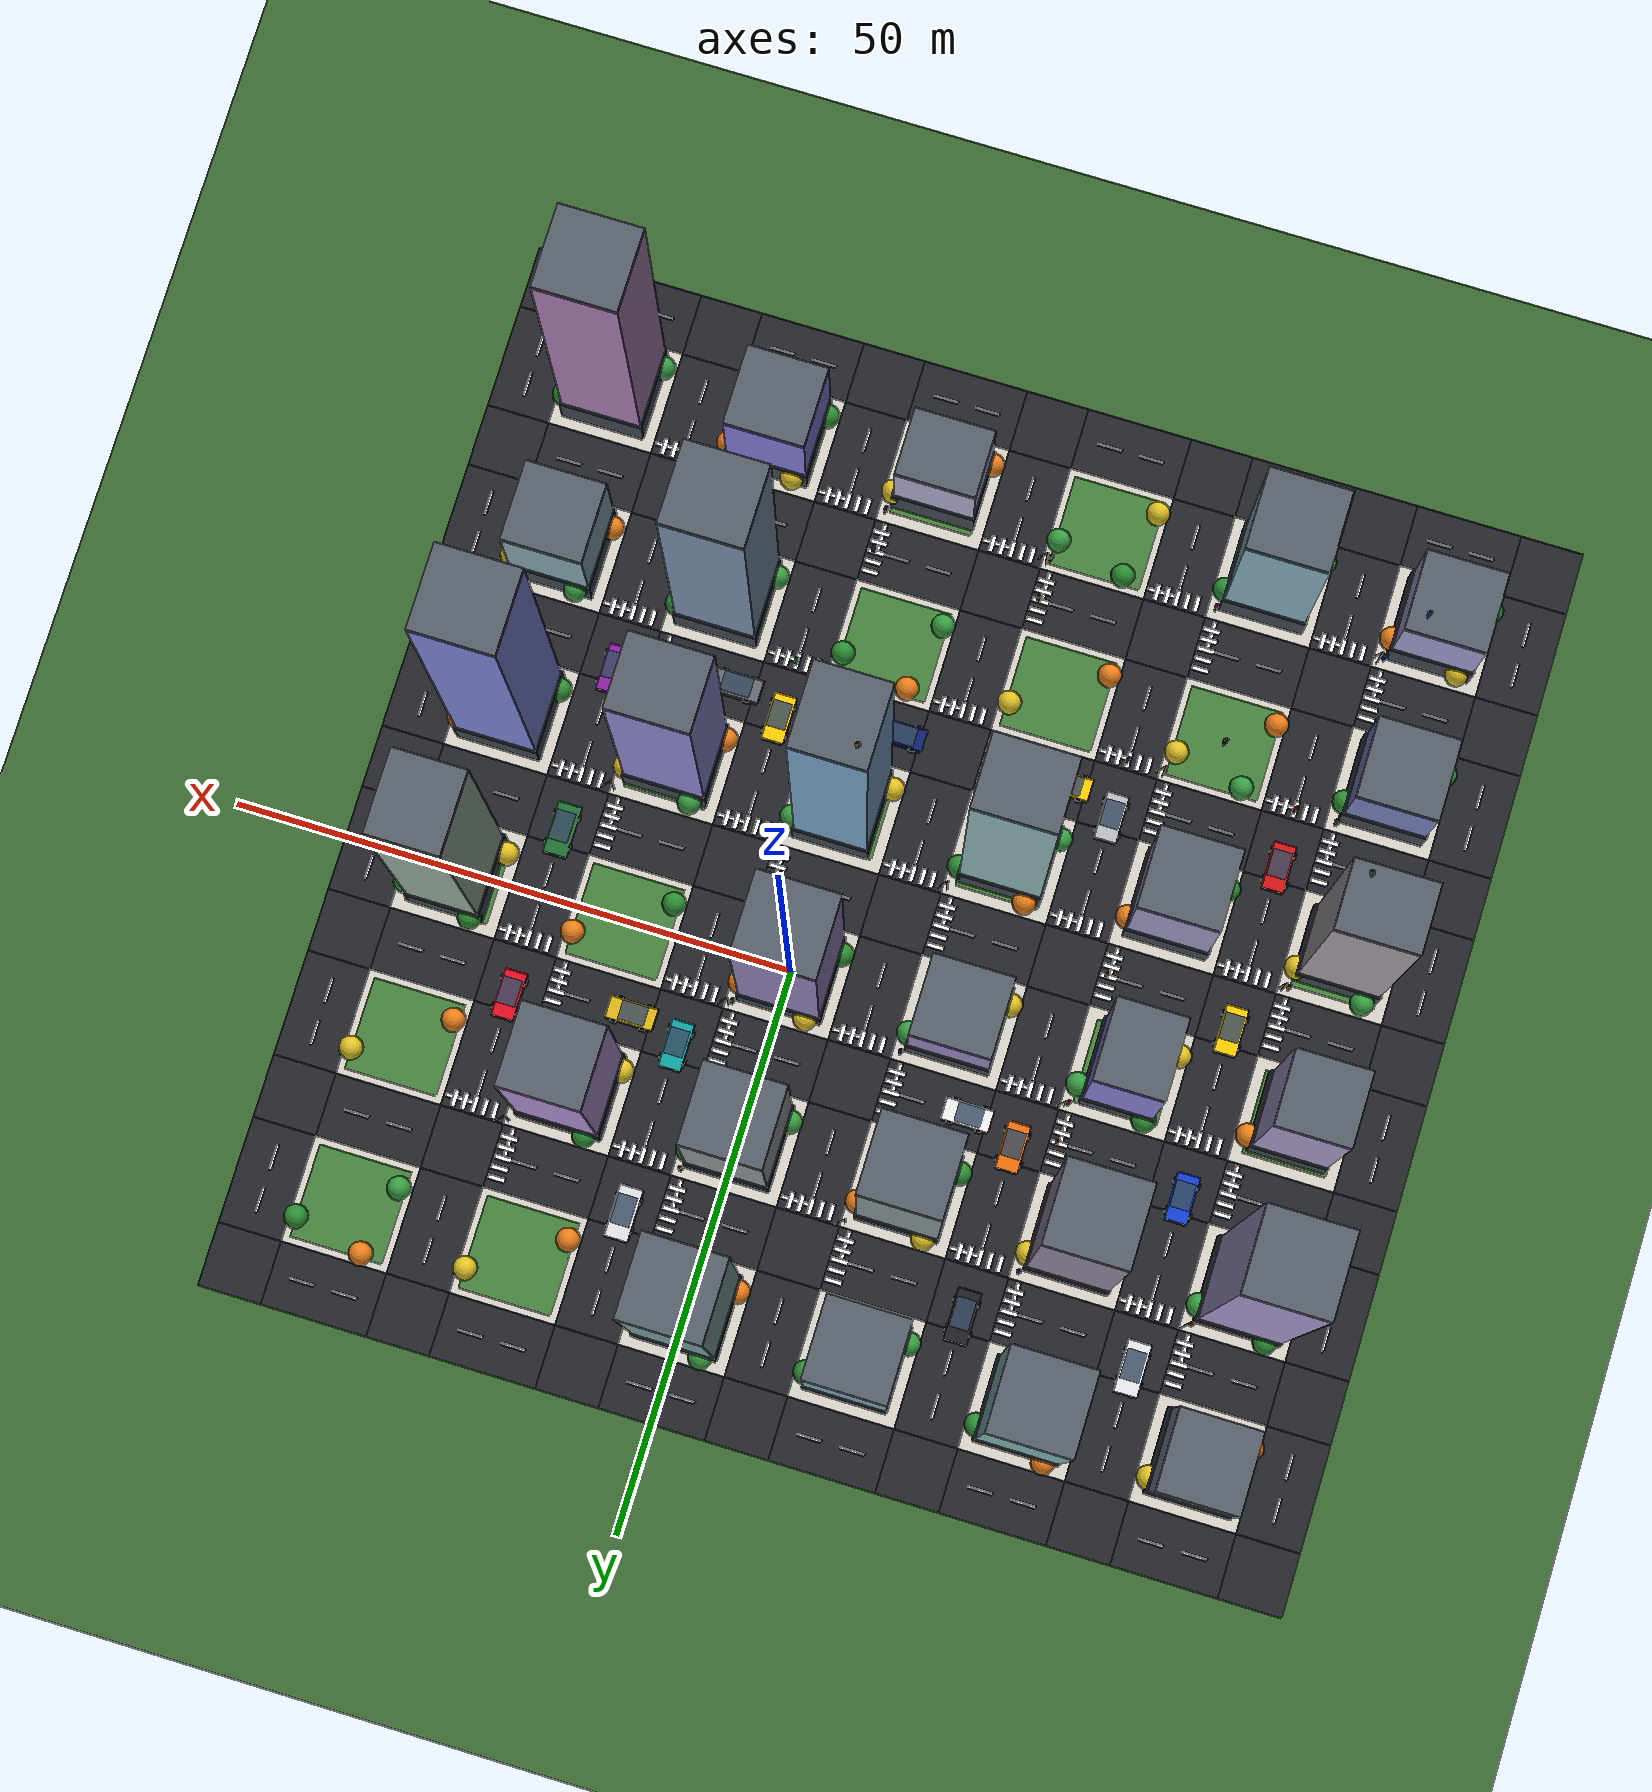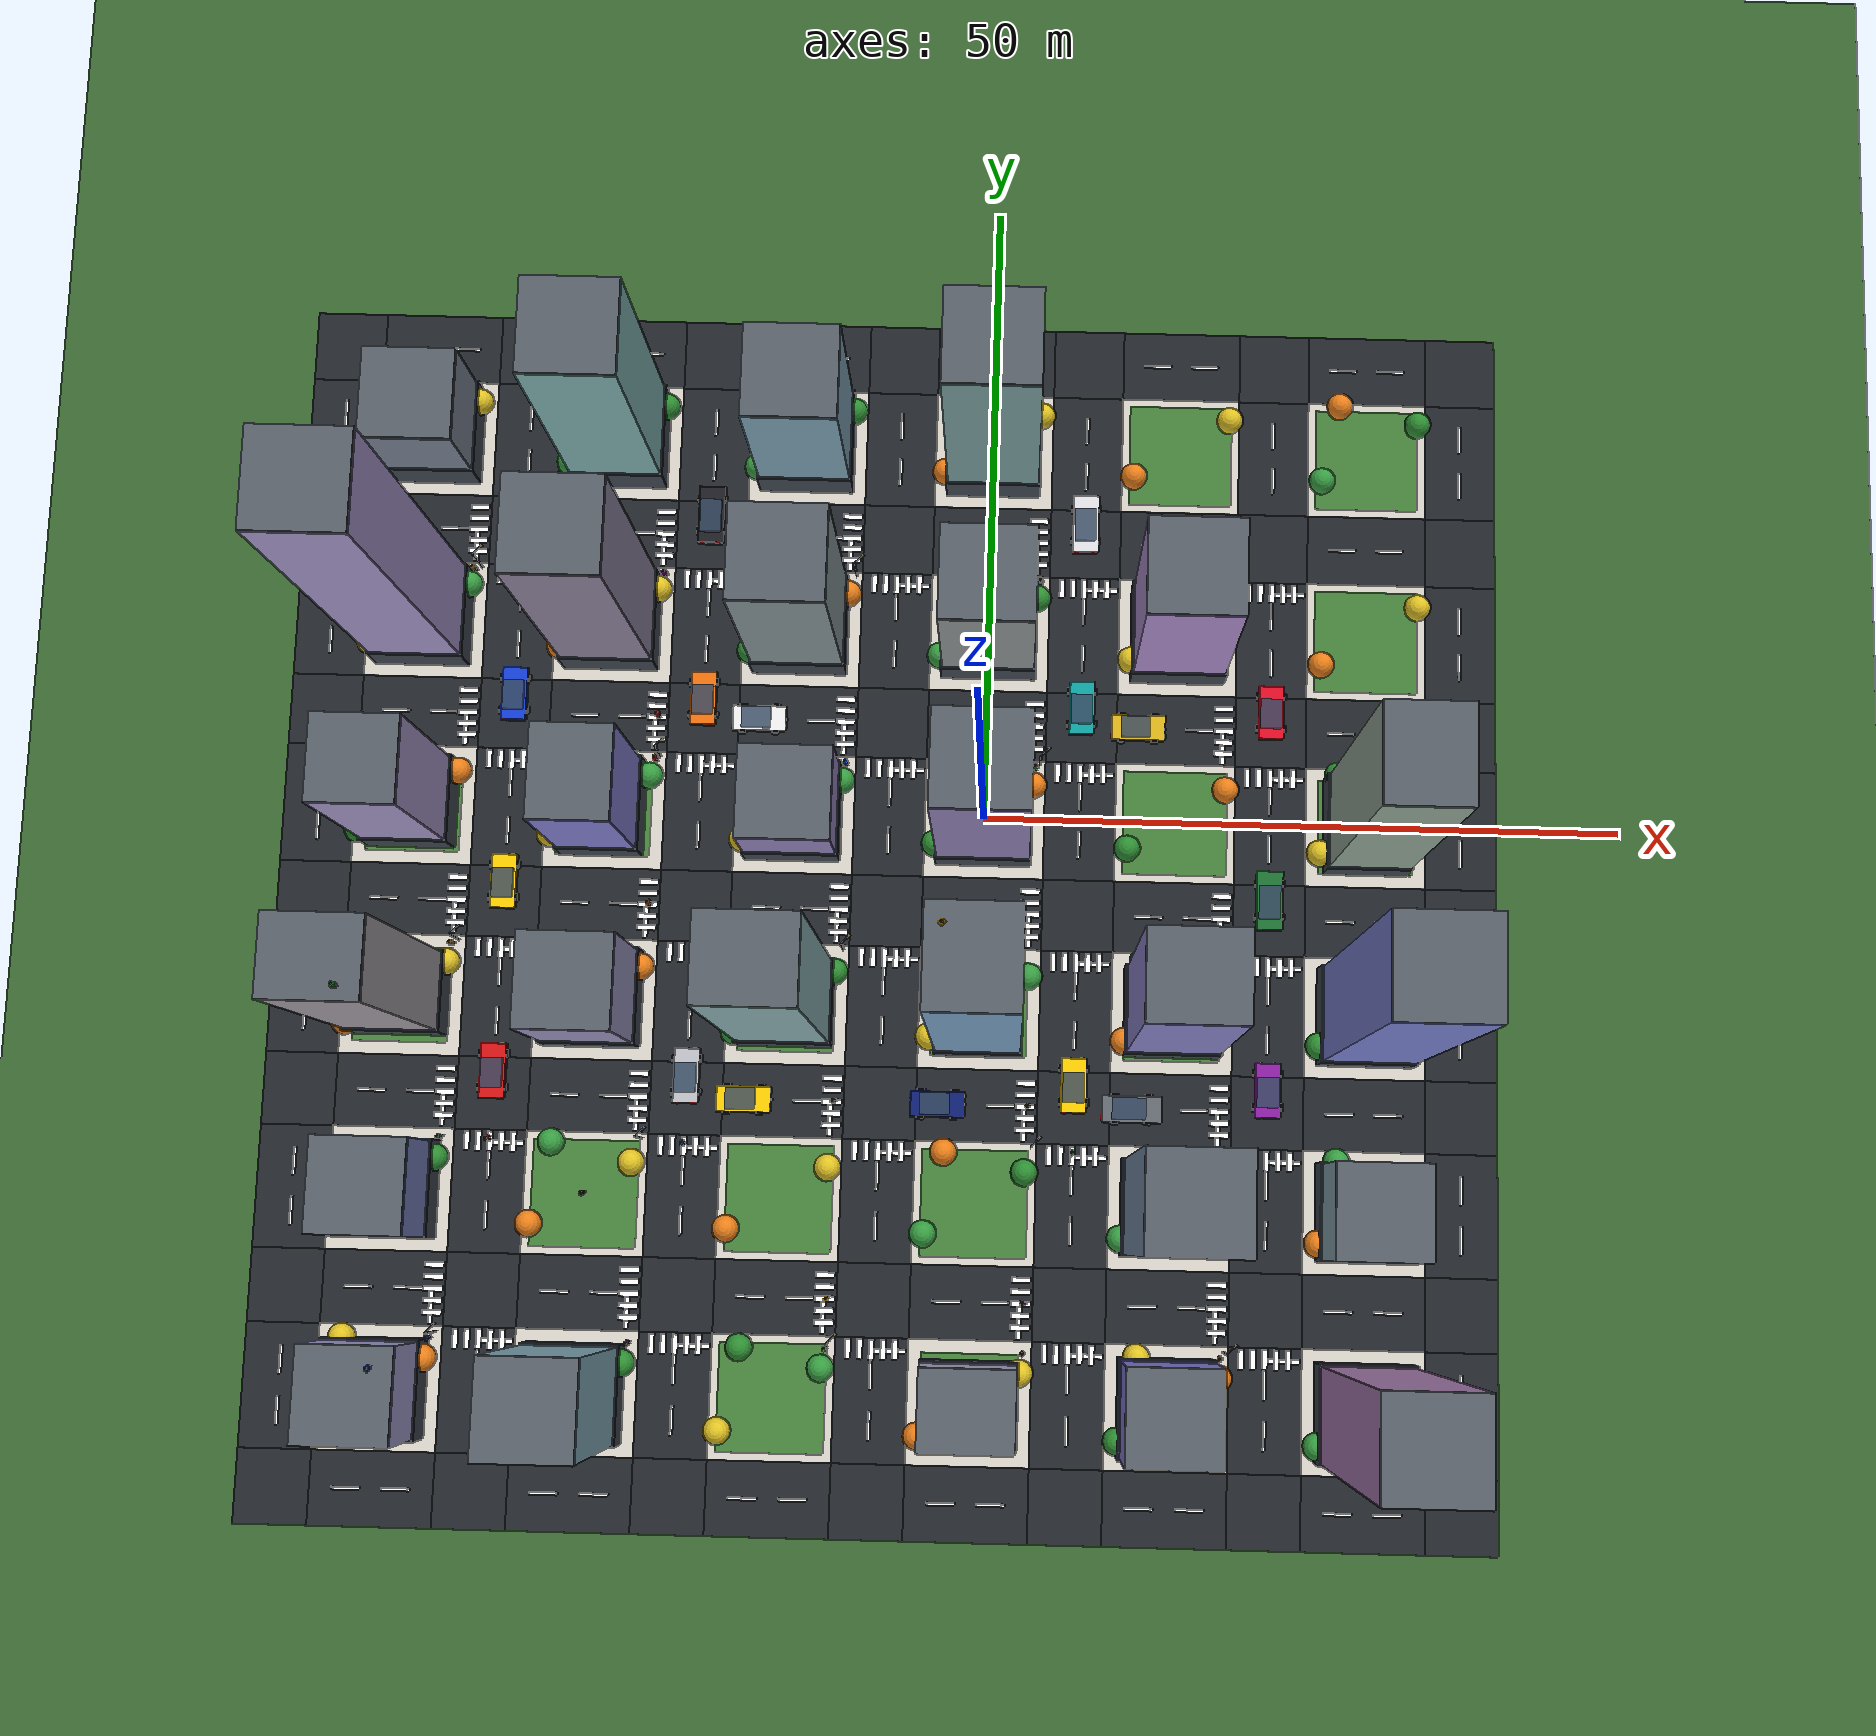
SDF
<?xml version="1.0" ?>
<sdf version="1.7">
  <world name="city_world">
    <plugin name="gazebo_ros_state" filename="libgazebo_ros_state.so"/>
    <physics name="1ms" type="ode">
      <max_step_size>0.001</max_step_size>
      <real_time_factor>1.0</real_time_factor>
    </physics>

    <!-- Warm crisp sun lighting -->
    <light type="directional" name="sun">
      <cast_shadows>true</cast_shadows>
      <pose>25 -35 100 0 0 0</pose>
      <diffuse>0.96 0.94 0.90 1</diffuse>
      <specular>0.3 0.3 0.3 1</specular>
      <attenuation>
        <range>1000</range>
        <constant>0.9</constant>
        <linear>0.01</linear>
        <quadratic>0.001</quadratic>
      </attenuation>
      <direction>-0.45 0.25 -0.85</direction>
    </light>

    <!-- Sky ambient light -->
    <light type="directional" name="ambient_sky">
      <cast_shadows>false</cast_shadows>
      <pose>0 0 60 0 0 0</pose>
      <diffuse>0.48 0.52 0.62 1</diffuse>
      <specular>0.1 0.1 0.1 1</specular>
      <direction>0.3 -0.2 -0.6</direction>
    </light>

    <!-- Landscape Terrain Ground Base -->
    <model name="ground_plane">
      <static>true</static>
      <link name="link">
        <collision name="collision">
          <geometry><plane><normal>0 0 1</normal><size>300 300</size></plane></geometry>
          <surface><friction><ode><mu>100</mu><mu2>50</mu2></ode></friction></surface>
        </collision>
        <visual name="visual">
          <geometry><plane><normal>0 0 1</normal><size>300 300</size></plane></geometry>
          <material>
            <ambient>0.24 0.42 0.20 1</ambient>
            <diffuse>0.24 0.42 0.20 1</diffuse>
          </material>
        </visual>
      </link>
    </model>

    <model name="city_roads">
      <static>true</static>
      <link name="link">
        <visual name="junc_0_0"><pose>-52.5 -52.5 0.01 0 0 0</pose>
          <geometry><box><size>5.6 5.6 0.02</size></box></geometry>
          <material><ambient>0.12 0.13 0.15 1</ambient><diffuse>0.14 0.15 0.17 1</diffuse></material></visual>
        <visual name="junc_0_1"><pose>-52.5 -37.5 0.01 0 0 0</pose>
          <geometry><box><size>5.6 5.6 0.02</size></box></geometry>
          <material><ambient>0.12 0.13 0.15 1</ambient><diffuse>0.14 0.15 0.17 1</diffuse></material></visual>
        <visual name="junc_0_2"><pose>-52.5 -22.5 0.01 0 0 0</pose>
          <geometry><box><size>5.6 5.6 0.02</size></box></geometry>
          <material><ambient>0.12 0.13 0.15 1</ambient><diffuse>0.14 0.15 0.17 1</diffuse></material></visual>
        <visual name="junc_0_3"><pose>-52.5 -7.5 0.01 0 0 0</pose>
          <geometry><box><size>5.6 5.6 0.02</size></box></geometry>
          <material><ambient>0.12 0.13 0.15 1</ambient><diffuse>0.14 0.15 0.17 1</diffuse></material></visual>
        <visual name="junc_0_4"><pose>-52.5 7.5 0.01 0 0 0</pose>
          <geometry><box><size>5.6 5.6 0.02</size></box></geometry>
          <material><ambient>0.12 0.13 0.15 1</ambient><diffuse>0.14 0.15 0.17 1</diffuse></material></visual>
        <visual name="junc_0_5"><pose>-52.5 22.5 0.01 0 0 0</pose>
          <geometry><box><size>5.6 5.6 0.02</size></box></geometry>
          <material><ambient>0.12 0.13 0.15 1</ambient><diffuse>0.14 0.15 0.17 1</diffuse></material></visual>
        <visual name="junc_0_6"><pose>-52.5 37.5 0.01 0 0 0</pose>
          <geometry><box><size>5.6 5.6 0.02</size></box></geometry>
          <material><ambient>0.12 0.13 0.15 1</ambient><diffuse>0.14 0.15 0.17 1</diffuse></material></visual>
        <visual name="junc_1_0"><pose>-37.5 -52.5 0.01 0 0 0</pose>
          <geometry><box><size>5.6 5.6 0.02</size></box></geometry>
          <material><ambient>0.12 0.13 0.15 1</ambient><diffuse>0.14 0.15 0.17 1</diffuse></material></visual>
        <visual name="junc_1_1"><pose>-37.5 -37.5 0.01 0 0 0</pose>
          <geometry><box><size>5.6 5.6 0.02</size></box></geometry>
          <material><ambient>0.12 0.13 0.15 1</ambient><diffuse>0.14 0.15 0.17 1</diffuse></material></visual>
        <visual name="junc_1_2"><pose>-37.5 -22.5 0.01 0 0 0</pose>
          <geometry><box><size>5.6 5.6 0.02</size></box></geometry>
          <material><ambient>0.12 0.13 0.15 1</ambient><diffuse>0.14 0.15 0.17 1</diffuse></material></visual>
        <visual name="junc_1_3"><pose>-37.5 -7.5 0.01 0 0 0</pose>
          <geometry><box><size>5.6 5.6 0.02</size></box></geometry>
          <material><ambient>0.12 0.13 0.15 1</ambient><diffuse>0.14 0.15 0.17 1</diffuse></material></visual>
        <visual name="junc_1_4"><pose>-37.5 7.5 0.01 0 0 0</pose>
          <geometry><box><size>5.6 5.6 0.02</size></box></geometry>
          <material><ambient>0.12 0.13 0.15 1</ambient><diffuse>0.14 0.15 0.17 1</diffuse></material></visual>
        <visual name="junc_1_5"><pose>-37.5 22.5 0.01 0 0 0</pose>
          <geometry><box><size>5.6 5.6 0.02</size></box></geometry>
          <material><ambient>0.12 0.13 0.15 1</ambient><diffuse>0.14 0.15 0.17 1</diffuse></material></visual>
        <visual name="junc_1_6"><pose>-37.5 37.5 0.01 0 0 0</pose>
          <geometry><box><size>5.6 5.6 0.02</size></box></geometry>
          <material><ambient>0.12 0.13 0.15 1</ambient><diffuse>0.14 0.15 0.17 1</diffuse></material></visual>
        <visual name="junc_2_0"><pose>-22.5 -52.5 0.01 0 0 0</pose>
          <geometry><box><size>5.6 5.6 0.02</size></box></geometry>
          <material><ambient>0.12 0.13 0.15 1</ambient><diffuse>0.14 0.15 0.17 1</diffuse></material></visual>
        <visual name="junc_2_1"><pose>-22.5 -37.5 0.01 0 0 0</pose>
          <geometry><box><size>5.6 5.6 0.02</size></box></geometry>
          <material><ambient>0.12 0.13 0.15 1</ambient><diffuse>0.14 0.15 0.17 1</diffuse></material></visual>
        <visual name="junc_2_2"><pose>-22.5 -22.5 0.01 0 0 0</pose>
          <geometry><box><size>5.6 5.6 0.02</size></box></geometry>
          <material><ambient>0.12 0.13 0.15 1</ambient><diffuse>0.14 0.15 0.17 1</diffuse></material></visual>
        <visual name="junc_2_3"><pose>-22.5 -7.5 0.01 0 0 0</pose>
          <geometry><box><size>5.6 5.6 0.02</size></box></geometry>
          <material><ambient>0.12 0.13 0.15 1</ambient><diffuse>0.14 0.15 0.17 1</diffuse></material></visual>
        <visual name="junc_2_4"><pose>-22.5 7.5 0.01 0 0 0</pose>
          <geometry><box><size>5.6 5.6 0.02</size></box></geometry>
          <material><ambient>0.12 0.13 0.15 1</ambient><diffuse>0.14 0.15 0.17 1</diffuse></material></visual>
        <visual name="junc_2_5"><pose>-22.5 22.5 0.01 0 0 0</pose>
          <geometry><box><size>5.6 5.6 0.02</size></box></geometry>
          <material><ambient>0.12 0.13 0.15 1</ambient><diffuse>0.14 0.15 0.17 1</diffuse></material></visual>
        <visual name="junc_2_6"><pose>-22.5 37.5 0.01 0 0 0</pose>
          <geometry><box><size>5.6 5.6 0.02</size></box></geometry>
          <material><ambient>0.12 0.13 0.15 1</ambient><diffuse>0.14 0.15 0.17 1</diffuse></material></visual>
        <visual name="junc_3_0"><pose>-7.5 -52.5 0.01 0 0 0</pose>
          <geometry><box><size>5.6 5.6 0.02</size></box></geometry>
          <material><ambient>0.12 0.13 0.15 1</ambient><diffuse>0.14 0.15 0.17 1</diffuse></material></visual>
        <visual name="junc_3_1"><pose>-7.5 -37.5 0.01 0 0 0</pose>
          <geometry><box><size>5.6 5.6 0.02</size></box></geometry>
          <material><ambient>0.12 0.13 0.15 1</ambient><diffuse>0.14 0.15 0.17 1</diffuse></material></visual>
        <visual name="junc_3_2"><pose>-7.5 -22.5 0.01 0 0 0</pose>
          <geometry><box><size>5.6 5.6 0.02</size></box></geometry>
          <material><ambient>0.12 0.13 0.15 1</ambient><diffuse>0.14 0.15 0.17 1</diffuse></material></visual>
        <visual name="junc_3_3"><pose>-7.5 -7.5 0.01 0 0 0</pose>
          <geometry><box><size>5.6 5.6 0.02</size></box></geometry>
          <material><ambient>0.12 0.13 0.15 1</ambient><diffuse>0.14 0.15 0.17 1</diffuse></material></visual>
        <visual name="junc_3_4"><pose>-7.5 7.5 0.01 0 0 0</pose>
          <geometry><box><size>5.6 5.6 0.02</size></box></geometry>
          <material><ambient>0.12 0.13 0.15 1</ambient><diffuse>0.14 0.15 0.17 1</diffuse></material></visual>
        <visual name="junc_3_5"><pose>-7.5 22.5 0.01 0 0 0</pose>
          <geometry><box><size>5.6 5.6 0.02</size></box></geometry>
          <material><ambient>0.12 0.13 0.15 1</ambient><diffuse>0.14 0.15 0.17 1</diffuse></material></visual>
        <visual name="junc_3_6"><pose>-7.5 37.5 0.01 0 0 0</pose>
          <geometry><box><size>5.6 5.6 0.02</size></box></geometry>
          <material><ambient>0.12 0.13 0.15 1</ambient><diffuse>0.14 0.15 0.17 1</diffuse></material></visual>
        <visual name="junc_4_0"><pose>7.5 -52.5 0.01 0 0 0</pose>
          <geometry><box><size>5.6 5.6 0.02</size></box></geometry>
          <material><ambient>0.12 0.13 0.15 1</ambient><diffuse>0.14 0.15 0.17 1</diffuse></material></visual>
        <visual name="junc_4_1"><pose>7.5 -37.5 0.01 0 0 0</pose>
          <geometry><box><size>5.6 5.6 0.02</size></box></geometry>
          <material><ambient>0.12 0.13 0.15 1</ambient><diffuse>0.14 0.15 0.17 1</diffuse></material></visual>
        <visual name="junc_4_2"><pose>7.5 -22.5 0.01 0 0 0</pose>
          <geometry><box><size>5.6 5.6 0.02</size></box></geometry>
          <material><ambient>0.12 0.13 0.15 1</ambient><diffuse>0.14 0.15 0.17 1</diffuse></material></visual>
        <visual name="junc_4_3"><pose>7.5 -7.5 0.01 0 0 0</pose>
          <geometry><box><size>5.6 5.6 0.02</size></box></geometry>
          <material><ambient>0.12 0.13 0.15 1</ambient><diffuse>0.14 0.15 0.17 1</diffuse></material></visual>
        <visual name="junc_4_4"><pose>7.5 7.5 0.01 0 0 0</pose>
          <geometry><box><size>5.6 5.6 0.02</size></box></geometry>
          <material><ambient>0.12 0.13 0.15 1</ambient><diffuse>0.14 0.15 0.17 1</diffuse></material></visual>
        <visual name="junc_4_5"><pose>7.5 22.5 0.01 0 0 0</pose>
          <geometry><box><size>5.6 5.6 0.02</size></box></geometry>
          <material><ambient>0.12 0.13 0.15 1</ambient><diffuse>0.14 0.15 0.17 1</diffuse></material></visual>
        <visual name="junc_4_6"><pose>7.5 37.5 0.01 0 0 0</pose>
          <geometry><box><size>5.6 5.6 0.02</size></box></geometry>
          <material><ambient>0.12 0.13 0.15 1</ambient><diffuse>0.14 0.15 0.17 1</diffuse></material></visual>
        <visual name="junc_5_0"><pose>22.5 -52.5 0.01 0 0 0</pose>
          <geometry><box><size>5.6 5.6 0.02</size></box></geometry>
          <material><ambient>0.12 0.13 0.15 1</ambient><diffuse>0.14 0.15 0.17 1</diffuse></material></visual>
        <visual name="junc_5_1"><pose>22.5 -37.5 0.01 0 0 0</pose>
          <geometry><box><size>5.6 5.6 0.02</size></box></geometry>
          <material><ambient>0.12 0.13 0.15 1</ambient><diffuse>0.14 0.15 0.17 1</diffuse></material></visual>
        <visual name="junc_5_2"><pose>22.5 -22.5 0.01 0 0 0</pose>
          <geometry><box><size>5.6 5.6 0.02</size></box></geometry>
          <material><ambient>0.12 0.13 0.15 1</ambient><diffuse>0.14 0.15 0.17 1</diffuse></material></visual>
        <visual name="junc_5_3"><pose>22.5 -7.5 0.01 0 0 0</pose>
          <geometry><box><size>5.6 5.6 0.02</size></box></geometry>
          <material><ambient>0.12 0.13 0.15 1</ambient><diffuse>0.14 0.15 0.17 1</diffuse></material></visual>
        <visual name="junc_5_4"><pose>22.5 7.5 0.01 0 0 0</pose>
          <geometry><box><size>5.6 5.6 0.02</size></box></geometry>
          <material><ambient>0.12 0.13 0.15 1</ambient><diffuse>0.14 0.15 0.17 1</diffuse></material></visual>
        <visual name="junc_5_5"><pose>22.5 22.5 0.01 0 0 0</pose>
          <geometry><box><size>5.6 5.6 0.02</size></box></geometry>
          <material><ambient>0.12 0.13 0.15 1</ambient><diffuse>0.14 0.15 0.17 1</diffuse></material></visual>
        <visual name="junc_5_6"><pose>22.5 37.5 0.01 0 0 0</pose>
          <geometry><box><size>5.6 5.6 0.02</size></box></geometry>
          <material><ambient>0.12 0.13 0.15 1</ambient><diffuse>0.14 0.15 0.17 1</diffuse></material></visual>
        <visual name="junc_6_0"><pose>37.5 -52.5 0.01 0 0 0</pose>
          <geometry><box><size>5.6 5.6 0.02</size></box></geometry>
          <material><ambient>0.12 0.13 0.15 1</ambient><diffuse>0.14 0.15 0.17 1</diffuse></material></visual>
        <visual name="junc_6_1"><pose>37.5 -37.5 0.01 0 0 0</pose>
          <geometry><box><size>5.6 5.6 0.02</size></box></geometry>
          <material><ambient>0.12 0.13 0.15 1</ambient><diffuse>0.14 0.15 0.17 1</diffuse></material></visual>
        <visual name="junc_6_2"><pose>37.5 -22.5 0.01 0 0 0</pose>
          <geometry><box><size>5.6 5.6 0.02</size></box></geometry>
          <material><ambient>0.12 0.13 0.15 1</ambient><diffuse>0.14 0.15 0.17 1</diffuse></material></visual>
        <visual name="junc_6_3"><pose>37.5 -7.5 0.01 0 0 0</pose>
          <geometry><box><size>5.6 5.6 0.02</size></box></geometry>
          <material><ambient>0.12 0.13 0.15 1</ambient><diffuse>0.14 0.15 0.17 1</diffuse></material></visual>
        <visual name="junc_6_4"><pose>37.5 7.5 0.01 0 0 0</pose>
          <geometry><box><size>5.6 5.6 0.02</size></box></geometry>
          <material><ambient>0.12 0.13 0.15 1</ambient><diffuse>0.14 0.15 0.17 1</diffuse></material></visual>
        <visual name="junc_6_5"><pose>37.5 22.5 0.01 0 0 0</pose>
          <geometry><box><size>5.6 5.6 0.02</size></box></geometry>
          <material><ambient>0.12 0.13 0.15 1</ambient><diffuse>0.14 0.15 0.17 1</diffuse></material></visual>
        <visual name="junc_6_6"><pose>37.5 37.5 0.01 0 0 0</pose>
          <geometry><box><size>5.6 5.6 0.02</size></box></geometry>
          <material><ambient>0.12 0.13 0.15 1</ambient><diffuse>0.14 0.15 0.17 1</diffuse></material></visual>
        <visual name="road_ew_0_0"><pose>-45.0 -52.5 0.01 0 0 0</pose>
          <geometry><box><size>9.4 5.6 0.02</size></box></geometry>
          <material><ambient>0.12 0.13 0.15 1</ambient><diffuse>0.14 0.15 0.17 1</diffuse></material></visual>
        <visual name="road_ew_0_1"><pose>-45.0 -37.5 0.01 0 0 0</pose>
          <geometry><box><size>9.4 5.6 0.02</size></box></geometry>
          <material><ambient>0.12 0.13 0.15 1</ambient><diffuse>0.14 0.15 0.17 1</diffuse></material></visual>
        <visual name="road_ew_0_2"><pose>-45.0 -22.5 0.01 0 0 0</pose>
          <geometry><box><size>9.4 5.6 0.02</size></box></geometry>
          <material><ambient>0.12 0.13 0.15 1</ambient><diffuse>0.14 0.15 0.17 1</diffuse></material></visual>
        <visual name="road_ew_0_3"><pose>-45.0 -7.5 0.01 0 0 0</pose>
          <geometry><box><size>9.4 5.6 0.02</size></box></geometry>
          <material><ambient>0.12 0.13 0.15 1</ambient><diffuse>0.14 0.15 0.17 1</diffuse></material></visual>
        <visual name="road_ew_0_4"><pose>-45.0 7.5 0.01 0 0 0</pose>
          <geometry><box><size>9.4 5.6 0.02</size></box></geometry>
          <material><ambient>0.12 0.13 0.15 1</ambient><diffuse>0.14 0.15 0.17 1</diffuse></material></visual>
        <visual name="road_ew_0_5"><pose>-45.0 22.5 0.01 0 0 0</pose>
          <geometry><box><size>9.4 5.6 0.02</size></box></geometry>
          <material><ambient>0.12 0.13 0.15 1</ambient><diffuse>0.14 0.15 0.17 1</diffuse></material></visual>
        <visual name="road_ew_0_6"><pose>-45.0 37.5 0.01 0 0 0</pose>
          <geometry><box><size>9.4 5.6 0.02</size></box></geometry>
          <material><ambient>0.12 0.13 0.15 1</ambient><diffuse>0.14 0.15 0.17 1</diffuse></material></visual>
        <visual name="road_ew_1_0"><pose>-30.0 -52.5 0.01 0 0 0</pose>
          <geometry><box><size>9.4 5.6 0.02</size></box></geometry>
          <material><ambient>0.12 0.13 0.15 1</ambient><diffuse>0.14 0.15 0.17 1</diffuse></material></visual>
        <visual name="road_ew_1_1"><pose>-30.0 -37.5 0.01 0 0 0</pose>
          <geometry><box><size>9.4 5.6 0.02</size></box></geometry>
          <material><ambient>0.12 0.13 0.15 1</ambient><diffuse>0.14 0.15 0.17 1</diffuse></material></visual>
        <visual name="road_ew_1_2"><pose>-30.0 -22.5 0.01 0 0 0</pose>
          <geometry><box><size>9.4 5.6 0.02</size></box></geometry>
          <material><ambient>0.12 0.13 0.15 1</ambient><diffuse>0.14 0.15 0.17 1</diffuse></material></visual>
        <visual name="road_ew_1_3"><pose>-30.0 -7.5 0.01 0 0 0</pose>
          <geometry><box><size>9.4 5.6 0.02</size></box></geometry>
          <material><ambient>0.12 0.13 0.15 1</ambient><diffuse>0.14 0.15 0.17 1</diffuse></material></visual>
        <visual name="road_ew_1_4"><pose>-30.0 7.5 0.01 0 0 0</pose>
          <geometry><box><size>9.4 5.6 0.02</size></box></geometry>
          <material><ambient>0.12 0.13 0.15 1</ambient><diffuse>0.14 0.15 0.17 1</diffuse></material></visual>
        <visual name="road_ew_1_5"><pose>-30.0 22.5 0.01 0 0 0</pose>
          <geometry><box><size>9.4 5.6 0.02</size></box></geometry>
          <material><ambient>0.12 0.13 0.15 1</ambient><diffuse>0.14 0.15 0.17 1</diffuse></material></visual>
        <visual name="road_ew_1_6"><pose>-30.0 37.5 0.01 0 0 0</pose>
          <geometry><box><size>9.4 5.6 0.02</size></box></geometry>
          <material><ambient>0.12 0.13 0.15 1</ambient><diffuse>0.14 0.15 0.17 1</diffuse></material></visual>
        <visual name="road_ew_2_0"><pose>-15.0 -52.5 0.01 0 0 0</pose>
          <geometry><box><size>9.4 5.6 0.02</size></box></geometry>
          <material><ambient>0.12 0.13 0.15 1</ambient><diffuse>0.14 0.15 0.17 1</diffuse></material></visual>
        <visual name="road_ew_2_1"><pose>-15.0 -37.5 0.01 0 0 0</pose>
          <geometry><box><size>9.4 5.6 0.02</size></box></geometry>
          <material><ambient>0.12 0.13 0.15 1</ambient><diffuse>0.14 0.15 0.17 1</diffuse></material></visual>
        <visual name="road_ew_2_2"><pose>-15.0 -22.5 0.01 0 0 0</pose>
          <geometry><box><size>9.4 5.6 0.02</size></box></geometry>
          <material><ambient>0.12 0.13 0.15 1</ambient><diffuse>0.14 0.15 0.17 1</diffuse></material></visual>
        <visual name="road_ew_2_3"><pose>-15.0 -7.5 0.01 0 0 0</pose>
          <geometry><box><size>9.4 5.6 0.02</size></box></geometry>
          <material><ambient>0.12 0.13 0.15 1</ambient><diffuse>0.14 0.15 0.17 1</diffuse></material></visual>
        <visual name="road_ew_2_4"><pose>-15.0 7.5 0.01 0 0 0</pose>
          <geometry><box><size>9.4 5.6 0.02</size></box></geometry>
          <material><ambient>0.12 0.13 0.15 1</ambient><diffuse>0.14 0.15 0.17 1</diffuse></material></visual>
        <visual name="road_ew_2_5"><pose>-15.0 22.5 0.01 0 0 0</pose>
          <geometry><box><size>9.4 5.6 0.02</size></box></geometry>
          <material><ambient>0.12 0.13 0.15 1</ambient><diffuse>0.14 0.15 0.17 1</diffuse></material></visual>
        <visual name="road_ew_2_6"><pose>-15.0 37.5 0.01 0 0 0</pose>
          <geometry><box><size>9.4 5.6 0.02</size></box></geometry>
          <material><ambient>0.12 0.13 0.15 1</ambient><diffuse>0.14 0.15 0.17 1</diffuse></material></visual>
        <visual name="road_ew_3_0"><pose>0.0 -52.5 0.01 0 0 0</pose>
          <geometry><box><size>9.4 5.6 0.02</size></box></geometry>
          <material><ambient>0.12 0.13 0.15 1</ambient><diffuse>0.14 0.15 0.17 1</diffuse></material></visual>
        <visual name="road_ew_3_1"><pose>0.0 -37.5 0.01 0 0 0</pose>
          <geometry><box><size>9.4 5.6 0.02</size></box></geometry>
          <material><ambient>0.12 0.13 0.15 1</ambient><diffuse>0.14 0.15 0.17 1</diffuse></material></visual>
        <visual name="road_ew_3_2"><pose>0.0 -22.5 0.01 0 0 0</pose>
          <geometry><box><size>9.4 5.6 0.02</size></box></geometry>
          <material><ambient>0.12 0.13 0.15 1</ambient><diffuse>0.14 0.15 0.17 1</diffuse></material></visual>
        <visual name="road_ew_3_3"><pose>0.0 -7.5 0.01 0 0 0</pose>
          <geometry><box><size>9.4 5.6 0.02</size></box></geometry>
          <material><ambient>0.12 0.13 0.15 1</ambient><diffuse>0.14 0.15 0.17 1</diffuse></material></visual>
        <visual name="road_ew_3_4"><pose>0.0 7.5 0.01 0 0 0</pose>
          <geometry><box><size>9.4 5.6 0.02</size></box></geometry>
          <material><ambient>0.12 0.13 0.15 1</ambient><diffuse>0.14 0.15 0.17 1</diffuse></material></visual>
        <visual name="road_ew_3_5"><pose>0.0 22.5 0.01 0 0 0</pose>
          <geometry><box><size>9.4 5.6 0.02</size></box></geometry>
          <material><ambient>0.12 0.13 0.15 1</ambient><diffuse>0.14 0.15 0.17 1</diffuse></material></visual>
        <visual name="road_ew_3_6"><pose>0.0 37.5 0.01 0 0 0</pose>
          <geometry><box><size>9.4 5.6 0.02</size></box></geometry>
          <material><ambient>0.12 0.13 0.15 1</ambient><diffuse>0.14 0.15 0.17 1</diffuse></material></visual>
        <visual name="road_ew_4_0"><pose>15.0 -52.5 0.01 0 0 0</pose>
          <geometry><box><size>9.4 5.6 0.02</size></box></geometry>
          <material><ambient>0.12 0.13 0.15 1</ambient><diffuse>0.14 0.15 0.17 1</diffuse></material></visual>
        <visual name="road_ew_4_1"><pose>15.0 -37.5 0.01 0 0 0</pose>
          <geometry><box><size>9.4 5.6 0.02</size></box></geometry>
          <material><ambient>0.12 0.13 0.15 1</ambient><diffuse>0.14 0.15 0.17 1</diffuse></material></visual>
        <visual name="road_ew_4_2"><pose>15.0 -22.5 0.01 0 0 0</pose>
          <geometry><box><size>9.4 5.6 0.02</size></box></geometry>
          <material><ambient>0.12 0.13 0.15 1</ambient><diffuse>0.14 0.15 0.17 1</diffuse></material></visual>
        <visual name="road_ew_4_3"><pose>15.0 -7.5 0.01 0 0 0</pose>
          <geometry><box><size>9.4 5.6 0.02</size></box></geometry>
          <material><ambient>0.12 0.13 0.15 1</ambient><diffuse>0.14 0.15 0.17 1</diffuse></material></visual>
        <visual name="road_ew_4_4"><pose>15.0 7.5 0.01 0 0 0</pose>
          <geometry><box><size>9.4 5.6 0.02</size></box></geometry>
          <material><ambient>0.12 0.13 0.15 1</ambient><diffuse>0.14 0.15 0.17 1</diffuse></material></visual>
        <visual name="road_ew_4_5"><pose>15.0 22.5 0.01 0 0 0</pose>
          <geometry><box><size>9.4 5.6 0.02</size></box></geometry>
          <material><ambient>0.12 0.13 0.15 1</ambient><diffuse>0.14 0.15 0.17 1</diffuse></material></visual>
        <visual name="road_ew_4_6"><pose>15.0 37.5 0.01 0 0 0</pose>
          <geometry><box><size>9.4 5.6 0.02</size></box></geometry>
          <material><ambient>0.12 0.13 0.15 1</ambient><diffuse>0.14 0.15 0.17 1</diffuse></material></visual>
        <visual name="road_ew_5_0"><pose>30.0 -52.5 0.01 0 0 0</pose>
          <geometry><box><size>9.4 5.6 0.02</size></box></geometry>
          <material><ambient>0.12 0.13 0.15 1</ambient><diffuse>0.14 0.15 0.17 1</diffuse></material></visual>
        <visual name="road_ew_5_1"><pose>30.0 -37.5 0.01 0 0 0</pose>
          <geometry><box><size>9.4 5.6 0.02</size></box></geometry>
          <material><ambient>0.12 0.13 0.15 1</ambient><diffuse>0.14 0.15 0.17 1</diffuse></material></visual>
        <visual name="road_ew_5_2"><pose>30.0 -22.5 0.01 0 0 0</pose>
          <geometry><box><size>9.4 5.6 0.02</size></box></geometry>
          <material><ambient>0.12 0.13 0.15 1</ambient><diffuse>0.14 0.15 0.17 1</diffuse></material></visual>
        <visual name="road_ew_5_3"><pose>30.0 -7.5 0.01 0 0 0</pose>
          <geometry><box><size>9.4 5.6 0.02</size></box></geometry>
          <material><ambient>0.12 0.13 0.15 1</ambient><diffuse>0.14 0.15 0.17 1</diffuse></material></visual>
        <visual name="road_ew_5_4"><pose>30.0 7.5 0.01 0 0 0</pose>
          <geometry><box><size>9.4 5.6 0.02</size></box></geometry>
          <material><ambient>0.12 0.13 0.15 1</ambient><diffuse>0.14 0.15 0.17 1</diffuse></material></visual>
        <visual name="road_ew_5_5"><pose>30.0 22.5 0.01 0 0 0</pose>
          <geometry><box><size>9.4 5.6 0.02</size></box></geometry>
          <material><ambient>0.12 0.13 0.15 1</ambient><diffuse>0.14 0.15 0.17 1</diffuse></material></visual>
        <visual name="road_ew_5_6"><pose>30.0 37.5 0.01 0 0 0</pose>
          <geometry><box><size>9.4 5.6 0.02</size></box></geometry>
          <material><ambient>0.12 0.13 0.15 1</ambient><diffuse>0.14 0.15 0.17 1</diffuse></material></visual>
        <visual name="road_ns_0_0"><pose>-52.5 -45.0 0.01 0 0 0</pose>
          <geometry><box><size>5.6 9.4 0.02</size></box></geometry>
          <material><ambient>0.12 0.13 0.15 1</ambient><diffuse>0.14 0.15 0.17 1</diffuse></material></visual>
        <visual name="road_ns_1_0"><pose>-37.5 -45.0 0.01 0 0 0</pose>
          <geometry><box><size>5.6 9.4 0.02</size></box></geometry>
          <material><ambient>0.12 0.13 0.15 1</ambient><diffuse>0.14 0.15 0.17 1</diffuse></material></visual>
        <visual name="road_ns_2_0"><pose>-22.5 -45.0 0.01 0 0 0</pose>
          <geometry><box><size>5.6 9.4 0.02</size></box></geometry>
          <material><ambient>0.12 0.13 0.15 1</ambient><diffuse>0.14 0.15 0.17 1</diffuse></material></visual>
        <visual name="road_ns_3_0"><pose>-7.5 -45.0 0.01 0 0 0</pose>
          <geometry><box><size>5.6 9.4 0.02</size></box></geometry>
          <material><ambient>0.12 0.13 0.15 1</ambient><diffuse>0.14 0.15 0.17 1</diffuse></material></visual>
        <visual name="road_ns_4_0"><pose>7.5 -45.0 0.01 0 0 0</pose>
          <geometry><box><size>5.6 9.4 0.02</size></box></geometry>
          <material><ambient>0.12 0.13 0.15 1</ambient><diffuse>0.14 0.15 0.17 1</diffuse></material></visual>
        <visual name="road_ns_5_0"><pose>22.5 -45.0 0.01 0 0 0</pose>
          <geometry><box><size>5.6 9.4 0.02</size></box></geometry>
          <material><ambient>0.12 0.13 0.15 1</ambient><diffuse>0.14 0.15 0.17 1</diffuse></material></visual>
        <visual name="road_ns_6_0"><pose>37.5 -45.0 0.01 0 0 0</pose>
          <geometry><box><size>5.6 9.4 0.02</size></box></geometry>
          <material><ambient>0.12 0.13 0.15 1</ambient><diffuse>0.14 0.15 0.17 1</diffuse></material></visual>
        <visual name="road_ns_0_1"><pose>-52.5 -30.0 0.01 0 0 0</pose>
          <geometry><box><size>5.6 9.4 0.02</size></box></geometry>
          <material><ambient>0.12 0.13 0.15 1</ambient><diffuse>0.14 0.15 0.17 1</diffuse></material></visual>
        <visual name="road_ns_1_1"><pose>-37.5 -30.0 0.01 0 0 0</pose>
          <geometry><box><size>5.6 9.4 0.02</size></box></geometry>
          <material><ambient>0.12 0.13 0.15 1</ambient><diffuse>0.14 0.15 0.17 1</diffuse></material></visual>
        <visual name="road_ns_2_1"><pose>-22.5 -30.0 0.01 0 0 0</pose>
          <geometry><box><size>5.6 9.4 0.02</size></box></geometry>
          <material><ambient>0.12 0.13 0.15 1</ambient><diffuse>0.14 0.15 0.17 1</diffuse></material></visual>
        <visual name="road_ns_3_1"><pose>-7.5 -30.0 0.01 0 0 0</pose>
          <geometry><box><size>5.6 9.4 0.02</size></box></geometry>
          <material><ambient>0.12 0.13 0.15 1</ambient><diffuse>0.14 0.15 0.17 1</diffuse></material></visual>
        <visual name="road_ns_4_1"><pose>7.5 -30.0 0.01 0 0 0</pose>
          <geometry><box><size>5.6 9.4 0.02</size></box></geometry>
          <material><ambient>0.12 0.13 0.15 1</ambient><diffuse>0.14 0.15 0.17 1</diffuse></material></visual>
        <visual name="road_ns_5_1"><pose>22.5 -30.0 0.01 0 0 0</pose>
          <geometry><box><size>5.6 9.4 0.02</size></box></geometry>
          <material><ambient>0.12 0.13 0.15 1</ambient><diffuse>0.14 0.15 0.17 1</diffuse></material></visual>
        <visual name="road_ns_6_1"><pose>37.5 -30.0 0.01 0 0 0</pose>
          <geometry><box><size>5.6 9.4 0.02</size></box></geometry>
          <material><ambient>0.12 0.13 0.15 1</ambient><diffuse>0.14 0.15 0.17 1</diffuse></material></visual>
        <visual name="road_ns_0_2"><pose>-52.5 -15.0 0.01 0 0 0</pose>
          <geometry><box><size>5.6 9.4 0.02</size></box></geometry>
          <material><ambient>0.12 0.13 0.15 1</ambient><diffuse>0.14 0.15 0.17 1</diffuse></material></visual>
        <visual name="road_ns_1_2"><pose>-37.5 -15.0 0.01 0 0 0</pose>
          <geometry><box><size>5.6 9.4 0.02</size></box></geometry>
          <material><ambient>0.12 0.13 0.15 1</ambient><diffuse>0.14 0.15 0.17 1</diffuse></material></visual>
        <visual name="road_ns_2_2"><pose>-22.5 -15.0 0.01 0 0 0</pose>
          <geometry><box><size>5.6 9.4 0.02</size></box></geometry>
          <material><ambient>0.12 0.13 0.15 1</ambient><diffuse>0.14 0.15 0.17 1</diffuse></material></visual>
        <visual name="road_ns_3_2"><pose>-7.5 -15.0 0.01 0 0 0</pose>
          <geometry><box><size>5.6 9.4 0.02</size></box></geometry>
          <material><ambient>0.12 0.13 0.15 1</ambient><diffuse>0.14 0.15 0.17 1</diffuse></material></visual>
        <visual name="road_ns_4_2"><pose>7.5 -15.0 0.01 0 0 0</pose>
          <geometry><box><size>5.6 9.4 0.02</size></box></geometry>
          <material><ambient>0.12 0.13 0.15 1</ambient><diffuse>0.14 0.15 0.17 1</diffuse></material></visual>
        <visual name="road_ns_5_2"><pose>22.5 -15.0 0.01 0 0 0</pose>
          <geometry><box><size>5.6 9.4 0.02</size></box></geometry>
          <material><ambient>0.12 0.13 0.15 1</ambient><diffuse>0.14 0.15 0.17 1</diffuse></material></visual>
        <visual name="road_ns_6_2"><pose>37.5 -15.0 0.01 0 0 0</pose>
          <geometry><box><size>5.6 9.4 0.02</size></box></geometry>
          <material><ambient>0.12 0.13 0.15 1</ambient><diffuse>0.14 0.15 0.17 1</diffuse></material></visual>
        <visual name="road_ns_0_3"><pose>-52.5 0.0 0.01 0 0 0</pose>
          <geometry><box><size>5.6 9.4 0.02</size></box></geometry>
          <material><ambient>0.12 0.13 0.15 1</ambient><diffuse>0.14 0.15 0.17 1</diffuse></material></visual>
        <visual name="road_ns_1_3"><pose>-37.5 0.0 0.01 0 0 0</pose>
          <geometry><box><size>5.6 9.4 0.02</size></box></geometry>
          <material><ambient>0.12 0.13 0.15 1</ambient><diffuse>0.14 0.15 0.17 1</diffuse></material></visual>
        <visual name="road_ns_2_3"><pose>-22.5 0.0 0.01 0 0 0</pose>
          <geometry><box><size>5.6 9.4 0.02</size></box></geometry>
          <material><ambient>0.12 0.13 0.15 1</ambient><diffuse>0.14 0.15 0.17 1</diffuse></material></visual>
        <visual name="road_ns_3_3"><pose>-7.5 0.0 0.01 0 0 0</pose>
          <geometry><box><size>5.6 9.4 0.02</size></box></geometry>
          <material><ambient>0.12 0.13 0.15 1</ambient><diffuse>0.14 0.15 0.17 1</diffuse></material></visual>
        <visual name="road_ns_4_3"><pose>7.5 0.0 0.01 0 0 0</pose>
          <geometry><box><size>5.6 9.4 0.02</size></box></geometry>
          <material><ambient>0.12 0.13 0.15 1</ambient><diffuse>0.14 0.15 0.17 1</diffuse></material></visual>
        <visual name="road_ns_5_3"><pose>22.5 0.0 0.01 0 0 0</pose>
          <geometry><box><size>5.6 9.4 0.02</size></box></geometry>
          <material><ambient>0.12 0.13 0.15 1</ambient><diffuse>0.14 0.15 0.17 1</diffuse></material></visual>
        <visual name="road_ns_6_3"><pose>37.5 0.0 0.01 0 0 0</pose>
          <geometry><box><size>5.6 9.4 0.02</size></box></geometry>
          <material><ambient>0.12 0.13 0.15 1</ambient><diffuse>0.14 0.15 0.17 1</diffuse></material></visual>
        <visual name="road_ns_0_4"><pose>-52.5 15.0 0.01 0 0 0</pose>
          <geometry><box><size>5.6 9.4 0.02</size></box></geometry>
          <material><ambient>0.12 0.13 0.15 1</ambient><diffuse>0.14 0.15 0.17 1</diffuse></material></visual>
        <visual name="road_ns_1_4"><pose>-37.5 15.0 0.01 0 0 0</pose>
          <geometry><box><size>5.6 9.4 0.02</size></box></geometry>
          <material><ambient>0.12 0.13 0.15 1</ambient><diffuse>0.14 0.15 0.17 1</diffuse></material></visual>
        <visual name="road_ns_2_4"><pose>-22.5 15.0 0.01 0 0 0</pose>
          <geometry><box><size>5.6 9.4 0.02</size></box></geometry>
          <material><ambient>0.12 0.13 0.15 1</ambient><diffuse>0.14 0.15 0.17 1</diffuse></material></visual>
        <visual name="road_ns_3_4"><pose>-7.5 15.0 0.01 0 0 0</pose>
          <geometry><box><size>5.6 9.4 0.02</size></box></geometry>
          <material><ambient>0.12 0.13 0.15 1</ambient><diffuse>0.14 0.15 0.17 1</diffuse></material></visual>
        <visual name="road_ns_4_4"><pose>7.5 15.0 0.01 0 0 0</pose>
          <geometry><box><size>5.6 9.4 0.02</size></box></geometry>
          <material><ambient>0.12 0.13 0.15 1</ambient><diffuse>0.14 0.15 0.17 1</diffuse></material></visual>
        <visual name="road_ns_5_4"><pose>22.5 15.0 0.01 0 0 0</pose>
          <geometry><box><size>5.6 9.4 0.02</size></box></geometry>
          <material><ambient>0.12 0.13 0.15 1</ambient><diffuse>0.14 0.15 0.17 1</diffuse></material></visual>
        <visual name="road_ns_6_4"><pose>37.5 15.0 0.01 0 0 0</pose>
          <geometry><box><size>5.6 9.4 0.02</size></box></geometry>
          <material><ambient>0.12 0.13 0.15 1</ambient><diffuse>0.14 0.15 0.17 1</diffuse></material></visual>
        <visual name="road_ns_0_5"><pose>-52.5 30.0 0.01 0 0 0</pose>
          <geometry><box><size>5.6 9.4 0.02</size></box></geometry>
          <material><ambient>0.12 0.13 0.15 1</ambient><diffuse>0.14 0.15 0.17 1</diffuse></material></visual>
        <visual name="road_ns_1_5"><pose>-37.5 30.0 0.01 0 0 0</pose>
          <geometry><box><size>5.6 9.4 0.02</size></box></geometry>
          <material><ambient>0.12 0.13 0.15 1</ambient><diffuse>0.14 0.15 0.17 1</diffuse></material></visual>
        <visual name="road_ns_2_5"><pose>-22.5 30.0 0.01 0 0 0</pose>
          <geometry><box><size>5.6 9.4 0.02</size></box></geometry>
          <material><ambient>0.12 0.13 0.15 1</ambient><diffuse>0.14 0.15 0.17 1</diffuse></material></visual>
        <visual name="road_ns_3_5"><pose>-7.5 30.0 0.01 0 0 0</pose>
          <geometry><box><size>5.6 9.4 0.02</size></box></geometry>
          <material><ambient>0.12 0.13 0.15 1</ambient><diffuse>0.14 0.15 0.17 1</diffuse></material></visual>
        <visual name="road_ns_4_5"><pose>7.5 30.0 0.01 0 0 0</pose>
          <geometry><box><size>5.6 9.4 0.02</size></box></geometry>
          <material><ambient>0.12 0.13 0.15 1</ambient><diffuse>0.14 0.15 0.17 1</diffuse></material></visual>
        <visual name="road_ns_5_5"><pose>22.5 30.0 0.01 0 0 0</pose>
          <geometry><box><size>5.6 9.4 0.02</size></box></geometry>
          <material><ambient>0.12 0.13 0.15 1</ambient><diffuse>0.14 0.15 0.17 1</diffuse></material></visual>
        <visual name="road_ns_6_5"><pose>37.5 30.0 0.01 0 0 0</pose>
          <geometry><box><size>5.6 9.4 0.02</size></box></geometry>
          <material><ambient>0.12 0.13 0.15 1</ambient><diffuse>0.14 0.15 0.17 1</diffuse></material></visual>
      </link>
    </model>
    <model name="city_road_markings">
      <static>true</static>
      <link name="link">
        <visual name="dash_ew_0_0_0"><pose>-46.9 -52.5 0.022 0 0 0</pose>
          <geometry><box><size>2.2 0.22 0.005</size></box></geometry>
          <material><ambient>1 1 1 1</ambient><diffuse>1 1 1 1</diffuse></material></visual>
        <visual name="dash_ew_0_0_1"><pose>-43.1 -52.5 0.022 0 0 0</pose>
          <geometry><box><size>2.2 0.22 0.005</size></box></geometry>
          <material><ambient>1 1 1 1</ambient><diffuse>1 1 1 1</diffuse></material></visual>
        <visual name="dash_ew_0_1_0"><pose>-46.9 -37.5 0.022 0 0 0</pose>
          <geometry><box><size>2.2 0.22 0.005</size></box></geometry>
          <material><ambient>1 1 1 1</ambient><diffuse>1 1 1 1</diffuse></material></visual>
        <visual name="dash_ew_0_1_1"><pose>-43.1 -37.5 0.022 0 0 0</pose>
          <geometry><box><size>2.2 0.22 0.005</size></box></geometry>
          <material><ambient>1 1 1 1</ambient><diffuse>1 1 1 1</diffuse></material></visual>
        <visual name="dash_ew_0_2_0"><pose>-46.9 -22.5 0.022 0 0 0</pose>
          <geometry><box><size>2.2 0.22 0.005</size></box></geometry>
          <material><ambient>1 1 1 1</ambient><diffuse>1 1 1 1</diffuse></material></visual>
        <visual name="dash_ew_0_2_1"><pose>-43.1 -22.5 0.022 0 0 0</pose>
          <geometry><box><size>2.2 0.22 0.005</size></box></geometry>
          <material><ambient>1 1 1 1</ambient><diffuse>1 1 1 1</diffuse></material></visual>
        <visual name="dash_ew_0_3_0"><pose>-46.9 -7.5 0.022 0 0 0</pose>
          <geometry><box><size>2.2 0.22 0.005</size></box></geometry>
          <material><ambient>1 1 1 1</ambient><diffuse>1 1 1 1</diffuse></material></visual>
        <visual name="dash_ew_0_3_1"><pose>-43.1 -7.5 0.022 0 0 0</pose>
          <geometry><box><size>2.2 0.22 0.005</size></box></geometry>
          <material><ambient>1 1 1 1</ambient><diffuse>1 1 1 1</diffuse></material></visual>
        <visual name="dash_ew_0_4_0"><pose>-46.9 7.5 0.022 0 0 0</pose>
          <geometry><box><size>2.2 0.22 0.005</size></box></geometry>
          <material><ambient>1 1 1 1</ambient><diffuse>1 1 1 1</diffuse></material></visual>
        <visual name="dash_ew_0_4_1"><pose>-43.1 7.5 0.022 0 0 0</pose>
          <geometry><box><size>2.2 0.22 0.005</size></box></geometry>
          <material><ambient>1 1 1 1</ambient><diffuse>1 1 1 1</diffuse></material></visual>
        <visual name="dash_ew_0_5_0"><pose>-46.9 22.5 0.022 0 0 0</pose>
          <geometry><box><size>2.2 0.22 0.005</size></box></geometry>
          <material><ambient>1 1 1 1</ambient><diffuse>1 1 1 1</diffuse></material></visual>
        <visual name="dash_ew_0_5_1"><pose>-43.1 22.5 0.022 0 0 0</pose>
          <geometry><box><size>2.2 0.22 0.005</size></box></geometry>
          <material><ambient>1 1 1 1</ambient><diffuse>1 1 1 1</diffuse></material></visual>
        <visual name="dash_ew_0_6_0"><pose>-46.9 37.5 0.022 0 0 0</pose>
          <geometry><box><size>2.2 0.22 0.005</size></box></geometry>
          <material><ambient>1 1 1 1</ambient><diffuse>1 1 1 1</diffuse></material></visual>
        <visual name="dash_ew_0_6_1"><pose>-43.1 37.5 0.022 0 0 0</pose>
          <geometry><box><size>2.2 0.22 0.005</size></box></geometry>
          <material><ambient>1 1 1 1</ambient><diffuse>1 1 1 1</diffuse></material></visual>
        <visual name="dash_ew_1_0_0"><pose>-31.9 -52.5 0.022 0 0 0</pose>
          <geometry><box><size>2.2 0.22 0.005</size></box></geometry>
          <material><ambient>1 1 1 1</ambient><diffuse>1 1 1 1</diffuse></material></visual>
        <visual name="dash_ew_1_0_1"><pose>-28.1 -52.5 0.022 0 0 0</pose>
          <geometry><box><size>2.2 0.22 0.005</size></box></geometry>
          <material><ambient>1 1 1 1</ambient><diffuse>1 1 1 1</diffuse></material></visual>
        <visual name="dash_ew_1_1_0"><pose>-31.9 -37.5 0.022 0 0 0</pose>
          <geometry><box><size>2.2 0.22 0.005</size></box></geometry>
          <material><ambient>1 1 1 1</ambient><diffuse>1 1 1 1</diffuse></material></visual>
        <visual name="dash_ew_1_1_1"><pose>-28.1 -37.5 0.022 0 0 0</pose>
          <geometry><box><size>2.2 0.22 0.005</size></box></geometry>
          <material><ambient>1 1 1 1</ambient><diffuse>1 1 1 1</diffuse></material></visual>
        <visual name="dash_ew_1_2_0"><pose>-31.9 -22.5 0.022 0 0 0</pose>
          <geometry><box><size>2.2 0.22 0.005</size></box></geometry>
          <material><ambient>1 1 1 1</ambient><diffuse>1 1 1 1</diffuse></material></visual>
        <visual name="dash_ew_1_2_1"><pose>-28.1 -22.5 0.022 0 0 0</pose>
          <geometry><box><size>2.2 0.22 0.005</size></box></geometry>
          <material><ambient>1 1 1 1</ambient><diffuse>1 1 1 1</diffuse></material></visual>
        <visual name="dash_ew_1_3_0"><pose>-31.9 -7.5 0.022 0 0 0</pose>
          <geometry><box><size>2.2 0.22 0.005</size></box></geometry>
          <material><ambient>1 1 1 1</ambient><diffuse>1 1 1 1</diffuse></material></visual>
        <visual name="dash_ew_1_3_1"><pose>-28.1 -7.5 0.022 0 0 0</pose>
          <geometry><box><size>2.2 0.22 0.005</size></box></geometry>
          <material><ambient>1 1 1 1</ambient><diffuse>1 1 1 1</diffuse></material></visual>
        <visual name="dash_ew_1_4_0"><pose>-31.9 7.5 0.022 0 0 0</pose>
          <geometry><box><size>2.2 0.22 0.005</size></box></geometry>
          <material><ambient>1 1 1 1</ambient><diffuse>1 1 1 1</diffuse></material></visual>
        <visual name="dash_ew_1_4_1"><pose>-28.1 7.5 0.022 0 0 0</pose>
          <geometry><box><size>2.2 0.22 0.005</size></box></geometry>
          <material><ambient>1 1 1 1</ambient><diffuse>1 1 1 1</diffuse></material></visual>
        <visual name="dash_ew_1_5_0"><pose>-31.9 22.5 0.022 0 0 0</pose>
          <geometry><box><size>2.2 0.22 0.005</size></box></geometry>
          <material><ambient>1 1 1 1</ambient><diffuse>1 1 1 1</diffuse></material></visual>
        <visual name="dash_ew_1_5_1"><pose>-28.1 22.5 0.022 0 0 0</pose>
          <geometry><box><size>2.2 0.22 0.005</size></box></geometry>
          <material><ambient>1 1 1 1</ambient><diffuse>1 1 1 1</diffuse></material></visual>
        <visual name="dash_ew_1_6_0"><pose>-31.9 37.5 0.022 0 0 0</pose>
          <geometry><box><size>2.2 0.22 0.005</size></box></geometry>
          <material><ambient>1 1 1 1</ambient><diffuse>1 1 1 1</diffuse></material></visual>
        <visual name="dash_ew_1_6_1"><pose>-28.1 37.5 0.022 0 0 0</pose>
          <geometry><box><size>2.2 0.22 0.005</size></box></geometry>
          <material><ambient>1 1 1 1</ambient><diffuse>1 1 1 1</diffuse></material></visual>
        <visual name="dash_ew_2_0_0"><pose>-16.9 -52.5 0.022 0 0 0</pose>
          <geometry><box><size>2.2 0.22 0.005</size></box></geometry>
          <material><ambient>1 1 1 1</ambient><diffuse>1 1 1 1</diffuse></material></visual>
        <visual name="dash_ew_2_0_1"><pose>-13.1 -52.5 0.022 0 0 0</pose>
          <geometry><box><size>2.2 0.22 0.005</size></box></geometry>
          <material><ambient>1 1 1 1</ambient><diffuse>1 1 1 1</diffuse></material></visual>
        <visual name="dash_ew_2_1_0"><pose>-16.9 -37.5 0.022 0 0 0</pose>
          <geometry><box><size>2.2 0.22 0.005</size></box></geometry>
          <material><ambient>1 1 1 1</ambient><diffuse>1 1 1 1</diffuse></material></visual>
        <visual name="dash_ew_2_1_1"><pose>-13.1 -37.5 0.022 0 0 0</pose>
          <geometry><box><size>2.2 0.22 0.005</size></box></geometry>
          <material><ambient>1 1 1 1</ambient><diffuse>1 1 1 1</diffuse></material></visual>
        <visual name="dash_ew_2_2_0"><pose>-16.9 -22.5 0.022 0 0 0</pose>
          <geometry><box><size>2.2 0.22 0.005</size></box></geometry>
          <material><ambient>1 1 1 1</ambient><diffuse>1 1 1 1</diffuse></material></visual>
        <visual name="dash_ew_2_2_1"><pose>-13.1 -22.5 0.022 0 0 0</pose>
          <geometry><box><size>2.2 0.22 0.005</size></box></geometry>
          <material><ambient>1 1 1 1</ambient><diffuse>1 1 1 1</diffuse></material></visual>
        <visual name="dash_ew_2_3_0"><pose>-16.9 -7.5 0.022 0 0 0</pose>
          <geometry><box><size>2.2 0.22 0.005</size></box></geometry>
          <material><ambient>1 1 1 1</ambient><diffuse>1 1 1 1</diffuse></material></visual>
        <visual name="dash_ew_2_3_1"><pose>-13.1 -7.5 0.022 0 0 0</pose>
          <geometry><box><size>2.2 0.22 0.005</size></box></geometry>
          <material><ambient>1 1 1 1</ambient><diffuse>1 1 1 1</diffuse></material></visual>
        <visual name="dash_ew_2_4_0"><pose>-16.9 7.5 0.022 0 0 0</pose>
          <geometry><box><size>2.2 0.22 0.005</size></box></geometry>
          <material><ambient>1 1 1 1</ambient><diffuse>1 1 1 1</diffuse></material></visual>
        <visual name="dash_ew_2_4_1"><pose>-13.1 7.5 0.022 0 0 0</pose>
          <geometry><box><size>2.2 0.22 0.005</size></box></geometry>
          <material><ambient>1 1 1 1</ambient><diffuse>1 1 1 1</diffuse></material></visual>
        <visual name="dash_ew_2_5_0"><pose>-16.9 22.5 0.022 0 0 0</pose>
          <geometry><box><size>2.2 0.22 0.005</size></box></geometry>
          <material><ambient>1 1 1 1</ambient><diffuse>1 1 1 1</diffuse></material></visual>
        <visual name="dash_ew_2_5_1"><pose>-13.1 22.5 0.022 0 0 0</pose>
          <geometry><box><size>2.2 0.22 0.005</size></box></geometry>
          <material><ambient>1 1 1 1</ambient><diffuse>1 1 1 1</diffuse></material></visual>
        <visual name="dash_ew_2_6_0"><pose>-16.9 37.5 0.022 0 0 0</pose>
          <geometry><box><size>2.2 0.22 0.005</size></box></geometry>
          <material><ambient>1 1 1 1</ambient><diffuse>1 1 1 1</diffuse></material></visual>
        <visual name="dash_ew_2_6_1"><pose>-13.1 37.5 0.022 0 0 0</pose>
          <geometry><box><size>2.2 0.22 0.005</size></box></geometry>
          <material><ambient>1 1 1 1</ambient><diffuse>1 1 1 1</diffuse></material></visual>
        <visual name="dash_ew_3_0_0"><pose>-1.9 -52.5 0.022 0 0 0</pose>
          <geometry><box><size>2.2 0.22 0.005</size></box></geometry>
          <material><ambient>1 1 1 1</ambient><diffuse>1 1 1 1</diffuse></material></visual>
        <visual name="dash_ew_3_0_1"><pose>1.9 -52.5 0.022 0 0 0</pose>
          <geometry><box><size>2.2 0.22 0.005</size></box></geometry>
          <material><ambient>1 1 1 1</ambient><diffuse>1 1 1 1</diffuse></material></visual>
        <visual name="dash_ew_3_1_0"><pose>-1.9 -37.5 0.022 0 0 0</pose>
          <geometry><box><size>2.2 0.22 0.005</size></box></geometry>
          <material><ambient>1 1 1 1</ambient><diffuse>1 1 1 1</diffuse></material></visual>
        <visual name="dash_ew_3_1_1"><pose>1.9 -37.5 0.022 0 0 0</pose>
          <geometry><box><size>2.2 0.22 0.005</size></box></geometry>
          <material><ambient>1 1 1 1</ambient><diffuse>1 1 1 1</diffuse></material></visual>
        <visual name="dash_ew_3_2_0"><pose>-1.9 -22.5 0.022 0 0 0</pose>
          <geometry><box><size>2.2 0.22 0.005</size></box></geometry>
          <material><ambient>1 1 1 1</ambient><diffuse>1 1 1 1</diffuse></material></visual>
        <visual name="dash_ew_3_2_1"><pose>1.9 -22.5 0.022 0 0 0</pose>
          <geometry><box><size>2.2 0.22 0.005</size></box></geometry>
          <material><ambient>1 1 1 1</ambient><diffuse>1 1 1 1</diffuse></material></visual>
        <visual name="dash_ew_3_3_0"><pose>-1.9 -7.5 0.022 0 0 0</pose>
          <geometry><box><size>2.2 0.22 0.005</size></box></geometry>
          <material><ambient>1 1 1 1</ambient><diffuse>1 1 1 1</diffuse></material></visual>
        <visual name="dash_ew_3_3_1"><pose>1.9 -7.5 0.022 0 0 0</pose>
          <geometry><box><size>2.2 0.22 0.005</size></box></geometry>
          <material><ambient>1 1 1 1</ambient><diffuse>1 1 1 1</diffuse></material></visual>
        <visual name="dash_ew_3_4_0"><pose>-1.9 7.5 0.022 0 0 0</pose>
          <geometry><box><size>2.2 0.22 0.005</size></box></geometry>
          <material><ambient>1 1 1 1</ambient><diffuse>1 1 1 1</diffuse></material></visual>
        <visual name="dash_ew_3_4_1"><pose>1.9 7.5 0.022 0 0 0</pose>
          <geometry><box><size>2.2 0.22 0.005</size></box></geometry>
          <material><ambient>1 1 1 1</ambient><diffuse>1 1 1 1</diffuse></material></visual>
        <visual name="dash_ew_3_5_0"><pose>-1.9 22.5 0.022 0 0 0</pose>
          <geometry><box><size>2.2 0.22 0.005</size></box></geometry>
          <material><ambient>1 1 1 1</ambient><diffuse>1 1 1 1</diffuse></material></visual>
        <visual name="dash_ew_3_5_1"><pose>1.9 22.5 0.022 0 0 0</pose>
          <geometry><box><size>2.2 0.22 0.005</size></box></geometry>
          <material><ambient>1 1 1 1</ambient><diffuse>1 1 1 1</diffuse></material></visual>
        <visual name="dash_ew_3_6_0"><pose>-1.9 37.5 0.022 0 0 0</pose>
          <geometry><box><size>2.2 0.22 0.005</size></box></geometry>
          <material><ambient>1 1 1 1</ambient><diffuse>1 1 1 1</diffuse></material></visual>
        <visual name="dash_ew_3_6_1"><pose>1.9 37.5 0.022 0 0 0</pose>
          <geometry><box><size>2.2 0.22 0.005</size></box></geometry>
          <material><ambient>1 1 1 1</ambient><diffuse>1 1 1 1</diffuse></material></visual>
        <visual name="dash_ew_4_0_0"><pose>13.1 -52.5 0.022 0 0 0</pose>
          <geometry><box><size>2.2 0.22 0.005</size></box></geometry>
          <material><ambient>1 1 1 1</ambient><diffuse>1 1 1 1</diffuse></material></visual>
        <visual name="dash_ew_4_0_1"><pose>16.9 -52.5 0.022 0 0 0</pose>
          <geometry><box><size>2.2 0.22 0.005</size></box></geometry>
          <material><ambient>1 1 1 1</ambient><diffuse>1 1 1 1</diffuse></material></visual>
        <visual name="dash_ew_4_1_0"><pose>13.1 -37.5 0.022 0 0 0</pose>
          <geometry><box><size>2.2 0.22 0.005</size></box></geometry>
          <material><ambient>1 1 1 1</ambient><diffuse>1 1 1 1</diffuse></material></visual>
        <visual name="dash_ew_4_1_1"><pose>16.9 -37.5 0.022 0 0 0</pose>
          <geometry><box><size>2.2 0.22 0.005</size></box></geometry>
          <material><ambient>1 1 1 1</ambient><diffuse>1 1 1 1</diffuse></material></visual>
        <visual name="dash_ew_4_2_0"><pose>13.1 -22.5 0.022 0 0 0</pose>
          <geometry><box><size>2.2 0.22 0.005</size></box></geometry>
          <material><ambient>1 1 1 1</ambient><diffuse>1 1 1 1</diffuse></material></visual>
        <visual name="dash_ew_4_2_1"><pose>16.9 -22.5 0.022 0 0 0</pose>
          <geometry><box><size>2.2 0.22 0.005</size></box></geometry>
          <material><ambient>1 1 1 1</ambient><diffuse>1 1 1 1</diffuse></material></visual>
        <visual name="dash_ew_4_3_0"><pose>13.1 -7.5 0.022 0 0 0</pose>
          <geometry><box><size>2.2 0.22 0.005</size></box></geometry>
          <material><ambient>1 1 1 1</ambient><diffuse>1 1 1 1</diffuse></material></visual>
        <visual name="dash_ew_4_3_1"><pose>16.9 -7.5 0.022 0 0 0</pose>
          <geometry><box><size>2.2 0.22 0.005</size></box></geometry>
          <material><ambient>1 1 1 1</ambient><diffuse>1 1 1 1</diffuse></material></visual>
        <visual name="dash_ew_4_4_0"><pose>13.1 7.5 0.022 0 0 0</pose>
          <geometry><box><size>2.2 0.22 0.005</size></box></geometry>
          <material><ambient>1 1 1 1</ambient><diffuse>1 1 1 1</diffuse></material></visual>
        <visual name="dash_ew_4_4_1"><pose>16.9 7.5 0.022 0 0 0</pose>
          <geometry><box><size>2.2 0.22 0.005</size></box></geometry>
          <material><ambient>1 1 1 1</ambient><diffuse>1 1 1 1</diffuse></material></visual>
        <visual name="dash_ew_4_5_0"><pose>13.1 22.5 0.022 0 0 0</pose>
          <geometry><box><size>2.2 0.22 0.005</size></box></geometry>
          <material><ambient>1 1 1 1</ambient><diffuse>1 1 1 1</diffuse></material></visual>
        <visual name="dash_ew_4_5_1"><pose>16.9 22.5 0.022 0 0 0</pose>
          <geometry><box><size>2.2 0.22 0.005</size></box></geometry>
          <material><ambient>1 1 1 1</ambient><diffuse>1 1 1 1</diffuse></material></visual>
        <visual name="dash_ew_4_6_0"><pose>13.1 37.5 0.022 0 0 0</pose>
          <geometry><box><size>2.2 0.22 0.005</size></box></geometry>
          <material><ambient>1 1 1 1</ambient><diffuse>1 1 1 1</diffuse></material></visual>
        <visual name="dash_ew_4_6_1"><pose>16.9 37.5 0.022 0 0 0</pose>
          <geometry><box><size>2.2 0.22 0.005</size></box></geometry>
          <material><ambient>1 1 1 1</ambient><diffuse>1 1 1 1</diffuse></material></visual>
        <visual name="dash_ew_5_0_0"><pose>28.1 -52.5 0.022 0 0 0</pose>
          <geometry><box><size>2.2 0.22 0.005</size></box></geometry>
          <material><ambient>1 1 1 1</ambient><diffuse>1 1 1 1</diffuse></material></visual>
        <visual name="dash_ew_5_0_1"><pose>31.9 -52.5 0.022 0 0 0</pose>
          <geometry><box><size>2.2 0.22 0.005</size></box></geometry>
          <material><ambient>1 1 1 1</ambient><diffuse>1 1 1 1</diffuse></material></visual>
        <visual name="dash_ew_5_1_0"><pose>28.1 -37.5 0.022 0 0 0</pose>
          <geometry><box><size>2.2 0.22 0.005</size></box></geometry>
          <material><ambient>1 1 1 1</ambient><diffuse>1 1 1 1</diffuse></material></visual>
        <visual name="dash_ew_5_1_1"><pose>31.9 -37.5 0.022 0 0 0</pose>
          <geometry><box><size>2.2 0.22 0.005</size></box></geometry>
          <material><ambient>1 1 1 1</ambient><diffuse>1 1 1 1</diffuse></material></visual>
        <visual name="dash_ew_5_2_0"><pose>28.1 -22.5 0.022 0 0 0</pose>
          <geometry><box><size>2.2 0.22 0.005</size></box></geometry>
          <material><ambient>1 1 1 1</ambient><diffuse>1 1 1 1</diffuse></material></visual>
        <visual name="dash_ew_5_2_1"><pose>31.9 -22.5 0.022 0 0 0</pose>
          <geometry><box><size>2.2 0.22 0.005</size></box></geometry>
          <material><ambient>1 1 1 1</ambient><diffuse>1 1 1 1</diffuse></material></visual>
        <visual name="dash_ew_5_3_0"><pose>28.1 -7.5 0.022 0 0 0</pose>
          <geometry><box><size>2.2 0.22 0.005</size></box></geometry>
          <material><ambient>1 1 1 1</ambient><diffuse>1 1 1 1</diffuse></material></visual>
        <visual name="dash_ew_5_3_1"><pose>31.9 -7.5 0.022 0 0 0</pose>
          <geometry><box><size>2.2 0.22 0.005</size></box></geometry>
          <material><ambient>1 1 1 1</ambient><diffuse>1 1 1 1</diffuse></material></visual>
        <visual name="dash_ew_5_4_0"><pose>28.1 7.5 0.022 0 0 0</pose>
          <geometry><box><size>2.2 0.22 0.005</size></box></geometry>
          <material><ambient>1 1 1 1</ambient><diffuse>1 1 1 1</diffuse></material></visual>
        <visual name="dash_ew_5_4_1"><pose>31.9 7.5 0.022 0 0 0</pose>
          <geometry><box><size>2.2 0.22 0.005</size></box></geometry>
          <material><ambient>1 1 1 1</ambient><diffuse>1 1 1 1</diffuse></material></visual>
        <visual name="dash_ew_5_5_0"><pose>28.1 22.5 0.022 0 0 0</pose>
          <geometry><box><size>2.2 0.22 0.005</size></box></geometry>
          <material><ambient>1 1 1 1</ambient><diffuse>1 1 1 1</diffuse></material></visual>
        <visual name="dash_ew_5_5_1"><pose>31.9 22.5 0.022 0 0 0</pose>
          <geometry><box><size>2.2 0.22 0.005</size></box></geometry>
          <material><ambient>1 1 1 1</ambient><diffuse>1 1 1 1</diffuse></material></visual>
        <visual name="dash_ew_5_6_0"><pose>28.1 37.5 0.022 0 0 0</pose>
          <geometry><box><size>2.2 0.22 0.005</size></box></geometry>
          <material><ambient>1 1 1 1</ambient><diffuse>1 1 1 1</diffuse></material></visual>
        <visual name="dash_ew_5_6_1"><pose>31.9 37.5 0.022 0 0 0</pose>
          <geometry><box><size>2.2 0.22 0.005</size></box></geometry>
          <material><ambient>1 1 1 1</ambient><diffuse>1 1 1 1</diffuse></material></visual>
        <visual name="dash_ns_0_0_0"><pose>-52.5 -46.9 0.022 0 0 0</pose>
          <geometry><box><size>0.22 2.2 0.005</size></box></geometry>
          <material><ambient>1 1 1 1</ambient><diffuse>1 1 1 1</diffuse></material></visual>
        <visual name="dash_ns_0_0_1"><pose>-52.5 -43.1 0.022 0 0 0</pose>
          <geometry><box><size>0.22 2.2 0.005</size></box></geometry>
          <material><ambient>1 1 1 1</ambient><diffuse>1 1 1 1</diffuse></material></visual>
        <visual name="dash_ns_1_0_0"><pose>-37.5 -46.9 0.022 0 0 0</pose>
          <geometry><box><size>0.22 2.2 0.005</size></box></geometry>
          <material><ambient>1 1 1 1</ambient><diffuse>1 1 1 1</diffuse></material></visual>
        <visual name="dash_ns_1_0_1"><pose>-37.5 -43.1 0.022 0 0 0</pose>
          <geometry><box><size>0.22 2.2 0.005</size></box></geometry>
          <material><ambient>1 1 1 1</ambient><diffuse>1 1 1 1</diffuse></material></visual>
        <visual name="dash_ns_2_0_0"><pose>-22.5 -46.9 0.022 0 0 0</pose>
          <geometry><box><size>0.22 2.2 0.005</size></box></geometry>
          <material><ambient>1 1 1 1</ambient><diffuse>1 1 1 1</diffuse></material></visual>
        <visual name="dash_ns_2_0_1"><pose>-22.5 -43.1 0.022 0 0 0</pose>
          <geometry><box><size>0.22 2.2 0.005</size></box></geometry>
          <material><ambient>1 1 1 1</ambient><diffuse>1 1 1 1</diffuse></material></visual>
        <visual name="dash_ns_3_0_0"><pose>-7.5 -46.9 0.022 0 0 0</pose>
          <geometry><box><size>0.22 2.2 0.005</size></box></geometry>
          <material><ambient>1 1 1 1</ambient><diffuse>1 1 1 1</diffuse></material></visual>
        <visual name="dash_ns_3_0_1"><pose>-7.5 -43.1 0.022 0 0 0</pose>
          <geometry><box><size>0.22 2.2 0.005</size></box></geometry>
          <material><ambient>1 1 1 1</ambient><diffuse>1 1 1 1</diffuse></material></visual>
        <visual name="dash_ns_4_0_0"><pose>7.5 -46.9 0.022 0 0 0</pose>
          <geometry><box><size>0.22 2.2 0.005</size></box></geometry>
          <material><ambient>1 1 1 1</ambient><diffuse>1 1 1 1</diffuse></material></visual>
        <visual name="dash_ns_4_0_1"><pose>7.5 -43.1 0.022 0 0 0</pose>
          <geometry><box><size>0.22 2.2 0.005</size></box></geometry>
          <material><ambient>1 1 1 1</ambient><diffuse>1 1 1 1</diffuse></material></visual>
        <visual name="dash_ns_5_0_0"><pose>22.5 -46.9 0.022 0 0 0</pose>
          <geometry><box><size>0.22 2.2 0.005</size></box></geometry>
          <material><ambient>1 1 1 1</ambient><diffuse>1 1 1 1</diffuse></material></visual>
        <visual name="dash_ns_5_0_1"><pose>22.5 -43.1 0.022 0 0 0</pose>
          <geometry><box><size>0.22 2.2 0.005</size></box></geometry>
          <material><ambient>1 1 1 1</ambient><diffuse>1 1 1 1</diffuse></material></visual>
        <visual name="dash_ns_6_0_0"><pose>37.5 -46.9 0.022 0 0 0</pose>
          <geometry><box><size>0.22 2.2 0.005</size></box></geometry>
          <material><ambient>1 1 1 1</ambient><diffuse>1 1 1 1</diffuse></material></visual>
        <visual name="dash_ns_6_0_1"><pose>37.5 -43.1 0.022 0 0 0</pose>
          <geometry><box><size>0.22 2.2 0.005</size></box></geometry>
          <material><ambient>1 1 1 1</ambient><diffuse>1 1 1 1</diffuse></material></visual>
        <visual name="dash_ns_0_1_0"><pose>-52.5 -31.9 0.022 0 0 0</pose>
          <geometry><box><size>0.22 2.2 0.005</size></box></geometry>
          <material><ambient>1 1 1 1</ambient><diffuse>1 1 1 1</diffuse></material></visual>
        <visual name="dash_ns_0_1_1"><pose>-52.5 -28.1 0.022 0 0 0</pose>
          <geometry><box><size>0.22 2.2 0.005</size></box></geometry>
          <material><ambient>1 1 1 1</ambient><diffuse>1 1 1 1</diffuse></material></visual>
        <visual name="dash_ns_1_1_0"><pose>-37.5 -31.9 0.022 0 0 0</pose>
          <geometry><box><size>0.22 2.2 0.005</size></box></geometry>
          <material><ambient>1 1 1 1</ambient><diffuse>1 1 1 1</diffuse></material></visual>
        <visual name="dash_ns_1_1_1"><pose>-37.5 -28.1 0.022 0 0 0</pose>
          <geometry><box><size>0.22 2.2 0.005</size></box></geometry>
          <material><ambient>1 1 1 1</ambient><diffuse>1 1 1 1</diffuse></material></visual>
        <visual name="dash_ns_2_1_0"><pose>-22.5 -31.9 0.022 0 0 0</pose>
          <geometry><box><size>0.22 2.2 0.005</size></box></geometry>
          <material><ambient>1 1 1 1</ambient><diffuse>1 1 1 1</diffuse></material></visual>
        <visual name="dash_ns_2_1_1"><pose>-22.5 -28.1 0.022 0 0 0</pose>
          <geometry><box><size>0.22 2.2 0.005</size></box></geometry>
          <material><ambient>1 1 1 1</ambient><diffuse>1 1 1 1</diffuse></material></visual>
        <visual name="dash_ns_3_1_0"><pose>-7.5 -31.9 0.022 0 0 0</pose>
          <geometry><box><size>0.22 2.2 0.005</size></box></geometry>
          <material><ambient>1 1 1 1</ambient><diffuse>1 1 1 1</diffuse></material></visual>
        <visual name="dash_ns_3_1_1"><pose>-7.5 -28.1 0.022 0 0 0</pose>
          <geometry><box><size>0.22 2.2 0.005</size></box></geometry>
          <material><ambient>1 1 1 1</ambient><diffuse>1 1 1 1</diffuse></material></visual>
        <visual name="dash_ns_4_1_0"><pose>7.5 -31.9 0.022 0 0 0</pose>
          <geometry><box><size>0.22 2.2 0.005</size></box></geometry>
          <material><ambient>1 1 1 1</ambient><diffuse>1 1 1 1</diffuse></material></visual>
        <visual name="dash_ns_4_1_1"><pose>7.5 -28.1 0.022 0 0 0</pose>
          <geometry><box><size>0.22 2.2 0.005</size></box></geometry>
          <material><ambient>1 1 1 1</ambient><diffuse>1 1 1 1</diffuse></material></visual>
        <visual name="dash_ns_5_1_0"><pose>22.5 -31.9 0.022 0 0 0</pose>
          <geometry><box><size>0.22 2.2 0.005</size></box></geometry>
          <material><ambient>1 1 1 1</ambient><diffuse>1 1 1 1</diffuse></material></visual>
        <visual name="dash_ns_5_1_1"><pose>22.5 -28.1 0.022 0 0 0</pose>
          <geometry><box><size>0.22 2.2 0.005</size></box></geometry>
          <material><ambient>1 1 1 1</ambient><diffuse>1 1 1 1</diffuse></material></visual>
        <visual name="dash_ns_6_1_0"><pose>37.5 -31.9 0.022 0 0 0</pose>
          <geometry><box><size>0.22 2.2 0.005</size></box></geometry>
          <material><ambient>1 1 1 1</ambient><diffuse>1 1 1 1</diffuse></material></visual>
        <visual name="dash_ns_6_1_1"><pose>37.5 -28.1 0.022 0 0 0</pose>
          <geometry><box><size>0.22 2.2 0.005</size></box></geometry>
          <material><ambient>1 1 1 1</ambient><diffuse>1 1 1 1</diffuse></material></visual>
        <visual name="dash_ns_0_2_0"><pose>-52.5 -16.9 0.022 0 0 0</pose>
          <geometry><box><size>0.22 2.2 0.005</size></box></geometry>
          <material><ambient>1 1 1 1</ambient><diffuse>1 1 1 1</diffuse></material></visual>
        <visual name="dash_ns_0_2_1"><pose>-52.5 -13.1 0.022 0 0 0</pose>
          <geometry><box><size>0.22 2.2 0.005</size></box></geometry>
          <material><ambient>1 1 1 1</ambient><diffuse>1 1 1 1</diffuse></material></visual>
        <visual name="dash_ns_1_2_0"><pose>-37.5 -16.9 0.022 0 0 0</pose>
          <geometry><box><size>0.22 2.2 0.005</size></box></geometry>
          <material><ambient>1 1 1 1</ambient><diffuse>1 1 1 1</diffuse></material></visual>
        <visual name="dash_ns_1_2_1"><pose>-37.5 -13.1 0.022 0 0 0</pose>
          <geometry><box><size>0.22 2.2 0.005</size></box></geometry>
          <material><ambient>1 1 1 1</ambient><diffuse>1 1 1 1</diffuse></material></visual>
        <visual name="dash_ns_2_2_0"><pose>-22.5 -16.9 0.022 0 0 0</pose>
          <geometry><box><size>0.22 2.2 0.005</size></box></geometry>
          <material><ambient>1 1 1 1</ambient><diffuse>1 1 1 1</diffuse></material></visual>
        <visual name="dash_ns_2_2_1"><pose>-22.5 -13.1 0.022 0 0 0</pose>
          <geometry><box><size>0.22 2.2 0.005</size></box></geometry>
          <material><ambient>1 1 1 1</ambient><diffuse>1 1 1 1</diffuse></material></visual>
        <visual name="dash_ns_3_2_0"><pose>-7.5 -16.9 0.022 0 0 0</pose>
          <geometry><box><size>0.22 2.2 0.005</size></box></geometry>
          <material><ambient>1 1 1 1</ambient><diffuse>1 1 1 1</diffuse></material></visual>
        <visual name="dash_ns_3_2_1"><pose>-7.5 -13.1 0.022 0 0 0</pose>
          <geometry><box><size>0.22 2.2 0.005</size></box></geometry>
          <material><ambient>1 1 1 1</ambient><diffuse>1 1 1 1</diffuse></material></visual>
        <visual name="dash_ns_4_2_0"><pose>7.5 -16.9 0.022 0 0 0</pose>
          <geometry><box><size>0.22 2.2 0.005</size></box></geometry>
          <material><ambient>1 1 1 1</ambient><diffuse>1 1 1 1</diffuse></material></visual>
        <visual name="dash_ns_4_2_1"><pose>7.5 -13.1 0.022 0 0 0</pose>
          <geometry><box><size>0.22 2.2 0.005</size></box></geometry>
          <material><ambient>1 1 1 1</ambient><diffuse>1 1 1 1</diffuse></material></visual>
        <visual name="dash_ns_5_2_0"><pose>22.5 -16.9 0.022 0 0 0</pose>
          <geometry><box><size>0.22 2.2 0.005</size></box></geometry>
          <material><ambient>1 1 1 1</ambient><diffuse>1 1 1 1</diffuse></material></visual>
        <visual name="dash_ns_5_2_1"><pose>22.5 -13.1 0.022 0 0 0</pose>
          <geometry><box><size>0.22 2.2 0.005</size></box></geometry>
          <material><ambient>1 1 1 1</ambient><diffuse>1 1 1 1</diffuse></material></visual>
        <visual name="dash_ns_6_2_0"><pose>37.5 -16.9 0.022 0 0 0</pose>
          <geometry><box><size>0.22 2.2 0.005</size></box></geometry>
          <material><ambient>1 1 1 1</ambient><diffuse>1 1 1 1</diffuse></material></visual>
        <visual name="dash_ns_6_2_1"><pose>37.5 -13.1 0.022 0 0 0</pose>
          <geometry><box><size>0.22 2.2 0.005</size></box></geometry>
          <material><ambient>1 1 1 1</ambient><diffuse>1 1 1 1</diffuse></material></visual>
        <visual name="dash_ns_0_3_0"><pose>-52.5 -1.9 0.022 0 0 0</pose>
          <geometry><box><size>0.22 2.2 0.005</size></box></geometry>
          <material><ambient>1 1 1 1</ambient><diffuse>1 1 1 1</diffuse></material></visual>
        <visual name="dash_ns_0_3_1"><pose>-52.5 1.9 0.022 0 0 0</pose>
          <geometry><box><size>0.22 2.2 0.005</size></box></geometry>
          <material><ambient>1 1 1 1</ambient><diffuse>1 1 1 1</diffuse></material></visual>
        <visual name="dash_ns_1_3_0"><pose>-37.5 -1.9 0.022 0 0 0</pose>
          <geometry><box><size>0.22 2.2 0.005</size></box></geometry>
          <material><ambient>1 1 1 1</ambient><diffuse>1 1 1 1</diffuse></material></visual>
        <visual name="dash_ns_1_3_1"><pose>-37.5 1.9 0.022 0 0 0</pose>
          <geometry><box><size>0.22 2.2 0.005</size></box></geometry>
          <material><ambient>1 1 1 1</ambient><diffuse>1 1 1 1</diffuse></material></visual>
        <visual name="dash_ns_2_3_0"><pose>-22.5 -1.9 0.022 0 0 0</pose>
          <geometry><box><size>0.22 2.2 0.005</size></box></geometry>
          <material><ambient>1 1 1 1</ambient><diffuse>1 1 1 1</diffuse></material></visual>
        <visual name="dash_ns_2_3_1"><pose>-22.5 1.9 0.022 0 0 0</pose>
          <geometry><box><size>0.22 2.2 0.005</size></box></geometry>
          <material><ambient>1 1 1 1</ambient><diffuse>1 1 1 1</diffuse></material></visual>
        <visual name="dash_ns_3_3_0"><pose>-7.5 -1.9 0.022 0 0 0</pose>
          <geometry><box><size>0.22 2.2 0.005</size></box></geometry>
          <material><ambient>1 1 1 1</ambient><diffuse>1 1 1 1</diffuse></material></visual>
        <visual name="dash_ns_3_3_1"><pose>-7.5 1.9 0.022 0 0 0</pose>
          <geometry><box><size>0.22 2.2 0.005</size></box></geometry>
          <material><ambient>1 1 1 1</ambient><diffuse>1 1 1 1</diffuse></material></visual>
        <visual name="dash_ns_4_3_0"><pose>7.5 -1.9 0.022 0 0 0</pose>
          <geometry><box><size>0.22 2.2 0.005</size></box></geometry>
          <material><ambient>1 1 1 1</ambient><diffuse>1 1 1 1</diffuse></material></visual>
        <visual name="dash_ns_4_3_1"><pose>7.5 1.9 0.022 0 0 0</pose>
          <geometry><box><size>0.22 2.2 0.005</size></box></geometry>
          <material><ambient>1 1 1 1</ambient><diffuse>1 1 1 1</diffuse></material></visual>
        <visual name="dash_ns_5_3_0"><pose>22.5 -1.9 0.022 0 0 0</pose>
          <geometry><box><size>0.22 2.2 0.005</size></box></geometry>
          <material><ambient>1 1 1 1</ambient><diffuse>1 1 1 1</diffuse></material></visual>
        <visual name="dash_ns_5_3_1"><pose>22.5 1.9 0.022 0 0 0</pose>
          <geometry><box><size>0.22 2.2 0.005</size></box></geometry>
          <material><ambient>1 1 1 1</ambient><diffuse>1 1 1 1</diffuse></material></visual>
        <visual name="dash_ns_6_3_0"><pose>37.5 -1.9 0.022 0 0 0</pose>
          <geometry><box><size>0.22 2.2 0.005</size></box></geometry>
          <material><ambient>1 1 1 1</ambient><diffuse>1 1 1 1</diffuse></material></visual>
        <visual name="dash_ns_6_3_1"><pose>37.5 1.9 0.022 0 0 0</pose>
          <geometry><box><size>0.22 2.2 0.005</size></box></geometry>
          <material><ambient>1 1 1 1</ambient><diffuse>1 1 1 1</diffuse></material></visual>
        <visual name="dash_ns_0_4_0"><pose>-52.5 13.1 0.022 0 0 0</pose>
          <geometry><box><size>0.22 2.2 0.005</size></box></geometry>
          <material><ambient>1 1 1 1</ambient><diffuse>1 1 1 1</diffuse></material></visual>
        <visual name="dash_ns_0_4_1"><pose>-52.5 16.9 0.022 0 0 0</pose>
          <geometry><box><size>0.22 2.2 0.005</size></box></geometry>
          <material><ambient>1 1 1 1</ambient><diffuse>1 1 1 1</diffuse></material></visual>
        <visual name="dash_ns_1_4_0"><pose>-37.5 13.1 0.022 0 0 0</pose>
          <geometry><box><size>0.22 2.2 0.005</size></box></geometry>
          <material><ambient>1 1 1 1</ambient><diffuse>1 1 1 1</diffuse></material></visual>
        <visual name="dash_ns_1_4_1"><pose>-37.5 16.9 0.022 0 0 0</pose>
          <geometry><box><size>0.22 2.2 0.005</size></box></geometry>
          <material><ambient>1 1 1 1</ambient><diffuse>1 1 1 1</diffuse></material></visual>
        <visual name="dash_ns_2_4_0"><pose>-22.5 13.1 0.022 0 0 0</pose>
          <geometry><box><size>0.22 2.2 0.005</size></box></geometry>
          <material><ambient>1 1 1 1</ambient><diffuse>1 1 1 1</diffuse></material></visual>
        <visual name="dash_ns_2_4_1"><pose>-22.5 16.9 0.022 0 0 0</pose>
          <geometry><box><size>0.22 2.2 0.005</size></box></geometry>
          <material><ambient>1 1 1 1</ambient><diffuse>1 1 1 1</diffuse></material></visual>
        <visual name="dash_ns_3_4_0"><pose>-7.5 13.1 0.022 0 0 0</pose>
          <geometry><box><size>0.22 2.2 0.005</size></box></geometry>
          <material><ambient>1 1 1 1</ambient><diffuse>1 1 1 1</diffuse></material></visual>
        <visual name="dash_ns_3_4_1"><pose>-7.5 16.9 0.022 0 0 0</pose>
          <geometry><box><size>0.22 2.2 0.005</size></box></geometry>
          <material><ambient>1 1 1 1</ambient><diffuse>1 1 1 1</diffuse></material></visual>
        <visual name="dash_ns_4_4_0"><pose>7.5 13.1 0.022 0 0 0</pose>
          <geometry><box><size>0.22 2.2 0.005</size></box></geometry>
          <material><ambient>1 1 1 1</ambient><diffuse>1 1 1 1</diffuse></material></visual>
        <visual name="dash_ns_4_4_1"><pose>7.5 16.9 0.022 0 0 0</pose>
          <geometry><box><size>0.22 2.2 0.005</size></box></geometry>
          <material><ambient>1 1 1 1</ambient><diffuse>1 1 1 1</diffuse></material></visual>
        <visual name="dash_ns_5_4_0"><pose>22.5 13.1 0.022 0 0 0</pose>
          <geometry><box><size>0.22 2.2 0.005</size></box></geometry>
          <material><ambient>1 1 1 1</ambient><diffuse>1 1 1 1</diffuse></material></visual>
        <visual name="dash_ns_5_4_1"><pose>22.5 16.9 0.022 0 0 0</pose>
          <geometry><box><size>0.22 2.2 0.005</size></box></geometry>
          <material><ambient>1 1 1 1</ambient><diffuse>1 1 1 1</diffuse></material></visual>
        <visual name="dash_ns_6_4_0"><pose>37.5 13.1 0.022 0 0 0</pose>
          <geometry><box><size>0.22 2.2 0.005</size></box></geometry>
          <material><ambient>1 1 1 1</ambient><diffuse>1 1 1 1</diffuse></material></visual>
        <visual name="dash_ns_6_4_1"><pose>37.5 16.9 0.022 0 0 0</pose>
          <geometry><box><size>0.22 2.2 0.005</size></box></geometry>
          <material><ambient>1 1 1 1</ambient><diffuse>1 1 1 1</diffuse></material></visual>
        <visual name="dash_ns_0_5_0"><pose>-52.5 28.1 0.022 0 0 0</pose>
          <geometry><box><size>0.22 2.2 0.005</size></box></geometry>
          <material><ambient>1 1 1 1</ambient><diffuse>1 1 1 1</diffuse></material></visual>
        <visual name="dash_ns_0_5_1"><pose>-52.5 31.9 0.022 0 0 0</pose>
          <geometry><box><size>0.22 2.2 0.005</size></box></geometry>
          <material><ambient>1 1 1 1</ambient><diffuse>1 1 1 1</diffuse></material></visual>
        <visual name="dash_ns_1_5_0"><pose>-37.5 28.1 0.022 0 0 0</pose>
          <geometry><box><size>0.22 2.2 0.005</size></box></geometry>
          <material><ambient>1 1 1 1</ambient><diffuse>1 1 1 1</diffuse></material></visual>
        <visual name="dash_ns_1_5_1"><pose>-37.5 31.9 0.022 0 0 0</pose>
          <geometry><box><size>0.22 2.2 0.005</size></box></geometry>
          <material><ambient>1 1 1 1</ambient><diffuse>1 1 1 1</diffuse></material></visual>
        <visual name="dash_ns_2_5_0"><pose>-22.5 28.1 0.022 0 0 0</pose>
          <geometry><box><size>0.22 2.2 0.005</size></box></geometry>
          <material><ambient>1 1 1 1</ambient><diffuse>1 1 1 1</diffuse></material></visual>
        <visual name="dash_ns_2_5_1"><pose>-22.5 31.9 0.022 0 0 0</pose>
          <geometry><box><size>0.22 2.2 0.005</size></box></geometry>
          <material><ambient>1 1 1 1</ambient><diffuse>1 1 1 1</diffuse></material></visual>
        <visual name="dash_ns_3_5_0"><pose>-7.5 28.1 0.022 0 0 0</pose>
          <geometry><box><size>0.22 2.2 0.005</size></box></geometry>
          <material><ambient>1 1 1 1</ambient><diffuse>1 1 1 1</diffuse></material></visual>
        <visual name="dash_ns_3_5_1"><pose>-7.5 31.9 0.022 0 0 0</pose>
          <geometry><box><size>0.22 2.2 0.005</size></box></geometry>
          <material><ambient>1 1 1 1</ambient><diffuse>1 1 1 1</diffuse></material></visual>
        <visual name="dash_ns_4_5_0"><pose>7.5 28.1 0.022 0 0 0</pose>
          <geometry><box><size>0.22 2.2 0.005</size></box></geometry>
          <material><ambient>1 1 1 1</ambient><diffuse>1 1 1 1</diffuse></material></visual>
        <visual name="dash_ns_4_5_1"><pose>7.5 31.9 0.022 0 0 0</pose>
          <geometry><box><size>0.22 2.2 0.005</size></box></geometry>
          <material><ambient>1 1 1 1</ambient><diffuse>1 1 1 1</diffuse></material></visual>
        <visual name="dash_ns_5_5_0"><pose>22.5 28.1 0.022 0 0 0</pose>
          <geometry><box><size>0.22 2.2 0.005</size></box></geometry>
          <material><ambient>1 1 1 1</ambient><diffuse>1 1 1 1</diffuse></material></visual>
        <visual name="dash_ns_5_5_1"><pose>22.5 31.9 0.022 0 0 0</pose>
          <geometry><box><size>0.22 2.2 0.005</size></box></geometry>
          <material><ambient>1 1 1 1</ambient><diffuse>1 1 1 1</diffuse></material></visual>
        <visual name="dash_ns_6_5_0"><pose>37.5 28.1 0.022 0 0 0</pose>
          <geometry><box><size>0.22 2.2 0.005</size></box></geometry>
          <material><ambient>1 1 1 1</ambient><diffuse>1 1 1 1</diffuse></material></visual>
        <visual name="dash_ns_6_5_1"><pose>37.5 31.9 0.022 0 0 0</pose>
          <geometry><box><size>0.22 2.2 0.005</size></box></geometry>
          <material><ambient>1 1 1 1</ambient><diffuse>1 1 1 1</diffuse></material></visual>
        <visual name="cw_w_1_1_0"><pose>-41.2 -39.3 0.024 0 0 0</pose>
          <geometry><box><size>1.5 0.42 0.005</size></box></geometry>
          <material><ambient>1 1 1 1</ambient><diffuse>1 1 1 1</diffuse></material></visual>
        <visual name="cw_w_1_1_1"><pose>-41.2 -38.4 0.024 0 0 0</pose>
          <geometry><box><size>1.5 0.42 0.005</size></box></geometry>
          <material><ambient>1 1 1 1</ambient><diffuse>1 1 1 1</diffuse></material></visual>
        <visual name="cw_w_1_1_2"><pose>-41.2 -37.5 0.024 0 0 0</pose>
          <geometry><box><size>1.5 0.42 0.005</size></box></geometry>
          <material><ambient>1 1 1 1</ambient><diffuse>1 1 1 1</diffuse></material></visual>
        <visual name="cw_w_1_1_3"><pose>-41.2 -36.599999999999994 0.024 0 0 0</pose>
          <geometry><box><size>1.5 0.42 0.005</size></box></geometry>
          <material><ambient>1 1 1 1</ambient><diffuse>1 1 1 1</diffuse></material></visual>
        <visual name="cw_w_1_1_4"><pose>-41.2 -35.699999999999996 0.024 0 0 0</pose>
          <geometry><box><size>1.5 0.42 0.005</size></box></geometry>
          <material><ambient>1 1 1 1</ambient><diffuse>1 1 1 1</diffuse></material></visual>
        <visual name="cw_s_1_1_0"><pose>-39.3 -41.2 0.024 0 0 0</pose>
          <geometry><box><size>0.42 1.5 0.005</size></box></geometry>
          <material><ambient>1 1 1 1</ambient><diffuse>1 1 1 1</diffuse></material></visual>
        <visual name="cw_s_1_1_1"><pose>-38.4 -41.2 0.024 0 0 0</pose>
          <geometry><box><size>0.42 1.5 0.005</size></box></geometry>
          <material><ambient>1 1 1 1</ambient><diffuse>1 1 1 1</diffuse></material></visual>
        <visual name="cw_s_1_1_2"><pose>-37.5 -41.2 0.024 0 0 0</pose>
          <geometry><box><size>0.42 1.5 0.005</size></box></geometry>
          <material><ambient>1 1 1 1</ambient><diffuse>1 1 1 1</diffuse></material></visual>
        <visual name="cw_s_1_1_3"><pose>-36.599999999999994 -41.2 0.024 0 0 0</pose>
          <geometry><box><size>0.42 1.5 0.005</size></box></geometry>
          <material><ambient>1 1 1 1</ambient><diffuse>1 1 1 1</diffuse></material></visual>
        <visual name="cw_s_1_1_4"><pose>-35.699999999999996 -41.2 0.024 0 0 0</pose>
          <geometry><box><size>0.42 1.5 0.005</size></box></geometry>
          <material><ambient>1 1 1 1</ambient><diffuse>1 1 1 1</diffuse></material></visual>
        <visual name="stop_w_1_1"><pose>-41.3 -38.9 0.023 0 0 0</pose>
          <geometry><box><size>0.35 2.5 0.005</size></box></geometry>
          <material><ambient>1 1 1 1</ambient><diffuse>1 1 1 1</diffuse></material></visual>
        <visual name="stop_s_1_1"><pose>-36.1 -41.3 0.023 0 0 0</pose>
          <geometry><box><size>2.5 0.35 0.005</size></box></geometry>
          <material><ambient>1 1 1 1</ambient><diffuse>1 1 1 1</diffuse></material></visual>
        <visual name="cw_w_1_2_0"><pose>-41.2 -24.3 0.024 0 0 0</pose>
          <geometry><box><size>1.5 0.42 0.005</size></box></geometry>
          <material><ambient>1 1 1 1</ambient><diffuse>1 1 1 1</diffuse></material></visual>
        <visual name="cw_w_1_2_1"><pose>-41.2 -23.400000000000002 0.024 0 0 0</pose>
          <geometry><box><size>1.5 0.42 0.005</size></box></geometry>
          <material><ambient>1 1 1 1</ambient><diffuse>1 1 1 1</diffuse></material></visual>
        <visual name="cw_w_1_2_2"><pose>-41.2 -22.5 0.024 0 0 0</pose>
          <geometry><box><size>1.5 0.42 0.005</size></box></geometry>
          <material><ambient>1 1 1 1</ambient><diffuse>1 1 1 1</diffuse></material></visual>
        <visual name="cw_w_1_2_3"><pose>-41.2 -21.6 0.024 0 0 0</pose>
          <geometry><box><size>1.5 0.42 0.005</size></box></geometry>
          <material><ambient>1 1 1 1</ambient><diffuse>1 1 1 1</diffuse></material></visual>
        <visual name="cw_w_1_2_4"><pose>-41.2 -20.7 0.024 0 0 0</pose>
          <geometry><box><size>1.5 0.42 0.005</size></box></geometry>
          <material><ambient>1 1 1 1</ambient><diffuse>1 1 1 1</diffuse></material></visual>
        <visual name="cw_s_1_2_0"><pose>-39.3 -26.2 0.024 0 0 0</pose>
          <geometry><box><size>0.42 1.5 0.005</size></box></geometry>
          <material><ambient>1 1 1 1</ambient><diffuse>1 1 1 1</diffuse></material></visual>
        <visual name="cw_s_1_2_1"><pose>-38.4 -26.2 0.024 0 0 0</pose>
          <geometry><box><size>0.42 1.5 0.005</size></box></geometry>
          <material><ambient>1 1 1 1</ambient><diffuse>1 1 1 1</diffuse></material></visual>
        <visual name="cw_s_1_2_2"><pose>-37.5 -26.2 0.024 0 0 0</pose>
          <geometry><box><size>0.42 1.5 0.005</size></box></geometry>
          <material><ambient>1 1 1 1</ambient><diffuse>1 1 1 1</diffuse></material></visual>
        <visual name="cw_s_1_2_3"><pose>-36.599999999999994 -26.2 0.024 0 0 0</pose>
          <geometry><box><size>0.42 1.5 0.005</size></box></geometry>
          <material><ambient>1 1 1 1</ambient><diffuse>1 1 1 1</diffuse></material></visual>
        <visual name="cw_s_1_2_4"><pose>-35.699999999999996 -26.2 0.024 0 0 0</pose>
          <geometry><box><size>0.42 1.5 0.005</size></box></geometry>
          <material><ambient>1 1 1 1</ambient><diffuse>1 1 1 1</diffuse></material></visual>
        <visual name="stop_w_1_2"><pose>-41.3 -23.9 0.023 0 0 0</pose>
          <geometry><box><size>0.35 2.5 0.005</size></box></geometry>
          <material><ambient>1 1 1 1</ambient><diffuse>1 1 1 1</diffuse></material></visual>
        <visual name="stop_s_1_2"><pose>-36.1 -26.3 0.023 0 0 0</pose>
          <geometry><box><size>2.5 0.35 0.005</size></box></geometry>
          <material><ambient>1 1 1 1</ambient><diffuse>1 1 1 1</diffuse></material></visual>
        <visual name="cw_w_1_3_0"><pose>-41.2 -9.3 0.024 0 0 0</pose>
          <geometry><box><size>1.5 0.42 0.005</size></box></geometry>
          <material><ambient>1 1 1 1</ambient><diffuse>1 1 1 1</diffuse></material></visual>
        <visual name="cw_w_1_3_1"><pose>-41.2 -8.4 0.024 0 0 0</pose>
          <geometry><box><size>1.5 0.42 0.005</size></box></geometry>
          <material><ambient>1 1 1 1</ambient><diffuse>1 1 1 1</diffuse></material></visual>
        <visual name="cw_w_1_3_2"><pose>-41.2 -7.500000000000001 0.024 0 0 0</pose>
          <geometry><box><size>1.5 0.42 0.005</size></box></geometry>
          <material><ambient>1 1 1 1</ambient><diffuse>1 1 1 1</diffuse></material></visual>
        <visual name="cw_w_1_3_3"><pose>-41.2 -6.6000000000000005 0.024 0 0 0</pose>
          <geometry><box><size>1.5 0.42 0.005</size></box></geometry>
          <material><ambient>1 1 1 1</ambient><diffuse>1 1 1 1</diffuse></material></visual>
        <visual name="cw_w_1_3_4"><pose>-41.2 -5.700000000000001 0.024 0 0 0</pose>
          <geometry><box><size>1.5 0.42 0.005</size></box></geometry>
          <material><ambient>1 1 1 1</ambient><diffuse>1 1 1 1</diffuse></material></visual>
        <visual name="cw_s_1_3_0"><pose>-39.3 -11.2 0.024 0 0 0</pose>
          <geometry><box><size>0.42 1.5 0.005</size></box></geometry>
          <material><ambient>1 1 1 1</ambient><diffuse>1 1 1 1</diffuse></material></visual>
        <visual name="cw_s_1_3_1"><pose>-38.4 -11.2 0.024 0 0 0</pose>
          <geometry><box><size>0.42 1.5 0.005</size></box></geometry>
          <material><ambient>1 1 1 1</ambient><diffuse>1 1 1 1</diffuse></material></visual>
        <visual name="cw_s_1_3_2"><pose>-37.5 -11.2 0.024 0 0 0</pose>
          <geometry><box><size>0.42 1.5 0.005</size></box></geometry>
          <material><ambient>1 1 1 1</ambient><diffuse>1 1 1 1</diffuse></material></visual>
        <visual name="cw_s_1_3_3"><pose>-36.599999999999994 -11.2 0.024 0 0 0</pose>
          <geometry><box><size>0.42 1.5 0.005</size></box></geometry>
          <material><ambient>1 1 1 1</ambient><diffuse>1 1 1 1</diffuse></material></visual>
        <visual name="cw_s_1_3_4"><pose>-35.699999999999996 -11.2 0.024 0 0 0</pose>
          <geometry><box><size>0.42 1.5 0.005</size></box></geometry>
          <material><ambient>1 1 1 1</ambient><diffuse>1 1 1 1</diffuse></material></visual>
        <visual name="stop_w_1_3"><pose>-41.3 -8.9 0.023 0 0 0</pose>
          <geometry><box><size>0.35 2.5 0.005</size></box></geometry>
          <material><ambient>1 1 1 1</ambient><diffuse>1 1 1 1</diffuse></material></visual>
        <visual name="stop_s_1_3"><pose>-36.1 -11.3 0.023 0 0 0</pose>
          <geometry><box><size>2.5 0.35 0.005</size></box></geometry>
          <material><ambient>1 1 1 1</ambient><diffuse>1 1 1 1</diffuse></material></visual>
        <visual name="cw_w_1_4_0"><pose>-41.2 5.7 0.024 0 0 0</pose>
          <geometry><box><size>1.5 0.42 0.005</size></box></geometry>
          <material><ambient>1 1 1 1</ambient><diffuse>1 1 1 1</diffuse></material></visual>
        <visual name="cw_w_1_4_1"><pose>-41.2 6.6000000000000005 0.024 0 0 0</pose>
          <geometry><box><size>1.5 0.42 0.005</size></box></geometry>
          <material><ambient>1 1 1 1</ambient><diffuse>1 1 1 1</diffuse></material></visual>
        <visual name="cw_w_1_4_2"><pose>-41.2 7.5 0.024 0 0 0</pose>
          <geometry><box><size>1.5 0.42 0.005</size></box></geometry>
          <material><ambient>1 1 1 1</ambient><diffuse>1 1 1 1</diffuse></material></visual>
        <visual name="cw_w_1_4_3"><pose>-41.2 8.4 0.024 0 0 0</pose>
          <geometry><box><size>1.5 0.42 0.005</size></box></geometry>
          <material><ambient>1 1 1 1</ambient><diffuse>1 1 1 1</diffuse></material></visual>
        <visual name="cw_w_1_4_4"><pose>-41.2 9.3 0.024 0 0 0</pose>
          <geometry><box><size>1.5 0.42 0.005</size></box></geometry>
          <material><ambient>1 1 1 1</ambient><diffuse>1 1 1 1</diffuse></material></visual>
        <visual name="cw_s_1_4_0"><pose>-39.3 3.8000000000000003 0.024 0 0 0</pose>
          <geometry><box><size>0.42 1.5 0.005</size></box></geometry>
          <material><ambient>1 1 1 1</ambient><diffuse>1 1 1 1</diffuse></material></visual>
        <visual name="cw_s_1_4_1"><pose>-38.4 3.8000000000000003 0.024 0 0 0</pose>
          <geometry><box><size>0.42 1.5 0.005</size></box></geometry>
          <material><ambient>1 1 1 1</ambient><diffuse>1 1 1 1</diffuse></material></visual>
        <visual name="cw_s_1_4_2"><pose>-37.5 3.8000000000000003 0.024 0 0 0</pose>
          <geometry><box><size>0.42 1.5 0.005</size></box></geometry>
          <material><ambient>1 1 1 1</ambient><diffuse>1 1 1 1</diffuse></material></visual>
        <visual name="cw_s_1_4_3"><pose>-36.599999999999994 3.8000000000000003 0.024 0 0 0</pose>
          <geometry><box><size>0.42 1.5 0.005</size></box></geometry>
          <material><ambient>1 1 1 1</ambient><diffuse>1 1 1 1</diffuse></material></visual>
        <visual name="cw_s_1_4_4"><pose>-35.699999999999996 3.8000000000000003 0.024 0 0 0</pose>
          <geometry><box><size>0.42 1.5 0.005</size></box></geometry>
          <material><ambient>1 1 1 1</ambient><diffuse>1 1 1 1</diffuse></material></visual>
        <visual name="stop_w_1_4"><pose>-41.3 6.1 0.023 0 0 0</pose>
          <geometry><box><size>0.35 2.5 0.005</size></box></geometry>
          <material><ambient>1 1 1 1</ambient><diffuse>1 1 1 1</diffuse></material></visual>
        <visual name="stop_s_1_4"><pose>-36.1 3.7 0.023 0 0 0</pose>
          <geometry><box><size>2.5 0.35 0.005</size></box></geometry>
          <material><ambient>1 1 1 1</ambient><diffuse>1 1 1 1</diffuse></material></visual>
        <visual name="cw_w_1_5_0"><pose>-41.2 20.7 0.024 0 0 0</pose>
          <geometry><box><size>1.5 0.42 0.005</size></box></geometry>
          <material><ambient>1 1 1 1</ambient><diffuse>1 1 1 1</diffuse></material></visual>
        <visual name="cw_w_1_5_1"><pose>-41.2 21.599999999999998 0.024 0 0 0</pose>
          <geometry><box><size>1.5 0.42 0.005</size></box></geometry>
          <material><ambient>1 1 1 1</ambient><diffuse>1 1 1 1</diffuse></material></visual>
        <visual name="cw_w_1_5_2"><pose>-41.2 22.5 0.024 0 0 0</pose>
          <geometry><box><size>1.5 0.42 0.005</size></box></geometry>
          <material><ambient>1 1 1 1</ambient><diffuse>1 1 1 1</diffuse></material></visual>
        <visual name="cw_w_1_5_3"><pose>-41.2 23.4 0.024 0 0 0</pose>
          <geometry><box><size>1.5 0.42 0.005</size></box></geometry>
          <material><ambient>1 1 1 1</ambient><diffuse>1 1 1 1</diffuse></material></visual>
        <visual name="cw_w_1_5_4"><pose>-41.2 24.3 0.024 0 0 0</pose>
          <geometry><box><size>1.5 0.42 0.005</size></box></geometry>
          <material><ambient>1 1 1 1</ambient><diffuse>1 1 1 1</diffuse></material></visual>
        <visual name="cw_s_1_5_0"><pose>-39.3 18.8 0.024 0 0 0</pose>
          <geometry><box><size>0.42 1.5 0.005</size></box></geometry>
          <material><ambient>1 1 1 1</ambient><diffuse>1 1 1 1</diffuse></material></visual>
        <visual name="cw_s_1_5_1"><pose>-38.4 18.8 0.024 0 0 0</pose>
          <geometry><box><size>0.42 1.5 0.005</size></box></geometry>
          <material><ambient>1 1 1 1</ambient><diffuse>1 1 1 1</diffuse></material></visual>
        <visual name="cw_s_1_5_2"><pose>-37.5 18.8 0.024 0 0 0</pose>
          <geometry><box><size>0.42 1.5 0.005</size></box></geometry>
          <material><ambient>1 1 1 1</ambient><diffuse>1 1 1 1</diffuse></material></visual>
        <visual name="cw_s_1_5_3"><pose>-36.599999999999994 18.8 0.024 0 0 0</pose>
          <geometry><box><size>0.42 1.5 0.005</size></box></geometry>
          <material><ambient>1 1 1 1</ambient><diffuse>1 1 1 1</diffuse></material></visual>
        <visual name="cw_s_1_5_4"><pose>-35.699999999999996 18.8 0.024 0 0 0</pose>
          <geometry><box><size>0.42 1.5 0.005</size></box></geometry>
          <material><ambient>1 1 1 1</ambient><diffuse>1 1 1 1</diffuse></material></visual>
        <visual name="stop_w_1_5"><pose>-41.3 21.1 0.023 0 0 0</pose>
          <geometry><box><size>0.35 2.5 0.005</size></box></geometry>
          <material><ambient>1 1 1 1</ambient><diffuse>1 1 1 1</diffuse></material></visual>
        <visual name="stop_s_1_5"><pose>-36.1 18.7 0.023 0 0 0</pose>
          <geometry><box><size>2.5 0.35 0.005</size></box></geometry>
          <material><ambient>1 1 1 1</ambient><diffuse>1 1 1 1</diffuse></material></visual>
        <visual name="cw_w_2_1_0"><pose>-26.2 -39.3 0.024 0 0 0</pose>
          <geometry><box><size>1.5 0.42 0.005</size></box></geometry>
          <material><ambient>1 1 1 1</ambient><diffuse>1 1 1 1</diffuse></material></visual>
        <visual name="cw_w_2_1_1"><pose>-26.2 -38.4 0.024 0 0 0</pose>
          <geometry><box><size>1.5 0.42 0.005</size></box></geometry>
          <material><ambient>1 1 1 1</ambient><diffuse>1 1 1 1</diffuse></material></visual>
        <visual name="cw_w_2_1_2"><pose>-26.2 -37.5 0.024 0 0 0</pose>
          <geometry><box><size>1.5 0.42 0.005</size></box></geometry>
          <material><ambient>1 1 1 1</ambient><diffuse>1 1 1 1</diffuse></material></visual>
        <visual name="cw_w_2_1_3"><pose>-26.2 -36.599999999999994 0.024 0 0 0</pose>
          <geometry><box><size>1.5 0.42 0.005</size></box></geometry>
          <material><ambient>1 1 1 1</ambient><diffuse>1 1 1 1</diffuse></material></visual>
        <visual name="cw_w_2_1_4"><pose>-26.2 -35.699999999999996 0.024 0 0 0</pose>
          <geometry><box><size>1.5 0.42 0.005</size></box></geometry>
          <material><ambient>1 1 1 1</ambient><diffuse>1 1 1 1</diffuse></material></visual>
        <visual name="cw_s_2_1_0"><pose>-24.3 -41.2 0.024 0 0 0</pose>
          <geometry><box><size>0.42 1.5 0.005</size></box></geometry>
          <material><ambient>1 1 1 1</ambient><diffuse>1 1 1 1</diffuse></material></visual>
        <visual name="cw_s_2_1_1"><pose>-23.400000000000002 -41.2 0.024 0 0 0</pose>
          <geometry><box><size>0.42 1.5 0.005</size></box></geometry>
          <material><ambient>1 1 1 1</ambient><diffuse>1 1 1 1</diffuse></material></visual>
        <visual name="cw_s_2_1_2"><pose>-22.5 -41.2 0.024 0 0 0</pose>
          <geometry><box><size>0.42 1.5 0.005</size></box></geometry>
          <material><ambient>1 1 1 1</ambient><diffuse>1 1 1 1</diffuse></material></visual>
        <visual name="cw_s_2_1_3"><pose>-21.6 -41.2 0.024 0 0 0</pose>
          <geometry><box><size>0.42 1.5 0.005</size></box></geometry>
          <material><ambient>1 1 1 1</ambient><diffuse>1 1 1 1</diffuse></material></visual>
        <visual name="cw_s_2_1_4"><pose>-20.7 -41.2 0.024 0 0 0</pose>
          <geometry><box><size>0.42 1.5 0.005</size></box></geometry>
          <material><ambient>1 1 1 1</ambient><diffuse>1 1 1 1</diffuse></material></visual>
        <visual name="stop_w_2_1"><pose>-26.3 -38.9 0.023 0 0 0</pose>
          <geometry><box><size>0.35 2.5 0.005</size></box></geometry>
          <material><ambient>1 1 1 1</ambient><diffuse>1 1 1 1</diffuse></material></visual>
        <visual name="stop_s_2_1"><pose>-21.1 -41.3 0.023 0 0 0</pose>
          <geometry><box><size>2.5 0.35 0.005</size></box></geometry>
          <material><ambient>1 1 1 1</ambient><diffuse>1 1 1 1</diffuse></material></visual>
        <visual name="cw_w_2_2_0"><pose>-26.2 -24.3 0.024 0 0 0</pose>
          <geometry><box><size>1.5 0.42 0.005</size></box></geometry>
          <material><ambient>1 1 1 1</ambient><diffuse>1 1 1 1</diffuse></material></visual>
        <visual name="cw_w_2_2_1"><pose>-26.2 -23.400000000000002 0.024 0 0 0</pose>
          <geometry><box><size>1.5 0.42 0.005</size></box></geometry>
          <material><ambient>1 1 1 1</ambient><diffuse>1 1 1 1</diffuse></material></visual>
        <visual name="cw_w_2_2_2"><pose>-26.2 -22.5 0.024 0 0 0</pose>
          <geometry><box><size>1.5 0.42 0.005</size></box></geometry>
          <material><ambient>1 1 1 1</ambient><diffuse>1 1 1 1</diffuse></material></visual>
        <visual name="cw_w_2_2_3"><pose>-26.2 -21.6 0.024 0 0 0</pose>
          <geometry><box><size>1.5 0.42 0.005</size></box></geometry>
          <material><ambient>1 1 1 1</ambient><diffuse>1 1 1 1</diffuse></material></visual>
        <visual name="cw_w_2_2_4"><pose>-26.2 -20.7 0.024 0 0 0</pose>
          <geometry><box><size>1.5 0.42 0.005</size></box></geometry>
          <material><ambient>1 1 1 1</ambient><diffuse>1 1 1 1</diffuse></material></visual>
        <visual name="cw_s_2_2_0"><pose>-24.3 -26.2 0.024 0 0 0</pose>
          <geometry><box><size>0.42 1.5 0.005</size></box></geometry>
          <material><ambient>1 1 1 1</ambient><diffuse>1 1 1 1</diffuse></material></visual>
        <visual name="cw_s_2_2_1"><pose>-23.400000000000002 -26.2 0.024 0 0 0</pose>
          <geometry><box><size>0.42 1.5 0.005</size></box></geometry>
          <material><ambient>1 1 1 1</ambient><diffuse>1 1 1 1</diffuse></material></visual>
        <visual name="cw_s_2_2_2"><pose>-22.5 -26.2 0.024 0 0 0</pose>
          <geometry><box><size>0.42 1.5 0.005</size></box></geometry>
          <material><ambient>1 1 1 1</ambient><diffuse>1 1 1 1</diffuse></material></visual>
        <visual name="cw_s_2_2_3"><pose>-21.6 -26.2 0.024 0 0 0</pose>
          <geometry><box><size>0.42 1.5 0.005</size></box></geometry>
          <material><ambient>1 1 1 1</ambient><diffuse>1 1 1 1</diffuse></material></visual>
        <visual name="cw_s_2_2_4"><pose>-20.7 -26.2 0.024 0 0 0</pose>
          <geometry><box><size>0.42 1.5 0.005</size></box></geometry>
          <material><ambient>1 1 1 1</ambient><diffuse>1 1 1 1</diffuse></material></visual>
        <visual name="stop_w_2_2"><pose>-26.3 -23.9 0.023 0 0 0</pose>
          <geometry><box><size>0.35 2.5 0.005</size></box></geometry>
          <material><ambient>1 1 1 1</ambient><diffuse>1 1 1 1</diffuse></material></visual>
        <visual name="stop_s_2_2"><pose>-21.1 -26.3 0.023 0 0 0</pose>
          <geometry><box><size>2.5 0.35 0.005</size></box></geometry>
          <material><ambient>1 1 1 1</ambient><diffuse>1 1 1 1</diffuse></material></visual>
        <visual name="cw_w_2_3_0"><pose>-26.2 -9.3 0.024 0 0 0</pose>
          <geometry><box><size>1.5 0.42 0.005</size></box></geometry>
          <material><ambient>1 1 1 1</ambient><diffuse>1 1 1 1</diffuse></material></visual>
        <visual name="cw_w_2_3_1"><pose>-26.2 -8.4 0.024 0 0 0</pose>
          <geometry><box><size>1.5 0.42 0.005</size></box></geometry>
          <material><ambient>1 1 1 1</ambient><diffuse>1 1 1 1</diffuse></material></visual>
        <visual name="cw_w_2_3_2"><pose>-26.2 -7.500000000000001 0.024 0 0 0</pose>
          <geometry><box><size>1.5 0.42 0.005</size></box></geometry>
          <material><ambient>1 1 1 1</ambient><diffuse>1 1 1 1</diffuse></material></visual>
        <visual name="cw_w_2_3_3"><pose>-26.2 -6.6000000000000005 0.024 0 0 0</pose>
          <geometry><box><size>1.5 0.42 0.005</size></box></geometry>
          <material><ambient>1 1 1 1</ambient><diffuse>1 1 1 1</diffuse></material></visual>
        <visual name="cw_w_2_3_4"><pose>-26.2 -5.700000000000001 0.024 0 0 0</pose>
          <geometry><box><size>1.5 0.42 0.005</size></box></geometry>
          <material><ambient>1 1 1 1</ambient><diffuse>1 1 1 1</diffuse></material></visual>
        <visual name="cw_s_2_3_0"><pose>-24.3 -11.2 0.024 0 0 0</pose>
          <geometry><box><size>0.42 1.5 0.005</size></box></geometry>
          <material><ambient>1 1 1 1</ambient><diffuse>1 1 1 1</diffuse></material></visual>
        <visual name="cw_s_2_3_1"><pose>-23.400000000000002 -11.2 0.024 0 0 0</pose>
          <geometry><box><size>0.42 1.5 0.005</size></box></geometry>
          <material><ambient>1 1 1 1</ambient><diffuse>1 1 1 1</diffuse></material></visual>
        <visual name="cw_s_2_3_2"><pose>-22.5 -11.2 0.024 0 0 0</pose>
          <geometry><box><size>0.42 1.5 0.005</size></box></geometry>
          <material><ambient>1 1 1 1</ambient><diffuse>1 1 1 1</diffuse></material></visual>
        <visual name="cw_s_2_3_3"><pose>-21.6 -11.2 0.024 0 0 0</pose>
          <geometry><box><size>0.42 1.5 0.005</size></box></geometry>
          <material><ambient>1 1 1 1</ambient><diffuse>1 1 1 1</diffuse></material></visual>
        <visual name="cw_s_2_3_4"><pose>-20.7 -11.2 0.024 0 0 0</pose>
          <geometry><box><size>0.42 1.5 0.005</size></box></geometry>
          <material><ambient>1 1 1 1</ambient><diffuse>1 1 1 1</diffuse></material></visual>
        <visual name="stop_w_2_3"><pose>-26.3 -8.9 0.023 0 0 0</pose>
          <geometry><box><size>0.35 2.5 0.005</size></box></geometry>
          <material><ambient>1 1 1 1</ambient><diffuse>1 1 1 1</diffuse></material></visual>
        <visual name="stop_s_2_3"><pose>-21.1 -11.3 0.023 0 0 0</pose>
          <geometry><box><size>2.5 0.35 0.005</size></box></geometry>
          <material><ambient>1 1 1 1</ambient><diffuse>1 1 1 1</diffuse></material></visual>
        <visual name="cw_w_2_4_0"><pose>-26.2 5.7 0.024 0 0 0</pose>
          <geometry><box><size>1.5 0.42 0.005</size></box></geometry>
          <material><ambient>1 1 1 1</ambient><diffuse>1 1 1 1</diffuse></material></visual>
        <visual name="cw_w_2_4_1"><pose>-26.2 6.6000000000000005 0.024 0 0 0</pose>
          <geometry><box><size>1.5 0.42 0.005</size></box></geometry>
          <material><ambient>1 1 1 1</ambient><diffuse>1 1 1 1</diffuse></material></visual>
        <visual name="cw_w_2_4_2"><pose>-26.2 7.5 0.024 0 0 0</pose>
          <geometry><box><size>1.5 0.42 0.005</size></box></geometry>
          <material><ambient>1 1 1 1</ambient><diffuse>1 1 1 1</diffuse></material></visual>
        <visual name="cw_w_2_4_3"><pose>-26.2 8.4 0.024 0 0 0</pose>
          <geometry><box><size>1.5 0.42 0.005</size></box></geometry>
          <material><ambient>1 1 1 1</ambient><diffuse>1 1 1 1</diffuse></material></visual>
        <visual name="cw_w_2_4_4"><pose>-26.2 9.3 0.024 0 0 0</pose>
          <geometry><box><size>1.5 0.42 0.005</size></box></geometry>
          <material><ambient>1 1 1 1</ambient><diffuse>1 1 1 1</diffuse></material></visual>
        <visual name="cw_s_2_4_0"><pose>-24.3 3.8000000000000003 0.024 0 0 0</pose>
          <geometry><box><size>0.42 1.5 0.005</size></box></geometry>
          <material><ambient>1 1 1 1</ambient><diffuse>1 1 1 1</diffuse></material></visual>
        <visual name="cw_s_2_4_1"><pose>-23.400000000000002 3.8000000000000003 0.024 0 0 0</pose>
          <geometry><box><size>0.42 1.5 0.005</size></box></geometry>
          <material><ambient>1 1 1 1</ambient><diffuse>1 1 1 1</diffuse></material></visual>
        <visual name="cw_s_2_4_2"><pose>-22.5 3.8000000000000003 0.024 0 0 0</pose>
          <geometry><box><size>0.42 1.5 0.005</size></box></geometry>
          <material><ambient>1 1 1 1</ambient><diffuse>1 1 1 1</diffuse></material></visual>
        <visual name="cw_s_2_4_3"><pose>-21.6 3.8000000000000003 0.024 0 0 0</pose>
          <geometry><box><size>0.42 1.5 0.005</size></box></geometry>
          <material><ambient>1 1 1 1</ambient><diffuse>1 1 1 1</diffuse></material></visual>
        <visual name="cw_s_2_4_4"><pose>-20.7 3.8000000000000003 0.024 0 0 0</pose>
          <geometry><box><size>0.42 1.5 0.005</size></box></geometry>
          <material><ambient>1 1 1 1</ambient><diffuse>1 1 1 1</diffuse></material></visual>
        <visual name="stop_w_2_4"><pose>-26.3 6.1 0.023 0 0 0</pose>
          <geometry><box><size>0.35 2.5 0.005</size></box></geometry>
          <material><ambient>1 1 1 1</ambient><diffuse>1 1 1 1</diffuse></material></visual>
        <visual name="stop_s_2_4"><pose>-21.1 3.7 0.023 0 0 0</pose>
          <geometry><box><size>2.5 0.35 0.005</size></box></geometry>
          <material><ambient>1 1 1 1</ambient><diffuse>1 1 1 1</diffuse></material></visual>
        <visual name="cw_w_2_5_0"><pose>-26.2 20.7 0.024 0 0 0</pose>
          <geometry><box><size>1.5 0.42 0.005</size></box></geometry>
          <material><ambient>1 1 1 1</ambient><diffuse>1 1 1 1</diffuse></material></visual>
        <visual name="cw_w_2_5_1"><pose>-26.2 21.599999999999998 0.024 0 0 0</pose>
          <geometry><box><size>1.5 0.42 0.005</size></box></geometry>
          <material><ambient>1 1 1 1</ambient><diffuse>1 1 1 1</diffuse></material></visual>
        <visual name="cw_w_2_5_2"><pose>-26.2 22.5 0.024 0 0 0</pose>
          <geometry><box><size>1.5 0.42 0.005</size></box></geometry>
          <material><ambient>1 1 1 1</ambient><diffuse>1 1 1 1</diffuse></material></visual>
        <visual name="cw_w_2_5_3"><pose>-26.2 23.4 0.024 0 0 0</pose>
          <geometry><box><size>1.5 0.42 0.005</size></box></geometry>
          <material><ambient>1 1 1 1</ambient><diffuse>1 1 1 1</diffuse></material></visual>
        <visual name="cw_w_2_5_4"><pose>-26.2 24.3 0.024 0 0 0</pose>
          <geometry><box><size>1.5 0.42 0.005</size></box></geometry>
          <material><ambient>1 1 1 1</ambient><diffuse>1 1 1 1</diffuse></material></visual>
        <visual name="cw_s_2_5_0"><pose>-24.3 18.8 0.024 0 0 0</pose>
          <geometry><box><size>0.42 1.5 0.005</size></box></geometry>
          <material><ambient>1 1 1 1</ambient><diffuse>1 1 1 1</diffuse></material></visual>
        <visual name="cw_s_2_5_1"><pose>-23.400000000000002 18.8 0.024 0 0 0</pose>
          <geometry><box><size>0.42 1.5 0.005</size></box></geometry>
          <material><ambient>1 1 1 1</ambient><diffuse>1 1 1 1</diffuse></material></visual>
        <visual name="cw_s_2_5_2"><pose>-22.5 18.8 0.024 0 0 0</pose>
          <geometry><box><size>0.42 1.5 0.005</size></box></geometry>
          <material><ambient>1 1 1 1</ambient><diffuse>1 1 1 1</diffuse></material></visual>
        <visual name="cw_s_2_5_3"><pose>-21.6 18.8 0.024 0 0 0</pose>
          <geometry><box><size>0.42 1.5 0.005</size></box></geometry>
          <material><ambient>1 1 1 1</ambient><diffuse>1 1 1 1</diffuse></material></visual>
        <visual name="cw_s_2_5_4"><pose>-20.7 18.8 0.024 0 0 0</pose>
          <geometry><box><size>0.42 1.5 0.005</size></box></geometry>
          <material><ambient>1 1 1 1</ambient><diffuse>1 1 1 1</diffuse></material></visual>
        <visual name="stop_w_2_5"><pose>-26.3 21.1 0.023 0 0 0</pose>
          <geometry><box><size>0.35 2.5 0.005</size></box></geometry>
          <material><ambient>1 1 1 1</ambient><diffuse>1 1 1 1</diffuse></material></visual>
        <visual name="stop_s_2_5"><pose>-21.1 18.7 0.023 0 0 0</pose>
          <geometry><box><size>2.5 0.35 0.005</size></box></geometry>
          <material><ambient>1 1 1 1</ambient><diffuse>1 1 1 1</diffuse></material></visual>
        <visual name="cw_w_3_1_0"><pose>-11.2 -39.3 0.024 0 0 0</pose>
          <geometry><box><size>1.5 0.42 0.005</size></box></geometry>
          <material><ambient>1 1 1 1</ambient><diffuse>1 1 1 1</diffuse></material></visual>
        <visual name="cw_w_3_1_1"><pose>-11.2 -38.4 0.024 0 0 0</pose>
          <geometry><box><size>1.5 0.42 0.005</size></box></geometry>
          <material><ambient>1 1 1 1</ambient><diffuse>1 1 1 1</diffuse></material></visual>
        <visual name="cw_w_3_1_2"><pose>-11.2 -37.5 0.024 0 0 0</pose>
          <geometry><box><size>1.5 0.42 0.005</size></box></geometry>
          <material><ambient>1 1 1 1</ambient><diffuse>1 1 1 1</diffuse></material></visual>
        <visual name="cw_w_3_1_3"><pose>-11.2 -36.599999999999994 0.024 0 0 0</pose>
          <geometry><box><size>1.5 0.42 0.005</size></box></geometry>
          <material><ambient>1 1 1 1</ambient><diffuse>1 1 1 1</diffuse></material></visual>
        <visual name="cw_w_3_1_4"><pose>-11.2 -35.699999999999996 0.024 0 0 0</pose>
          <geometry><box><size>1.5 0.42 0.005</size></box></geometry>
          <material><ambient>1 1 1 1</ambient><diffuse>1 1 1 1</diffuse></material></visual>
        <visual name="cw_s_3_1_0"><pose>-9.3 -41.2 0.024 0 0 0</pose>
          <geometry><box><size>0.42 1.5 0.005</size></box></geometry>
          <material><ambient>1 1 1 1</ambient><diffuse>1 1 1 1</diffuse></material></visual>
        <visual name="cw_s_3_1_1"><pose>-8.4 -41.2 0.024 0 0 0</pose>
          <geometry><box><size>0.42 1.5 0.005</size></box></geometry>
          <material><ambient>1 1 1 1</ambient><diffuse>1 1 1 1</diffuse></material></visual>
        <visual name="cw_s_3_1_2"><pose>-7.500000000000001 -41.2 0.024 0 0 0</pose>
          <geometry><box><size>0.42 1.5 0.005</size></box></geometry>
          <material><ambient>1 1 1 1</ambient><diffuse>1 1 1 1</diffuse></material></visual>
        <visual name="cw_s_3_1_3"><pose>-6.6000000000000005 -41.2 0.024 0 0 0</pose>
          <geometry><box><size>0.42 1.5 0.005</size></box></geometry>
          <material><ambient>1 1 1 1</ambient><diffuse>1 1 1 1</diffuse></material></visual>
        <visual name="cw_s_3_1_4"><pose>-5.700000000000001 -41.2 0.024 0 0 0</pose>
          <geometry><box><size>0.42 1.5 0.005</size></box></geometry>
          <material><ambient>1 1 1 1</ambient><diffuse>1 1 1 1</diffuse></material></visual>
        <visual name="stop_w_3_1"><pose>-11.3 -38.9 0.023 0 0 0</pose>
          <geometry><box><size>0.35 2.5 0.005</size></box></geometry>
          <material><ambient>1 1 1 1</ambient><diffuse>1 1 1 1</diffuse></material></visual>
        <visual name="stop_s_3_1"><pose>-6.1 -41.3 0.023 0 0 0</pose>
          <geometry><box><size>2.5 0.35 0.005</size></box></geometry>
          <material><ambient>1 1 1 1</ambient><diffuse>1 1 1 1</diffuse></material></visual>
        <visual name="cw_w_3_2_0"><pose>-11.2 -24.3 0.024 0 0 0</pose>
          <geometry><box><size>1.5 0.42 0.005</size></box></geometry>
          <material><ambient>1 1 1 1</ambient><diffuse>1 1 1 1</diffuse></material></visual>
        <visual name="cw_w_3_2_1"><pose>-11.2 -23.400000000000002 0.024 0 0 0</pose>
          <geometry><box><size>1.5 0.42 0.005</size></box></geometry>
          <material><ambient>1 1 1 1</ambient><diffuse>1 1 1 1</diffuse></material></visual>
        <visual name="cw_w_3_2_2"><pose>-11.2 -22.5 0.024 0 0 0</pose>
          <geometry><box><size>1.5 0.42 0.005</size></box></geometry>
          <material><ambient>1 1 1 1</ambient><diffuse>1 1 1 1</diffuse></material></visual>
        <visual name="cw_w_3_2_3"><pose>-11.2 -21.6 0.024 0 0 0</pose>
          <geometry><box><size>1.5 0.42 0.005</size></box></geometry>
          <material><ambient>1 1 1 1</ambient><diffuse>1 1 1 1</diffuse></material></visual>
        <visual name="cw_w_3_2_4"><pose>-11.2 -20.7 0.024 0 0 0</pose>
          <geometry><box><size>1.5 0.42 0.005</size></box></geometry>
          <material><ambient>1 1 1 1</ambient><diffuse>1 1 1 1</diffuse></material></visual>
        <visual name="cw_s_3_2_0"><pose>-9.3 -26.2 0.024 0 0 0</pose>
          <geometry><box><size>0.42 1.5 0.005</size></box></geometry>
          <material><ambient>1 1 1 1</ambient><diffuse>1 1 1 1</diffuse></material></visual>
        <visual name="cw_s_3_2_1"><pose>-8.4 -26.2 0.024 0 0 0</pose>
          <geometry><box><size>0.42 1.5 0.005</size></box></geometry>
          <material><ambient>1 1 1 1</ambient><diffuse>1 1 1 1</diffuse></material></visual>
        <visual name="cw_s_3_2_2"><pose>-7.500000000000001 -26.2 0.024 0 0 0</pose>
          <geometry><box><size>0.42 1.5 0.005</size></box></geometry>
          <material><ambient>1 1 1 1</ambient><diffuse>1 1 1 1</diffuse></material></visual>
        <visual name="cw_s_3_2_3"><pose>-6.6000000000000005 -26.2 0.024 0 0 0</pose>
          <geometry><box><size>0.42 1.5 0.005</size></box></geometry>
          <material><ambient>1 1 1 1</ambient><diffuse>1 1 1 1</diffuse></material></visual>
        <visual name="cw_s_3_2_4"><pose>-5.700000000000001 -26.2 0.024 0 0 0</pose>
          <geometry><box><size>0.42 1.5 0.005</size></box></geometry>
          <material><ambient>1 1 1 1</ambient><diffuse>1 1 1 1</diffuse></material></visual>
        <visual name="stop_w_3_2"><pose>-11.3 -23.9 0.023 0 0 0</pose>
          <geometry><box><size>0.35 2.5 0.005</size></box></geometry>
          <material><ambient>1 1 1 1</ambient><diffuse>1 1 1 1</diffuse></material></visual>
        <visual name="stop_s_3_2"><pose>-6.1 -26.3 0.023 0 0 0</pose>
          <geometry><box><size>2.5 0.35 0.005</size></box></geometry>
          <material><ambient>1 1 1 1</ambient><diffuse>1 1 1 1</diffuse></material></visual>
        <visual name="cw_w_3_3_0"><pose>-11.2 -9.3 0.024 0 0 0</pose>
          <geometry><box><size>1.5 0.42 0.005</size></box></geometry>
          <material><ambient>1 1 1 1</ambient><diffuse>1 1 1 1</diffuse></material></visual>
        <visual name="cw_w_3_3_1"><pose>-11.2 -8.4 0.024 0 0 0</pose>
          <geometry><box><size>1.5 0.42 0.005</size></box></geometry>
          <material><ambient>1 1 1 1</ambient><diffuse>1 1 1 1</diffuse></material></visual>
        <visual name="cw_w_3_3_2"><pose>-11.2 -7.500000000000001 0.024 0 0 0</pose>
          <geometry><box><size>1.5 0.42 0.005</size></box></geometry>
          <material><ambient>1 1 1 1</ambient><diffuse>1 1 1 1</diffuse></material></visual>
        <visual name="cw_w_3_3_3"><pose>-11.2 -6.6000000000000005 0.024 0 0 0</pose>
          <geometry><box><size>1.5 0.42 0.005</size></box></geometry>
          <material><ambient>1 1 1 1</ambient><diffuse>1 1 1 1</diffuse></material></visual>
        <visual name="cw_w_3_3_4"><pose>-11.2 -5.700000000000001 0.024 0 0 0</pose>
          <geometry><box><size>1.5 0.42 0.005</size></box></geometry>
          <material><ambient>1 1 1 1</ambient><diffuse>1 1 1 1</diffuse></material></visual>
        <visual name="cw_s_3_3_0"><pose>-9.3 -11.2 0.024 0 0 0</pose>
          <geometry><box><size>0.42 1.5 0.005</size></box></geometry>
          <material><ambient>1 1 1 1</ambient><diffuse>1 1 1 1</diffuse></material></visual>
        <visual name="cw_s_3_3_1"><pose>-8.4 -11.2 0.024 0 0 0</pose>
          <geometry><box><size>0.42 1.5 0.005</size></box></geometry>
          <material><ambient>1 1 1 1</ambient><diffuse>1 1 1 1</diffuse></material></visual>
        <visual name="cw_s_3_3_2"><pose>-7.500000000000001 -11.2 0.024 0 0 0</pose>
          <geometry><box><size>0.42 1.5 0.005</size></box></geometry>
          <material><ambient>1 1 1 1</ambient><diffuse>1 1 1 1</diffuse></material></visual>
        <visual name="cw_s_3_3_3"><pose>-6.6000000000000005 -11.2 0.024 0 0 0</pose>
          <geometry><box><size>0.42 1.5 0.005</size></box></geometry>
          <material><ambient>1 1 1 1</ambient><diffuse>1 1 1 1</diffuse></material></visual>
        <visual name="cw_s_3_3_4"><pose>-5.700000000000001 -11.2 0.024 0 0 0</pose>
          <geometry><box><size>0.42 1.5 0.005</size></box></geometry>
          <material><ambient>1 1 1 1</ambient><diffuse>1 1 1 1</diffuse></material></visual>
        <visual name="stop_w_3_3"><pose>-11.3 -8.9 0.023 0 0 0</pose>
          <geometry><box><size>0.35 2.5 0.005</size></box></geometry>
          <material><ambient>1 1 1 1</ambient><diffuse>1 1 1 1</diffuse></material></visual>
        <visual name="stop_s_3_3"><pose>-6.1 -11.3 0.023 0 0 0</pose>
          <geometry><box><size>2.5 0.35 0.005</size></box></geometry>
          <material><ambient>1 1 1 1</ambient><diffuse>1 1 1 1</diffuse></material></visual>
        <visual name="cw_w_3_4_0"><pose>-11.2 5.7 0.024 0 0 0</pose>
          <geometry><box><size>1.5 0.42 0.005</size></box></geometry>
          <material><ambient>1 1 1 1</ambient><diffuse>1 1 1 1</diffuse></material></visual>
        <visual name="cw_w_3_4_1"><pose>-11.2 6.6000000000000005 0.024 0 0 0</pose>
          <geometry><box><size>1.5 0.42 0.005</size></box></geometry>
          <material><ambient>1 1 1 1</ambient><diffuse>1 1 1 1</diffuse></material></visual>
        <visual name="cw_w_3_4_2"><pose>-11.2 7.5 0.024 0 0 0</pose>
          <geometry><box><size>1.5 0.42 0.005</size></box></geometry>
          <material><ambient>1 1 1 1</ambient><diffuse>1 1 1 1</diffuse></material></visual>
        <visual name="cw_w_3_4_3"><pose>-11.2 8.4 0.024 0 0 0</pose>
          <geometry><box><size>1.5 0.42 0.005</size></box></geometry>
          <material><ambient>1 1 1 1</ambient><diffuse>1 1 1 1</diffuse></material></visual>
        <visual name="cw_w_3_4_4"><pose>-11.2 9.3 0.024 0 0 0</pose>
          <geometry><box><size>1.5 0.42 0.005</size></box></geometry>
          <material><ambient>1 1 1 1</ambient><diffuse>1 1 1 1</diffuse></material></visual>
        <visual name="cw_s_3_4_0"><pose>-9.3 3.8000000000000003 0.024 0 0 0</pose>
          <geometry><box><size>0.42 1.5 0.005</size></box></geometry>
          <material><ambient>1 1 1 1</ambient><diffuse>1 1 1 1</diffuse></material></visual>
        <visual name="cw_s_3_4_1"><pose>-8.4 3.8000000000000003 0.024 0 0 0</pose>
          <geometry><box><size>0.42 1.5 0.005</size></box></geometry>
          <material><ambient>1 1 1 1</ambient><diffuse>1 1 1 1</diffuse></material></visual>
        <visual name="cw_s_3_4_2"><pose>-7.500000000000001 3.8000000000000003 0.024 0 0 0</pose>
          <geometry><box><size>0.42 1.5 0.005</size></box></geometry>
          <material><ambient>1 1 1 1</ambient><diffuse>1 1 1 1</diffuse></material></visual>
        <visual name="cw_s_3_4_3"><pose>-6.6000000000000005 3.8000000000000003 0.024 0 0 0</pose>
          <geometry><box><size>0.42 1.5 0.005</size></box></geometry>
          <material><ambient>1 1 1 1</ambient><diffuse>1 1 1 1</diffuse></material></visual>
        <visual name="cw_s_3_4_4"><pose>-5.700000000000001 3.8000000000000003 0.024 0 0 0</pose>
          <geometry><box><size>0.42 1.5 0.005</size></box></geometry>
          <material><ambient>1 1 1 1</ambient><diffuse>1 1 1 1</diffuse></material></visual>
        <visual name="stop_w_3_4"><pose>-11.3 6.1 0.023 0 0 0</pose>
          <geometry><box><size>0.35 2.5 0.005</size></box></geometry>
          <material><ambient>1 1 1 1</ambient><diffuse>1 1 1 1</diffuse></material></visual>
        <visual name="stop_s_3_4"><pose>-6.1 3.7 0.023 0 0 0</pose>
          <geometry><box><size>2.5 0.35 0.005</size></box></geometry>
          <material><ambient>1 1 1 1</ambient><diffuse>1 1 1 1</diffuse></material></visual>
        <visual name="cw_w_3_5_0"><pose>-11.2 20.7 0.024 0 0 0</pose>
          <geometry><box><size>1.5 0.42 0.005</size></box></geometry>
          <material><ambient>1 1 1 1</ambient><diffuse>1 1 1 1</diffuse></material></visual>
        <visual name="cw_w_3_5_1"><pose>-11.2 21.599999999999998 0.024 0 0 0</pose>
          <geometry><box><size>1.5 0.42 0.005</size></box></geometry>
          <material><ambient>1 1 1 1</ambient><diffuse>1 1 1 1</diffuse></material></visual>
        <visual name="cw_w_3_5_2"><pose>-11.2 22.5 0.024 0 0 0</pose>
          <geometry><box><size>1.5 0.42 0.005</size></box></geometry>
          <material><ambient>1 1 1 1</ambient><diffuse>1 1 1 1</diffuse></material></visual>
        <visual name="cw_w_3_5_3"><pose>-11.2 23.4 0.024 0 0 0</pose>
          <geometry><box><size>1.5 0.42 0.005</size></box></geometry>
          <material><ambient>1 1 1 1</ambient><diffuse>1 1 1 1</diffuse></material></visual>
        <visual name="cw_w_3_5_4"><pose>-11.2 24.3 0.024 0 0 0</pose>
          <geometry><box><size>1.5 0.42 0.005</size></box></geometry>
          <material><ambient>1 1 1 1</ambient><diffuse>1 1 1 1</diffuse></material></visual>
        <visual name="cw_s_3_5_0"><pose>-9.3 18.8 0.024 0 0 0</pose>
          <geometry><box><size>0.42 1.5 0.005</size></box></geometry>
          <material><ambient>1 1 1 1</ambient><diffuse>1 1 1 1</diffuse></material></visual>
        <visual name="cw_s_3_5_1"><pose>-8.4 18.8 0.024 0 0 0</pose>
          <geometry><box><size>0.42 1.5 0.005</size></box></geometry>
          <material><ambient>1 1 1 1</ambient><diffuse>1 1 1 1</diffuse></material></visual>
        <visual name="cw_s_3_5_2"><pose>-7.500000000000001 18.8 0.024 0 0 0</pose>
          <geometry><box><size>0.42 1.5 0.005</size></box></geometry>
          <material><ambient>1 1 1 1</ambient><diffuse>1 1 1 1</diffuse></material></visual>
        <visual name="cw_s_3_5_3"><pose>-6.6000000000000005 18.8 0.024 0 0 0</pose>
          <geometry><box><size>0.42 1.5 0.005</size></box></geometry>
          <material><ambient>1 1 1 1</ambient><diffuse>1 1 1 1</diffuse></material></visual>
        <visual name="cw_s_3_5_4"><pose>-5.700000000000001 18.8 0.024 0 0 0</pose>
          <geometry><box><size>0.42 1.5 0.005</size></box></geometry>
          <material><ambient>1 1 1 1</ambient><diffuse>1 1 1 1</diffuse></material></visual>
        <visual name="stop_w_3_5"><pose>-11.3 21.1 0.023 0 0 0</pose>
          <geometry><box><size>0.35 2.5 0.005</size></box></geometry>
          <material><ambient>1 1 1 1</ambient><diffuse>1 1 1 1</diffuse></material></visual>
        <visual name="stop_s_3_5"><pose>-6.1 18.7 0.023 0 0 0</pose>
          <geometry><box><size>2.5 0.35 0.005</size></box></geometry>
          <material><ambient>1 1 1 1</ambient><diffuse>1 1 1 1</diffuse></material></visual>
        <visual name="cw_w_4_1_0"><pose>3.8000000000000003 -39.3 0.024 0 0 0</pose>
          <geometry><box><size>1.5 0.42 0.005</size></box></geometry>
          <material><ambient>1 1 1 1</ambient><diffuse>1 1 1 1</diffuse></material></visual>
        <visual name="cw_w_4_1_1"><pose>3.8000000000000003 -38.4 0.024 0 0 0</pose>
          <geometry><box><size>1.5 0.42 0.005</size></box></geometry>
          <material><ambient>1 1 1 1</ambient><diffuse>1 1 1 1</diffuse></material></visual>
        <visual name="cw_w_4_1_2"><pose>3.8000000000000003 -37.5 0.024 0 0 0</pose>
          <geometry><box><size>1.5 0.42 0.005</size></box></geometry>
          <material><ambient>1 1 1 1</ambient><diffuse>1 1 1 1</diffuse></material></visual>
        <visual name="cw_w_4_1_3"><pose>3.8000000000000003 -36.599999999999994 0.024 0 0 0</pose>
          <geometry><box><size>1.5 0.42 0.005</size></box></geometry>
          <material><ambient>1 1 1 1</ambient><diffuse>1 1 1 1</diffuse></material></visual>
        <visual name="cw_w_4_1_4"><pose>3.8000000000000003 -35.699999999999996 0.024 0 0 0</pose>
          <geometry><box><size>1.5 0.42 0.005</size></box></geometry>
          <material><ambient>1 1 1 1</ambient><diffuse>1 1 1 1</diffuse></material></visual>
        <visual name="cw_s_4_1_0"><pose>5.7 -41.2 0.024 0 0 0</pose>
          <geometry><box><size>0.42 1.5 0.005</size></box></geometry>
          <material><ambient>1 1 1 1</ambient><diffuse>1 1 1 1</diffuse></material></visual>
        <visual name="cw_s_4_1_1"><pose>6.6000000000000005 -41.2 0.024 0 0 0</pose>
          <geometry><box><size>0.42 1.5 0.005</size></box></geometry>
          <material><ambient>1 1 1 1</ambient><diffuse>1 1 1 1</diffuse></material></visual>
        <visual name="cw_s_4_1_2"><pose>7.5 -41.2 0.024 0 0 0</pose>
          <geometry><box><size>0.42 1.5 0.005</size></box></geometry>
          <material><ambient>1 1 1 1</ambient><diffuse>1 1 1 1</diffuse></material></visual>
        <visual name="cw_s_4_1_3"><pose>8.4 -41.2 0.024 0 0 0</pose>
          <geometry><box><size>0.42 1.5 0.005</size></box></geometry>
          <material><ambient>1 1 1 1</ambient><diffuse>1 1 1 1</diffuse></material></visual>
        <visual name="cw_s_4_1_4"><pose>9.3 -41.2 0.024 0 0 0</pose>
          <geometry><box><size>0.42 1.5 0.005</size></box></geometry>
          <material><ambient>1 1 1 1</ambient><diffuse>1 1 1 1</diffuse></material></visual>
        <visual name="stop_w_4_1"><pose>3.7 -38.9 0.023 0 0 0</pose>
          <geometry><box><size>0.35 2.5 0.005</size></box></geometry>
          <material><ambient>1 1 1 1</ambient><diffuse>1 1 1 1</diffuse></material></visual>
        <visual name="stop_s_4_1"><pose>8.9 -41.3 0.023 0 0 0</pose>
          <geometry><box><size>2.5 0.35 0.005</size></box></geometry>
          <material><ambient>1 1 1 1</ambient><diffuse>1 1 1 1</diffuse></material></visual>
        <visual name="cw_w_4_2_0"><pose>3.8000000000000003 -24.3 0.024 0 0 0</pose>
          <geometry><box><size>1.5 0.42 0.005</size></box></geometry>
          <material><ambient>1 1 1 1</ambient><diffuse>1 1 1 1</diffuse></material></visual>
        <visual name="cw_w_4_2_1"><pose>3.8000000000000003 -23.400000000000002 0.024 0 0 0</pose>
          <geometry><box><size>1.5 0.42 0.005</size></box></geometry>
          <material><ambient>1 1 1 1</ambient><diffuse>1 1 1 1</diffuse></material></visual>
        <visual name="cw_w_4_2_2"><pose>3.8000000000000003 -22.5 0.024 0 0 0</pose>
          <geometry><box><size>1.5 0.42 0.005</size></box></geometry>
          <material><ambient>1 1 1 1</ambient><diffuse>1 1 1 1</diffuse></material></visual>
        <visual name="cw_w_4_2_3"><pose>3.8000000000000003 -21.6 0.024 0 0 0</pose>
          <geometry><box><size>1.5 0.42 0.005</size></box></geometry>
          <material><ambient>1 1 1 1</ambient><diffuse>1 1 1 1</diffuse></material></visual>
        <visual name="cw_w_4_2_4"><pose>3.8000000000000003 -20.7 0.024 0 0 0</pose>
          <geometry><box><size>1.5 0.42 0.005</size></box></geometry>
          <material><ambient>1 1 1 1</ambient><diffuse>1 1 1 1</diffuse></material></visual>
        <visual name="cw_s_4_2_0"><pose>5.7 -26.2 0.024 0 0 0</pose>
          <geometry><box><size>0.42 1.5 0.005</size></box></geometry>
          <material><ambient>1 1 1 1</ambient><diffuse>1 1 1 1</diffuse></material></visual>
        <visual name="cw_s_4_2_1"><pose>6.6000000000000005 -26.2 0.024 0 0 0</pose>
          <geometry><box><size>0.42 1.5 0.005</size></box></geometry>
          <material><ambient>1 1 1 1</ambient><diffuse>1 1 1 1</diffuse></material></visual>
        <visual name="cw_s_4_2_2"><pose>7.5 -26.2 0.024 0 0 0</pose>
          <geometry><box><size>0.42 1.5 0.005</size></box></geometry>
          <material><ambient>1 1 1 1</ambient><diffuse>1 1 1 1</diffuse></material></visual>
        <visual name="cw_s_4_2_3"><pose>8.4 -26.2 0.024 0 0 0</pose>
          <geometry><box><size>0.42 1.5 0.005</size></box></geometry>
          <material><ambient>1 1 1 1</ambient><diffuse>1 1 1 1</diffuse></material></visual>
        <visual name="cw_s_4_2_4"><pose>9.3 -26.2 0.024 0 0 0</pose>
          <geometry><box><size>0.42 1.5 0.005</size></box></geometry>
          <material><ambient>1 1 1 1</ambient><diffuse>1 1 1 1</diffuse></material></visual>
        <visual name="stop_w_4_2"><pose>3.7 -23.9 0.023 0 0 0</pose>
          <geometry><box><size>0.35 2.5 0.005</size></box></geometry>
          <material><ambient>1 1 1 1</ambient><diffuse>1 1 1 1</diffuse></material></visual>
        <visual name="stop_s_4_2"><pose>8.9 -26.3 0.023 0 0 0</pose>
          <geometry><box><size>2.5 0.35 0.005</size></box></geometry>
          <material><ambient>1 1 1 1</ambient><diffuse>1 1 1 1</diffuse></material></visual>
        <visual name="cw_w_4_3_0"><pose>3.8000000000000003 -9.3 0.024 0 0 0</pose>
          <geometry><box><size>1.5 0.42 0.005</size></box></geometry>
          <material><ambient>1 1 1 1</ambient><diffuse>1 1 1 1</diffuse></material></visual>
        <visual name="cw_w_4_3_1"><pose>3.8000000000000003 -8.4 0.024 0 0 0</pose>
          <geometry><box><size>1.5 0.42 0.005</size></box></geometry>
          <material><ambient>1 1 1 1</ambient><diffuse>1 1 1 1</diffuse></material></visual>
        <visual name="cw_w_4_3_2"><pose>3.8000000000000003 -7.500000000000001 0.024 0 0 0</pose>
          <geometry><box><size>1.5 0.42 0.005</size></box></geometry>
          <material><ambient>1 1 1 1</ambient><diffuse>1 1 1 1</diffuse></material></visual>
        <visual name="cw_w_4_3_3"><pose>3.8000000000000003 -6.6000000000000005 0.024 0 0 0</pose>
          <geometry><box><size>1.5 0.42 0.005</size></box></geometry>
          <material><ambient>1 1 1 1</ambient><diffuse>1 1 1 1</diffuse></material></visual>
        <visual name="cw_w_4_3_4"><pose>3.8000000000000003 -5.700000000000001 0.024 0 0 0</pose>
          <geometry><box><size>1.5 0.42 0.005</size></box></geometry>
          <material><ambient>1 1 1 1</ambient><diffuse>1 1 1 1</diffuse></material></visual>
        <visual name="cw_s_4_3_0"><pose>5.7 -11.2 0.024 0 0 0</pose>
          <geometry><box><size>0.42 1.5 0.005</size></box></geometry>
          <material><ambient>1 1 1 1</ambient><diffuse>1 1 1 1</diffuse></material></visual>
        <visual name="cw_s_4_3_1"><pose>6.6000000000000005 -11.2 0.024 0 0 0</pose>
          <geometry><box><size>0.42 1.5 0.005</size></box></geometry>
          <material><ambient>1 1 1 1</ambient><diffuse>1 1 1 1</diffuse></material></visual>
        <visual name="cw_s_4_3_2"><pose>7.5 -11.2 0.024 0 0 0</pose>
          <geometry><box><size>0.42 1.5 0.005</size></box></geometry>
          <material><ambient>1 1 1 1</ambient><diffuse>1 1 1 1</diffuse></material></visual>
        <visual name="cw_s_4_3_3"><pose>8.4 -11.2 0.024 0 0 0</pose>
          <geometry><box><size>0.42 1.5 0.005</size></box></geometry>
          <material><ambient>1 1 1 1</ambient><diffuse>1 1 1 1</diffuse></material></visual>
        <visual name="cw_s_4_3_4"><pose>9.3 -11.2 0.024 0 0 0</pose>
          <geometry><box><size>0.42 1.5 0.005</size></box></geometry>
          <material><ambient>1 1 1 1</ambient><diffuse>1 1 1 1</diffuse></material></visual>
        <visual name="stop_w_4_3"><pose>3.7 -8.9 0.023 0 0 0</pose>
          <geometry><box><size>0.35 2.5 0.005</size></box></geometry>
          <material><ambient>1 1 1 1</ambient><diffuse>1 1 1 1</diffuse></material></visual>
        <visual name="stop_s_4_3"><pose>8.9 -11.3 0.023 0 0 0</pose>
          <geometry><box><size>2.5 0.35 0.005</size></box></geometry>
          <material><ambient>1 1 1 1</ambient><diffuse>1 1 1 1</diffuse></material></visual>
        <visual name="cw_w_4_4_0"><pose>3.8000000000000003 5.7 0.024 0 0 0</pose>
          <geometry><box><size>1.5 0.42 0.005</size></box></geometry>
          <material><ambient>1 1 1 1</ambient><diffuse>1 1 1 1</diffuse></material></visual>
        <visual name="cw_w_4_4_1"><pose>3.8000000000000003 6.6000000000000005 0.024 0 0 0</pose>
          <geometry><box><size>1.5 0.42 0.005</size></box></geometry>
          <material><ambient>1 1 1 1</ambient><diffuse>1 1 1 1</diffuse></material></visual>
        <visual name="cw_w_4_4_2"><pose>3.8000000000000003 7.5 0.024 0 0 0</pose>
          <geometry><box><size>1.5 0.42 0.005</size></box></geometry>
          <material><ambient>1 1 1 1</ambient><diffuse>1 1 1 1</diffuse></material></visual>
        <visual name="cw_w_4_4_3"><pose>3.8000000000000003 8.4 0.024 0 0 0</pose>
          <geometry><box><size>1.5 0.42 0.005</size></box></geometry>
          <material><ambient>1 1 1 1</ambient><diffuse>1 1 1 1</diffuse></material></visual>
        <visual name="cw_w_4_4_4"><pose>3.8000000000000003 9.3 0.024 0 0 0</pose>
          <geometry><box><size>1.5 0.42 0.005</size></box></geometry>
          <material><ambient>1 1 1 1</ambient><diffuse>1 1 1 1</diffuse></material></visual>
        <visual name="cw_s_4_4_0"><pose>5.7 3.8000000000000003 0.024 0 0 0</pose>
          <geometry><box><size>0.42 1.5 0.005</size></box></geometry>
          <material><ambient>1 1 1 1</ambient><diffuse>1 1 1 1</diffuse></material></visual>
        <visual name="cw_s_4_4_1"><pose>6.6000000000000005 3.8000000000000003 0.024 0 0 0</pose>
          <geometry><box><size>0.42 1.5 0.005</size></box></geometry>
          <material><ambient>1 1 1 1</ambient><diffuse>1 1 1 1</diffuse></material></visual>
        <visual name="cw_s_4_4_2"><pose>7.5 3.8000000000000003 0.024 0 0 0</pose>
          <geometry><box><size>0.42 1.5 0.005</size></box></geometry>
          <material><ambient>1 1 1 1</ambient><diffuse>1 1 1 1</diffuse></material></visual>
        <visual name="cw_s_4_4_3"><pose>8.4 3.8000000000000003 0.024 0 0 0</pose>
          <geometry><box><size>0.42 1.5 0.005</size></box></geometry>
          <material><ambient>1 1 1 1</ambient><diffuse>1 1 1 1</diffuse></material></visual>
        <visual name="cw_s_4_4_4"><pose>9.3 3.8000000000000003 0.024 0 0 0</pose>
          <geometry><box><size>0.42 1.5 0.005</size></box></geometry>
          <material><ambient>1 1 1 1</ambient><diffuse>1 1 1 1</diffuse></material></visual>
        <visual name="stop_w_4_4"><pose>3.7 6.1 0.023 0 0 0</pose>
          <geometry><box><size>0.35 2.5 0.005</size></box></geometry>
          <material><ambient>1 1 1 1</ambient><diffuse>1 1 1 1</diffuse></material></visual>
        <visual name="stop_s_4_4"><pose>8.9 3.7 0.023 0 0 0</pose>
          <geometry><box><size>2.5 0.35 0.005</size></box></geometry>
          <material><ambient>1 1 1 1</ambient><diffuse>1 1 1 1</diffuse></material></visual>
        <visual name="cw_w_4_5_0"><pose>3.8000000000000003 20.7 0.024 0 0 0</pose>
          <geometry><box><size>1.5 0.42 0.005</size></box></geometry>
          <material><ambient>1 1 1 1</ambient><diffuse>1 1 1 1</diffuse></material></visual>
        <visual name="cw_w_4_5_1"><pose>3.8000000000000003 21.599999999999998 0.024 0 0 0</pose>
          <geometry><box><size>1.5 0.42 0.005</size></box></geometry>
          <material><ambient>1 1 1 1</ambient><diffuse>1 1 1 1</diffuse></material></visual>
        <visual name="cw_w_4_5_2"><pose>3.8000000000000003 22.5 0.024 0 0 0</pose>
          <geometry><box><size>1.5 0.42 0.005</size></box></geometry>
          <material><ambient>1 1 1 1</ambient><diffuse>1 1 1 1</diffuse></material></visual>
        <visual name="cw_w_4_5_3"><pose>3.8000000000000003 23.4 0.024 0 0 0</pose>
          <geometry><box><size>1.5 0.42 0.005</size></box></geometry>
          <material><ambient>1 1 1 1</ambient><diffuse>1 1 1 1</diffuse></material></visual>
        <visual name="cw_w_4_5_4"><pose>3.8000000000000003 24.3 0.024 0 0 0</pose>
          <geometry><box><size>1.5 0.42 0.005</size></box></geometry>
          <material><ambient>1 1 1 1</ambient><diffuse>1 1 1 1</diffuse></material></visual>
        <visual name="cw_s_4_5_0"><pose>5.7 18.8 0.024 0 0 0</pose>
          <geometry><box><size>0.42 1.5 0.005</size></box></geometry>
          <material><ambient>1 1 1 1</ambient><diffuse>1 1 1 1</diffuse></material></visual>
        <visual name="cw_s_4_5_1"><pose>6.6000000000000005 18.8 0.024 0 0 0</pose>
          <geometry><box><size>0.42 1.5 0.005</size></box></geometry>
          <material><ambient>1 1 1 1</ambient><diffuse>1 1 1 1</diffuse></material></visual>
        <visual name="cw_s_4_5_2"><pose>7.5 18.8 0.024 0 0 0</pose>
          <geometry><box><size>0.42 1.5 0.005</size></box></geometry>
          <material><ambient>1 1 1 1</ambient><diffuse>1 1 1 1</diffuse></material></visual>
        <visual name="cw_s_4_5_3"><pose>8.4 18.8 0.024 0 0 0</pose>
          <geometry><box><size>0.42 1.5 0.005</size></box></geometry>
          <material><ambient>1 1 1 1</ambient><diffuse>1 1 1 1</diffuse></material></visual>
        <visual name="cw_s_4_5_4"><pose>9.3 18.8 0.024 0 0 0</pose>
          <geometry><box><size>0.42 1.5 0.005</size></box></geometry>
          <material><ambient>1 1 1 1</ambient><diffuse>1 1 1 1</diffuse></material></visual>
        <visual name="stop_w_4_5"><pose>3.7 21.1 0.023 0 0 0</pose>
          <geometry><box><size>0.35 2.5 0.005</size></box></geometry>
          <material><ambient>1 1 1 1</ambient><diffuse>1 1 1 1</diffuse></material></visual>
        <visual name="stop_s_4_5"><pose>8.9 18.7 0.023 0 0 0</pose>
          <geometry><box><size>2.5 0.35 0.005</size></box></geometry>
          <material><ambient>1 1 1 1</ambient><diffuse>1 1 1 1</diffuse></material></visual>
        <visual name="cw_w_5_1_0"><pose>18.8 -39.3 0.024 0 0 0</pose>
          <geometry><box><size>1.5 0.42 0.005</size></box></geometry>
          <material><ambient>1 1 1 1</ambient><diffuse>1 1 1 1</diffuse></material></visual>
        <visual name="cw_w_5_1_1"><pose>18.8 -38.4 0.024 0 0 0</pose>
          <geometry><box><size>1.5 0.42 0.005</size></box></geometry>
          <material><ambient>1 1 1 1</ambient><diffuse>1 1 1 1</diffuse></material></visual>
        <visual name="cw_w_5_1_2"><pose>18.8 -37.5 0.024 0 0 0</pose>
          <geometry><box><size>1.5 0.42 0.005</size></box></geometry>
          <material><ambient>1 1 1 1</ambient><diffuse>1 1 1 1</diffuse></material></visual>
        <visual name="cw_w_5_1_3"><pose>18.8 -36.599999999999994 0.024 0 0 0</pose>
          <geometry><box><size>1.5 0.42 0.005</size></box></geometry>
          <material><ambient>1 1 1 1</ambient><diffuse>1 1 1 1</diffuse></material></visual>
        <visual name="cw_w_5_1_4"><pose>18.8 -35.699999999999996 0.024 0 0 0</pose>
          <geometry><box><size>1.5 0.42 0.005</size></box></geometry>
          <material><ambient>1 1 1 1</ambient><diffuse>1 1 1 1</diffuse></material></visual>
        <visual name="cw_s_5_1_0"><pose>20.7 -41.2 0.024 0 0 0</pose>
          <geometry><box><size>0.42 1.5 0.005</size></box></geometry>
          <material><ambient>1 1 1 1</ambient><diffuse>1 1 1 1</diffuse></material></visual>
        <visual name="cw_s_5_1_1"><pose>21.599999999999998 -41.2 0.024 0 0 0</pose>
          <geometry><box><size>0.42 1.5 0.005</size></box></geometry>
          <material><ambient>1 1 1 1</ambient><diffuse>1 1 1 1</diffuse></material></visual>
        <visual name="cw_s_5_1_2"><pose>22.5 -41.2 0.024 0 0 0</pose>
          <geometry><box><size>0.42 1.5 0.005</size></box></geometry>
          <material><ambient>1 1 1 1</ambient><diffuse>1 1 1 1</diffuse></material></visual>
        <visual name="cw_s_5_1_3"><pose>23.4 -41.2 0.024 0 0 0</pose>
          <geometry><box><size>0.42 1.5 0.005</size></box></geometry>
          <material><ambient>1 1 1 1</ambient><diffuse>1 1 1 1</diffuse></material></visual>
        <visual name="cw_s_5_1_4"><pose>24.3 -41.2 0.024 0 0 0</pose>
          <geometry><box><size>0.42 1.5 0.005</size></box></geometry>
          <material><ambient>1 1 1 1</ambient><diffuse>1 1 1 1</diffuse></material></visual>
        <visual name="stop_w_5_1"><pose>18.7 -38.9 0.023 0 0 0</pose>
          <geometry><box><size>0.35 2.5 0.005</size></box></geometry>
          <material><ambient>1 1 1 1</ambient><diffuse>1 1 1 1</diffuse></material></visual>
        <visual name="stop_s_5_1"><pose>23.9 -41.3 0.023 0 0 0</pose>
          <geometry><box><size>2.5 0.35 0.005</size></box></geometry>
          <material><ambient>1 1 1 1</ambient><diffuse>1 1 1 1</diffuse></material></visual>
        <visual name="cw_w_5_2_0"><pose>18.8 -24.3 0.024 0 0 0</pose>
          <geometry><box><size>1.5 0.42 0.005</size></box></geometry>
          <material><ambient>1 1 1 1</ambient><diffuse>1 1 1 1</diffuse></material></visual>
        <visual name="cw_w_5_2_1"><pose>18.8 -23.400000000000002 0.024 0 0 0</pose>
          <geometry><box><size>1.5 0.42 0.005</size></box></geometry>
          <material><ambient>1 1 1 1</ambient><diffuse>1 1 1 1</diffuse></material></visual>
        <visual name="cw_w_5_2_2"><pose>18.8 -22.5 0.024 0 0 0</pose>
          <geometry><box><size>1.5 0.42 0.005</size></box></geometry>
          <material><ambient>1 1 1 1</ambient><diffuse>1 1 1 1</diffuse></material></visual>
        <visual name="cw_w_5_2_3"><pose>18.8 -21.6 0.024 0 0 0</pose>
          <geometry><box><size>1.5 0.42 0.005</size></box></geometry>
          <material><ambient>1 1 1 1</ambient><diffuse>1 1 1 1</diffuse></material></visual>
        <visual name="cw_w_5_2_4"><pose>18.8 -20.7 0.024 0 0 0</pose>
          <geometry><box><size>1.5 0.42 0.005</size></box></geometry>
          <material><ambient>1 1 1 1</ambient><diffuse>1 1 1 1</diffuse></material></visual>
        <visual name="cw_s_5_2_0"><pose>20.7 -26.2 0.024 0 0 0</pose>
          <geometry><box><size>0.42 1.5 0.005</size></box></geometry>
          <material><ambient>1 1 1 1</ambient><diffuse>1 1 1 1</diffuse></material></visual>
        <visual name="cw_s_5_2_1"><pose>21.599999999999998 -26.2 0.024 0 0 0</pose>
          <geometry><box><size>0.42 1.5 0.005</size></box></geometry>
          <material><ambient>1 1 1 1</ambient><diffuse>1 1 1 1</diffuse></material></visual>
        <visual name="cw_s_5_2_2"><pose>22.5 -26.2 0.024 0 0 0</pose>
          <geometry><box><size>0.42 1.5 0.005</size></box></geometry>
          <material><ambient>1 1 1 1</ambient><diffuse>1 1 1 1</diffuse></material></visual>
        <visual name="cw_s_5_2_3"><pose>23.4 -26.2 0.024 0 0 0</pose>
          <geometry><box><size>0.42 1.5 0.005</size></box></geometry>
          <material><ambient>1 1 1 1</ambient><diffuse>1 1 1 1</diffuse></material></visual>
        <visual name="cw_s_5_2_4"><pose>24.3 -26.2 0.024 0 0 0</pose>
          <geometry><box><size>0.42 1.5 0.005</size></box></geometry>
          <material><ambient>1 1 1 1</ambient><diffuse>1 1 1 1</diffuse></material></visual>
        <visual name="stop_w_5_2"><pose>18.7 -23.9 0.023 0 0 0</pose>
          <geometry><box><size>0.35 2.5 0.005</size></box></geometry>
          <material><ambient>1 1 1 1</ambient><diffuse>1 1 1 1</diffuse></material></visual>
        <visual name="stop_s_5_2"><pose>23.9 -26.3 0.023 0 0 0</pose>
          <geometry><box><size>2.5 0.35 0.005</size></box></geometry>
          <material><ambient>1 1 1 1</ambient><diffuse>1 1 1 1</diffuse></material></visual>
        <visual name="cw_w_5_3_0"><pose>18.8 -9.3 0.024 0 0 0</pose>
          <geometry><box><size>1.5 0.42 0.005</size></box></geometry>
          <material><ambient>1 1 1 1</ambient><diffuse>1 1 1 1</diffuse></material></visual>
        <visual name="cw_w_5_3_1"><pose>18.8 -8.4 0.024 0 0 0</pose>
          <geometry><box><size>1.5 0.42 0.005</size></box></geometry>
          <material><ambient>1 1 1 1</ambient><diffuse>1 1 1 1</diffuse></material></visual>
        <visual name="cw_w_5_3_2"><pose>18.8 -7.500000000000001 0.024 0 0 0</pose>
          <geometry><box><size>1.5 0.42 0.005</size></box></geometry>
          <material><ambient>1 1 1 1</ambient><diffuse>1 1 1 1</diffuse></material></visual>
        <visual name="cw_w_5_3_3"><pose>18.8 -6.6000000000000005 0.024 0 0 0</pose>
          <geometry><box><size>1.5 0.42 0.005</size></box></geometry>
          <material><ambient>1 1 1 1</ambient><diffuse>1 1 1 1</diffuse></material></visual>
        <visual name="cw_w_5_3_4"><pose>18.8 -5.700000000000001 0.024 0 0 0</pose>
          <geometry><box><size>1.5 0.42 0.005</size></box></geometry>
          <material><ambient>1 1 1 1</ambient><diffuse>1 1 1 1</diffuse></material></visual>
        <visual name="cw_s_5_3_0"><pose>20.7 -11.2 0.024 0 0 0</pose>
          <geometry><box><size>0.42 1.5 0.005</size></box></geometry>
          <material><ambient>1 1 1 1</ambient><diffuse>1 1 1 1</diffuse></material></visual>
        <visual name="cw_s_5_3_1"><pose>21.599999999999998 -11.2 0.024 0 0 0</pose>
          <geometry><box><size>0.42 1.5 0.005</size></box></geometry>
          <material><ambient>1 1 1 1</ambient><diffuse>1 1 1 1</diffuse></material></visual>
        <visual name="cw_s_5_3_2"><pose>22.5 -11.2 0.024 0 0 0</pose>
          <geometry><box><size>0.42 1.5 0.005</size></box></geometry>
          <material><ambient>1 1 1 1</ambient><diffuse>1 1 1 1</diffuse></material></visual>
        <visual name="cw_s_5_3_3"><pose>23.4 -11.2 0.024 0 0 0</pose>
          <geometry><box><size>0.42 1.5 0.005</size></box></geometry>
          <material><ambient>1 1 1 1</ambient><diffuse>1 1 1 1</diffuse></material></visual>
        <visual name="cw_s_5_3_4"><pose>24.3 -11.2 0.024 0 0 0</pose>
          <geometry><box><size>0.42 1.5 0.005</size></box></geometry>
          <material><ambient>1 1 1 1</ambient><diffuse>1 1 1 1</diffuse></material></visual>
        <visual name="stop_w_5_3"><pose>18.7 -8.9 0.023 0 0 0</pose>
          <geometry><box><size>0.35 2.5 0.005</size></box></geometry>
          <material><ambient>1 1 1 1</ambient><diffuse>1 1 1 1</diffuse></material></visual>
        <visual name="stop_s_5_3"><pose>23.9 -11.3 0.023 0 0 0</pose>
          <geometry><box><size>2.5 0.35 0.005</size></box></geometry>
          <material><ambient>1 1 1 1</ambient><diffuse>1 1 1 1</diffuse></material></visual>
        <visual name="cw_w_5_4_0"><pose>18.8 5.7 0.024 0 0 0</pose>
          <geometry><box><size>1.5 0.42 0.005</size></box></geometry>
          <material><ambient>1 1 1 1</ambient><diffuse>1 1 1 1</diffuse></material></visual>
        <visual name="cw_w_5_4_1"><pose>18.8 6.6000000000000005 0.024 0 0 0</pose>
          <geometry><box><size>1.5 0.42 0.005</size></box></geometry>
          <material><ambient>1 1 1 1</ambient><diffuse>1 1 1 1</diffuse></material></visual>
        <visual name="cw_w_5_4_2"><pose>18.8 7.5 0.024 0 0 0</pose>
          <geometry><box><size>1.5 0.42 0.005</size></box></geometry>
          <material><ambient>1 1 1 1</ambient><diffuse>1 1 1 1</diffuse></material></visual>
        <visual name="cw_w_5_4_3"><pose>18.8 8.4 0.024 0 0 0</pose>
          <geometry><box><size>1.5 0.42 0.005</size></box></geometry>
          <material><ambient>1 1 1 1</ambient><diffuse>1 1 1 1</diffuse></material></visual>
        <visual name="cw_w_5_4_4"><pose>18.8 9.3 0.024 0 0 0</pose>
          <geometry><box><size>1.5 0.42 0.005</size></box></geometry>
          <material><ambient>1 1 1 1</ambient><diffuse>1 1 1 1</diffuse></material></visual>
        <visual name="cw_s_5_4_0"><pose>20.7 3.8000000000000003 0.024 0 0 0</pose>
          <geometry><box><size>0.42 1.5 0.005</size></box></geometry>
          <material><ambient>1 1 1 1</ambient><diffuse>1 1 1 1</diffuse></material></visual>
        <visual name="cw_s_5_4_1"><pose>21.599999999999998 3.8000000000000003 0.024 0 0 0</pose>
          <geometry><box><size>0.42 1.5 0.005</size></box></geometry>
          <material><ambient>1 1 1 1</ambient><diffuse>1 1 1 1</diffuse></material></visual>
        <visual name="cw_s_5_4_2"><pose>22.5 3.8000000000000003 0.024 0 0 0</pose>
          <geometry><box><size>0.42 1.5 0.005</size></box></geometry>
          <material><ambient>1 1 1 1</ambient><diffuse>1 1 1 1</diffuse></material></visual>
        <visual name="cw_s_5_4_3"><pose>23.4 3.8000000000000003 0.024 0 0 0</pose>
          <geometry><box><size>0.42 1.5 0.005</size></box></geometry>
          <material><ambient>1 1 1 1</ambient><diffuse>1 1 1 1</diffuse></material></visual>
        <visual name="cw_s_5_4_4"><pose>24.3 3.8000000000000003 0.024 0 0 0</pose>
          <geometry><box><size>0.42 1.5 0.005</size></box></geometry>
          <material><ambient>1 1 1 1</ambient><diffuse>1 1 1 1</diffuse></material></visual>
        <visual name="stop_w_5_4"><pose>18.7 6.1 0.023 0 0 0</pose>
          <geometry><box><size>0.35 2.5 0.005</size></box></geometry>
          <material><ambient>1 1 1 1</ambient><diffuse>1 1 1 1</diffuse></material></visual>
        <visual name="stop_s_5_4"><pose>23.9 3.7 0.023 0 0 0</pose>
          <geometry><box><size>2.5 0.35 0.005</size></box></geometry>
          <material><ambient>1 1 1 1</ambient><diffuse>1 1 1 1</diffuse></material></visual>
        <visual name="cw_w_5_5_0"><pose>18.8 20.7 0.024 0 0 0</pose>
          <geometry><box><size>1.5 0.42 0.005</size></box></geometry>
          <material><ambient>1 1 1 1</ambient><diffuse>1 1 1 1</diffuse></material></visual>
        <visual name="cw_w_5_5_1"><pose>18.8 21.599999999999998 0.024 0 0 0</pose>
          <geometry><box><size>1.5 0.42 0.005</size></box></geometry>
          <material><ambient>1 1 1 1</ambient><diffuse>1 1 1 1</diffuse></material></visual>
        <visual name="cw_w_5_5_2"><pose>18.8 22.5 0.024 0 0 0</pose>
          <geometry><box><size>1.5 0.42 0.005</size></box></geometry>
          <material><ambient>1 1 1 1</ambient><diffuse>1 1 1 1</diffuse></material></visual>
        <visual name="cw_w_5_5_3"><pose>18.8 23.4 0.024 0 0 0</pose>
          <geometry><box><size>1.5 0.42 0.005</size></box></geometry>
          <material><ambient>1 1 1 1</ambient><diffuse>1 1 1 1</diffuse></material></visual>
        <visual name="cw_w_5_5_4"><pose>18.8 24.3 0.024 0 0 0</pose>
          <geometry><box><size>1.5 0.42 0.005</size></box></geometry>
          <material><ambient>1 1 1 1</ambient><diffuse>1 1 1 1</diffuse></material></visual>
        <visual name="cw_s_5_5_0"><pose>20.7 18.8 0.024 0 0 0</pose>
          <geometry><box><size>0.42 1.5 0.005</size></box></geometry>
          <material><ambient>1 1 1 1</ambient><diffuse>1 1 1 1</diffuse></material></visual>
        <visual name="cw_s_5_5_1"><pose>21.599999999999998 18.8 0.024 0 0 0</pose>
          <geometry><box><size>0.42 1.5 0.005</size></box></geometry>
          <material><ambient>1 1 1 1</ambient><diffuse>1 1 1 1</diffuse></material></visual>
        <visual name="cw_s_5_5_2"><pose>22.5 18.8 0.024 0 0 0</pose>
          <geometry><box><size>0.42 1.5 0.005</size></box></geometry>
          <material><ambient>1 1 1 1</ambient><diffuse>1 1 1 1</diffuse></material></visual>
        <visual name="cw_s_5_5_3"><pose>23.4 18.8 0.024 0 0 0</pose>
          <geometry><box><size>0.42 1.5 0.005</size></box></geometry>
          <material><ambient>1 1 1 1</ambient><diffuse>1 1 1 1</diffuse></material></visual>
        <visual name="cw_s_5_5_4"><pose>24.3 18.8 0.024 0 0 0</pose>
          <geometry><box><size>0.42 1.5 0.005</size></box></geometry>
          <material><ambient>1 1 1 1</ambient><diffuse>1 1 1 1</diffuse></material></visual>
        <visual name="stop_w_5_5"><pose>18.7 21.1 0.023 0 0 0</pose>
          <geometry><box><size>0.35 2.5 0.005</size></box></geometry>
          <material><ambient>1 1 1 1</ambient><diffuse>1 1 1 1</diffuse></material></visual>
        <visual name="stop_s_5_5"><pose>23.9 18.7 0.023 0 0 0</pose>
          <geometry><box><size>2.5 0.35 0.005</size></box></geometry>
          <material><ambient>1 1 1 1</ambient><diffuse>1 1 1 1</diffuse></material></visual>
      </link>
    </model>
    <model name="city_sidewalks_and_blocks">
      <static>true</static>
      <link name="link">
        <visual name="curb_0_0"><pose>-45.0 -45.0 0.025 0 0 0</pose>
          <geometry><box><size>9.4 9.4 0.04</size></box></geometry>
          <material><ambient>0.82 0.80 0.76 1</ambient><diffuse>0.86 0.84 0.80 1</diffuse></material></visual>
        <visual name="plot_0_0"><pose>-45.0 -45.0 0.046 0 0 0</pose>
          <geometry><box><size>7.4 7.4 0.01</size></box></geometry>
          <material><ambient>0.26 0.48 0.22 1</ambient><diffuse>0.28 0.52 0.24 1</diffuse></material></visual>
        <visual name="curb_0_1"><pose>-45.0 -30.0 0.025 0 0 0</pose>
          <geometry><box><size>9.4 9.4 0.04</size></box></geometry>
          <material><ambient>0.82 0.80 0.76 1</ambient><diffuse>0.86 0.84 0.80 1</diffuse></material></visual>
        <visual name="plot_0_1"><pose>-45.0 -30.0 0.046 0 0 0</pose>
          <geometry><box><size>7.4 7.4 0.01</size></box></geometry>
          <material><ambient>0.26 0.48 0.22 1</ambient><diffuse>0.28 0.52 0.24 1</diffuse></material></visual>
        <visual name="curb_0_2"><pose>-45.0 -15.0 0.025 0 0 0</pose>
          <geometry><box><size>9.4 9.4 0.04</size></box></geometry>
          <material><ambient>0.82 0.80 0.76 1</ambient><diffuse>0.86 0.84 0.80 1</diffuse></material></visual>
        <visual name="plot_0_2"><pose>-45.0 -15.0 0.046 0 0 0</pose>
          <geometry><box><size>7.4 7.4 0.01</size></box></geometry>
          <material><ambient>0.26 0.48 0.22 1</ambient><diffuse>0.28 0.52 0.24 1</diffuse></material></visual>
        <visual name="curb_0_3"><pose>-45.0 0.0 0.025 0 0 0</pose>
          <geometry><box><size>9.4 9.4 0.04</size></box></geometry>
          <material><ambient>0.82 0.80 0.76 1</ambient><diffuse>0.86 0.84 0.80 1</diffuse></material></visual>
        <visual name="plot_0_3"><pose>-45.0 0.0 0.046 0 0 0</pose>
          <geometry><box><size>7.4 7.4 0.01</size></box></geometry>
          <material><ambient>0.26 0.48 0.22 1</ambient><diffuse>0.28 0.52 0.24 1</diffuse></material></visual>
        <visual name="curb_0_4"><pose>-45.0 15.0 0.025 0 0 0</pose>
          <geometry><box><size>9.4 9.4 0.04</size></box></geometry>
          <material><ambient>0.82 0.80 0.76 1</ambient><diffuse>0.86 0.84 0.80 1</diffuse></material></visual>
        <visual name="plot_0_4"><pose>-45.0 15.0 0.046 0 0 0</pose>
          <geometry><box><size>7.4 7.4 0.01</size></box></geometry>
          <material><ambient>0.26 0.48 0.22 1</ambient><diffuse>0.28 0.52 0.24 1</diffuse></material></visual>
        <visual name="curb_0_5"><pose>-45.0 30.0 0.025 0 0 0</pose>
          <geometry><box><size>9.4 9.4 0.04</size></box></geometry>
          <material><ambient>0.82 0.80 0.76 1</ambient><diffuse>0.86 0.84 0.80 1</diffuse></material></visual>
        <visual name="plot_0_5"><pose>-45.0 30.0 0.046 0 0 0</pose>
          <geometry><box><size>7.4 7.4 0.01</size></box></geometry>
          <material><ambient>0.26 0.48 0.22 1</ambient><diffuse>0.28 0.52 0.24 1</diffuse></material></visual>
        <visual name="curb_1_0"><pose>-30.0 -45.0 0.025 0 0 0</pose>
          <geometry><box><size>9.4 9.4 0.04</size></box></geometry>
          <material><ambient>0.82 0.80 0.76 1</ambient><diffuse>0.86 0.84 0.80 1</diffuse></material></visual>
        <visual name="plot_1_0"><pose>-30.0 -45.0 0.046 0 0 0</pose>
          <geometry><box><size>7.4 7.4 0.01</size></box></geometry>
          <material><ambient>0.26 0.48 0.22 1</ambient><diffuse>0.28 0.52 0.24 1</diffuse></material></visual>
        <visual name="curb_1_1"><pose>-30.0 -30.0 0.025 0 0 0</pose>
          <geometry><box><size>9.4 9.4 0.04</size></box></geometry>
          <material><ambient>0.82 0.80 0.76 1</ambient><diffuse>0.86 0.84 0.80 1</diffuse></material></visual>
        <visual name="plot_1_1"><pose>-30.0 -30.0 0.046 0 0 0</pose>
          <geometry><box><size>8.2 8.2 0.01</size></box></geometry>
          <material><ambient>0.22 0.44 0.18 1</ambient><diffuse>0.28 0.52 0.24 1</diffuse></material></visual>
        <visual name="curb_1_2"><pose>-30.0 -15.0 0.025 0 0 0</pose>
          <geometry><box><size>9.4 9.4 0.04</size></box></geometry>
          <material><ambient>0.82 0.80 0.76 1</ambient><diffuse>0.86 0.84 0.80 1</diffuse></material></visual>
        <visual name="plot_1_2"><pose>-30.0 -15.0 0.046 0 0 0</pose>
          <geometry><box><size>7.4 7.4 0.01</size></box></geometry>
          <material><ambient>0.26 0.48 0.22 1</ambient><diffuse>0.28 0.52 0.24 1</diffuse></material></visual>
        <visual name="curb_1_3"><pose>-30.0 0.0 0.025 0 0 0</pose>
          <geometry><box><size>9.4 9.4 0.04</size></box></geometry>
          <material><ambient>0.82 0.80 0.76 1</ambient><diffuse>0.86 0.84 0.80 1</diffuse></material></visual>
        <visual name="plot_1_3"><pose>-30.0 0.0 0.046 0 0 0</pose>
          <geometry><box><size>7.4 7.4 0.01</size></box></geometry>
          <material><ambient>0.26 0.48 0.22 1</ambient><diffuse>0.28 0.52 0.24 1</diffuse></material></visual>
        <visual name="curb_1_4"><pose>-30.0 15.0 0.025 0 0 0</pose>
          <geometry><box><size>9.4 9.4 0.04</size></box></geometry>
          <material><ambient>0.82 0.80 0.76 1</ambient><diffuse>0.86 0.84 0.80 1</diffuse></material></visual>
        <visual name="plot_1_4"><pose>-30.0 15.0 0.046 0 0 0</pose>
          <geometry><box><size>7.4 7.4 0.01</size></box></geometry>
          <material><ambient>0.26 0.48 0.22 1</ambient><diffuse>0.28 0.52 0.24 1</diffuse></material></visual>
        <visual name="curb_1_5"><pose>-30.0 30.0 0.025 0 0 0</pose>
          <geometry><box><size>9.4 9.4 0.04</size></box></geometry>
          <material><ambient>0.82 0.80 0.76 1</ambient><diffuse>0.86 0.84 0.80 1</diffuse></material></visual>
        <visual name="plot_1_5"><pose>-30.0 30.0 0.046 0 0 0</pose>
          <geometry><box><size>7.4 7.4 0.01</size></box></geometry>
          <material><ambient>0.26 0.48 0.22 1</ambient><diffuse>0.28 0.52 0.24 1</diffuse></material></visual>
        <visual name="curb_2_0"><pose>-15.0 -45.0 0.025 0 0 0</pose>
          <geometry><box><size>9.4 9.4 0.04</size></box></geometry>
          <material><ambient>0.82 0.80 0.76 1</ambient><diffuse>0.86 0.84 0.80 1</diffuse></material></visual>
        <visual name="plot_2_0"><pose>-15.0 -45.0 0.046 0 0 0</pose>
          <geometry><box><size>8.2 8.2 0.01</size></box></geometry>
          <material><ambient>0.22 0.44 0.18 1</ambient><diffuse>0.28 0.52 0.24 1</diffuse></material></visual>
        <visual name="curb_2_1"><pose>-15.0 -30.0 0.025 0 0 0</pose>
          <geometry><box><size>9.4 9.4 0.04</size></box></geometry>
          <material><ambient>0.82 0.80 0.76 1</ambient><diffuse>0.86 0.84 0.80 1</diffuse></material></visual>
        <visual name="plot_2_1"><pose>-15.0 -30.0 0.046 0 0 0</pose>
          <geometry><box><size>8.2 8.2 0.01</size></box></geometry>
          <material><ambient>0.22 0.44 0.18 1</ambient><diffuse>0.28 0.52 0.24 1</diffuse></material></visual>
        <visual name="curb_2_2"><pose>-15.0 -15.0 0.025 0 0 0</pose>
          <geometry><box><size>9.4 9.4 0.04</size></box></geometry>
          <material><ambient>0.82 0.80 0.76 1</ambient><diffuse>0.86 0.84 0.80 1</diffuse></material></visual>
        <visual name="plot_2_2"><pose>-15.0 -15.0 0.046 0 0 0</pose>
          <geometry><box><size>7.4 7.4 0.01</size></box></geometry>
          <material><ambient>0.26 0.48 0.22 1</ambient><diffuse>0.28 0.52 0.24 1</diffuse></material></visual>
        <visual name="curb_2_3"><pose>-15.0 0.0 0.025 0 0 0</pose>
          <geometry><box><size>9.4 9.4 0.04</size></box></geometry>
          <material><ambient>0.82 0.80 0.76 1</ambient><diffuse>0.86 0.84 0.80 1</diffuse></material></visual>
        <visual name="plot_2_3"><pose>-15.0 0.0 0.046 0 0 0</pose>
          <geometry><box><size>7.4 7.4 0.01</size></box></geometry>
          <material><ambient>0.26 0.48 0.22 1</ambient><diffuse>0.28 0.52 0.24 1</diffuse></material></visual>
        <visual name="curb_2_4"><pose>-15.0 15.0 0.025 0 0 0</pose>
          <geometry><box><size>9.4 9.4 0.04</size></box></geometry>
          <material><ambient>0.82 0.80 0.76 1</ambient><diffuse>0.86 0.84 0.80 1</diffuse></material></visual>
        <visual name="plot_2_4"><pose>-15.0 15.0 0.046 0 0 0</pose>
          <geometry><box><size>7.4 7.4 0.01</size></box></geometry>
          <material><ambient>0.26 0.48 0.22 1</ambient><diffuse>0.28 0.52 0.24 1</diffuse></material></visual>
        <visual name="curb_2_5"><pose>-15.0 30.0 0.025 0 0 0</pose>
          <geometry><box><size>9.4 9.4 0.04</size></box></geometry>
          <material><ambient>0.82 0.80 0.76 1</ambient><diffuse>0.86 0.84 0.80 1</diffuse></material></visual>
        <visual name="plot_2_5"><pose>-15.0 30.0 0.046 0 0 0</pose>
          <geometry><box><size>7.4 7.4 0.01</size></box></geometry>
          <material><ambient>0.26 0.48 0.22 1</ambient><diffuse>0.28 0.52 0.24 1</diffuse></material></visual>
        <visual name="curb_3_0"><pose>0.0 -45.0 0.025 0 0 0</pose>
          <geometry><box><size>9.4 9.4 0.04</size></box></geometry>
          <material><ambient>0.82 0.80 0.76 1</ambient><diffuse>0.86 0.84 0.80 1</diffuse></material></visual>
        <visual name="plot_3_0"><pose>0.0 -45.0 0.046 0 0 0</pose>
          <geometry><box><size>7.4 7.4 0.01</size></box></geometry>
          <material><ambient>0.26 0.48 0.22 1</ambient><diffuse>0.28 0.52 0.24 1</diffuse></material></visual>
        <visual name="curb_3_1"><pose>0.0 -30.0 0.025 0 0 0</pose>
          <geometry><box><size>9.4 9.4 0.04</size></box></geometry>
          <material><ambient>0.82 0.80 0.76 1</ambient><diffuse>0.86 0.84 0.80 1</diffuse></material></visual>
        <visual name="plot_3_1"><pose>0.0 -30.0 0.046 0 0 0</pose>
          <geometry><box><size>8.2 8.2 0.01</size></box></geometry>
          <material><ambient>0.22 0.44 0.18 1</ambient><diffuse>0.28 0.52 0.24 1</diffuse></material></visual>
        <visual name="curb_3_2"><pose>0.0 -15.0 0.025 0 0 0</pose>
          <geometry><box><size>9.4 9.4 0.04</size></box></geometry>
          <material><ambient>0.82 0.80 0.76 1</ambient><diffuse>0.86 0.84 0.80 1</diffuse></material></visual>
        <visual name="plot_3_2"><pose>0.0 -15.0 0.046 0 0 0</pose>
          <geometry><box><size>7.4 7.4 0.01</size></box></geometry>
          <material><ambient>0.26 0.48 0.22 1</ambient><diffuse>0.28 0.52 0.24 1</diffuse></material></visual>
        <visual name="curb_3_3"><pose>0.0 0.0 0.025 0 0 0</pose>
          <geometry><box><size>9.4 9.4 0.04</size></box></geometry>
          <material><ambient>0.82 0.80 0.76 1</ambient><diffuse>0.86 0.84 0.80 1</diffuse></material></visual>
        <visual name="plot_3_3"><pose>0.0 0.0 0.046 0 0 0</pose>
          <geometry><box><size>7.4 7.4 0.01</size></box></geometry>
          <material><ambient>0.26 0.48 0.22 1</ambient><diffuse>0.28 0.52 0.24 1</diffuse></material></visual>
        <visual name="curb_3_4"><pose>0.0 15.0 0.025 0 0 0</pose>
          <geometry><box><size>9.4 9.4 0.04</size></box></geometry>
          <material><ambient>0.82 0.80 0.76 1</ambient><diffuse>0.86 0.84 0.80 1</diffuse></material></visual>
        <visual name="plot_3_4"><pose>0.0 15.0 0.046 0 0 0</pose>
          <geometry><box><size>7.4 7.4 0.01</size></box></geometry>
          <material><ambient>0.26 0.48 0.22 1</ambient><diffuse>0.28 0.52 0.24 1</diffuse></material></visual>
        <visual name="curb_3_5"><pose>0.0 30.0 0.025 0 0 0</pose>
          <geometry><box><size>9.4 9.4 0.04</size></box></geometry>
          <material><ambient>0.82 0.80 0.76 1</ambient><diffuse>0.86 0.84 0.80 1</diffuse></material></visual>
        <visual name="plot_3_5"><pose>0.0 30.0 0.046 0 0 0</pose>
          <geometry><box><size>7.4 7.4 0.01</size></box></geometry>
          <material><ambient>0.26 0.48 0.22 1</ambient><diffuse>0.28 0.52 0.24 1</diffuse></material></visual>
        <visual name="curb_4_0"><pose>15.0 -45.0 0.025 0 0 0</pose>
          <geometry><box><size>9.4 9.4 0.04</size></box></geometry>
          <material><ambient>0.82 0.80 0.76 1</ambient><diffuse>0.86 0.84 0.80 1</diffuse></material></visual>
        <visual name="plot_4_0"><pose>15.0 -45.0 0.046 0 0 0</pose>
          <geometry><box><size>7.4 7.4 0.01</size></box></geometry>
          <material><ambient>0.26 0.48 0.22 1</ambient><diffuse>0.28 0.52 0.24 1</diffuse></material></visual>
        <visual name="curb_4_1"><pose>15.0 -30.0 0.025 0 0 0</pose>
          <geometry><box><size>9.4 9.4 0.04</size></box></geometry>
          <material><ambient>0.82 0.80 0.76 1</ambient><diffuse>0.86 0.84 0.80 1</diffuse></material></visual>
        <visual name="plot_4_1"><pose>15.0 -30.0 0.046 0 0 0</pose>
          <geometry><box><size>7.4 7.4 0.01</size></box></geometry>
          <material><ambient>0.26 0.48 0.22 1</ambient><diffuse>0.28 0.52 0.24 1</diffuse></material></visual>
        <visual name="curb_4_2"><pose>15.0 -15.0 0.025 0 0 0</pose>
          <geometry><box><size>9.4 9.4 0.04</size></box></geometry>
          <material><ambient>0.82 0.80 0.76 1</ambient><diffuse>0.86 0.84 0.80 1</diffuse></material></visual>
        <visual name="plot_4_2"><pose>15.0 -15.0 0.046 0 0 0</pose>
          <geometry><box><size>7.4 7.4 0.01</size></box></geometry>
          <material><ambient>0.26 0.48 0.22 1</ambient><diffuse>0.28 0.52 0.24 1</diffuse></material></visual>
        <visual name="curb_4_3"><pose>15.0 0.0 0.025 0 0 0</pose>
          <geometry><box><size>9.4 9.4 0.04</size></box></geometry>
          <material><ambient>0.82 0.80 0.76 1</ambient><diffuse>0.86 0.84 0.80 1</diffuse></material></visual>
        <visual name="plot_4_3"><pose>15.0 0.0 0.046 0 0 0</pose>
          <geometry><box><size>8.2 8.2 0.01</size></box></geometry>
          <material><ambient>0.22 0.44 0.18 1</ambient><diffuse>0.28 0.52 0.24 1</diffuse></material></visual>
        <visual name="curb_4_4"><pose>15.0 15.0 0.025 0 0 0</pose>
          <geometry><box><size>9.4 9.4 0.04</size></box></geometry>
          <material><ambient>0.82 0.80 0.76 1</ambient><diffuse>0.86 0.84 0.80 1</diffuse></material></visual>
        <visual name="plot_4_4"><pose>15.0 15.0 0.046 0 0 0</pose>
          <geometry><box><size>7.4 7.4 0.01</size></box></geometry>
          <material><ambient>0.26 0.48 0.22 1</ambient><diffuse>0.28 0.52 0.24 1</diffuse></material></visual>
        <visual name="curb_4_5"><pose>15.0 30.0 0.025 0 0 0</pose>
          <geometry><box><size>9.4 9.4 0.04</size></box></geometry>
          <material><ambient>0.82 0.80 0.76 1</ambient><diffuse>0.86 0.84 0.80 1</diffuse></material></visual>
        <visual name="plot_4_5"><pose>15.0 30.0 0.046 0 0 0</pose>
          <geometry><box><size>8.2 8.2 0.01</size></box></geometry>
          <material><ambient>0.22 0.44 0.18 1</ambient><diffuse>0.28 0.52 0.24 1</diffuse></material></visual>
        <visual name="curb_5_0"><pose>30.0 -45.0 0.025 0 0 0</pose>
          <geometry><box><size>9.4 9.4 0.04</size></box></geometry>
          <material><ambient>0.82 0.80 0.76 1</ambient><diffuse>0.86 0.84 0.80 1</diffuse></material></visual>
        <visual name="plot_5_0"><pose>30.0 -45.0 0.046 0 0 0</pose>
          <geometry><box><size>7.4 7.4 0.01</size></box></geometry>
          <material><ambient>0.26 0.48 0.22 1</ambient><diffuse>0.28 0.52 0.24 1</diffuse></material></visual>
        <visual name="curb_5_1"><pose>30.0 -30.0 0.025 0 0 0</pose>
          <geometry><box><size>9.4 9.4 0.04</size></box></geometry>
          <material><ambient>0.82 0.80 0.76 1</ambient><diffuse>0.86 0.84 0.80 1</diffuse></material></visual>
        <visual name="plot_5_1"><pose>30.0 -30.0 0.046 0 0 0</pose>
          <geometry><box><size>7.4 7.4 0.01</size></box></geometry>
          <material><ambient>0.26 0.48 0.22 1</ambient><diffuse>0.28 0.52 0.24 1</diffuse></material></visual>
        <visual name="curb_5_2"><pose>30.0 -15.0 0.025 0 0 0</pose>
          <geometry><box><size>9.4 9.4 0.04</size></box></geometry>
          <material><ambient>0.82 0.80 0.76 1</ambient><diffuse>0.86 0.84 0.80 1</diffuse></material></visual>
        <visual name="plot_5_2"><pose>30.0 -15.0 0.046 0 0 0</pose>
          <geometry><box><size>7.4 7.4 0.01</size></box></geometry>
          <material><ambient>0.26 0.48 0.22 1</ambient><diffuse>0.28 0.52 0.24 1</diffuse></material></visual>
        <visual name="curb_5_3"><pose>30.0 0.0 0.025 0 0 0</pose>
          <geometry><box><size>9.4 9.4 0.04</size></box></geometry>
          <material><ambient>0.82 0.80 0.76 1</ambient><diffuse>0.86 0.84 0.80 1</diffuse></material></visual>
        <visual name="plot_5_3"><pose>30.0 0.0 0.046 0 0 0</pose>
          <geometry><box><size>7.4 7.4 0.01</size></box></geometry>
          <material><ambient>0.26 0.48 0.22 1</ambient><diffuse>0.28 0.52 0.24 1</diffuse></material></visual>
        <visual name="curb_5_4"><pose>30.0 15.0 0.025 0 0 0</pose>
          <geometry><box><size>9.4 9.4 0.04</size></box></geometry>
          <material><ambient>0.82 0.80 0.76 1</ambient><diffuse>0.86 0.84 0.80 1</diffuse></material></visual>
        <visual name="plot_5_4"><pose>30.0 15.0 0.046 0 0 0</pose>
          <geometry><box><size>8.2 8.2 0.01</size></box></geometry>
          <material><ambient>0.22 0.44 0.18 1</ambient><diffuse>0.28 0.52 0.24 1</diffuse></material></visual>
        <visual name="curb_5_5"><pose>30.0 30.0 0.025 0 0 0</pose>
          <geometry><box><size>9.4 9.4 0.04</size></box></geometry>
          <material><ambient>0.82 0.80 0.76 1</ambient><diffuse>0.86 0.84 0.80 1</diffuse></material></visual>
        <visual name="plot_5_5"><pose>30.0 30.0 0.046 0 0 0</pose>
          <geometry><box><size>8.2 8.2 0.01</size></box></geometry>
          <material><ambient>0.22 0.44 0.18 1</ambient><diffuse>0.28 0.52 0.24 1</diffuse></material></visual>
      </link>
    </model>
    <model name="city_trees">
      <static>true</static>
      <link name="link">
        <visual name="tree_trunk_0"><pose>-48.80 -47.40 0.84 0 0 0</pose>
          <geometry><cylinder><radius>0.12</radius><length>1.6</length></cylinder></geometry>
          <material><ambient>0.32 0.20 0.12 1</ambient><diffuse>0.32 0.20 0.12 1</diffuse></material></visual>
        <visual name="tree_canopy_0"><pose>-48.80 -47.40 2.20 0 0 0</pose>
          <geometry><sphere><radius>1.05</radius></sphere></geometry>
          <material><ambient>0.16 0.52 0.18 1</ambient><diffuse>0.18 0.56 0.20 1</diffuse></material></visual>
        <visual name="tree_trunk_1"><pose>-41.20 -42.60 0.84 0 0 0</pose>
          <geometry><cylinder><radius>0.12</radius><length>1.6</length></cylinder></geometry>
          <material><ambient>0.32 0.20 0.12 1</ambient><diffuse>0.32 0.20 0.12 1</diffuse></material></visual>
        <visual name="tree_canopy_1"><pose>-41.20 -42.60 2.20 0 0 0</pose>
          <geometry><sphere><radius>1.05</radius></sphere></geometry>
          <material><ambient>0.88 0.46 0.08 1</ambient><diffuse>0.92 0.50 0.10 1</diffuse></material></visual>
        <visual name="tree_trunk_2"><pose>-47.40 -41.20 0.84 0 0 0</pose>
          <geometry><cylinder><radius>0.12</radius><length>1.6</length></cylinder></geometry>
          <material><ambient>0.32 0.20 0.12 1</ambient><diffuse>0.32 0.20 0.12 1</diffuse></material></visual>
        <visual name="tree_canopy_2"><pose>-47.40 -41.20 2.20 0 0 0</pose>
          <geometry><sphere><radius>1.05</radius></sphere></geometry>
          <material><ambient>0.85 0.72 0.12 1</ambient><diffuse>0.88 0.76 0.14 1</diffuse></material></visual>
        <visual name="tree_trunk_3"><pose>-48.80 -32.40 0.84 0 0 0</pose>
          <geometry><cylinder><radius>0.12</radius><length>1.6</length></cylinder></geometry>
          <material><ambient>0.32 0.20 0.12 1</ambient><diffuse>0.32 0.20 0.12 1</diffuse></material></visual>
        <visual name="tree_canopy_3"><pose>-48.80 -32.40 2.20 0 0 0</pose>
          <geometry><sphere><radius>1.05</radius></sphere></geometry>
          <material><ambient>0.20 0.58 0.24 1</ambient><diffuse>0.22 0.62 0.26 1</diffuse></material></visual>
        <visual name="tree_trunk_4"><pose>-41.20 -27.60 0.84 0 0 0</pose>
          <geometry><cylinder><radius>0.12</radius><length>1.6</length></cylinder></geometry>
          <material><ambient>0.32 0.20 0.12 1</ambient><diffuse>0.32 0.20 0.12 1</diffuse></material></visual>
        <visual name="tree_canopy_4"><pose>-41.20 -27.60 2.20 0 0 0</pose>
          <geometry><sphere><radius>1.05</radius></sphere></geometry>
          <material><ambient>0.16 0.52 0.18 1</ambient><diffuse>0.18 0.56 0.20 1</diffuse></material></visual>
        <visual name="tree_trunk_5"><pose>-48.80 -17.40 0.84 0 0 0</pose>
          <geometry><cylinder><radius>0.12</radius><length>1.6</length></cylinder></geometry>
          <material><ambient>0.32 0.20 0.12 1</ambient><diffuse>0.32 0.20 0.12 1</diffuse></material></visual>
        <visual name="tree_canopy_5"><pose>-48.80 -17.40 2.20 0 0 0</pose>
          <geometry><sphere><radius>1.05</radius></sphere></geometry>
          <material><ambient>0.88 0.46 0.08 1</ambient><diffuse>0.92 0.50 0.10 1</diffuse></material></visual>
        <visual name="tree_trunk_6"><pose>-41.20 -12.60 0.84 0 0 0</pose>
          <geometry><cylinder><radius>0.12</radius><length>1.6</length></cylinder></geometry>
          <material><ambient>0.32 0.20 0.12 1</ambient><diffuse>0.32 0.20 0.12 1</diffuse></material></visual>
        <visual name="tree_canopy_6"><pose>-41.20 -12.60 2.20 0 0 0</pose>
          <geometry><sphere><radius>1.05</radius></sphere></geometry>
          <material><ambient>0.85 0.72 0.12 1</ambient><diffuse>0.88 0.76 0.14 1</diffuse></material></visual>
        <visual name="tree_trunk_7"><pose>-47.40 -11.20 0.84 0 0 0</pose>
          <geometry><cylinder><radius>0.12</radius><length>1.6</length></cylinder></geometry>
          <material><ambient>0.32 0.20 0.12 1</ambient><diffuse>0.32 0.20 0.12 1</diffuse></material></visual>
        <visual name="tree_canopy_7"><pose>-47.40 -11.20 2.20 0 0 0</pose>
          <geometry><sphere><radius>1.05</radius></sphere></geometry>
          <material><ambient>0.20 0.58 0.24 1</ambient><diffuse>0.22 0.62 0.26 1</diffuse></material></visual>
        <visual name="tree_trunk_8"><pose>-48.80 -2.40 0.84 0 0 0</pose>
          <geometry><cylinder><radius>0.12</radius><length>1.6</length></cylinder></geometry>
          <material><ambient>0.32 0.20 0.12 1</ambient><diffuse>0.32 0.20 0.12 1</diffuse></material></visual>
        <visual name="tree_canopy_8"><pose>-48.80 -2.40 2.20 0 0 0</pose>
          <geometry><sphere><radius>1.05</radius></sphere></geometry>
          <material><ambient>0.16 0.52 0.18 1</ambient><diffuse>0.18 0.56 0.20 1</diffuse></material></visual>
        <visual name="tree_trunk_9"><pose>-41.20 2.40 0.84 0 0 0</pose>
          <geometry><cylinder><radius>0.12</radius><length>1.6</length></cylinder></geometry>
          <material><ambient>0.32 0.20 0.12 1</ambient><diffuse>0.32 0.20 0.12 1</diffuse></material></visual>
        <visual name="tree_canopy_9"><pose>-41.20 2.40 2.20 0 0 0</pose>
          <geometry><sphere><radius>1.05</radius></sphere></geometry>
          <material><ambient>0.88 0.46 0.08 1</ambient><diffuse>0.92 0.50 0.10 1</diffuse></material></visual>
        <visual name="tree_trunk_10"><pose>-48.80 12.60 0.84 0 0 0</pose>
          <geometry><cylinder><radius>0.12</radius><length>1.6</length></cylinder></geometry>
          <material><ambient>0.32 0.20 0.12 1</ambient><diffuse>0.32 0.20 0.12 1</diffuse></material></visual>
        <visual name="tree_canopy_10"><pose>-48.80 12.60 2.20 0 0 0</pose>
          <geometry><sphere><radius>1.05</radius></sphere></geometry>
          <material><ambient>0.85 0.72 0.12 1</ambient><diffuse>0.88 0.76 0.14 1</diffuse></material></visual>
        <visual name="tree_trunk_11"><pose>-41.20 17.40 0.84 0 0 0</pose>
          <geometry><cylinder><radius>0.12</radius><length>1.6</length></cylinder></geometry>
          <material><ambient>0.32 0.20 0.12 1</ambient><diffuse>0.32 0.20 0.12 1</diffuse></material></visual>
        <visual name="tree_canopy_11"><pose>-41.20 17.40 2.20 0 0 0</pose>
          <geometry><sphere><radius>1.05</radius></sphere></geometry>
          <material><ambient>0.20 0.58 0.24 1</ambient><diffuse>0.22 0.62 0.26 1</diffuse></material></visual>
        <visual name="tree_trunk_12"><pose>-47.40 18.80 0.84 0 0 0</pose>
          <geometry><cylinder><radius>0.12</radius><length>1.6</length></cylinder></geometry>
          <material><ambient>0.32 0.20 0.12 1</ambient><diffuse>0.32 0.20 0.12 1</diffuse></material></visual>
        <visual name="tree_canopy_12"><pose>-47.40 18.80 2.20 0 0 0</pose>
          <geometry><sphere><radius>1.05</radius></sphere></geometry>
          <material><ambient>0.16 0.52 0.18 1</ambient><diffuse>0.18 0.56 0.20 1</diffuse></material></visual>
        <visual name="tree_trunk_13"><pose>-48.80 27.60 0.84 0 0 0</pose>
          <geometry><cylinder><radius>0.12</radius><length>1.6</length></cylinder></geometry>
          <material><ambient>0.32 0.20 0.12 1</ambient><diffuse>0.32 0.20 0.12 1</diffuse></material></visual>
        <visual name="tree_canopy_13"><pose>-48.80 27.60 2.20 0 0 0</pose>
          <geometry><sphere><radius>1.05</radius></sphere></geometry>
          <material><ambient>0.88 0.46 0.08 1</ambient><diffuse>0.92 0.50 0.10 1</diffuse></material></visual>
        <visual name="tree_trunk_14"><pose>-41.20 32.40 0.84 0 0 0</pose>
          <geometry><cylinder><radius>0.12</radius><length>1.6</length></cylinder></geometry>
          <material><ambient>0.32 0.20 0.12 1</ambient><diffuse>0.32 0.20 0.12 1</diffuse></material></visual>
        <visual name="tree_canopy_14"><pose>-41.20 32.40 2.20 0 0 0</pose>
          <geometry><sphere><radius>1.05</radius></sphere></geometry>
          <material><ambient>0.85 0.72 0.12 1</ambient><diffuse>0.88 0.76 0.14 1</diffuse></material></visual>
        <visual name="tree_trunk_15"><pose>-33.80 -47.40 0.84 0 0 0</pose>
          <geometry><cylinder><radius>0.12</radius><length>1.6</length></cylinder></geometry>
          <material><ambient>0.32 0.20 0.12 1</ambient><diffuse>0.32 0.20 0.12 1</diffuse></material></visual>
        <visual name="tree_canopy_15"><pose>-33.80 -47.40 2.20 0 0 0</pose>
          <geometry><sphere><radius>1.05</radius></sphere></geometry>
          <material><ambient>0.20 0.58 0.24 1</ambient><diffuse>0.22 0.62 0.26 1</diffuse></material></visual>
        <visual name="tree_trunk_16"><pose>-26.20 -42.60 0.84 0 0 0</pose>
          <geometry><cylinder><radius>0.12</radius><length>1.6</length></cylinder></geometry>
          <material><ambient>0.32 0.20 0.12 1</ambient><diffuse>0.32 0.20 0.12 1</diffuse></material></visual>
        <visual name="tree_canopy_16"><pose>-26.20 -42.60 2.20 0 0 0</pose>
          <geometry><sphere><radius>1.05</radius></sphere></geometry>
          <material><ambient>0.16 0.52 0.18 1</ambient><diffuse>0.18 0.56 0.20 1</diffuse></material></visual>
        <visual name="tree_trunk_17"><pose>-33.80 -32.40 0.84 0 0 0</pose>
          <geometry><cylinder><radius>0.12</radius><length>1.6</length></cylinder></geometry>
          <material><ambient>0.32 0.20 0.12 1</ambient><diffuse>0.32 0.20 0.12 1</diffuse></material></visual>
        <visual name="tree_canopy_17"><pose>-33.80 -32.40 2.20 0 0 0</pose>
          <geometry><sphere><radius>1.05</radius></sphere></geometry>
          <material><ambient>0.88 0.46 0.08 1</ambient><diffuse>0.92 0.50 0.10 1</diffuse></material></visual>
        <visual name="tree_trunk_18"><pose>-26.20 -27.60 0.84 0 0 0</pose>
          <geometry><cylinder><radius>0.12</radius><length>1.6</length></cylinder></geometry>
          <material><ambient>0.32 0.20 0.12 1</ambient><diffuse>0.32 0.20 0.12 1</diffuse></material></visual>
        <visual name="tree_canopy_18"><pose>-26.20 -27.60 2.20 0 0 0</pose>
          <geometry><sphere><radius>1.05</radius></sphere></geometry>
          <material><ambient>0.85 0.72 0.12 1</ambient><diffuse>0.88 0.76 0.14 1</diffuse></material></visual>
        <visual name="tree_trunk_19"><pose>-32.40 -26.20 0.84 0 0 0</pose>
          <geometry><cylinder><radius>0.12</radius><length>1.6</length></cylinder></geometry>
          <material><ambient>0.32 0.20 0.12 1</ambient><diffuse>0.32 0.20 0.12 1</diffuse></material></visual>
        <visual name="tree_canopy_19"><pose>-32.40 -26.20 2.20 0 0 0</pose>
          <geometry><sphere><radius>1.05</radius></sphere></geometry>
          <material><ambient>0.20 0.58 0.24 1</ambient><diffuse>0.22 0.62 0.26 1</diffuse></material></visual>
        <visual name="tree_trunk_20"><pose>-33.80 -17.40 0.84 0 0 0</pose>
          <geometry><cylinder><radius>0.12</radius><length>1.6</length></cylinder></geometry>
          <material><ambient>0.32 0.20 0.12 1</ambient><diffuse>0.32 0.20 0.12 1</diffuse></material></visual>
        <visual name="tree_canopy_20"><pose>-33.80 -17.40 2.20 0 0 0</pose>
          <geometry><sphere><radius>1.05</radius></sphere></geometry>
          <material><ambient>0.16 0.52 0.18 1</ambient><diffuse>0.18 0.56 0.20 1</diffuse></material></visual>
        <visual name="tree_trunk_21"><pose>-26.20 -12.60 0.84 0 0 0</pose>
          <geometry><cylinder><radius>0.12</radius><length>1.6</length></cylinder></geometry>
          <material><ambient>0.32 0.20 0.12 1</ambient><diffuse>0.32 0.20 0.12 1</diffuse></material></visual>
        <visual name="tree_canopy_21"><pose>-26.20 -12.60 2.20 0 0 0</pose>
          <geometry><sphere><radius>1.05</radius></sphere></geometry>
          <material><ambient>0.88 0.46 0.08 1</ambient><diffuse>0.92 0.50 0.10 1</diffuse></material></visual>
        <visual name="tree_trunk_22"><pose>-33.80 -2.40 0.84 0 0 0</pose>
          <geometry><cylinder><radius>0.12</radius><length>1.6</length></cylinder></geometry>
          <material><ambient>0.32 0.20 0.12 1</ambient><diffuse>0.32 0.20 0.12 1</diffuse></material></visual>
        <visual name="tree_canopy_22"><pose>-33.80 -2.40 2.20 0 0 0</pose>
          <geometry><sphere><radius>1.05</radius></sphere></geometry>
          <material><ambient>0.85 0.72 0.12 1</ambient><diffuse>0.88 0.76 0.14 1</diffuse></material></visual>
        <visual name="tree_trunk_23"><pose>-26.20 2.40 0.84 0 0 0</pose>
          <geometry><cylinder><radius>0.12</radius><length>1.6</length></cylinder></geometry>
          <material><ambient>0.32 0.20 0.12 1</ambient><diffuse>0.32 0.20 0.12 1</diffuse></material></visual>
        <visual name="tree_canopy_23"><pose>-26.20 2.40 2.20 0 0 0</pose>
          <geometry><sphere><radius>1.05</radius></sphere></geometry>
          <material><ambient>0.20 0.58 0.24 1</ambient><diffuse>0.22 0.62 0.26 1</diffuse></material></visual>
        <visual name="tree_trunk_24"><pose>-32.40 3.80 0.84 0 0 0</pose>
          <geometry><cylinder><radius>0.12</radius><length>1.6</length></cylinder></geometry>
          <material><ambient>0.32 0.20 0.12 1</ambient><diffuse>0.32 0.20 0.12 1</diffuse></material></visual>
        <visual name="tree_canopy_24"><pose>-32.40 3.80 2.20 0 0 0</pose>
          <geometry><sphere><radius>1.05</radius></sphere></geometry>
          <material><ambient>0.16 0.52 0.18 1</ambient><diffuse>0.18 0.56 0.20 1</diffuse></material></visual>
        <visual name="tree_trunk_25"><pose>-33.80 12.60 0.84 0 0 0</pose>
          <geometry><cylinder><radius>0.12</radius><length>1.6</length></cylinder></geometry>
          <material><ambient>0.32 0.20 0.12 1</ambient><diffuse>0.32 0.20 0.12 1</diffuse></material></visual>
        <visual name="tree_canopy_25"><pose>-33.80 12.60 2.20 0 0 0</pose>
          <geometry><sphere><radius>1.05</radius></sphere></geometry>
          <material><ambient>0.88 0.46 0.08 1</ambient><diffuse>0.92 0.50 0.10 1</diffuse></material></visual>
        <visual name="tree_trunk_26"><pose>-26.20 17.40 0.84 0 0 0</pose>
          <geometry><cylinder><radius>0.12</radius><length>1.6</length></cylinder></geometry>
          <material><ambient>0.32 0.20 0.12 1</ambient><diffuse>0.32 0.20 0.12 1</diffuse></material></visual>
        <visual name="tree_canopy_26"><pose>-26.20 17.40 2.20 0 0 0</pose>
          <geometry><sphere><radius>1.05</radius></sphere></geometry>
          <material><ambient>0.85 0.72 0.12 1</ambient><diffuse>0.88 0.76 0.14 1</diffuse></material></visual>
        <visual name="tree_trunk_27"><pose>-33.80 27.60 0.84 0 0 0</pose>
          <geometry><cylinder><radius>0.12</radius><length>1.6</length></cylinder></geometry>
          <material><ambient>0.32 0.20 0.12 1</ambient><diffuse>0.32 0.20 0.12 1</diffuse></material></visual>
        <visual name="tree_canopy_27"><pose>-33.80 27.60 2.20 0 0 0</pose>
          <geometry><sphere><radius>1.05</radius></sphere></geometry>
          <material><ambient>0.20 0.58 0.24 1</ambient><diffuse>0.22 0.62 0.26 1</diffuse></material></visual>
        <visual name="tree_trunk_28"><pose>-26.20 32.40 0.84 0 0 0</pose>
          <geometry><cylinder><radius>0.12</radius><length>1.6</length></cylinder></geometry>
          <material><ambient>0.32 0.20 0.12 1</ambient><diffuse>0.32 0.20 0.12 1</diffuse></material></visual>
        <visual name="tree_canopy_28"><pose>-26.20 32.40 2.20 0 0 0</pose>
          <geometry><sphere><radius>1.05</radius></sphere></geometry>
          <material><ambient>0.16 0.52 0.18 1</ambient><diffuse>0.18 0.56 0.20 1</diffuse></material></visual>
        <visual name="tree_trunk_29"><pose>-32.40 33.80 0.84 0 0 0</pose>
          <geometry><cylinder><radius>0.12</radius><length>1.6</length></cylinder></geometry>
          <material><ambient>0.32 0.20 0.12 1</ambient><diffuse>0.32 0.20 0.12 1</diffuse></material></visual>
        <visual name="tree_canopy_29"><pose>-32.40 33.80 2.20 0 0 0</pose>
          <geometry><sphere><radius>1.05</radius></sphere></geometry>
          <material><ambient>0.88 0.46 0.08 1</ambient><diffuse>0.92 0.50 0.10 1</diffuse></material></visual>
        <visual name="tree_trunk_30"><pose>-18.80 -47.40 0.84 0 0 0</pose>
          <geometry><cylinder><radius>0.12</radius><length>1.6</length></cylinder></geometry>
          <material><ambient>0.32 0.20 0.12 1</ambient><diffuse>0.32 0.20 0.12 1</diffuse></material></visual>
        <visual name="tree_canopy_30"><pose>-18.80 -47.40 2.20 0 0 0</pose>
          <geometry><sphere><radius>1.05</radius></sphere></geometry>
          <material><ambient>0.85 0.72 0.12 1</ambient><diffuse>0.88 0.76 0.14 1</diffuse></material></visual>
        <visual name="tree_trunk_31"><pose>-11.20 -42.60 0.84 0 0 0</pose>
          <geometry><cylinder><radius>0.12</radius><length>1.6</length></cylinder></geometry>
          <material><ambient>0.32 0.20 0.12 1</ambient><diffuse>0.32 0.20 0.12 1</diffuse></material></visual>
        <visual name="tree_canopy_31"><pose>-11.20 -42.60 2.20 0 0 0</pose>
          <geometry><sphere><radius>1.05</radius></sphere></geometry>
          <material><ambient>0.20 0.58 0.24 1</ambient><diffuse>0.22 0.62 0.26 1</diffuse></material></visual>
        <visual name="tree_trunk_32"><pose>-17.40 -41.20 0.84 0 0 0</pose>
          <geometry><cylinder><radius>0.12</radius><length>1.6</length></cylinder></geometry>
          <material><ambient>0.32 0.20 0.12 1</ambient><diffuse>0.32 0.20 0.12 1</diffuse></material></visual>
        <visual name="tree_canopy_32"><pose>-17.40 -41.20 2.20 0 0 0</pose>
          <geometry><sphere><radius>1.05</radius></sphere></geometry>
          <material><ambient>0.16 0.52 0.18 1</ambient><diffuse>0.18 0.56 0.20 1</diffuse></material></visual>
        <visual name="tree_trunk_33"><pose>-18.80 -32.40 0.84 0 0 0</pose>
          <geometry><cylinder><radius>0.12</radius><length>1.6</length></cylinder></geometry>
          <material><ambient>0.32 0.20 0.12 1</ambient><diffuse>0.32 0.20 0.12 1</diffuse></material></visual>
        <visual name="tree_canopy_33"><pose>-18.80 -32.40 2.20 0 0 0</pose>
          <geometry><sphere><radius>1.05</radius></sphere></geometry>
          <material><ambient>0.88 0.46 0.08 1</ambient><diffuse>0.92 0.50 0.10 1</diffuse></material></visual>
        <visual name="tree_trunk_34"><pose>-11.20 -27.60 0.84 0 0 0</pose>
          <geometry><cylinder><radius>0.12</radius><length>1.6</length></cylinder></geometry>
          <material><ambient>0.32 0.20 0.12 1</ambient><diffuse>0.32 0.20 0.12 1</diffuse></material></visual>
        <visual name="tree_canopy_34"><pose>-11.20 -27.60 2.20 0 0 0</pose>
          <geometry><sphere><radius>1.05</radius></sphere></geometry>
          <material><ambient>0.85 0.72 0.12 1</ambient><diffuse>0.88 0.76 0.14 1</diffuse></material></visual>
        <visual name="tree_trunk_35"><pose>-18.80 -17.40 0.84 0 0 0</pose>
          <geometry><cylinder><radius>0.12</radius><length>1.6</length></cylinder></geometry>
          <material><ambient>0.32 0.20 0.12 1</ambient><diffuse>0.32 0.20 0.12 1</diffuse></material></visual>
        <visual name="tree_canopy_35"><pose>-18.80 -17.40 2.20 0 0 0</pose>
          <geometry><sphere><radius>1.05</radius></sphere></geometry>
          <material><ambient>0.20 0.58 0.24 1</ambient><diffuse>0.22 0.62 0.26 1</diffuse></material></visual>
        <visual name="tree_trunk_36"><pose>-11.20 -12.60 0.84 0 0 0</pose>
          <geometry><cylinder><radius>0.12</radius><length>1.6</length></cylinder></geometry>
          <material><ambient>0.32 0.20 0.12 1</ambient><diffuse>0.32 0.20 0.12 1</diffuse></material></visual>
        <visual name="tree_canopy_36"><pose>-11.20 -12.60 2.20 0 0 0</pose>
          <geometry><sphere><radius>1.05</radius></sphere></geometry>
          <material><ambient>0.16 0.52 0.18 1</ambient><diffuse>0.18 0.56 0.20 1</diffuse></material></visual>
        <visual name="tree_trunk_37"><pose>-17.40 -11.20 0.84 0 0 0</pose>
          <geometry><cylinder><radius>0.12</radius><length>1.6</length></cylinder></geometry>
          <material><ambient>0.32 0.20 0.12 1</ambient><diffuse>0.32 0.20 0.12 1</diffuse></material></visual>
        <visual name="tree_canopy_37"><pose>-17.40 -11.20 2.20 0 0 0</pose>
          <geometry><sphere><radius>1.05</radius></sphere></geometry>
          <material><ambient>0.88 0.46 0.08 1</ambient><diffuse>0.92 0.50 0.10 1</diffuse></material></visual>
        <visual name="tree_trunk_38"><pose>-18.80 -2.40 0.84 0 0 0</pose>
          <geometry><cylinder><radius>0.12</radius><length>1.6</length></cylinder></geometry>
          <material><ambient>0.32 0.20 0.12 1</ambient><diffuse>0.32 0.20 0.12 1</diffuse></material></visual>
        <visual name="tree_canopy_38"><pose>-18.80 -2.40 2.20 0 0 0</pose>
          <geometry><sphere><radius>1.05</radius></sphere></geometry>
          <material><ambient>0.85 0.72 0.12 1</ambient><diffuse>0.88 0.76 0.14 1</diffuse></material></visual>
        <visual name="tree_trunk_39"><pose>-11.20 2.40 0.84 0 0 0</pose>
          <geometry><cylinder><radius>0.12</radius><length>1.6</length></cylinder></geometry>
          <material><ambient>0.32 0.20 0.12 1</ambient><diffuse>0.32 0.20 0.12 1</diffuse></material></visual>
        <visual name="tree_canopy_39"><pose>-11.20 2.40 2.20 0 0 0</pose>
          <geometry><sphere><radius>1.05</radius></sphere></geometry>
          <material><ambient>0.20 0.58 0.24 1</ambient><diffuse>0.22 0.62 0.26 1</diffuse></material></visual>
        <visual name="tree_trunk_40"><pose>-18.80 12.60 0.84 0 0 0</pose>
          <geometry><cylinder><radius>0.12</radius><length>1.6</length></cylinder></geometry>
          <material><ambient>0.32 0.20 0.12 1</ambient><diffuse>0.32 0.20 0.12 1</diffuse></material></visual>
        <visual name="tree_canopy_40"><pose>-18.80 12.60 2.20 0 0 0</pose>
          <geometry><sphere><radius>1.05</radius></sphere></geometry>
          <material><ambient>0.16 0.52 0.18 1</ambient><diffuse>0.18 0.56 0.20 1</diffuse></material></visual>
        <visual name="tree_trunk_41"><pose>-11.20 17.40 0.84 0 0 0</pose>
          <geometry><cylinder><radius>0.12</radius><length>1.6</length></cylinder></geometry>
          <material><ambient>0.32 0.20 0.12 1</ambient><diffuse>0.32 0.20 0.12 1</diffuse></material></visual>
        <visual name="tree_canopy_41"><pose>-11.20 17.40 2.20 0 0 0</pose>
          <geometry><sphere><radius>1.05</radius></sphere></geometry>
          <material><ambient>0.88 0.46 0.08 1</ambient><diffuse>0.92 0.50 0.10 1</diffuse></material></visual>
        <visual name="tree_trunk_42"><pose>-17.40 18.80 0.84 0 0 0</pose>
          <geometry><cylinder><radius>0.12</radius><length>1.6</length></cylinder></geometry>
          <material><ambient>0.32 0.20 0.12 1</ambient><diffuse>0.32 0.20 0.12 1</diffuse></material></visual>
        <visual name="tree_canopy_42"><pose>-17.40 18.80 2.20 0 0 0</pose>
          <geometry><sphere><radius>1.05</radius></sphere></geometry>
          <material><ambient>0.85 0.72 0.12 1</ambient><diffuse>0.88 0.76 0.14 1</diffuse></material></visual>
        <visual name="tree_trunk_43"><pose>-18.80 27.60 0.84 0 0 0</pose>
          <geometry><cylinder><radius>0.12</radius><length>1.6</length></cylinder></geometry>
          <material><ambient>0.32 0.20 0.12 1</ambient><diffuse>0.32 0.20 0.12 1</diffuse></material></visual>
        <visual name="tree_canopy_43"><pose>-18.80 27.60 2.20 0 0 0</pose>
          <geometry><sphere><radius>1.05</radius></sphere></geometry>
          <material><ambient>0.20 0.58 0.24 1</ambient><diffuse>0.22 0.62 0.26 1</diffuse></material></visual>
        <visual name="tree_trunk_44"><pose>-11.20 32.40 0.84 0 0 0</pose>
          <geometry><cylinder><radius>0.12</radius><length>1.6</length></cylinder></geometry>
          <material><ambient>0.32 0.20 0.12 1</ambient><diffuse>0.32 0.20 0.12 1</diffuse></material></visual>
        <visual name="tree_canopy_44"><pose>-11.20 32.40 2.20 0 0 0</pose>
          <geometry><sphere><radius>1.05</radius></sphere></geometry>
          <material><ambient>0.16 0.52 0.18 1</ambient><diffuse>0.18 0.56 0.20 1</diffuse></material></visual>
        <visual name="tree_trunk_45"><pose>-3.80 -47.40 0.84 0 0 0</pose>
          <geometry><cylinder><radius>0.12</radius><length>1.6</length></cylinder></geometry>
          <material><ambient>0.32 0.20 0.12 1</ambient><diffuse>0.32 0.20 0.12 1</diffuse></material></visual>
        <visual name="tree_canopy_45"><pose>-3.80 -47.40 2.20 0 0 0</pose>
          <geometry><sphere><radius>1.05</radius></sphere></geometry>
          <material><ambient>0.88 0.46 0.08 1</ambient><diffuse>0.92 0.50 0.10 1</diffuse></material></visual>
        <visual name="tree_trunk_46"><pose>3.80 -42.60 0.84 0 0 0</pose>
          <geometry><cylinder><radius>0.12</radius><length>1.6</length></cylinder></geometry>
          <material><ambient>0.32 0.20 0.12 1</ambient><diffuse>0.32 0.20 0.12 1</diffuse></material></visual>
        <visual name="tree_canopy_46"><pose>3.80 -42.60 2.20 0 0 0</pose>
          <geometry><sphere><radius>1.05</radius></sphere></geometry>
          <material><ambient>0.85 0.72 0.12 1</ambient><diffuse>0.88 0.76 0.14 1</diffuse></material></visual>
        <visual name="tree_trunk_47"><pose>-3.80 -32.40 0.84 0 0 0</pose>
          <geometry><cylinder><radius>0.12</radius><length>1.6</length></cylinder></geometry>
          <material><ambient>0.32 0.20 0.12 1</ambient><diffuse>0.32 0.20 0.12 1</diffuse></material></visual>
        <visual name="tree_canopy_47"><pose>-3.80 -32.40 2.20 0 0 0</pose>
          <geometry><sphere><radius>1.05</radius></sphere></geometry>
          <material><ambient>0.20 0.58 0.24 1</ambient><diffuse>0.22 0.62 0.26 1</diffuse></material></visual>
        <visual name="tree_trunk_48"><pose>3.80 -27.60 0.84 0 0 0</pose>
          <geometry><cylinder><radius>0.12</radius><length>1.6</length></cylinder></geometry>
          <material><ambient>0.32 0.20 0.12 1</ambient><diffuse>0.32 0.20 0.12 1</diffuse></material></visual>
        <visual name="tree_canopy_48"><pose>3.80 -27.60 2.20 0 0 0</pose>
          <geometry><sphere><radius>1.05</radius></sphere></geometry>
          <material><ambient>0.16 0.52 0.18 1</ambient><diffuse>0.18 0.56 0.20 1</diffuse></material></visual>
        <visual name="tree_trunk_49"><pose>-2.40 -26.20 0.84 0 0 0</pose>
          <geometry><cylinder><radius>0.12</radius><length>1.6</length></cylinder></geometry>
          <material><ambient>0.32 0.20 0.12 1</ambient><diffuse>0.32 0.20 0.12 1</diffuse></material></visual>
        <visual name="tree_canopy_49"><pose>-2.40 -26.20 2.20 0 0 0</pose>
          <geometry><sphere><radius>1.05</radius></sphere></geometry>
          <material><ambient>0.88 0.46 0.08 1</ambient><diffuse>0.92 0.50 0.10 1</diffuse></material></visual>
        <visual name="tree_trunk_50"><pose>-3.80 -17.40 0.84 0 0 0</pose>
          <geometry><cylinder><radius>0.12</radius><length>1.6</length></cylinder></geometry>
          <material><ambient>0.32 0.20 0.12 1</ambient><diffuse>0.32 0.20 0.12 1</diffuse></material></visual>
        <visual name="tree_canopy_50"><pose>-3.80 -17.40 2.20 0 0 0</pose>
          <geometry><sphere><radius>1.05</radius></sphere></geometry>
          <material><ambient>0.85 0.72 0.12 1</ambient><diffuse>0.88 0.76 0.14 1</diffuse></material></visual>
        <visual name="tree_trunk_51"><pose>3.80 -12.60 0.84 0 0 0</pose>
          <geometry><cylinder><radius>0.12</radius><length>1.6</length></cylinder></geometry>
          <material><ambient>0.32 0.20 0.12 1</ambient><diffuse>0.32 0.20 0.12 1</diffuse></material></visual>
        <visual name="tree_canopy_51"><pose>3.80 -12.60 2.20 0 0 0</pose>
          <geometry><sphere><radius>1.05</radius></sphere></geometry>
          <material><ambient>0.20 0.58 0.24 1</ambient><diffuse>0.22 0.62 0.26 1</diffuse></material></visual>
        <visual name="tree_trunk_52"><pose>-3.80 -2.40 0.84 0 0 0</pose>
          <geometry><cylinder><radius>0.12</radius><length>1.6</length></cylinder></geometry>
          <material><ambient>0.32 0.20 0.12 1</ambient><diffuse>0.32 0.20 0.12 1</diffuse></material></visual>
        <visual name="tree_canopy_52"><pose>-3.80 -2.40 2.20 0 0 0</pose>
          <geometry><sphere><radius>1.05</radius></sphere></geometry>
          <material><ambient>0.16 0.52 0.18 1</ambient><diffuse>0.18 0.56 0.20 1</diffuse></material></visual>
        <visual name="tree_trunk_53"><pose>3.80 2.40 0.84 0 0 0</pose>
          <geometry><cylinder><radius>0.12</radius><length>1.6</length></cylinder></geometry>
          <material><ambient>0.32 0.20 0.12 1</ambient><diffuse>0.32 0.20 0.12 1</diffuse></material></visual>
        <visual name="tree_canopy_53"><pose>3.80 2.40 2.20 0 0 0</pose>
          <geometry><sphere><radius>1.05</radius></sphere></geometry>
          <material><ambient>0.88 0.46 0.08 1</ambient><diffuse>0.92 0.50 0.10 1</diffuse></material></visual>
        <visual name="tree_trunk_54"><pose>-2.40 3.80 0.84 0 0 0</pose>
          <geometry><cylinder><radius>0.12</radius><length>1.6</length></cylinder></geometry>
          <material><ambient>0.32 0.20 0.12 1</ambient><diffuse>0.32 0.20 0.12 1</diffuse></material></visual>
        <visual name="tree_canopy_54"><pose>-2.40 3.80 2.20 0 0 0</pose>
          <geometry><sphere><radius>1.05</radius></sphere></geometry>
          <material><ambient>0.85 0.72 0.12 1</ambient><diffuse>0.88 0.76 0.14 1</diffuse></material></visual>
        <visual name="tree_trunk_55"><pose>-3.80 12.60 0.84 0 0 0</pose>
          <geometry><cylinder><radius>0.12</radius><length>1.6</length></cylinder></geometry>
          <material><ambient>0.32 0.20 0.12 1</ambient><diffuse>0.32 0.20 0.12 1</diffuse></material></visual>
        <visual name="tree_canopy_55"><pose>-3.80 12.60 2.20 0 0 0</pose>
          <geometry><sphere><radius>1.05</radius></sphere></geometry>
          <material><ambient>0.20 0.58 0.24 1</ambient><diffuse>0.22 0.62 0.26 1</diffuse></material></visual>
        <visual name="tree_trunk_56"><pose>3.80 17.40 0.84 0 0 0</pose>
          <geometry><cylinder><radius>0.12</radius><length>1.6</length></cylinder></geometry>
          <material><ambient>0.32 0.20 0.12 1</ambient><diffuse>0.32 0.20 0.12 1</diffuse></material></visual>
        <visual name="tree_canopy_56"><pose>3.80 17.40 2.20 0 0 0</pose>
          <geometry><sphere><radius>1.05</radius></sphere></geometry>
          <material><ambient>0.16 0.52 0.18 1</ambient><diffuse>0.18 0.56 0.20 1</diffuse></material></visual>
        <visual name="tree_trunk_57"><pose>-3.80 27.60 0.84 0 0 0</pose>
          <geometry><cylinder><radius>0.12</radius><length>1.6</length></cylinder></geometry>
          <material><ambient>0.32 0.20 0.12 1</ambient><diffuse>0.32 0.20 0.12 1</diffuse></material></visual>
        <visual name="tree_canopy_57"><pose>-3.80 27.60 2.20 0 0 0</pose>
          <geometry><sphere><radius>1.05</radius></sphere></geometry>
          <material><ambient>0.88 0.46 0.08 1</ambient><diffuse>0.92 0.50 0.10 1</diffuse></material></visual>
        <visual name="tree_trunk_58"><pose>3.80 32.40 0.84 0 0 0</pose>
          <geometry><cylinder><radius>0.12</radius><length>1.6</length></cylinder></geometry>
          <material><ambient>0.32 0.20 0.12 1</ambient><diffuse>0.32 0.20 0.12 1</diffuse></material></visual>
        <visual name="tree_canopy_58"><pose>3.80 32.40 2.20 0 0 0</pose>
          <geometry><sphere><radius>1.05</radius></sphere></geometry>
          <material><ambient>0.85 0.72 0.12 1</ambient><diffuse>0.88 0.76 0.14 1</diffuse></material></visual>
        <visual name="tree_trunk_59"><pose>-2.40 33.80 0.84 0 0 0</pose>
          <geometry><cylinder><radius>0.12</radius><length>1.6</length></cylinder></geometry>
          <material><ambient>0.32 0.20 0.12 1</ambient><diffuse>0.32 0.20 0.12 1</diffuse></material></visual>
        <visual name="tree_canopy_59"><pose>-2.40 33.80 2.20 0 0 0</pose>
          <geometry><sphere><radius>1.05</radius></sphere></geometry>
          <material><ambient>0.20 0.58 0.24 1</ambient><diffuse>0.22 0.62 0.26 1</diffuse></material></visual>
        <visual name="tree_trunk_60"><pose>11.20 -47.40 0.84 0 0 0</pose>
          <geometry><cylinder><radius>0.12</radius><length>1.6</length></cylinder></geometry>
          <material><ambient>0.32 0.20 0.12 1</ambient><diffuse>0.32 0.20 0.12 1</diffuse></material></visual>
        <visual name="tree_canopy_60"><pose>11.20 -47.40 2.20 0 0 0</pose>
          <geometry><sphere><radius>1.05</radius></sphere></geometry>
          <material><ambient>0.16 0.52 0.18 1</ambient><diffuse>0.18 0.56 0.20 1</diffuse></material></visual>
        <visual name="tree_trunk_61"><pose>18.80 -42.60 0.84 0 0 0</pose>
          <geometry><cylinder><radius>0.12</radius><length>1.6</length></cylinder></geometry>
          <material><ambient>0.32 0.20 0.12 1</ambient><diffuse>0.32 0.20 0.12 1</diffuse></material></visual>
        <visual name="tree_canopy_61"><pose>18.80 -42.60 2.20 0 0 0</pose>
          <geometry><sphere><radius>1.05</radius></sphere></geometry>
          <material><ambient>0.88 0.46 0.08 1</ambient><diffuse>0.92 0.50 0.10 1</diffuse></material></visual>
        <visual name="tree_trunk_62"><pose>12.60 -41.20 0.84 0 0 0</pose>
          <geometry><cylinder><radius>0.12</radius><length>1.6</length></cylinder></geometry>
          <material><ambient>0.32 0.20 0.12 1</ambient><diffuse>0.32 0.20 0.12 1</diffuse></material></visual>
        <visual name="tree_canopy_62"><pose>12.60 -41.20 2.20 0 0 0</pose>
          <geometry><sphere><radius>1.05</radius></sphere></geometry>
          <material><ambient>0.85 0.72 0.12 1</ambient><diffuse>0.88 0.76 0.14 1</diffuse></material></visual>
        <visual name="tree_trunk_63"><pose>11.20 -32.40 0.84 0 0 0</pose>
          <geometry><cylinder><radius>0.12</radius><length>1.6</length></cylinder></geometry>
          <material><ambient>0.32 0.20 0.12 1</ambient><diffuse>0.32 0.20 0.12 1</diffuse></material></visual>
        <visual name="tree_canopy_63"><pose>11.20 -32.40 2.20 0 0 0</pose>
          <geometry><sphere><radius>1.05</radius></sphere></geometry>
          <material><ambient>0.20 0.58 0.24 1</ambient><diffuse>0.22 0.62 0.26 1</diffuse></material></visual>
        <visual name="tree_trunk_64"><pose>18.80 -27.60 0.84 0 0 0</pose>
          <geometry><cylinder><radius>0.12</radius><length>1.6</length></cylinder></geometry>
          <material><ambient>0.32 0.20 0.12 1</ambient><diffuse>0.32 0.20 0.12 1</diffuse></material></visual>
        <visual name="tree_canopy_64"><pose>18.80 -27.60 2.20 0 0 0</pose>
          <geometry><sphere><radius>1.05</radius></sphere></geometry>
          <material><ambient>0.16 0.52 0.18 1</ambient><diffuse>0.18 0.56 0.20 1</diffuse></material></visual>
        <visual name="tree_trunk_65"><pose>11.20 -17.40 0.84 0 0 0</pose>
          <geometry><cylinder><radius>0.12</radius><length>1.6</length></cylinder></geometry>
          <material><ambient>0.32 0.20 0.12 1</ambient><diffuse>0.32 0.20 0.12 1</diffuse></material></visual>
        <visual name="tree_canopy_65"><pose>11.20 -17.40 2.20 0 0 0</pose>
          <geometry><sphere><radius>1.05</radius></sphere></geometry>
          <material><ambient>0.88 0.46 0.08 1</ambient><diffuse>0.92 0.50 0.10 1</diffuse></material></visual>
        <visual name="tree_trunk_66"><pose>18.80 -12.60 0.84 0 0 0</pose>
          <geometry><cylinder><radius>0.12</radius><length>1.6</length></cylinder></geometry>
          <material><ambient>0.32 0.20 0.12 1</ambient><diffuse>0.32 0.20 0.12 1</diffuse></material></visual>
        <visual name="tree_canopy_66"><pose>18.80 -12.60 2.20 0 0 0</pose>
          <geometry><sphere><radius>1.05</radius></sphere></geometry>
          <material><ambient>0.85 0.72 0.12 1</ambient><diffuse>0.88 0.76 0.14 1</diffuse></material></visual>
        <visual name="tree_trunk_67"><pose>12.60 -11.20 0.84 0 0 0</pose>
          <geometry><cylinder><radius>0.12</radius><length>1.6</length></cylinder></geometry>
          <material><ambient>0.32 0.20 0.12 1</ambient><diffuse>0.32 0.20 0.12 1</diffuse></material></visual>
        <visual name="tree_canopy_67"><pose>12.60 -11.20 2.20 0 0 0</pose>
          <geometry><sphere><radius>1.05</radius></sphere></geometry>
          <material><ambient>0.20 0.58 0.24 1</ambient><diffuse>0.22 0.62 0.26 1</diffuse></material></visual>
        <visual name="tree_trunk_68"><pose>11.20 -2.40 0.84 0 0 0</pose>
          <geometry><cylinder><radius>0.12</radius><length>1.6</length></cylinder></geometry>
          <material><ambient>0.32 0.20 0.12 1</ambient><diffuse>0.32 0.20 0.12 1</diffuse></material></visual>
        <visual name="tree_canopy_68"><pose>11.20 -2.40 2.20 0 0 0</pose>
          <geometry><sphere><radius>1.05</radius></sphere></geometry>
          <material><ambient>0.16 0.52 0.18 1</ambient><diffuse>0.18 0.56 0.20 1</diffuse></material></visual>
        <visual name="tree_trunk_69"><pose>18.80 2.40 0.84 0 0 0</pose>
          <geometry><cylinder><radius>0.12</radius><length>1.6</length></cylinder></geometry>
          <material><ambient>0.32 0.20 0.12 1</ambient><diffuse>0.32 0.20 0.12 1</diffuse></material></visual>
        <visual name="tree_canopy_69"><pose>18.80 2.40 2.20 0 0 0</pose>
          <geometry><sphere><radius>1.05</radius></sphere></geometry>
          <material><ambient>0.88 0.46 0.08 1</ambient><diffuse>0.92 0.50 0.10 1</diffuse></material></visual>
        <visual name="tree_trunk_70"><pose>11.20 12.60 0.84 0 0 0</pose>
          <geometry><cylinder><radius>0.12</radius><length>1.6</length></cylinder></geometry>
          <material><ambient>0.32 0.20 0.12 1</ambient><diffuse>0.32 0.20 0.12 1</diffuse></material></visual>
        <visual name="tree_canopy_70"><pose>11.20 12.60 2.20 0 0 0</pose>
          <geometry><sphere><radius>1.05</radius></sphere></geometry>
          <material><ambient>0.85 0.72 0.12 1</ambient><diffuse>0.88 0.76 0.14 1</diffuse></material></visual>
        <visual name="tree_trunk_71"><pose>18.80 17.40 0.84 0 0 0</pose>
          <geometry><cylinder><radius>0.12</radius><length>1.6</length></cylinder></geometry>
          <material><ambient>0.32 0.20 0.12 1</ambient><diffuse>0.32 0.20 0.12 1</diffuse></material></visual>
        <visual name="tree_canopy_71"><pose>18.80 17.40 2.20 0 0 0</pose>
          <geometry><sphere><radius>1.05</radius></sphere></geometry>
          <material><ambient>0.20 0.58 0.24 1</ambient><diffuse>0.22 0.62 0.26 1</diffuse></material></visual>
        <visual name="tree_trunk_72"><pose>12.60 18.80 0.84 0 0 0</pose>
          <geometry><cylinder><radius>0.12</radius><length>1.6</length></cylinder></geometry>
          <material><ambient>0.32 0.20 0.12 1</ambient><diffuse>0.32 0.20 0.12 1</diffuse></material></visual>
        <visual name="tree_canopy_72"><pose>12.60 18.80 2.20 0 0 0</pose>
          <geometry><sphere><radius>1.05</radius></sphere></geometry>
          <material><ambient>0.16 0.52 0.18 1</ambient><diffuse>0.18 0.56 0.20 1</diffuse></material></visual>
        <visual name="tree_trunk_73"><pose>11.20 27.60 0.84 0 0 0</pose>
          <geometry><cylinder><radius>0.12</radius><length>1.6</length></cylinder></geometry>
          <material><ambient>0.32 0.20 0.12 1</ambient><diffuse>0.32 0.20 0.12 1</diffuse></material></visual>
        <visual name="tree_canopy_73"><pose>11.20 27.60 2.20 0 0 0</pose>
          <geometry><sphere><radius>1.05</radius></sphere></geometry>
          <material><ambient>0.88 0.46 0.08 1</ambient><diffuse>0.92 0.50 0.10 1</diffuse></material></visual>
        <visual name="tree_trunk_74"><pose>18.80 32.40 0.84 0 0 0</pose>
          <geometry><cylinder><radius>0.12</radius><length>1.6</length></cylinder></geometry>
          <material><ambient>0.32 0.20 0.12 1</ambient><diffuse>0.32 0.20 0.12 1</diffuse></material></visual>
        <visual name="tree_canopy_74"><pose>18.80 32.40 2.20 0 0 0</pose>
          <geometry><sphere><radius>1.05</radius></sphere></geometry>
          <material><ambient>0.85 0.72 0.12 1</ambient><diffuse>0.88 0.76 0.14 1</diffuse></material></visual>
        <visual name="tree_trunk_75"><pose>26.20 -47.40 0.84 0 0 0</pose>
          <geometry><cylinder><radius>0.12</radius><length>1.6</length></cylinder></geometry>
          <material><ambient>0.32 0.20 0.12 1</ambient><diffuse>0.32 0.20 0.12 1</diffuse></material></visual>
        <visual name="tree_canopy_75"><pose>26.20 -47.40 2.20 0 0 0</pose>
          <geometry><sphere><radius>1.05</radius></sphere></geometry>
          <material><ambient>0.20 0.58 0.24 1</ambient><diffuse>0.22 0.62 0.26 1</diffuse></material></visual>
        <visual name="tree_trunk_76"><pose>33.80 -42.60 0.84 0 0 0</pose>
          <geometry><cylinder><radius>0.12</radius><length>1.6</length></cylinder></geometry>
          <material><ambient>0.32 0.20 0.12 1</ambient><diffuse>0.32 0.20 0.12 1</diffuse></material></visual>
        <visual name="tree_canopy_76"><pose>33.80 -42.60 2.20 0 0 0</pose>
          <geometry><sphere><radius>1.05</radius></sphere></geometry>
          <material><ambient>0.16 0.52 0.18 1</ambient><diffuse>0.18 0.56 0.20 1</diffuse></material></visual>
        <visual name="tree_trunk_77"><pose>26.20 -32.40 0.84 0 0 0</pose>
          <geometry><cylinder><radius>0.12</radius><length>1.6</length></cylinder></geometry>
          <material><ambient>0.32 0.20 0.12 1</ambient><diffuse>0.32 0.20 0.12 1</diffuse></material></visual>
        <visual name="tree_canopy_77"><pose>26.20 -32.40 2.20 0 0 0</pose>
          <geometry><sphere><radius>1.05</radius></sphere></geometry>
          <material><ambient>0.88 0.46 0.08 1</ambient><diffuse>0.92 0.50 0.10 1</diffuse></material></visual>
        <visual name="tree_trunk_78"><pose>33.80 -27.60 0.84 0 0 0</pose>
          <geometry><cylinder><radius>0.12</radius><length>1.6</length></cylinder></geometry>
          <material><ambient>0.32 0.20 0.12 1</ambient><diffuse>0.32 0.20 0.12 1</diffuse></material></visual>
        <visual name="tree_canopy_78"><pose>33.80 -27.60 2.20 0 0 0</pose>
          <geometry><sphere><radius>1.05</radius></sphere></geometry>
          <material><ambient>0.85 0.72 0.12 1</ambient><diffuse>0.88 0.76 0.14 1</diffuse></material></visual>
        <visual name="tree_trunk_79"><pose>27.60 -26.20 0.84 0 0 0</pose>
          <geometry><cylinder><radius>0.12</radius><length>1.6</length></cylinder></geometry>
          <material><ambient>0.32 0.20 0.12 1</ambient><diffuse>0.32 0.20 0.12 1</diffuse></material></visual>
        <visual name="tree_canopy_79"><pose>27.60 -26.20 2.20 0 0 0</pose>
          <geometry><sphere><radius>1.05</radius></sphere></geometry>
          <material><ambient>0.20 0.58 0.24 1</ambient><diffuse>0.22 0.62 0.26 1</diffuse></material></visual>
        <visual name="tree_trunk_80"><pose>26.20 -17.40 0.84 0 0 0</pose>
          <geometry><cylinder><radius>0.12</radius><length>1.6</length></cylinder></geometry>
          <material><ambient>0.32 0.20 0.12 1</ambient><diffuse>0.32 0.20 0.12 1</diffuse></material></visual>
        <visual name="tree_canopy_80"><pose>26.20 -17.40 2.20 0 0 0</pose>
          <geometry><sphere><radius>1.05</radius></sphere></geometry>
          <material><ambient>0.16 0.52 0.18 1</ambient><diffuse>0.18 0.56 0.20 1</diffuse></material></visual>
        <visual name="tree_trunk_81"><pose>33.80 -12.60 0.84 0 0 0</pose>
          <geometry><cylinder><radius>0.12</radius><length>1.6</length></cylinder></geometry>
          <material><ambient>0.32 0.20 0.12 1</ambient><diffuse>0.32 0.20 0.12 1</diffuse></material></visual>
        <visual name="tree_canopy_81"><pose>33.80 -12.60 2.20 0 0 0</pose>
          <geometry><sphere><radius>1.05</radius></sphere></geometry>
          <material><ambient>0.88 0.46 0.08 1</ambient><diffuse>0.92 0.50 0.10 1</diffuse></material></visual>
        <visual name="tree_trunk_82"><pose>26.20 -2.40 0.84 0 0 0</pose>
          <geometry><cylinder><radius>0.12</radius><length>1.6</length></cylinder></geometry>
          <material><ambient>0.32 0.20 0.12 1</ambient><diffuse>0.32 0.20 0.12 1</diffuse></material></visual>
        <visual name="tree_canopy_82"><pose>26.20 -2.40 2.20 0 0 0</pose>
          <geometry><sphere><radius>1.05</radius></sphere></geometry>
          <material><ambient>0.85 0.72 0.12 1</ambient><diffuse>0.88 0.76 0.14 1</diffuse></material></visual>
        <visual name="tree_trunk_83"><pose>33.80 2.40 0.84 0 0 0</pose>
          <geometry><cylinder><radius>0.12</radius><length>1.6</length></cylinder></geometry>
          <material><ambient>0.32 0.20 0.12 1</ambient><diffuse>0.32 0.20 0.12 1</diffuse></material></visual>
        <visual name="tree_canopy_83"><pose>33.80 2.40 2.20 0 0 0</pose>
          <geometry><sphere><radius>1.05</radius></sphere></geometry>
          <material><ambient>0.20 0.58 0.24 1</ambient><diffuse>0.22 0.62 0.26 1</diffuse></material></visual>
        <visual name="tree_trunk_84"><pose>27.60 3.80 0.84 0 0 0</pose>
          <geometry><cylinder><radius>0.12</radius><length>1.6</length></cylinder></geometry>
          <material><ambient>0.32 0.20 0.12 1</ambient><diffuse>0.32 0.20 0.12 1</diffuse></material></visual>
        <visual name="tree_canopy_84"><pose>27.60 3.80 2.20 0 0 0</pose>
          <geometry><sphere><radius>1.05</radius></sphere></geometry>
          <material><ambient>0.16 0.52 0.18 1</ambient><diffuse>0.18 0.56 0.20 1</diffuse></material></visual>
        <visual name="tree_trunk_85"><pose>26.20 12.60 0.84 0 0 0</pose>
          <geometry><cylinder><radius>0.12</radius><length>1.6</length></cylinder></geometry>
          <material><ambient>0.32 0.20 0.12 1</ambient><diffuse>0.32 0.20 0.12 1</diffuse></material></visual>
        <visual name="tree_canopy_85"><pose>26.20 12.60 2.20 0 0 0</pose>
          <geometry><sphere><radius>1.05</radius></sphere></geometry>
          <material><ambient>0.88 0.46 0.08 1</ambient><diffuse>0.92 0.50 0.10 1</diffuse></material></visual>
        <visual name="tree_trunk_86"><pose>33.80 17.40 0.84 0 0 0</pose>
          <geometry><cylinder><radius>0.12</radius><length>1.6</length></cylinder></geometry>
          <material><ambient>0.32 0.20 0.12 1</ambient><diffuse>0.32 0.20 0.12 1</diffuse></material></visual>
        <visual name="tree_canopy_86"><pose>33.80 17.40 2.20 0 0 0</pose>
          <geometry><sphere><radius>1.05</radius></sphere></geometry>
          <material><ambient>0.85 0.72 0.12 1</ambient><diffuse>0.88 0.76 0.14 1</diffuse></material></visual>
        <visual name="tree_trunk_87"><pose>26.20 27.60 0.84 0 0 0</pose>
          <geometry><cylinder><radius>0.12</radius><length>1.6</length></cylinder></geometry>
          <material><ambient>0.32 0.20 0.12 1</ambient><diffuse>0.32 0.20 0.12 1</diffuse></material></visual>
        <visual name="tree_canopy_87"><pose>26.20 27.60 2.20 0 0 0</pose>
          <geometry><sphere><radius>1.05</radius></sphere></geometry>
          <material><ambient>0.20 0.58 0.24 1</ambient><diffuse>0.22 0.62 0.26 1</diffuse></material></visual>
        <visual name="tree_trunk_88"><pose>33.80 32.40 0.84 0 0 0</pose>
          <geometry><cylinder><radius>0.12</radius><length>1.6</length></cylinder></geometry>
          <material><ambient>0.32 0.20 0.12 1</ambient><diffuse>0.32 0.20 0.12 1</diffuse></material></visual>
        <visual name="tree_canopy_88"><pose>33.80 32.40 2.20 0 0 0</pose>
          <geometry><sphere><radius>1.05</radius></sphere></geometry>
          <material><ambient>0.16 0.52 0.18 1</ambient><diffuse>0.18 0.56 0.20 1</diffuse></material></visual>
        <visual name="tree_trunk_89"><pose>27.60 33.80 0.84 0 0 0</pose>
          <geometry><cylinder><radius>0.12</radius><length>1.6</length></cylinder></geometry>
          <material><ambient>0.32 0.20 0.12 1</ambient><diffuse>0.32 0.20 0.12 1</diffuse></material></visual>
        <visual name="tree_canopy_89"><pose>27.60 33.80 2.20 0 0 0</pose>
          <geometry><sphere><radius>1.05</radius></sphere></geometry>
          <material><ambient>0.88 0.46 0.08 1</ambient><diffuse>0.92 0.50 0.10 1</diffuse></material></visual>
      </link>
    </model>
    <model name="city_streetlamps">
      <static>true</static>
      <link name="link">
        <visual name="lamp_post_0"><pose>-40.70 -40.70 2.24 0 0 0.785</pose>
          <geometry><cylinder><radius>0.05</radius><length>4.4</length></cylinder></geometry>
          <material><ambient>0.2 0.22 0.24 1</ambient><diffuse>0.2 0.22 0.24 1</diffuse></material></visual>
        <visual name="lamp_arm_0"><pose>-40.38 -40.38 4.35 0 0 0.785</pose>
          <geometry><box><size>0.9 0.08 0.08</size></box></geometry>
          <material><ambient>0.2 0.22 0.24 1</ambient><diffuse>0.2 0.22 0.24 1</diffuse></material></visual>
        <visual name="lamp_fix_0"><pose>-40.10 -40.10 4.28 0 0 0.785</pose>
          <geometry><box><size>0.3 0.16 0.08</size></box></geometry>
          <material><ambient>1.0 0.95 0.75 1</ambient><diffuse>1.0 0.95 0.75 1</diffuse><emissive>1.0 0.95 0.75 1</emissive></material></visual>
        <visual name="lamp_post_2"><pose>-40.70 -10.70 2.24 0 0 0.785</pose>
          <geometry><cylinder><radius>0.05</radius><length>4.4</length></cylinder></geometry>
          <material><ambient>0.2 0.22 0.24 1</ambient><diffuse>0.2 0.22 0.24 1</diffuse></material></visual>
        <visual name="lamp_arm_2"><pose>-40.38 -10.38 4.35 0 0 0.785</pose>
          <geometry><box><size>0.9 0.08 0.08</size></box></geometry>
          <material><ambient>0.2 0.22 0.24 1</ambient><diffuse>0.2 0.22 0.24 1</diffuse></material></visual>
        <visual name="lamp_fix_2"><pose>-40.10 -10.10 4.28 0 0 0.785</pose>
          <geometry><box><size>0.3 0.16 0.08</size></box></geometry>
          <material><ambient>1.0 0.95 0.75 1</ambient><diffuse>1.0 0.95 0.75 1</diffuse><emissive>1.0 0.95 0.75 1</emissive></material></visual>
        <visual name="lamp_post_4"><pose>-40.70 19.30 2.24 0 0 0.785</pose>
          <geometry><cylinder><radius>0.05</radius><length>4.4</length></cylinder></geometry>
          <material><ambient>0.2 0.22 0.24 1</ambient><diffuse>0.2 0.22 0.24 1</diffuse></material></visual>
        <visual name="lamp_arm_4"><pose>-40.38 19.62 4.35 0 0 0.785</pose>
          <geometry><box><size>0.9 0.08 0.08</size></box></geometry>
          <material><ambient>0.2 0.22 0.24 1</ambient><diffuse>0.2 0.22 0.24 1</diffuse></material></visual>
        <visual name="lamp_fix_4"><pose>-40.10 19.90 4.28 0 0 0.785</pose>
          <geometry><box><size>0.3 0.16 0.08</size></box></geometry>
          <material><ambient>1.0 0.95 0.75 1</ambient><diffuse>1.0 0.95 0.75 1</diffuse><emissive>1.0 0.95 0.75 1</emissive></material></visual>
        <visual name="lamp_post_6"><pose>-25.70 -25.70 2.24 0 0 0.785</pose>
          <geometry><cylinder><radius>0.05</radius><length>4.4</length></cylinder></geometry>
          <material><ambient>0.2 0.22 0.24 1</ambient><diffuse>0.2 0.22 0.24 1</diffuse></material></visual>
        <visual name="lamp_arm_6"><pose>-25.38 -25.38 4.35 0 0 0.785</pose>
          <geometry><box><size>0.9 0.08 0.08</size></box></geometry>
          <material><ambient>0.2 0.22 0.24 1</ambient><diffuse>0.2 0.22 0.24 1</diffuse></material></visual>
        <visual name="lamp_fix_6"><pose>-25.10 -25.10 4.28 0 0 0.785</pose>
          <geometry><box><size>0.3 0.16 0.08</size></box></geometry>
          <material><ambient>1.0 0.95 0.75 1</ambient><diffuse>1.0 0.95 0.75 1</diffuse><emissive>1.0 0.95 0.75 1</emissive></material></visual>
        <visual name="lamp_post_8"><pose>-25.70 4.30 2.24 0 0 0.785</pose>
          <geometry><cylinder><radius>0.05</radius><length>4.4</length></cylinder></geometry>
          <material><ambient>0.2 0.22 0.24 1</ambient><diffuse>0.2 0.22 0.24 1</diffuse></material></visual>
        <visual name="lamp_arm_8"><pose>-25.38 4.62 4.35 0 0 0.785</pose>
          <geometry><box><size>0.9 0.08 0.08</size></box></geometry>
          <material><ambient>0.2 0.22 0.24 1</ambient><diffuse>0.2 0.22 0.24 1</diffuse></material></visual>
        <visual name="lamp_fix_8"><pose>-25.10 4.90 4.28 0 0 0.785</pose>
          <geometry><box><size>0.3 0.16 0.08</size></box></geometry>
          <material><ambient>1.0 0.95 0.75 1</ambient><diffuse>1.0 0.95 0.75 1</diffuse><emissive>1.0 0.95 0.75 1</emissive></material></visual>
        <visual name="lamp_post_10"><pose>-10.70 -40.70 2.24 0 0 0.785</pose>
          <geometry><cylinder><radius>0.05</radius><length>4.4</length></cylinder></geometry>
          <material><ambient>0.2 0.22 0.24 1</ambient><diffuse>0.2 0.22 0.24 1</diffuse></material></visual>
        <visual name="lamp_arm_10"><pose>-10.38 -40.38 4.35 0 0 0.785</pose>
          <geometry><box><size>0.9 0.08 0.08</size></box></geometry>
          <material><ambient>0.2 0.22 0.24 1</ambient><diffuse>0.2 0.22 0.24 1</diffuse></material></visual>
        <visual name="lamp_fix_10"><pose>-10.10 -40.10 4.28 0 0 0.785</pose>
          <geometry><box><size>0.3 0.16 0.08</size></box></geometry>
          <material><ambient>1.0 0.95 0.75 1</ambient><diffuse>1.0 0.95 0.75 1</diffuse><emissive>1.0 0.95 0.75 1</emissive></material></visual>
        <visual name="lamp_post_12"><pose>-10.70 -10.70 2.24 0 0 0.785</pose>
          <geometry><cylinder><radius>0.05</radius><length>4.4</length></cylinder></geometry>
          <material><ambient>0.2 0.22 0.24 1</ambient><diffuse>0.2 0.22 0.24 1</diffuse></material></visual>
        <visual name="lamp_arm_12"><pose>-10.38 -10.38 4.35 0 0 0.785</pose>
          <geometry><box><size>0.9 0.08 0.08</size></box></geometry>
          <material><ambient>0.2 0.22 0.24 1</ambient><diffuse>0.2 0.22 0.24 1</diffuse></material></visual>
        <visual name="lamp_fix_12"><pose>-10.10 -10.10 4.28 0 0 0.785</pose>
          <geometry><box><size>0.3 0.16 0.08</size></box></geometry>
          <material><ambient>1.0 0.95 0.75 1</ambient><diffuse>1.0 0.95 0.75 1</diffuse><emissive>1.0 0.95 0.75 1</emissive></material></visual>
        <visual name="lamp_post_14"><pose>-10.70 19.30 2.24 0 0 0.785</pose>
          <geometry><cylinder><radius>0.05</radius><length>4.4</length></cylinder></geometry>
          <material><ambient>0.2 0.22 0.24 1</ambient><diffuse>0.2 0.22 0.24 1</diffuse></material></visual>
        <visual name="lamp_arm_14"><pose>-10.38 19.62 4.35 0 0 0.785</pose>
          <geometry><box><size>0.9 0.08 0.08</size></box></geometry>
          <material><ambient>0.2 0.22 0.24 1</ambient><diffuse>0.2 0.22 0.24 1</diffuse></material></visual>
        <visual name="lamp_fix_14"><pose>-10.10 19.90 4.28 0 0 0.785</pose>
          <geometry><box><size>0.3 0.16 0.08</size></box></geometry>
          <material><ambient>1.0 0.95 0.75 1</ambient><diffuse>1.0 0.95 0.75 1</diffuse><emissive>1.0 0.95 0.75 1</emissive></material></visual>
        <visual name="lamp_post_16"><pose>4.30 -25.70 2.24 0 0 0.785</pose>
          <geometry><cylinder><radius>0.05</radius><length>4.4</length></cylinder></geometry>
          <material><ambient>0.2 0.22 0.24 1</ambient><diffuse>0.2 0.22 0.24 1</diffuse></material></visual>
        <visual name="lamp_arm_16"><pose>4.62 -25.38 4.35 0 0 0.785</pose>
          <geometry><box><size>0.9 0.08 0.08</size></box></geometry>
          <material><ambient>0.2 0.22 0.24 1</ambient><diffuse>0.2 0.22 0.24 1</diffuse></material></visual>
        <visual name="lamp_fix_16"><pose>4.90 -25.10 4.28 0 0 0.785</pose>
          <geometry><box><size>0.3 0.16 0.08</size></box></geometry>
          <material><ambient>1.0 0.95 0.75 1</ambient><diffuse>1.0 0.95 0.75 1</diffuse><emissive>1.0 0.95 0.75 1</emissive></material></visual>
        <visual name="lamp_post_18"><pose>4.30 4.30 2.24 0 0 0.785</pose>
          <geometry><cylinder><radius>0.05</radius><length>4.4</length></cylinder></geometry>
          <material><ambient>0.2 0.22 0.24 1</ambient><diffuse>0.2 0.22 0.24 1</diffuse></material></visual>
        <visual name="lamp_arm_18"><pose>4.62 4.62 4.35 0 0 0.785</pose>
          <geometry><box><size>0.9 0.08 0.08</size></box></geometry>
          <material><ambient>0.2 0.22 0.24 1</ambient><diffuse>0.2 0.22 0.24 1</diffuse></material></visual>
        <visual name="lamp_fix_18"><pose>4.90 4.90 4.28 0 0 0.785</pose>
          <geometry><box><size>0.3 0.16 0.08</size></box></geometry>
          <material><ambient>1.0 0.95 0.75 1</ambient><diffuse>1.0 0.95 0.75 1</diffuse><emissive>1.0 0.95 0.75 1</emissive></material></visual>
        <visual name="lamp_post_20"><pose>19.30 -40.70 2.24 0 0 0.785</pose>
          <geometry><cylinder><radius>0.05</radius><length>4.4</length></cylinder></geometry>
          <material><ambient>0.2 0.22 0.24 1</ambient><diffuse>0.2 0.22 0.24 1</diffuse></material></visual>
        <visual name="lamp_arm_20"><pose>19.62 -40.38 4.35 0 0 0.785</pose>
          <geometry><box><size>0.9 0.08 0.08</size></box></geometry>
          <material><ambient>0.2 0.22 0.24 1</ambient><diffuse>0.2 0.22 0.24 1</diffuse></material></visual>
        <visual name="lamp_fix_20"><pose>19.90 -40.10 4.28 0 0 0.785</pose>
          <geometry><box><size>0.3 0.16 0.08</size></box></geometry>
          <material><ambient>1.0 0.95 0.75 1</ambient><diffuse>1.0 0.95 0.75 1</diffuse><emissive>1.0 0.95 0.75 1</emissive></material></visual>
        <visual name="lamp_post_22"><pose>19.30 -10.70 2.24 0 0 0.785</pose>
          <geometry><cylinder><radius>0.05</radius><length>4.4</length></cylinder></geometry>
          <material><ambient>0.2 0.22 0.24 1</ambient><diffuse>0.2 0.22 0.24 1</diffuse></material></visual>
        <visual name="lamp_arm_22"><pose>19.62 -10.38 4.35 0 0 0.785</pose>
          <geometry><box><size>0.9 0.08 0.08</size></box></geometry>
          <material><ambient>0.2 0.22 0.24 1</ambient><diffuse>0.2 0.22 0.24 1</diffuse></material></visual>
        <visual name="lamp_fix_22"><pose>19.90 -10.10 4.28 0 0 0.785</pose>
          <geometry><box><size>0.3 0.16 0.08</size></box></geometry>
          <material><ambient>1.0 0.95 0.75 1</ambient><diffuse>1.0 0.95 0.75 1</diffuse><emissive>1.0 0.95 0.75 1</emissive></material></visual>
        <visual name="lamp_post_24"><pose>19.30 19.30 2.24 0 0 0.785</pose>
          <geometry><cylinder><radius>0.05</radius><length>4.4</length></cylinder></geometry>
          <material><ambient>0.2 0.22 0.24 1</ambient><diffuse>0.2 0.22 0.24 1</diffuse></material></visual>
        <visual name="lamp_arm_24"><pose>19.62 19.62 4.35 0 0 0.785</pose>
          <geometry><box><size>0.9 0.08 0.08</size></box></geometry>
          <material><ambient>0.2 0.22 0.24 1</ambient><diffuse>0.2 0.22 0.24 1</diffuse></material></visual>
        <visual name="lamp_fix_24"><pose>19.90 19.90 4.28 0 0 0.785</pose>
          <geometry><box><size>0.3 0.16 0.08</size></box></geometry>
          <material><ambient>1.0 0.95 0.75 1</ambient><diffuse>1.0 0.95 0.75 1</diffuse><emissive>1.0 0.95 0.75 1</emissive></material></visual>
      </link>
    </model>
    <model name="car_0">
      <pose>-37.5 -20.8 0.01 0 0 1.5708</pose>
      <static>true</static>
      <link name="link">
        <!-- Chassis -->
        <visual name="body"><pose>0 0 0.45 0 0 0</pose>
          <geometry><box><size>4.2 1.95 0.55</size></box></geometry>
          <material><ambient>0.85 0.08 0.08 1</ambient><diffuse>0.85 0.08 0.08 1</diffuse><specular>0.5 0.5 0.5 1</specular></material></visual>
        <!-- Cabin / Tinted Windows -->
        <visual name="cabin"><pose>-0.2 0 0.95 0 0 0</pose>
          <geometry><box><size>2.3 1.65 0.65</size></box></geometry>
          <material><ambient>0.22 0.30 0.40 0.85</ambient><diffuse>0.22 0.30 0.40 0.85</diffuse><specular>0.7 0.7 0.7 1</specular></material></visual>
        <!-- Front Headlights -->
        <visual name="hl_l"><pose>2.1 0.65 0.45 0 0 0</pose>
          <geometry><box><size>0.08 0.35 0.18</size></box></geometry>
          <material><ambient>1 1 0.8 1</ambient><diffuse>1 1 0.8 1</diffuse><emissive>1 1 0.8 1</emissive></material></visual>
        <visual name="hl_r"><pose>2.1 -0.65 0.45 0 0 0</pose>
          <geometry><box><size>0.08 0.35 0.18</size></box></geometry>
          <material><ambient>1 1 0.8 1</ambient><diffuse>1 1 0.8 1</diffuse><emissive>1 1 0.8 1</emissive></material></visual>
        <!-- Rear Taillights -->
        <visual name="tl_l"><pose>-2.1 0.65 0.45 0 0 0</pose>
          <geometry><box><size>0.08 0.35 0.18</size></box></geometry>
          <material><ambient>1 0.1 0.1 1</ambient><diffuse>1 0.1 0.1 1</diffuse><emissive>0.8 0 0 1</emissive></material></visual>
        <visual name="tl_r"><pose>-2.1 -0.65 0.45 0 0 0</pose>
          <geometry><box><size>0.08 0.35 0.18</size></box></geometry>
          <material><ambient>1 0.1 0.1 1</ambient><diffuse>1 0.1 0.1 1</diffuse><emissive>0.8 0 0 1</emissive></material></visual>
        <!-- 4 Rubber Wheels with Silver Alloy Rims -->
        <visual name="w_fl"><pose>1.3 1.05 0.32 1.5708 0 0</pose>
          <geometry><cylinder><radius>0.32</radius><length>0.22</length></cylinder></geometry>
          <material><ambient>0.1 0.1 0.1 1</ambient><diffuse>0.1 0.1 0.1 1</diffuse></material></visual>
        <visual name="w_fr"><pose>1.3 -1.05 0.32 1.5708 0 0</pose>
          <geometry><cylinder><radius>0.32</radius><length>0.22</length></cylinder></geometry>
          <material><ambient>0.1 0.1 0.1 1</ambient><diffuse>0.1 0.1 0.1 1</diffuse></material></visual>
        <visual name="w_bl"><pose>-1.3 1.05 0.32 1.5708 0 0</pose>
          <geometry><cylinder><radius>0.32</radius><length>0.22</length></cylinder></geometry>
          <material><ambient>0.1 0.1 0.1 1</ambient><diffuse>0.1 0.1 0.1 1</diffuse></material></visual>
        <visual name="w_br"><pose>-1.3 -1.05 0.32 1.5708 0 0</pose>
          <geometry><cylinder><radius>0.32</radius><length>0.22</length></cylinder></geometry>
          <material><ambient>0.1 0.1 0.1 1</ambient><diffuse>0.1 0.1 0.1 1</diffuse></material></visual>
      </link>
    </model>
    <model name="car_1">
      <pose>-37.5 -6.0 0.01 0 0 1.5708</pose>
      <static>true</static>
      <link name="link">
        <!-- Chassis -->
        <visual name="body"><pose>0 0 0.45 0 0 0</pose>
          <geometry><box><size>4.2 1.95 0.55</size></box></geometry>
          <material><ambient>1.00 0.82 0.00 1</ambient><diffuse>1.00 0.82 0.00 1</diffuse><specular>0.5 0.5 0.5 1</specular></material></visual>
        <!-- Cabin / Tinted Windows -->
        <visual name="cabin"><pose>-0.2 0 0.95 0 0 0</pose>
          <geometry><box><size>2.3 1.65 0.65</size></box></geometry>
          <material><ambient>0.22 0.30 0.40 0.85</ambient><diffuse>0.22 0.30 0.40 0.85</diffuse><specular>0.7 0.7 0.7 1</specular></material></visual>
        <!-- Front Headlights -->
        <visual name="hl_l"><pose>2.1 0.65 0.45 0 0 0</pose>
          <geometry><box><size>0.08 0.35 0.18</size></box></geometry>
          <material><ambient>1 1 0.8 1</ambient><diffuse>1 1 0.8 1</diffuse><emissive>1 1 0.8 1</emissive></material></visual>
        <visual name="hl_r"><pose>2.1 -0.65 0.45 0 0 0</pose>
          <geometry><box><size>0.08 0.35 0.18</size></box></geometry>
          <material><ambient>1 1 0.8 1</ambient><diffuse>1 1 0.8 1</diffuse><emissive>1 1 0.8 1</emissive></material></visual>
        <!-- Rear Taillights -->
        <visual name="tl_l"><pose>-2.1 0.65 0.45 0 0 0</pose>
          <geometry><box><size>0.08 0.35 0.18</size></box></geometry>
          <material><ambient>1 0.1 0.1 1</ambient><diffuse>1 0.1 0.1 1</diffuse><emissive>0.8 0 0 1</emissive></material></visual>
        <visual name="tl_r"><pose>-2.1 -0.65 0.45 0 0 0</pose>
          <geometry><box><size>0.08 0.35 0.18</size></box></geometry>
          <material><ambient>1 0.1 0.1 1</ambient><diffuse>1 0.1 0.1 1</diffuse><emissive>0.8 0 0 1</emissive></material></visual>
        <!-- 4 Rubber Wheels with Silver Alloy Rims -->
        <visual name="w_fl"><pose>1.3 1.05 0.32 1.5708 0 0</pose>
          <geometry><cylinder><radius>0.32</radius><length>0.22</length></cylinder></geometry>
          <material><ambient>0.1 0.1 0.1 1</ambient><diffuse>0.1 0.1 0.1 1</diffuse></material></visual>
        <visual name="w_fr"><pose>1.3 -1.05 0.32 1.5708 0 0</pose>
          <geometry><cylinder><radius>0.32</radius><length>0.22</length></cylinder></geometry>
          <material><ambient>0.1 0.1 0.1 1</ambient><diffuse>0.1 0.1 0.1 1</diffuse></material></visual>
        <visual name="w_bl"><pose>-1.3 1.05 0.32 1.5708 0 0</pose>
          <geometry><cylinder><radius>0.32</radius><length>0.22</length></cylinder></geometry>
          <material><ambient>0.1 0.1 0.1 1</ambient><diffuse>0.1 0.1 0.1 1</diffuse></material></visual>
        <visual name="w_br"><pose>-1.3 -1.05 0.32 1.5708 0 0</pose>
          <geometry><cylinder><radius>0.32</radius><length>0.22</length></cylinder></geometry>
          <material><ambient>0.1 0.1 0.1 1</ambient><diffuse>0.1 0.1 0.1 1</diffuse></material></visual>
      </link>
    </model>
    <model name="car_2">
      <pose>-37.5 9.0 0.01 0 0 1.5708</pose>
      <static>true</static>
      <link name="link">
        <!-- Chassis -->
        <visual name="body"><pose>0 0 0.45 0 0 0</pose>
          <geometry><box><size>4.2 1.95 0.55</size></box></geometry>
          <material><ambient>0.08 0.25 0.85 1</ambient><diffuse>0.08 0.25 0.85 1</diffuse><specular>0.5 0.5 0.5 1</specular></material></visual>
        <!-- Cabin / Tinted Windows -->
        <visual name="cabin"><pose>-0.2 0 0.95 0 0 0</pose>
          <geometry><box><size>2.3 1.65 0.65</size></box></geometry>
          <material><ambient>0.22 0.30 0.40 0.85</ambient><diffuse>0.22 0.30 0.40 0.85</diffuse><specular>0.7 0.7 0.7 1</specular></material></visual>
        <!-- Front Headlights -->
        <visual name="hl_l"><pose>2.1 0.65 0.45 0 0 0</pose>
          <geometry><box><size>0.08 0.35 0.18</size></box></geometry>
          <material><ambient>1 1 0.8 1</ambient><diffuse>1 1 0.8 1</diffuse><emissive>1 1 0.8 1</emissive></material></visual>
        <visual name="hl_r"><pose>2.1 -0.65 0.45 0 0 0</pose>
          <geometry><box><size>0.08 0.35 0.18</size></box></geometry>
          <material><ambient>1 1 0.8 1</ambient><diffuse>1 1 0.8 1</diffuse><emissive>1 1 0.8 1</emissive></material></visual>
        <!-- Rear Taillights -->
        <visual name="tl_l"><pose>-2.1 0.65 0.45 0 0 0</pose>
          <geometry><box><size>0.08 0.35 0.18</size></box></geometry>
          <material><ambient>1 0.1 0.1 1</ambient><diffuse>1 0.1 0.1 1</diffuse><emissive>0.8 0 0 1</emissive></material></visual>
        <visual name="tl_r"><pose>-2.1 -0.65 0.45 0 0 0</pose>
          <geometry><box><size>0.08 0.35 0.18</size></box></geometry>
          <material><ambient>1 0.1 0.1 1</ambient><diffuse>1 0.1 0.1 1</diffuse><emissive>0.8 0 0 1</emissive></material></visual>
        <!-- 4 Rubber Wheels with Silver Alloy Rims -->
        <visual name="w_fl"><pose>1.3 1.05 0.32 1.5708 0 0</pose>
          <geometry><cylinder><radius>0.32</radius><length>0.22</length></cylinder></geometry>
          <material><ambient>0.1 0.1 0.1 1</ambient><diffuse>0.1 0.1 0.1 1</diffuse></material></visual>
        <visual name="w_fr"><pose>1.3 -1.05 0.32 1.5708 0 0</pose>
          <geometry><cylinder><radius>0.32</radius><length>0.22</length></cylinder></geometry>
          <material><ambient>0.1 0.1 0.1 1</ambient><diffuse>0.1 0.1 0.1 1</diffuse></material></visual>
        <visual name="w_bl"><pose>-1.3 1.05 0.32 1.5708 0 0</pose>
          <geometry><cylinder><radius>0.32</radius><length>0.22</length></cylinder></geometry>
          <material><ambient>0.1 0.1 0.1 1</ambient><diffuse>0.1 0.1 0.1 1</diffuse></material></visual>
        <visual name="w_br"><pose>-1.3 -1.05 0.32 1.5708 0 0</pose>
          <geometry><cylinder><radius>0.32</radius><length>0.22</length></cylinder></geometry>
          <material><ambient>0.1 0.1 0.1 1</ambient><diffuse>0.1 0.1 0.1 1</diffuse></material></visual>
      </link>
    </model>
    <model name="car_3">
      <pose>-37.5 24.0 0.01 0 0 1.5708</pose>
      <static>true</static>
      <link name="link">
        <!-- Chassis -->
        <visual name="body"><pose>0 0 0.45 0 0 0</pose>
          <geometry><box><size>4.6 2.05 0.7</size></box></geometry>
          <material><ambient>0.92 0.92 0.94 1</ambient><diffuse>0.92 0.92 0.94 1</diffuse><specular>0.5 0.5 0.5 1</specular></material></visual>
        <!-- Cabin / Tinted Windows -->
        <visual name="cabin"><pose>-0.2 0 0.95 0 0 0</pose>
          <geometry><box><size>2.6 1.65 0.75</size></box></geometry>
          <material><ambient>0.22 0.30 0.40 0.85</ambient><diffuse>0.22 0.30 0.40 0.85</diffuse><specular>0.7 0.7 0.7 1</specular></material></visual>
        <!-- Front Headlights -->
        <visual name="hl_l"><pose>2.3 0.65 0.45 0 0 0</pose>
          <geometry><box><size>0.08 0.35 0.18</size></box></geometry>
          <material><ambient>1 1 0.8 1</ambient><diffuse>1 1 0.8 1</diffuse><emissive>1 1 0.8 1</emissive></material></visual>
        <visual name="hl_r"><pose>2.3 -0.65 0.45 0 0 0</pose>
          <geometry><box><size>0.08 0.35 0.18</size></box></geometry>
          <material><ambient>1 1 0.8 1</ambient><diffuse>1 1 0.8 1</diffuse><emissive>1 1 0.8 1</emissive></material></visual>
        <!-- Rear Taillights -->
        <visual name="tl_l"><pose>-2.3 0.65 0.45 0 0 0</pose>
          <geometry><box><size>0.08 0.35 0.18</size></box></geometry>
          <material><ambient>1 0.1 0.1 1</ambient><diffuse>1 0.1 0.1 1</diffuse><emissive>0.8 0 0 1</emissive></material></visual>
        <visual name="tl_r"><pose>-2.3 -0.65 0.45 0 0 0</pose>
          <geometry><box><size>0.08 0.35 0.18</size></box></geometry>
          <material><ambient>1 0.1 0.1 1</ambient><diffuse>1 0.1 0.1 1</diffuse><emissive>0.8 0 0 1</emissive></material></visual>
        <!-- 4 Rubber Wheels with Silver Alloy Rims -->
        <visual name="w_fl"><pose>1.3 1.05 0.32 1.5708 0 0</pose>
          <geometry><cylinder><radius>0.32</radius><length>0.22</length></cylinder></geometry>
          <material><ambient>0.1 0.1 0.1 1</ambient><diffuse>0.1 0.1 0.1 1</diffuse></material></visual>
        <visual name="w_fr"><pose>1.3 -1.05 0.32 1.5708 0 0</pose>
          <geometry><cylinder><radius>0.32</radius><length>0.22</length></cylinder></geometry>
          <material><ambient>0.1 0.1 0.1 1</ambient><diffuse>0.1 0.1 0.1 1</diffuse></material></visual>
        <visual name="w_bl"><pose>-1.3 1.05 0.32 1.5708 0 0</pose>
          <geometry><cylinder><radius>0.32</radius><length>0.22</length></cylinder></geometry>
          <material><ambient>0.1 0.1 0.1 1</ambient><diffuse>0.1 0.1 0.1 1</diffuse></material></visual>
        <visual name="w_br"><pose>-1.3 -1.05 0.32 1.5708 0 0</pose>
          <geometry><cylinder><radius>0.32</radius><length>0.22</length></cylinder></geometry>
          <material><ambient>0.1 0.1 0.1 1</ambient><diffuse>0.1 0.1 0.1 1</diffuse></material></visual>
      </link>
    </model>
    <model name="car_4">
      <pose>-22.5 -20.8 0.01 0 0 1.5708</pose>
      <static>true</static>
      <link name="link">
        <!-- Chassis -->
        <visual name="body"><pose>0 0 0.45 0 0 0</pose>
          <geometry><box><size>4.2 1.95 0.55</size></box></geometry>
          <material><ambient>0.75 0.76 0.78 1</ambient><diffuse>0.75 0.76 0.78 1</diffuse><specular>0.5 0.5 0.5 1</specular></material></visual>
        <!-- Cabin / Tinted Windows -->
        <visual name="cabin"><pose>-0.2 0 0.95 0 0 0</pose>
          <geometry><box><size>2.3 1.65 0.65</size></box></geometry>
          <material><ambient>0.22 0.30 0.40 0.85</ambient><diffuse>0.22 0.30 0.40 0.85</diffuse><specular>0.7 0.7 0.7 1</specular></material></visual>
        <!-- Front Headlights -->
        <visual name="hl_l"><pose>2.1 0.65 0.45 0 0 0</pose>
          <geometry><box><size>0.08 0.35 0.18</size></box></geometry>
          <material><ambient>1 1 0.8 1</ambient><diffuse>1 1 0.8 1</diffuse><emissive>1 1 0.8 1</emissive></material></visual>
        <visual name="hl_r"><pose>2.1 -0.65 0.45 0 0 0</pose>
          <geometry><box><size>0.08 0.35 0.18</size></box></geometry>
          <material><ambient>1 1 0.8 1</ambient><diffuse>1 1 0.8 1</diffuse><emissive>1 1 0.8 1</emissive></material></visual>
        <!-- Rear Taillights -->
        <visual name="tl_l"><pose>-2.1 0.65 0.45 0 0 0</pose>
          <geometry><box><size>0.08 0.35 0.18</size></box></geometry>
          <material><ambient>1 0.1 0.1 1</ambient><diffuse>1 0.1 0.1 1</diffuse><emissive>0.8 0 0 1</emissive></material></visual>
        <visual name="tl_r"><pose>-2.1 -0.65 0.45 0 0 0</pose>
          <geometry><box><size>0.08 0.35 0.18</size></box></geometry>
          <material><ambient>1 0.1 0.1 1</ambient><diffuse>1 0.1 0.1 1</diffuse><emissive>0.8 0 0 1</emissive></material></visual>
        <!-- 4 Rubber Wheels with Silver Alloy Rims -->
        <visual name="w_fl"><pose>1.3 1.05 0.32 1.5708 0 0</pose>
          <geometry><cylinder><radius>0.32</radius><length>0.22</length></cylinder></geometry>
          <material><ambient>0.1 0.1 0.1 1</ambient><diffuse>0.1 0.1 0.1 1</diffuse></material></visual>
        <visual name="w_fr"><pose>1.3 -1.05 0.32 1.5708 0 0</pose>
          <geometry><cylinder><radius>0.32</radius><length>0.22</length></cylinder></geometry>
          <material><ambient>0.1 0.1 0.1 1</ambient><diffuse>0.1 0.1 0.1 1</diffuse></material></visual>
        <visual name="w_bl"><pose>-1.3 1.05 0.32 1.5708 0 0</pose>
          <geometry><cylinder><radius>0.32</radius><length>0.22</length></cylinder></geometry>
          <material><ambient>0.1 0.1 0.1 1</ambient><diffuse>0.1 0.1 0.1 1</diffuse></material></visual>
        <visual name="w_br"><pose>-1.3 -1.05 0.32 1.5708 0 0</pose>
          <geometry><cylinder><radius>0.32</radius><length>0.22</length></cylinder></geometry>
          <material><ambient>0.1 0.1 0.1 1</ambient><diffuse>0.1 0.1 0.1 1</diffuse></material></visual>
      </link>
    </model>
    <model name="car_5">
      <pose>-22.5 9.0 0.01 0 0 1.5708</pose>
      <static>true</static>
      <link name="link">
        <!-- Chassis -->
        <visual name="body"><pose>0 0 0.45 0 0 0</pose>
          <geometry><box><size>4.2 1.95 0.55</size></box></geometry>
          <material><ambient>0.95 0.45 0.05 1</ambient><diffuse>0.95 0.45 0.05 1</diffuse><specular>0.5 0.5 0.5 1</specular></material></visual>
        <!-- Cabin / Tinted Windows -->
        <visual name="cabin"><pose>-0.2 0 0.95 0 0 0</pose>
          <geometry><box><size>2.3 1.65 0.65</size></box></geometry>
          <material><ambient>0.22 0.30 0.40 0.85</ambient><diffuse>0.22 0.30 0.40 0.85</diffuse><specular>0.7 0.7 0.7 1</specular></material></visual>
        <!-- Front Headlights -->
        <visual name="hl_l"><pose>2.1 0.65 0.45 0 0 0</pose>
          <geometry><box><size>0.08 0.35 0.18</size></box></geometry>
          <material><ambient>1 1 0.8 1</ambient><diffuse>1 1 0.8 1</diffuse><emissive>1 1 0.8 1</emissive></material></visual>
        <visual name="hl_r"><pose>2.1 -0.65 0.45 0 0 0</pose>
          <geometry><box><size>0.08 0.35 0.18</size></box></geometry>
          <material><ambient>1 1 0.8 1</ambient><diffuse>1 1 0.8 1</diffuse><emissive>1 1 0.8 1</emissive></material></visual>
        <!-- Rear Taillights -->
        <visual name="tl_l"><pose>-2.1 0.65 0.45 0 0 0</pose>
          <geometry><box><size>0.08 0.35 0.18</size></box></geometry>
          <material><ambient>1 0.1 0.1 1</ambient><diffuse>1 0.1 0.1 1</diffuse><emissive>0.8 0 0 1</emissive></material></visual>
        <visual name="tl_r"><pose>-2.1 -0.65 0.45 0 0 0</pose>
          <geometry><box><size>0.08 0.35 0.18</size></box></geometry>
          <material><ambient>1 0.1 0.1 1</ambient><diffuse>1 0.1 0.1 1</diffuse><emissive>0.8 0 0 1</emissive></material></visual>
        <!-- 4 Rubber Wheels with Silver Alloy Rims -->
        <visual name="w_fl"><pose>1.3 1.05 0.32 1.5708 0 0</pose>
          <geometry><cylinder><radius>0.32</radius><length>0.22</length></cylinder></geometry>
          <material><ambient>0.1 0.1 0.1 1</ambient><diffuse>0.1 0.1 0.1 1</diffuse></material></visual>
        <visual name="w_fr"><pose>1.3 -1.05 0.32 1.5708 0 0</pose>
          <geometry><cylinder><radius>0.32</radius><length>0.22</length></cylinder></geometry>
          <material><ambient>0.1 0.1 0.1 1</ambient><diffuse>0.1 0.1 0.1 1</diffuse></material></visual>
        <visual name="w_bl"><pose>-1.3 1.05 0.32 1.5708 0 0</pose>
          <geometry><cylinder><radius>0.32</radius><length>0.22</length></cylinder></geometry>
          <material><ambient>0.1 0.1 0.1 1</ambient><diffuse>0.1 0.1 0.1 1</diffuse></material></visual>
        <visual name="w_br"><pose>-1.3 -1.05 0.32 1.5708 0 0</pose>
          <geometry><cylinder><radius>0.32</radius><length>0.22</length></cylinder></geometry>
          <material><ambient>0.1 0.1 0.1 1</ambient><diffuse>0.1 0.1 0.1 1</diffuse></material></visual>
      </link>
    </model>
    <model name="car_6">
      <pose>-22.5 24.0 0.01 0 0 1.5708</pose>
      <static>true</static>
      <link name="link">
        <!-- Chassis -->
        <visual name="body"><pose>0 0 0.45 0 0 0</pose>
          <geometry><box><size>4.6 2.05 0.7</size></box></geometry>
          <material><ambient>0.12 0.12 0.14 1</ambient><diffuse>0.12 0.12 0.14 1</diffuse><specular>0.5 0.5 0.5 1</specular></material></visual>
        <!-- Cabin / Tinted Windows -->
        <visual name="cabin"><pose>-0.2 0 0.95 0 0 0</pose>
          <geometry><box><size>2.6 1.65 0.75</size></box></geometry>
          <material><ambient>0.22 0.30 0.40 0.85</ambient><diffuse>0.22 0.30 0.40 0.85</diffuse><specular>0.7 0.7 0.7 1</specular></material></visual>
        <!-- Front Headlights -->
        <visual name="hl_l"><pose>2.3 0.65 0.45 0 0 0</pose>
          <geometry><box><size>0.08 0.35 0.18</size></box></geometry>
          <material><ambient>1 1 0.8 1</ambient><diffuse>1 1 0.8 1</diffuse><emissive>1 1 0.8 1</emissive></material></visual>
        <visual name="hl_r"><pose>2.3 -0.65 0.45 0 0 0</pose>
          <geometry><box><size>0.08 0.35 0.18</size></box></geometry>
          <material><ambient>1 1 0.8 1</ambient><diffuse>1 1 0.8 1</diffuse><emissive>1 1 0.8 1</emissive></material></visual>
        <!-- Rear Taillights -->
        <visual name="tl_l"><pose>-2.3 0.65 0.45 0 0 0</pose>
          <geometry><box><size>0.08 0.35 0.18</size></box></geometry>
          <material><ambient>1 0.1 0.1 1</ambient><diffuse>1 0.1 0.1 1</diffuse><emissive>0.8 0 0 1</emissive></material></visual>
        <visual name="tl_r"><pose>-2.3 -0.65 0.45 0 0 0</pose>
          <geometry><box><size>0.08 0.35 0.18</size></box></geometry>
          <material><ambient>1 0.1 0.1 1</ambient><diffuse>1 0.1 0.1 1</diffuse><emissive>0.8 0 0 1</emissive></material></visual>
        <!-- 4 Rubber Wheels with Silver Alloy Rims -->
        <visual name="w_fl"><pose>1.3 1.05 0.32 1.5708 0 0</pose>
          <geometry><cylinder><radius>0.32</radius><length>0.22</length></cylinder></geometry>
          <material><ambient>0.1 0.1 0.1 1</ambient><diffuse>0.1 0.1 0.1 1</diffuse></material></visual>
        <visual name="w_fr"><pose>1.3 -1.05 0.32 1.5708 0 0</pose>
          <geometry><cylinder><radius>0.32</radius><length>0.22</length></cylinder></geometry>
          <material><ambient>0.1 0.1 0.1 1</ambient><diffuse>0.1 0.1 0.1 1</diffuse></material></visual>
        <visual name="w_bl"><pose>-1.3 1.05 0.32 1.5708 0 0</pose>
          <geometry><cylinder><radius>0.32</radius><length>0.22</length></cylinder></geometry>
          <material><ambient>0.1 0.1 0.1 1</ambient><diffuse>0.1 0.1 0.1 1</diffuse></material></visual>
        <visual name="w_br"><pose>-1.3 -1.05 0.32 1.5708 0 0</pose>
          <geometry><cylinder><radius>0.32</radius><length>0.22</length></cylinder></geometry>
          <material><ambient>0.1 0.1 0.1 1</ambient><diffuse>0.1 0.1 0.1 1</diffuse></material></visual>
      </link>
    </model>
    <model name="car_7">
      <pose>7.5 -20.8 0.01 0 0 1.5708</pose>
      <static>true</static>
      <link name="link">
        <!-- Chassis -->
        <visual name="body"><pose>0 0 0.45 0 0 0</pose>
          <geometry><box><size>4.2 1.95 0.55</size></box></geometry>
          <material><ambient>1.00 0.82 0.00 1</ambient><diffuse>1.00 0.82 0.00 1</diffuse><specular>0.5 0.5 0.5 1</specular></material></visual>
        <!-- Cabin / Tinted Windows -->
        <visual name="cabin"><pose>-0.2 0 0.95 0 0 0</pose>
          <geometry><box><size>2.3 1.65 0.65</size></box></geometry>
          <material><ambient>0.22 0.30 0.40 0.85</ambient><diffuse>0.22 0.30 0.40 0.85</diffuse><specular>0.7 0.7 0.7 1</specular></material></visual>
        <!-- Front Headlights -->
        <visual name="hl_l"><pose>2.1 0.65 0.45 0 0 0</pose>
          <geometry><box><size>0.08 0.35 0.18</size></box></geometry>
          <material><ambient>1 1 0.8 1</ambient><diffuse>1 1 0.8 1</diffuse><emissive>1 1 0.8 1</emissive></material></visual>
        <visual name="hl_r"><pose>2.1 -0.65 0.45 0 0 0</pose>
          <geometry><box><size>0.08 0.35 0.18</size></box></geometry>
          <material><ambient>1 1 0.8 1</ambient><diffuse>1 1 0.8 1</diffuse><emissive>1 1 0.8 1</emissive></material></visual>
        <!-- Rear Taillights -->
        <visual name="tl_l"><pose>-2.1 0.65 0.45 0 0 0</pose>
          <geometry><box><size>0.08 0.35 0.18</size></box></geometry>
          <material><ambient>1 0.1 0.1 1</ambient><diffuse>1 0.1 0.1 1</diffuse><emissive>0.8 0 0 1</emissive></material></visual>
        <visual name="tl_r"><pose>-2.1 -0.65 0.45 0 0 0</pose>
          <geometry><box><size>0.08 0.35 0.18</size></box></geometry>
          <material><ambient>1 0.1 0.1 1</ambient><diffuse>1 0.1 0.1 1</diffuse><emissive>0.8 0 0 1</emissive></material></visual>
        <!-- 4 Rubber Wheels with Silver Alloy Rims -->
        <visual name="w_fl"><pose>1.3 1.05 0.32 1.5708 0 0</pose>
          <geometry><cylinder><radius>0.32</radius><length>0.22</length></cylinder></geometry>
          <material><ambient>0.1 0.1 0.1 1</ambient><diffuse>0.1 0.1 0.1 1</diffuse></material></visual>
        <visual name="w_fr"><pose>1.3 -1.05 0.32 1.5708 0 0</pose>
          <geometry><cylinder><radius>0.32</radius><length>0.22</length></cylinder></geometry>
          <material><ambient>0.1 0.1 0.1 1</ambient><diffuse>0.1 0.1 0.1 1</diffuse></material></visual>
        <visual name="w_bl"><pose>-1.3 1.05 0.32 1.5708 0 0</pose>
          <geometry><cylinder><radius>0.32</radius><length>0.22</length></cylinder></geometry>
          <material><ambient>0.1 0.1 0.1 1</ambient><diffuse>0.1 0.1 0.1 1</diffuse></material></visual>
        <visual name="w_br"><pose>-1.3 -1.05 0.32 1.5708 0 0</pose>
          <geometry><cylinder><radius>0.32</radius><length>0.22</length></cylinder></geometry>
          <material><ambient>0.1 0.1 0.1 1</ambient><diffuse>0.1 0.1 0.1 1</diffuse></material></visual>
      </link>
    </model>
    <model name="car_8">
      <pose>7.5 9.0 0.01 0 0 1.5708</pose>
      <static>true</static>
      <link name="link">
        <!-- Chassis -->
        <visual name="body"><pose>0 0 0.45 0 0 0</pose>
          <geometry><box><size>4.2 1.95 0.55</size></box></geometry>
          <material><ambient>0.05 0.65 0.65 1</ambient><diffuse>0.05 0.65 0.65 1</diffuse><specular>0.5 0.5 0.5 1</specular></material></visual>
        <!-- Cabin / Tinted Windows -->
        <visual name="cabin"><pose>-0.2 0 0.95 0 0 0</pose>
          <geometry><box><size>2.3 1.65 0.65</size></box></geometry>
          <material><ambient>0.22 0.30 0.40 0.85</ambient><diffuse>0.22 0.30 0.40 0.85</diffuse><specular>0.7 0.7 0.7 1</specular></material></visual>
        <!-- Front Headlights -->
        <visual name="hl_l"><pose>2.1 0.65 0.45 0 0 0</pose>
          <geometry><box><size>0.08 0.35 0.18</size></box></geometry>
          <material><ambient>1 1 0.8 1</ambient><diffuse>1 1 0.8 1</diffuse><emissive>1 1 0.8 1</emissive></material></visual>
        <visual name="hl_r"><pose>2.1 -0.65 0.45 0 0 0</pose>
          <geometry><box><size>0.08 0.35 0.18</size></box></geometry>
          <material><ambient>1 1 0.8 1</ambient><diffuse>1 1 0.8 1</diffuse><emissive>1 1 0.8 1</emissive></material></visual>
        <!-- Rear Taillights -->
        <visual name="tl_l"><pose>-2.1 0.65 0.45 0 0 0</pose>
          <geometry><box><size>0.08 0.35 0.18</size></box></geometry>
          <material><ambient>1 0.1 0.1 1</ambient><diffuse>1 0.1 0.1 1</diffuse><emissive>0.8 0 0 1</emissive></material></visual>
        <visual name="tl_r"><pose>-2.1 -0.65 0.45 0 0 0</pose>
          <geometry><box><size>0.08 0.35 0.18</size></box></geometry>
          <material><ambient>1 0.1 0.1 1</ambient><diffuse>1 0.1 0.1 1</diffuse><emissive>0.8 0 0 1</emissive></material></visual>
        <!-- 4 Rubber Wheels with Silver Alloy Rims -->
        <visual name="w_fl"><pose>1.3 1.05 0.32 1.5708 0 0</pose>
          <geometry><cylinder><radius>0.32</radius><length>0.22</length></cylinder></geometry>
          <material><ambient>0.1 0.1 0.1 1</ambient><diffuse>0.1 0.1 0.1 1</diffuse></material></visual>
        <visual name="w_fr"><pose>1.3 -1.05 0.32 1.5708 0 0</pose>
          <geometry><cylinder><radius>0.32</radius><length>0.22</length></cylinder></geometry>
          <material><ambient>0.1 0.1 0.1 1</ambient><diffuse>0.1 0.1 0.1 1</diffuse></material></visual>
        <visual name="w_bl"><pose>-1.3 1.05 0.32 1.5708 0 0</pose>
          <geometry><cylinder><radius>0.32</radius><length>0.22</length></cylinder></geometry>
          <material><ambient>0.1 0.1 0.1 1</ambient><diffuse>0.1 0.1 0.1 1</diffuse></material></visual>
        <visual name="w_br"><pose>-1.3 -1.05 0.32 1.5708 0 0</pose>
          <geometry><cylinder><radius>0.32</radius><length>0.22</length></cylinder></geometry>
          <material><ambient>0.1 0.1 0.1 1</ambient><diffuse>0.1 0.1 0.1 1</diffuse></material></visual>
      </link>
    </model>
    <model name="car_9">
      <pose>7.5 24.0 0.01 0 0 1.5708</pose>
      <static>true</static>
      <link name="link">
        <!-- Chassis -->
        <visual name="body"><pose>0 0 0.45 0 0 0</pose>
          <geometry><box><size>4.6 2.05 0.7</size></box></geometry>
          <material><ambient>0.90 0.90 0.92 1</ambient><diffuse>0.90 0.90 0.92 1</diffuse><specular>0.5 0.5 0.5 1</specular></material></visual>
        <!-- Cabin / Tinted Windows -->
        <visual name="cabin"><pose>-0.2 0 0.95 0 0 0</pose>
          <geometry><box><size>2.6 1.65 0.75</size></box></geometry>
          <material><ambient>0.22 0.30 0.40 0.85</ambient><diffuse>0.22 0.30 0.40 0.85</diffuse><specular>0.7 0.7 0.7 1</specular></material></visual>
        <!-- Front Headlights -->
        <visual name="hl_l"><pose>2.3 0.65 0.45 0 0 0</pose>
          <geometry><box><size>0.08 0.35 0.18</size></box></geometry>
          <material><ambient>1 1 0.8 1</ambient><diffuse>1 1 0.8 1</diffuse><emissive>1 1 0.8 1</emissive></material></visual>
        <visual name="hl_r"><pose>2.3 -0.65 0.45 0 0 0</pose>
          <geometry><box><size>0.08 0.35 0.18</size></box></geometry>
          <material><ambient>1 1 0.8 1</ambient><diffuse>1 1 0.8 1</diffuse><emissive>1 1 0.8 1</emissive></material></visual>
        <!-- Rear Taillights -->
        <visual name="tl_l"><pose>-2.3 0.65 0.45 0 0 0</pose>
          <geometry><box><size>0.08 0.35 0.18</size></box></geometry>
          <material><ambient>1 0.1 0.1 1</ambient><diffuse>1 0.1 0.1 1</diffuse><emissive>0.8 0 0 1</emissive></material></visual>
        <visual name="tl_r"><pose>-2.3 -0.65 0.45 0 0 0</pose>
          <geometry><box><size>0.08 0.35 0.18</size></box></geometry>
          <material><ambient>1 0.1 0.1 1</ambient><diffuse>1 0.1 0.1 1</diffuse><emissive>0.8 0 0 1</emissive></material></visual>
        <!-- 4 Rubber Wheels with Silver Alloy Rims -->
        <visual name="w_fl"><pose>1.3 1.05 0.32 1.5708 0 0</pose>
          <geometry><cylinder><radius>0.32</radius><length>0.22</length></cylinder></geometry>
          <material><ambient>0.1 0.1 0.1 1</ambient><diffuse>0.1 0.1 0.1 1</diffuse></material></visual>
        <visual name="w_fr"><pose>1.3 -1.05 0.32 1.5708 0 0</pose>
          <geometry><cylinder><radius>0.32</radius><length>0.22</length></cylinder></geometry>
          <material><ambient>0.1 0.1 0.1 1</ambient><diffuse>0.1 0.1 0.1 1</diffuse></material></visual>
        <visual name="w_bl"><pose>-1.3 1.05 0.32 1.5708 0 0</pose>
          <geometry><cylinder><radius>0.32</radius><length>0.22</length></cylinder></geometry>
          <material><ambient>0.1 0.1 0.1 1</ambient><diffuse>0.1 0.1 0.1 1</diffuse></material></visual>
        <visual name="w_br"><pose>-1.3 -1.05 0.32 1.5708 0 0</pose>
          <geometry><cylinder><radius>0.32</radius><length>0.22</length></cylinder></geometry>
          <material><ambient>0.1 0.1 0.1 1</ambient><diffuse>0.1 0.1 0.1 1</diffuse></material></visual>
      </link>
    </model>
    <model name="car_10">
      <pose>22.5 -20.8 0.01 0 0 1.5708</pose>
      <static>true</static>
      <link name="link">
        <!-- Chassis -->
        <visual name="body"><pose>0 0 0.45 0 0 0</pose>
          <geometry><box><size>4.2 1.95 0.55</size></box></geometry>
          <material><ambient>0.55 0.12 0.65 1</ambient><diffuse>0.55 0.12 0.65 1</diffuse><specular>0.5 0.5 0.5 1</specular></material></visual>
        <!-- Cabin / Tinted Windows -->
        <visual name="cabin"><pose>-0.2 0 0.95 0 0 0</pose>
          <geometry><box><size>2.3 1.65 0.65</size></box></geometry>
          <material><ambient>0.22 0.30 0.40 0.85</ambient><diffuse>0.22 0.30 0.40 0.85</diffuse><specular>0.7 0.7 0.7 1</specular></material></visual>
        <!-- Front Headlights -->
        <visual name="hl_l"><pose>2.1 0.65 0.45 0 0 0</pose>
          <geometry><box><size>0.08 0.35 0.18</size></box></geometry>
          <material><ambient>1 1 0.8 1</ambient><diffuse>1 1 0.8 1</diffuse><emissive>1 1 0.8 1</emissive></material></visual>
        <visual name="hl_r"><pose>2.1 -0.65 0.45 0 0 0</pose>
          <geometry><box><size>0.08 0.35 0.18</size></box></geometry>
          <material><ambient>1 1 0.8 1</ambient><diffuse>1 1 0.8 1</diffuse><emissive>1 1 0.8 1</emissive></material></visual>
        <!-- Rear Taillights -->
        <visual name="tl_l"><pose>-2.1 0.65 0.45 0 0 0</pose>
          <geometry><box><size>0.08 0.35 0.18</size></box></geometry>
          <material><ambient>1 0.1 0.1 1</ambient><diffuse>1 0.1 0.1 1</diffuse><emissive>0.8 0 0 1</emissive></material></visual>
        <visual name="tl_r"><pose>-2.1 -0.65 0.45 0 0 0</pose>
          <geometry><box><size>0.08 0.35 0.18</size></box></geometry>
          <material><ambient>1 0.1 0.1 1</ambient><diffuse>1 0.1 0.1 1</diffuse><emissive>0.8 0 0 1</emissive></material></visual>
        <!-- 4 Rubber Wheels with Silver Alloy Rims -->
        <visual name="w_fl"><pose>1.3 1.05 0.32 1.5708 0 0</pose>
          <geometry><cylinder><radius>0.32</radius><length>0.22</length></cylinder></geometry>
          <material><ambient>0.1 0.1 0.1 1</ambient><diffuse>0.1 0.1 0.1 1</diffuse></material></visual>
        <visual name="w_fr"><pose>1.3 -1.05 0.32 1.5708 0 0</pose>
          <geometry><cylinder><radius>0.32</radius><length>0.22</length></cylinder></geometry>
          <material><ambient>0.1 0.1 0.1 1</ambient><diffuse>0.1 0.1 0.1 1</diffuse></material></visual>
        <visual name="w_bl"><pose>-1.3 1.05 0.32 1.5708 0 0</pose>
          <geometry><cylinder><radius>0.32</radius><length>0.22</length></cylinder></geometry>
          <material><ambient>0.1 0.1 0.1 1</ambient><diffuse>0.1 0.1 0.1 1</diffuse></material></visual>
        <visual name="w_br"><pose>-1.3 -1.05 0.32 1.5708 0 0</pose>
          <geometry><cylinder><radius>0.32</radius><length>0.22</length></cylinder></geometry>
          <material><ambient>0.1 0.1 0.1 1</ambient><diffuse>0.1 0.1 0.1 1</diffuse></material></visual>
      </link>
    </model>
    <model name="car_11">
      <pose>22.5 -6.0 0.01 0 0 1.5708</pose>
      <static>true</static>
      <link name="link">
        <!-- Chassis -->
        <visual name="body"><pose>0 0 0.45 0 0 0</pose>
          <geometry><box><size>4.6 2.05 0.7</size></box></geometry>
          <material><ambient>0.12 0.45 0.20 1</ambient><diffuse>0.12 0.45 0.20 1</diffuse><specular>0.5 0.5 0.5 1</specular></material></visual>
        <!-- Cabin / Tinted Windows -->
        <visual name="cabin"><pose>-0.2 0 0.95 0 0 0</pose>
          <geometry><box><size>2.6 1.65 0.75</size></box></geometry>
          <material><ambient>0.22 0.30 0.40 0.85</ambient><diffuse>0.22 0.30 0.40 0.85</diffuse><specular>0.7 0.7 0.7 1</specular></material></visual>
        <!-- Front Headlights -->
        <visual name="hl_l"><pose>2.3 0.65 0.45 0 0 0</pose>
          <geometry><box><size>0.08 0.35 0.18</size></box></geometry>
          <material><ambient>1 1 0.8 1</ambient><diffuse>1 1 0.8 1</diffuse><emissive>1 1 0.8 1</emissive></material></visual>
        <visual name="hl_r"><pose>2.3 -0.65 0.45 0 0 0</pose>
          <geometry><box><size>0.08 0.35 0.18</size></box></geometry>
          <material><ambient>1 1 0.8 1</ambient><diffuse>1 1 0.8 1</diffuse><emissive>1 1 0.8 1</emissive></material></visual>
        <!-- Rear Taillights -->
        <visual name="tl_l"><pose>-2.3 0.65 0.45 0 0 0</pose>
          <geometry><box><size>0.08 0.35 0.18</size></box></geometry>
          <material><ambient>1 0.1 0.1 1</ambient><diffuse>1 0.1 0.1 1</diffuse><emissive>0.8 0 0 1</emissive></material></visual>
        <visual name="tl_r"><pose>-2.3 -0.65 0.45 0 0 0</pose>
          <geometry><box><size>0.08 0.35 0.18</size></box></geometry>
          <material><ambient>1 0.1 0.1 1</ambient><diffuse>1 0.1 0.1 1</diffuse><emissive>0.8 0 0 1</emissive></material></visual>
        <!-- 4 Rubber Wheels with Silver Alloy Rims -->
        <visual name="w_fl"><pose>1.3 1.05 0.32 1.5708 0 0</pose>
          <geometry><cylinder><radius>0.32</radius><length>0.22</length></cylinder></geometry>
          <material><ambient>0.1 0.1 0.1 1</ambient><diffuse>0.1 0.1 0.1 1</diffuse></material></visual>
        <visual name="w_fr"><pose>1.3 -1.05 0.32 1.5708 0 0</pose>
          <geometry><cylinder><radius>0.32</radius><length>0.22</length></cylinder></geometry>
          <material><ambient>0.1 0.1 0.1 1</ambient><diffuse>0.1 0.1 0.1 1</diffuse></material></visual>
        <visual name="w_bl"><pose>-1.3 1.05 0.32 1.5708 0 0</pose>
          <geometry><cylinder><radius>0.32</radius><length>0.22</length></cylinder></geometry>
          <material><ambient>0.1 0.1 0.1 1</ambient><diffuse>0.1 0.1 0.1 1</diffuse></material></visual>
        <visual name="w_br"><pose>-1.3 -1.05 0.32 1.5708 0 0</pose>
          <geometry><cylinder><radius>0.32</radius><length>0.22</length></cylinder></geometry>
          <material><ambient>0.1 0.1 0.1 1</ambient><diffuse>0.1 0.1 0.1 1</diffuse></material></visual>
      </link>
    </model>
    <model name="car_12">
      <pose>22.5 9.0 0.01 0 0 1.5708</pose>
      <static>true</static>
      <link name="link">
        <!-- Chassis -->
        <visual name="body"><pose>0 0 0.45 0 0 0</pose>
          <geometry><box><size>4.2 1.95 0.55</size></box></geometry>
          <material><ambient>0.90 0.05 0.15 1</ambient><diffuse>0.90 0.05 0.15 1</diffuse><specular>0.5 0.5 0.5 1</specular></material></visual>
        <!-- Cabin / Tinted Windows -->
        <visual name="cabin"><pose>-0.2 0 0.95 0 0 0</pose>
          <geometry><box><size>2.3 1.65 0.65</size></box></geometry>
          <material><ambient>0.22 0.30 0.40 0.85</ambient><diffuse>0.22 0.30 0.40 0.85</diffuse><specular>0.7 0.7 0.7 1</specular></material></visual>
        <!-- Front Headlights -->
        <visual name="hl_l"><pose>2.1 0.65 0.45 0 0 0</pose>
          <geometry><box><size>0.08 0.35 0.18</size></box></geometry>
          <material><ambient>1 1 0.8 1</ambient><diffuse>1 1 0.8 1</diffuse><emissive>1 1 0.8 1</emissive></material></visual>
        <visual name="hl_r"><pose>2.1 -0.65 0.45 0 0 0</pose>
          <geometry><box><size>0.08 0.35 0.18</size></box></geometry>
          <material><ambient>1 1 0.8 1</ambient><diffuse>1 1 0.8 1</diffuse><emissive>1 1 0.8 1</emissive></material></visual>
        <!-- Rear Taillights -->
        <visual name="tl_l"><pose>-2.1 0.65 0.45 0 0 0</pose>
          <geometry><box><size>0.08 0.35 0.18</size></box></geometry>
          <material><ambient>1 0.1 0.1 1</ambient><diffuse>1 0.1 0.1 1</diffuse><emissive>0.8 0 0 1</emissive></material></visual>
        <visual name="tl_r"><pose>-2.1 -0.65 0.45 0 0 0</pose>
          <geometry><box><size>0.08 0.35 0.18</size></box></geometry>
          <material><ambient>1 0.1 0.1 1</ambient><diffuse>1 0.1 0.1 1</diffuse><emissive>0.8 0 0 1</emissive></material></visual>
        <!-- 4 Rubber Wheels with Silver Alloy Rims -->
        <visual name="w_fl"><pose>1.3 1.05 0.32 1.5708 0 0</pose>
          <geometry><cylinder><radius>0.32</radius><length>0.22</length></cylinder></geometry>
          <material><ambient>0.1 0.1 0.1 1</ambient><diffuse>0.1 0.1 0.1 1</diffuse></material></visual>
        <visual name="w_fr"><pose>1.3 -1.05 0.32 1.5708 0 0</pose>
          <geometry><cylinder><radius>0.32</radius><length>0.22</length></cylinder></geometry>
          <material><ambient>0.1 0.1 0.1 1</ambient><diffuse>0.1 0.1 0.1 1</diffuse></material></visual>
        <visual name="w_bl"><pose>-1.3 1.05 0.32 1.5708 0 0</pose>
          <geometry><cylinder><radius>0.32</radius><length>0.22</length></cylinder></geometry>
          <material><ambient>0.1 0.1 0.1 1</ambient><diffuse>0.1 0.1 0.1 1</diffuse></material></visual>
        <visual name="w_br"><pose>-1.3 -1.05 0.32 1.5708 0 0</pose>
          <geometry><cylinder><radius>0.32</radius><length>0.22</length></cylinder></geometry>
          <material><ambient>0.1 0.1 0.1 1</ambient><diffuse>0.1 0.1 0.1 1</diffuse></material></visual>
      </link>
    </model>
    <model name="car_13">
      <pose>-18.0 -22.5 0.01 0 0 0.0000</pose>
      <static>true</static>
      <link name="link">
        <!-- Chassis -->
        <visual name="body"><pose>0 0 0.45 0 0 0</pose>
          <geometry><box><size>4.2 1.95 0.55</size></box></geometry>
          <material><ambient>1.00 0.82 0.00 1</ambient><diffuse>1.00 0.82 0.00 1</diffuse><specular>0.5 0.5 0.5 1</specular></material></visual>
        <!-- Cabin / Tinted Windows -->
        <visual name="cabin"><pose>-0.2 0 0.95 0 0 0</pose>
          <geometry><box><size>2.3 1.65 0.65</size></box></geometry>
          <material><ambient>0.22 0.30 0.40 0.85</ambient><diffuse>0.22 0.30 0.40 0.85</diffuse><specular>0.7 0.7 0.7 1</specular></material></visual>
        <!-- Front Headlights -->
        <visual name="hl_l"><pose>2.1 0.65 0.45 0 0 0</pose>
          <geometry><box><size>0.08 0.35 0.18</size></box></geometry>
          <material><ambient>1 1 0.8 1</ambient><diffuse>1 1 0.8 1</diffuse><emissive>1 1 0.8 1</emissive></material></visual>
        <visual name="hl_r"><pose>2.1 -0.65 0.45 0 0 0</pose>
          <geometry><box><size>0.08 0.35 0.18</size></box></geometry>
          <material><ambient>1 1 0.8 1</ambient><diffuse>1 1 0.8 1</diffuse><emissive>1 1 0.8 1</emissive></material></visual>
        <!-- Rear Taillights -->
        <visual name="tl_l"><pose>-2.1 0.65 0.45 0 0 0</pose>
          <geometry><box><size>0.08 0.35 0.18</size></box></geometry>
          <material><ambient>1 0.1 0.1 1</ambient><diffuse>1 0.1 0.1 1</diffuse><emissive>0.8 0 0 1</emissive></material></visual>
        <visual name="tl_r"><pose>-2.1 -0.65 0.45 0 0 0</pose>
          <geometry><box><size>0.08 0.35 0.18</size></box></geometry>
          <material><ambient>1 0.1 0.1 1</ambient><diffuse>1 0.1 0.1 1</diffuse><emissive>0.8 0 0 1</emissive></material></visual>
        <!-- 4 Rubber Wheels with Silver Alloy Rims -->
        <visual name="w_fl"><pose>1.3 1.05 0.32 1.5708 0 0</pose>
          <geometry><cylinder><radius>0.32</radius><length>0.22</length></cylinder></geometry>
          <material><ambient>0.1 0.1 0.1 1</ambient><diffuse>0.1 0.1 0.1 1</diffuse></material></visual>
        <visual name="w_fr"><pose>1.3 -1.05 0.32 1.5708 0 0</pose>
          <geometry><cylinder><radius>0.32</radius><length>0.22</length></cylinder></geometry>
          <material><ambient>0.1 0.1 0.1 1</ambient><diffuse>0.1 0.1 0.1 1</diffuse></material></visual>
        <visual name="w_bl"><pose>-1.3 1.05 0.32 1.5708 0 0</pose>
          <geometry><cylinder><radius>0.32</radius><length>0.22</length></cylinder></geometry>
          <material><ambient>0.1 0.1 0.1 1</ambient><diffuse>0.1 0.1 0.1 1</diffuse></material></visual>
        <visual name="w_br"><pose>-1.3 -1.05 0.32 1.5708 0 0</pose>
          <geometry><cylinder><radius>0.32</radius><length>0.22</length></cylinder></geometry>
          <material><ambient>0.1 0.1 0.1 1</ambient><diffuse>0.1 0.1 0.1 1</diffuse></material></visual>
      </link>
    </model>
    <model name="car_14">
      <pose>-3.0 -22.5 0.01 0 0 0.0000</pose>
      <static>true</static>
      <link name="link">
        <!-- Chassis -->
        <visual name="body"><pose>0 0 0.45 0 0 0</pose>
          <geometry><box><size>4.2 1.95 0.55</size></box></geometry>
          <material><ambient>0.05 0.12 0.45 1</ambient><diffuse>0.05 0.12 0.45 1</diffuse><specular>0.5 0.5 0.5 1</specular></material></visual>
        <!-- Cabin / Tinted Windows -->
        <visual name="cabin"><pose>-0.2 0 0.95 0 0 0</pose>
          <geometry><box><size>2.3 1.65 0.65</size></box></geometry>
          <material><ambient>0.22 0.30 0.40 0.85</ambient><diffuse>0.22 0.30 0.40 0.85</diffuse><specular>0.7 0.7 0.7 1</specular></material></visual>
        <!-- Front Headlights -->
        <visual name="hl_l"><pose>2.1 0.65 0.45 0 0 0</pose>
          <geometry><box><size>0.08 0.35 0.18</size></box></geometry>
          <material><ambient>1 1 0.8 1</ambient><diffuse>1 1 0.8 1</diffuse><emissive>1 1 0.8 1</emissive></material></visual>
        <visual name="hl_r"><pose>2.1 -0.65 0.45 0 0 0</pose>
          <geometry><box><size>0.08 0.35 0.18</size></box></geometry>
          <material><ambient>1 1 0.8 1</ambient><diffuse>1 1 0.8 1</diffuse><emissive>1 1 0.8 1</emissive></material></visual>
        <!-- Rear Taillights -->
        <visual name="tl_l"><pose>-2.1 0.65 0.45 0 0 0</pose>
          <geometry><box><size>0.08 0.35 0.18</size></box></geometry>
          <material><ambient>1 0.1 0.1 1</ambient><diffuse>1 0.1 0.1 1</diffuse><emissive>0.8 0 0 1</emissive></material></visual>
        <visual name="tl_r"><pose>-2.1 -0.65 0.45 0 0 0</pose>
          <geometry><box><size>0.08 0.35 0.18</size></box></geometry>
          <material><ambient>1 0.1 0.1 1</ambient><diffuse>1 0.1 0.1 1</diffuse><emissive>0.8 0 0 1</emissive></material></visual>
        <!-- 4 Rubber Wheels with Silver Alloy Rims -->
        <visual name="w_fl"><pose>1.3 1.05 0.32 1.5708 0 0</pose>
          <geometry><cylinder><radius>0.32</radius><length>0.22</length></cylinder></geometry>
          <material><ambient>0.1 0.1 0.1 1</ambient><diffuse>0.1 0.1 0.1 1</diffuse></material></visual>
        <visual name="w_fr"><pose>1.3 -1.05 0.32 1.5708 0 0</pose>
          <geometry><cylinder><radius>0.32</radius><length>0.22</length></cylinder></geometry>
          <material><ambient>0.1 0.1 0.1 1</ambient><diffuse>0.1 0.1 0.1 1</diffuse></material></visual>
        <visual name="w_bl"><pose>-1.3 1.05 0.32 1.5708 0 0</pose>
          <geometry><cylinder><radius>0.32</radius><length>0.22</length></cylinder></geometry>
          <material><ambient>0.1 0.1 0.1 1</ambient><diffuse>0.1 0.1 0.1 1</diffuse></material></visual>
        <visual name="w_br"><pose>-1.3 -1.05 0.32 1.5708 0 0</pose>
          <geometry><cylinder><radius>0.32</radius><length>0.22</length></cylinder></geometry>
          <material><ambient>0.1 0.1 0.1 1</ambient><diffuse>0.1 0.1 0.1 1</diffuse></material></visual>
      </link>
    </model>
    <model name="car_15">
      <pose>12.0 -22.5 0.01 0 0 0.0000</pose>
      <static>true</static>
      <link name="link">
        <!-- Chassis -->
        <visual name="body"><pose>0 0 0.45 0 0 0</pose>
          <geometry><box><size>4.6 2.05 0.7</size></box></geometry>
          <material><ambient>0.40 0.42 0.45 1</ambient><diffuse>0.40 0.42 0.45 1</diffuse><specular>0.5 0.5 0.5 1</specular></material></visual>
        <!-- Cabin / Tinted Windows -->
        <visual name="cabin"><pose>-0.2 0 0.95 0 0 0</pose>
          <geometry><box><size>2.6 1.65 0.75</size></box></geometry>
          <material><ambient>0.22 0.30 0.40 0.85</ambient><diffuse>0.22 0.30 0.40 0.85</diffuse><specular>0.7 0.7 0.7 1</specular></material></visual>
        <!-- Front Headlights -->
        <visual name="hl_l"><pose>2.3 0.65 0.45 0 0 0</pose>
          <geometry><box><size>0.08 0.35 0.18</size></box></geometry>
          <material><ambient>1 1 0.8 1</ambient><diffuse>1 1 0.8 1</diffuse><emissive>1 1 0.8 1</emissive></material></visual>
        <visual name="hl_r"><pose>2.3 -0.65 0.45 0 0 0</pose>
          <geometry><box><size>0.08 0.35 0.18</size></box></geometry>
          <material><ambient>1 1 0.8 1</ambient><diffuse>1 1 0.8 1</diffuse><emissive>1 1 0.8 1</emissive></material></visual>
        <!-- Rear Taillights -->
        <visual name="tl_l"><pose>-2.3 0.65 0.45 0 0 0</pose>
          <geometry><box><size>0.08 0.35 0.18</size></box></geometry>
          <material><ambient>1 0.1 0.1 1</ambient><diffuse>1 0.1 0.1 1</diffuse><emissive>0.8 0 0 1</emissive></material></visual>
        <visual name="tl_r"><pose>-2.3 -0.65 0.45 0 0 0</pose>
          <geometry><box><size>0.08 0.35 0.18</size></box></geometry>
          <material><ambient>1 0.1 0.1 1</ambient><diffuse>1 0.1 0.1 1</diffuse><emissive>0.8 0 0 1</emissive></material></visual>
        <!-- 4 Rubber Wheels with Silver Alloy Rims -->
        <visual name="w_fl"><pose>1.3 1.05 0.32 1.5708 0 0</pose>
          <geometry><cylinder><radius>0.32</radius><length>0.22</length></cylinder></geometry>
          <material><ambient>0.1 0.1 0.1 1</ambient><diffuse>0.1 0.1 0.1 1</diffuse></material></visual>
        <visual name="w_fr"><pose>1.3 -1.05 0.32 1.5708 0 0</pose>
          <geometry><cylinder><radius>0.32</radius><length>0.22</length></cylinder></geometry>
          <material><ambient>0.1 0.1 0.1 1</ambient><diffuse>0.1 0.1 0.1 1</diffuse></material></visual>
        <visual name="w_bl"><pose>-1.3 1.05 0.32 1.5708 0 0</pose>
          <geometry><cylinder><radius>0.32</radius><length>0.22</length></cylinder></geometry>
          <material><ambient>0.1 0.1 0.1 1</ambient><diffuse>0.1 0.1 0.1 1</diffuse></material></visual>
        <visual name="w_br"><pose>-1.3 -1.05 0.32 1.5708 0 0</pose>
          <geometry><cylinder><radius>0.32</radius><length>0.22</length></cylinder></geometry>
          <material><ambient>0.1 0.1 0.1 1</ambient><diffuse>0.1 0.1 0.1 1</diffuse></material></visual>
      </link>
    </model>
    <model name="car_16">
      <pose>-18.0 7.5 0.01 0 0 0.0000</pose>
      <static>true</static>
      <link name="link">
        <!-- Chassis -->
        <visual name="body"><pose>0 0 0.45 0 0 0</pose>
          <geometry><box><size>4.2 1.95 0.55</size></box></geometry>
          <material><ambient>0.95 0.95 0.95 1</ambient><diffuse>0.95 0.95 0.95 1</diffuse><specular>0.5 0.5 0.5 1</specular></material></visual>
        <!-- Cabin / Tinted Windows -->
        <visual name="cabin"><pose>-0.2 0 0.95 0 0 0</pose>
          <geometry><box><size>2.3 1.65 0.65</size></box></geometry>
          <material><ambient>0.22 0.30 0.40 0.85</ambient><diffuse>0.22 0.30 0.40 0.85</diffuse><specular>0.7 0.7 0.7 1</specular></material></visual>
        <!-- Front Headlights -->
        <visual name="hl_l"><pose>2.1 0.65 0.45 0 0 0</pose>
          <geometry><box><size>0.08 0.35 0.18</size></box></geometry>
          <material><ambient>1 1 0.8 1</ambient><diffuse>1 1 0.8 1</diffuse><emissive>1 1 0.8 1</emissive></material></visual>
        <visual name="hl_r"><pose>2.1 -0.65 0.45 0 0 0</pose>
          <geometry><box><size>0.08 0.35 0.18</size></box></geometry>
          <material><ambient>1 1 0.8 1</ambient><diffuse>1 1 0.8 1</diffuse><emissive>1 1 0.8 1</emissive></material></visual>
        <!-- Rear Taillights -->
        <visual name="tl_l"><pose>-2.1 0.65 0.45 0 0 0</pose>
          <geometry><box><size>0.08 0.35 0.18</size></box></geometry>
          <material><ambient>1 0.1 0.1 1</ambient><diffuse>1 0.1 0.1 1</diffuse><emissive>0.8 0 0 1</emissive></material></visual>
        <visual name="tl_r"><pose>-2.1 -0.65 0.45 0 0 0</pose>
          <geometry><box><size>0.08 0.35 0.18</size></box></geometry>
          <material><ambient>1 0.1 0.1 1</ambient><diffuse>1 0.1 0.1 1</diffuse><emissive>0.8 0 0 1</emissive></material></visual>
        <!-- 4 Rubber Wheels with Silver Alloy Rims -->
        <visual name="w_fl"><pose>1.3 1.05 0.32 1.5708 0 0</pose>
          <geometry><cylinder><radius>0.32</radius><length>0.22</length></cylinder></geometry>
          <material><ambient>0.1 0.1 0.1 1</ambient><diffuse>0.1 0.1 0.1 1</diffuse></material></visual>
        <visual name="w_fr"><pose>1.3 -1.05 0.32 1.5708 0 0</pose>
          <geometry><cylinder><radius>0.32</radius><length>0.22</length></cylinder></geometry>
          <material><ambient>0.1 0.1 0.1 1</ambient><diffuse>0.1 0.1 0.1 1</diffuse></material></visual>
        <visual name="w_bl"><pose>-1.3 1.05 0.32 1.5708 0 0</pose>
          <geometry><cylinder><radius>0.32</radius><length>0.22</length></cylinder></geometry>
          <material><ambient>0.1 0.1 0.1 1</ambient><diffuse>0.1 0.1 0.1 1</diffuse></material></visual>
        <visual name="w_br"><pose>-1.3 -1.05 0.32 1.5708 0 0</pose>
          <geometry><cylinder><radius>0.32</radius><length>0.22</length></cylinder></geometry>
          <material><ambient>0.1 0.1 0.1 1</ambient><diffuse>0.1 0.1 0.1 1</diffuse></material></visual>
      </link>
    </model>
    <model name="car_17">
      <pose>12.0 7.5 0.01 0 0 0.0000</pose>
      <static>true</static>
      <link name="link">
        <!-- Chassis -->
        <visual name="body"><pose>0 0 0.45 0 0 0</pose>
          <geometry><box><size>4.2 1.95 0.55</size></box></geometry>
          <material><ambient>0.88 0.72 0.10 1</ambient><diffuse>0.88 0.72 0.10 1</diffuse><specular>0.5 0.5 0.5 1</specular></material></visual>
        <!-- Cabin / Tinted Windows -->
        <visual name="cabin"><pose>-0.2 0 0.95 0 0 0</pose>
          <geometry><box><size>2.3 1.65 0.65</size></box></geometry>
          <material><ambient>0.22 0.30 0.40 0.85</ambient><diffuse>0.22 0.30 0.40 0.85</diffuse><specular>0.7 0.7 0.7 1</specular></material></visual>
        <!-- Front Headlights -->
        <visual name="hl_l"><pose>2.1 0.65 0.45 0 0 0</pose>
          <geometry><box><size>0.08 0.35 0.18</size></box></geometry>
          <material><ambient>1 1 0.8 1</ambient><diffuse>1 1 0.8 1</diffuse><emissive>1 1 0.8 1</emissive></material></visual>
        <visual name="hl_r"><pose>2.1 -0.65 0.45 0 0 0</pose>
          <geometry><box><size>0.08 0.35 0.18</size></box></geometry>
          <material><ambient>1 1 0.8 1</ambient><diffuse>1 1 0.8 1</diffuse><emissive>1 1 0.8 1</emissive></material></visual>
        <!-- Rear Taillights -->
        <visual name="tl_l"><pose>-2.1 0.65 0.45 0 0 0</pose>
          <geometry><box><size>0.08 0.35 0.18</size></box></geometry>
          <material><ambient>1 0.1 0.1 1</ambient><diffuse>1 0.1 0.1 1</diffuse><emissive>0.8 0 0 1</emissive></material></visual>
        <visual name="tl_r"><pose>-2.1 -0.65 0.45 0 0 0</pose>
          <geometry><box><size>0.08 0.35 0.18</size></box></geometry>
          <material><ambient>1 0.1 0.1 1</ambient><diffuse>1 0.1 0.1 1</diffuse><emissive>0.8 0 0 1</emissive></material></visual>
        <!-- 4 Rubber Wheels with Silver Alloy Rims -->
        <visual name="w_fl"><pose>1.3 1.05 0.32 1.5708 0 0</pose>
          <geometry><cylinder><radius>0.32</radius><length>0.22</length></cylinder></geometry>
          <material><ambient>0.1 0.1 0.1 1</ambient><diffuse>0.1 0.1 0.1 1</diffuse></material></visual>
        <visual name="w_fr"><pose>1.3 -1.05 0.32 1.5708 0 0</pose>
          <geometry><cylinder><radius>0.32</radius><length>0.22</length></cylinder></geometry>
          <material><ambient>0.1 0.1 0.1 1</ambient><diffuse>0.1 0.1 0.1 1</diffuse></material></visual>
        <visual name="w_bl"><pose>-1.3 1.05 0.32 1.5708 0 0</pose>
          <geometry><cylinder><radius>0.32</radius><length>0.22</length></cylinder></geometry>
          <material><ambient>0.1 0.1 0.1 1</ambient><diffuse>0.1 0.1 0.1 1</diffuse></material></visual>
        <visual name="w_br"><pose>-1.3 -1.05 0.32 1.5708 0 0</pose>
          <geometry><cylinder><radius>0.32</radius><length>0.22</length></cylinder></geometry>
          <material><ambient>0.1 0.1 0.1 1</ambient><diffuse>0.1 0.1 0.1 1</diffuse></material></visual>
      </link>
    </model>
    <model name="pedestrian_0">
      <pose>-37.5 -26.0 0.02 0 0 0.0000</pose>
      <static>true</static>
      <link name="link">
        <!-- Head -->
        <visual name="head"><pose>0 0 1.62 0 0 0</pose>
          <geometry><sphere><radius>0.13</radius></sphere></geometry>
          <material><ambient>0.88 0.72 0.55 1</ambient><diffuse>0.88 0.72 0.55 1</diffuse></material></visual>
        <!-- Cap / Hair -->
        <visual name="cap"><pose>0 -0.02 1.70 0 0 0</pose>
          <geometry><box><size>0.24 0.22 0.10</size></box></geometry>
          <material><ambient>0.2 0.15 0.1 1</ambient><diffuse>0.2 0.15 0.1 1</diffuse></material></visual>
        <!-- Torso / Shirt -->
        <visual name="torso"><pose>0 0 1.20 0 0 0</pose>
          <geometry><box><size>0.34 0.24 0.52</size></box></geometry>
          <material><ambient>0.88 0.15 0.15 1</ambient><diffuse>0.88 0.15 0.15 1</diffuse></material></visual>
        <!-- Arms -->
        <visual name="arm_l"><pose>0 0.20 1.18 0 0 0</pose>
          <geometry><box><size>0.10 0.10 0.48</size></box></geometry>
          <material><ambient>0.88 0.15 0.15 1</ambient><diffuse>0.88 0.15 0.15 1</diffuse></material></visual>
        <visual name="arm_r"><pose>0 -0.20 1.18 0 0 0</pose>
          <geometry><box><size>0.10 0.10 0.48</size></box></geometry>
          <material><ambient>0.88 0.15 0.15 1</ambient><diffuse>0.88 0.15 0.15 1</diffuse></material></visual>
        <!-- Legs / Pants -->
        <visual name="leg_l"><pose>0 0.09 0.60 0 0 0</pose>
          <geometry><box><size>0.13 0.13 0.62</size></box></geometry>
          <material><ambient>0.15 0.25 0.45 1</ambient><diffuse>0.15 0.25 0.45 1</diffuse></material></visual>
        <visual name="leg_r"><pose>0 -0.09 0.60 0 0 0</pose>
          <geometry><box><size>0.13 0.13 0.62</size></box></geometry>
          <material><ambient>0.15 0.25 0.45 1</ambient><diffuse>0.15 0.25 0.45 1</diffuse></material></visual>
        <!-- Shoes -->
        <visual name="shoe_l"><pose>0.04 0.09 0.05 0 0 0</pose>
          <geometry><box><size>0.22 0.13 0.08</size></box></geometry>
          <material><ambient>0.1 0.1 0.1 1</ambient><diffuse>0.1 0.1 0.1 1</diffuse></material></visual>
        <visual name="shoe_r"><pose>0.04 -0.09 0.05 0 0 0</pose>
          <geometry><box><size>0.22 0.13 0.08</size></box></geometry>
          <material><ambient>0.1 0.1 0.1 1</ambient><diffuse>0.1 0.1 0.1 1</diffuse></material></visual>
      </link>
    </model>
    <model name="pedestrian_1">
      <pose>-22.5 -26.0 0.02 0 0 0.0000</pose>
      <static>true</static>
      <link name="link">
        <!-- Head -->
        <visual name="head"><pose>0 0 1.62 0 0 0</pose>
          <geometry><sphere><radius>0.13</radius></sphere></geometry>
          <material><ambient>0.65 0.48 0.28 1</ambient><diffuse>0.65 0.48 0.28 1</diffuse></material></visual>
        <!-- Cap / Hair -->
        <visual name="cap"><pose>0 -0.02 1.70 0 0 0</pose>
          <geometry><box><size>0.24 0.22 0.10</size></box></geometry>
          <material><ambient>0.2 0.15 0.1 1</ambient><diffuse>0.2 0.15 0.1 1</diffuse></material></visual>
        <!-- Torso / Shirt -->
        <visual name="torso"><pose>0 0 1.20 0 0 0</pose>
          <geometry><box><size>0.34 0.24 0.52</size></box></geometry>
          <material><ambient>0.12 0.35 0.88 1</ambient><diffuse>0.12 0.35 0.88 1</diffuse></material></visual>
        <!-- Arms -->
        <visual name="arm_l"><pose>0 0.20 1.18 0 0 0</pose>
          <geometry><box><size>0.10 0.10 0.48</size></box></geometry>
          <material><ambient>0.12 0.35 0.88 1</ambient><diffuse>0.12 0.35 0.88 1</diffuse></material></visual>
        <visual name="arm_r"><pose>0 -0.20 1.18 0 0 0</pose>
          <geometry><box><size>0.10 0.10 0.48</size></box></geometry>
          <material><ambient>0.12 0.35 0.88 1</ambient><diffuse>0.12 0.35 0.88 1</diffuse></material></visual>
        <!-- Legs / Pants -->
        <visual name="leg_l"><pose>0 0.09 0.60 0 0 0</pose>
          <geometry><box><size>0.13 0.13 0.62</size></box></geometry>
          <material><ambient>0.18 0.18 0.22 1</ambient><diffuse>0.18 0.18 0.22 1</diffuse></material></visual>
        <visual name="leg_r"><pose>0 -0.09 0.60 0 0 0</pose>
          <geometry><box><size>0.13 0.13 0.62</size></box></geometry>
          <material><ambient>0.18 0.18 0.22 1</ambient><diffuse>0.18 0.18 0.22 1</diffuse></material></visual>
        <!-- Shoes -->
        <visual name="shoe_l"><pose>0.04 0.09 0.05 0 0 0</pose>
          <geometry><box><size>0.22 0.13 0.08</size></box></geometry>
          <material><ambient>0.1 0.1 0.1 1</ambient><diffuse>0.1 0.1 0.1 1</diffuse></material></visual>
        <visual name="shoe_r"><pose>0.04 -0.09 0.05 0 0 0</pose>
          <geometry><box><size>0.22 0.13 0.08</size></box></geometry>
          <material><ambient>0.1 0.1 0.1 1</ambient><diffuse>0.1 0.1 0.1 1</diffuse></material></visual>
      </link>
    </model>
    <model name="pedestrian_2">
      <pose>7.5 -26.0 0.02 0 0 0.0000</pose>
      <static>true</static>
      <link name="link">
        <!-- Head -->
        <visual name="head"><pose>0 0 1.62 0 0 0</pose>
          <geometry><sphere><radius>0.13</radius></sphere></geometry>
          <material><ambient>0.94 0.80 0.68 1</ambient><diffuse>0.94 0.80 0.68 1</diffuse></material></visual>
        <!-- Cap / Hair -->
        <visual name="cap"><pose>0 -0.02 1.70 0 0 0</pose>
          <geometry><box><size>0.24 0.22 0.10</size></box></geometry>
          <material><ambient>0.2 0.15 0.1 1</ambient><diffuse>0.2 0.15 0.1 1</diffuse></material></visual>
        <!-- Torso / Shirt -->
        <visual name="torso"><pose>0 0 1.20 0 0 0</pose>
          <geometry><box><size>0.34 0.24 0.52</size></box></geometry>
          <material><ambient>0.15 0.68 0.25 1</ambient><diffuse>0.15 0.68 0.25 1</diffuse></material></visual>
        <!-- Arms -->
        <visual name="arm_l"><pose>0 0.20 1.18 0 0 0</pose>
          <geometry><box><size>0.10 0.10 0.48</size></box></geometry>
          <material><ambient>0.15 0.68 0.25 1</ambient><diffuse>0.15 0.68 0.25 1</diffuse></material></visual>
        <visual name="arm_r"><pose>0 -0.20 1.18 0 0 0</pose>
          <geometry><box><size>0.10 0.10 0.48</size></box></geometry>
          <material><ambient>0.15 0.68 0.25 1</ambient><diffuse>0.15 0.68 0.25 1</diffuse></material></visual>
        <!-- Legs / Pants -->
        <visual name="leg_l"><pose>0 0.09 0.60 0 0 0</pose>
          <geometry><box><size>0.13 0.13 0.62</size></box></geometry>
          <material><ambient>0.72 0.65 0.52 1</ambient><diffuse>0.72 0.65 0.52 1</diffuse></material></visual>
        <visual name="leg_r"><pose>0 -0.09 0.60 0 0 0</pose>
          <geometry><box><size>0.13 0.13 0.62</size></box></geometry>
          <material><ambient>0.72 0.65 0.52 1</ambient><diffuse>0.72 0.65 0.52 1</diffuse></material></visual>
        <!-- Shoes -->
        <visual name="shoe_l"><pose>0.04 0.09 0.05 0 0 0</pose>
          <geometry><box><size>0.22 0.13 0.08</size></box></geometry>
          <material><ambient>0.1 0.1 0.1 1</ambient><diffuse>0.1 0.1 0.1 1</diffuse></material></visual>
        <visual name="shoe_r"><pose>0.04 -0.09 0.05 0 0 0</pose>
          <geometry><box><size>0.22 0.13 0.08</size></box></geometry>
          <material><ambient>0.1 0.1 0.1 1</ambient><diffuse>0.1 0.1 0.1 1</diffuse></material></visual>
      </link>
    </model>
    <model name="pedestrian_3">
      <pose>-11.0 -37.5 0.02 0 0 1.5708</pose>
      <static>true</static>
      <link name="link">
        <!-- Head -->
        <visual name="head"><pose>0 0 1.62 0 0 0</pose>
          <geometry><sphere><radius>0.13</radius></sphere></geometry>
          <material><ambient>0.50 0.32 0.16 1</ambient><diffuse>0.50 0.32 0.16 1</diffuse></material></visual>
        <!-- Cap / Hair -->
        <visual name="cap"><pose>0 -0.02 1.70 0 0 0</pose>
          <geometry><box><size>0.24 0.22 0.10</size></box></geometry>
          <material><ambient>0.2 0.15 0.1 1</ambient><diffuse>0.2 0.15 0.1 1</diffuse></material></visual>
        <!-- Torso / Shirt -->
        <visual name="torso"><pose>0 0 1.20 0 0 0</pose>
          <geometry><box><size>0.34 0.24 0.52</size></box></geometry>
          <material><ambient>0.92 0.72 0.10 1</ambient><diffuse>0.92 0.72 0.10 1</diffuse></material></visual>
        <!-- Arms -->
        <visual name="arm_l"><pose>0 0.20 1.18 0 0 0</pose>
          <geometry><box><size>0.10 0.10 0.48</size></box></geometry>
          <material><ambient>0.92 0.72 0.10 1</ambient><diffuse>0.92 0.72 0.10 1</diffuse></material></visual>
        <visual name="arm_r"><pose>0 -0.20 1.18 0 0 0</pose>
          <geometry><box><size>0.10 0.10 0.48</size></box></geometry>
          <material><ambient>0.92 0.72 0.10 1</ambient><diffuse>0.92 0.72 0.10 1</diffuse></material></visual>
        <!-- Legs / Pants -->
        <visual name="leg_l"><pose>0 0.09 0.60 0 0 0</pose>
          <geometry><box><size>0.13 0.13 0.62</size></box></geometry>
          <material><ambient>0.15 0.25 0.45 1</ambient><diffuse>0.15 0.25 0.45 1</diffuse></material></visual>
        <visual name="leg_r"><pose>0 -0.09 0.60 0 0 0</pose>
          <geometry><box><size>0.13 0.13 0.62</size></box></geometry>
          <material><ambient>0.15 0.25 0.45 1</ambient><diffuse>0.15 0.25 0.45 1</diffuse></material></visual>
        <!-- Shoes -->
        <visual name="shoe_l"><pose>0.04 0.09 0.05 0 0 0</pose>
          <geometry><box><size>0.22 0.13 0.08</size></box></geometry>
          <material><ambient>0.1 0.1 0.1 1</ambient><diffuse>0.1 0.1 0.1 1</diffuse></material></visual>
        <visual name="shoe_r"><pose>0.04 -0.09 0.05 0 0 0</pose>
          <geometry><box><size>0.22 0.13 0.08</size></box></geometry>
          <material><ambient>0.1 0.1 0.1 1</ambient><diffuse>0.1 0.1 0.1 1</diffuse></material></visual>
      </link>
    </model>
    <model name="pedestrian_4">
      <pose>4.0 -37.5 0.02 0 0 1.5708</pose>
      <static>true</static>
      <link name="link">
        <!-- Head -->
        <visual name="head"><pose>0 0 1.62 0 0 0</pose>
          <geometry><sphere><radius>0.13</radius></sphere></geometry>
          <material><ambient>0.88 0.72 0.55 1</ambient><diffuse>0.88 0.72 0.55 1</diffuse></material></visual>
        <!-- Cap / Hair -->
        <visual name="cap"><pose>0 -0.02 1.70 0 0 0</pose>
          <geometry><box><size>0.24 0.22 0.10</size></box></geometry>
          <material><ambient>0.2 0.15 0.1 1</ambient><diffuse>0.2 0.15 0.1 1</diffuse></material></visual>
        <!-- Torso / Shirt -->
        <visual name="torso"><pose>0 0 1.20 0 0 0</pose>
          <geometry><box><size>0.34 0.24 0.52</size></box></geometry>
          <material><ambient>0.60 0.15 0.72 1</ambient><diffuse>0.60 0.15 0.72 1</diffuse></material></visual>
        <!-- Arms -->
        <visual name="arm_l"><pose>0 0.20 1.18 0 0 0</pose>
          <geometry><box><size>0.10 0.10 0.48</size></box></geometry>
          <material><ambient>0.60 0.15 0.72 1</ambient><diffuse>0.60 0.15 0.72 1</diffuse></material></visual>
        <visual name="arm_r"><pose>0 -0.20 1.18 0 0 0</pose>
          <geometry><box><size>0.10 0.10 0.48</size></box></geometry>
          <material><ambient>0.60 0.15 0.72 1</ambient><diffuse>0.60 0.15 0.72 1</diffuse></material></visual>
        <!-- Legs / Pants -->
        <visual name="leg_l"><pose>0 0.09 0.60 0 0 0</pose>
          <geometry><box><size>0.13 0.13 0.62</size></box></geometry>
          <material><ambient>0.18 0.18 0.22 1</ambient><diffuse>0.18 0.18 0.22 1</diffuse></material></visual>
        <visual name="leg_r"><pose>0 -0.09 0.60 0 0 0</pose>
          <geometry><box><size>0.13 0.13 0.62</size></box></geometry>
          <material><ambient>0.18 0.18 0.22 1</ambient><diffuse>0.18 0.18 0.22 1</diffuse></material></visual>
        <!-- Shoes -->
        <visual name="shoe_l"><pose>0.04 0.09 0.05 0 0 0</pose>
          <geometry><box><size>0.22 0.13 0.08</size></box></geometry>
          <material><ambient>0.1 0.1 0.1 1</ambient><diffuse>0.1 0.1 0.1 1</diffuse></material></visual>
        <visual name="shoe_r"><pose>0.04 -0.09 0.05 0 0 0</pose>
          <geometry><box><size>0.22 0.13 0.08</size></box></geometry>
          <material><ambient>0.1 0.1 0.1 1</ambient><diffuse>0.1 0.1 0.1 1</diffuse></material></visual>
      </link>
    </model>
    <model name="pedestrian_5">
      <pose>-11.0 -22.5 0.02 0 0 1.5708</pose>
      <static>true</static>
      <link name="link">
        <!-- Head -->
        <visual name="head"><pose>0 0 1.62 0 0 0</pose>
          <geometry><sphere><radius>0.13</radius></sphere></geometry>
          <material><ambient>0.65 0.48 0.28 1</ambient><diffuse>0.65 0.48 0.28 1</diffuse></material></visual>
        <!-- Cap / Hair -->
        <visual name="cap"><pose>0 -0.02 1.70 0 0 0</pose>
          <geometry><box><size>0.24 0.22 0.10</size></box></geometry>
          <material><ambient>0.2 0.15 0.1 1</ambient><diffuse>0.2 0.15 0.1 1</diffuse></material></visual>
        <!-- Torso / Shirt -->
        <visual name="torso"><pose>0 0 1.20 0 0 0</pose>
          <geometry><box><size>0.34 0.24 0.52</size></box></geometry>
          <material><ambient>0.92 0.92 0.94 1</ambient><diffuse>0.92 0.92 0.94 1</diffuse></material></visual>
        <!-- Arms -->
        <visual name="arm_l"><pose>0 0.20 1.18 0 0 0</pose>
          <geometry><box><size>0.10 0.10 0.48</size></box></geometry>
          <material><ambient>0.92 0.92 0.94 1</ambient><diffuse>0.92 0.92 0.94 1</diffuse></material></visual>
        <visual name="arm_r"><pose>0 -0.20 1.18 0 0 0</pose>
          <geometry><box><size>0.10 0.10 0.48</size></box></geometry>
          <material><ambient>0.92 0.92 0.94 1</ambient><diffuse>0.92 0.92 0.94 1</diffuse></material></visual>
        <!-- Legs / Pants -->
        <visual name="leg_l"><pose>0 0.09 0.60 0 0 0</pose>
          <geometry><box><size>0.13 0.13 0.62</size></box></geometry>
          <material><ambient>0.72 0.65 0.52 1</ambient><diffuse>0.72 0.65 0.52 1</diffuse></material></visual>
        <visual name="leg_r"><pose>0 -0.09 0.60 0 0 0</pose>
          <geometry><box><size>0.13 0.13 0.62</size></box></geometry>
          <material><ambient>0.72 0.65 0.52 1</ambient><diffuse>0.72 0.65 0.52 1</diffuse></material></visual>
        <!-- Shoes -->
        <visual name="shoe_l"><pose>0.04 0.09 0.05 0 0 0</pose>
          <geometry><box><size>0.22 0.13 0.08</size></box></geometry>
          <material><ambient>0.1 0.1 0.1 1</ambient><diffuse>0.1 0.1 0.1 1</diffuse></material></visual>
        <visual name="shoe_r"><pose>0.04 -0.09 0.05 0 0 0</pose>
          <geometry><box><size>0.22 0.13 0.08</size></box></geometry>
          <material><ambient>0.1 0.1 0.1 1</ambient><diffuse>0.1 0.1 0.1 1</diffuse></material></visual>
      </link>
    </model>
    <model name="pedestrian_6">
      <pose>4.0 -22.5 0.02 0 0 1.5708</pose>
      <static>true</static>
      <link name="link">
        <!-- Head -->
        <visual name="head"><pose>0 0 1.62 0 0 0</pose>
          <geometry><sphere><radius>0.13</radius></sphere></geometry>
          <material><ambient>0.94 0.80 0.68 1</ambient><diffuse>0.94 0.80 0.68 1</diffuse></material></visual>
        <!-- Cap / Hair -->
        <visual name="cap"><pose>0 -0.02 1.70 0 0 0</pose>
          <geometry><box><size>0.24 0.22 0.10</size></box></geometry>
          <material><ambient>0.2 0.15 0.1 1</ambient><diffuse>0.2 0.15 0.1 1</diffuse></material></visual>
        <!-- Torso / Shirt -->
        <visual name="torso"><pose>0 0 1.20 0 0 0</pose>
          <geometry><box><size>0.34 0.24 0.52</size></box></geometry>
          <material><ambient>0.18 0.18 0.20 1</ambient><diffuse>0.18 0.18 0.20 1</diffuse></material></visual>
        <!-- Arms -->
        <visual name="arm_l"><pose>0 0.20 1.18 0 0 0</pose>
          <geometry><box><size>0.10 0.10 0.48</size></box></geometry>
          <material><ambient>0.18 0.18 0.20 1</ambient><diffuse>0.18 0.18 0.20 1</diffuse></material></visual>
        <visual name="arm_r"><pose>0 -0.20 1.18 0 0 0</pose>
          <geometry><box><size>0.10 0.10 0.48</size></box></geometry>
          <material><ambient>0.18 0.18 0.20 1</ambient><diffuse>0.18 0.18 0.20 1</diffuse></material></visual>
        <!-- Legs / Pants -->
        <visual name="leg_l"><pose>0 0.09 0.60 0 0 0</pose>
          <geometry><box><size>0.13 0.13 0.62</size></box></geometry>
          <material><ambient>0.15 0.25 0.45 1</ambient><diffuse>0.15 0.25 0.45 1</diffuse></material></visual>
        <visual name="leg_r"><pose>0 -0.09 0.60 0 0 0</pose>
          <geometry><box><size>0.13 0.13 0.62</size></box></geometry>
          <material><ambient>0.15 0.25 0.45 1</ambient><diffuse>0.15 0.25 0.45 1</diffuse></material></visual>
        <!-- Shoes -->
        <visual name="shoe_l"><pose>0.04 0.09 0.05 0 0 0</pose>
          <geometry><box><size>0.22 0.13 0.08</size></box></geometry>
          <material><ambient>0.1 0.1 0.1 1</ambient><diffuse>0.1 0.1 0.1 1</diffuse></material></visual>
        <visual name="shoe_r"><pose>0.04 -0.09 0.05 0 0 0</pose>
          <geometry><box><size>0.22 0.13 0.08</size></box></geometry>
          <material><ambient>0.1 0.1 0.1 1</ambient><diffuse>0.1 0.1 0.1 1</diffuse></material></visual>
      </link>
    </model>
    <model name="pedestrian_7">
      <pose>-26.0 -7.5 0.02 0 0 0.0000</pose>
      <static>true</static>
      <link name="link">
        <!-- Head -->
        <visual name="head"><pose>0 0 1.62 0 0 0</pose>
          <geometry><sphere><radius>0.13</radius></sphere></geometry>
          <material><ambient>0.50 0.32 0.16 1</ambient><diffuse>0.50 0.32 0.16 1</diffuse></material></visual>
        <!-- Cap / Hair -->
        <visual name="cap"><pose>0 -0.02 1.70 0 0 0</pose>
          <geometry><box><size>0.24 0.22 0.10</size></box></geometry>
          <material><ambient>0.2 0.15 0.1 1</ambient><diffuse>0.2 0.15 0.1 1</diffuse></material></visual>
        <!-- Torso / Shirt -->
        <visual name="torso"><pose>0 0 1.20 0 0 0</pose>
          <geometry><box><size>0.34 0.24 0.52</size></box></geometry>
          <material><ambient>0.92 0.42 0.15 1</ambient><diffuse>0.92 0.42 0.15 1</diffuse></material></visual>
        <!-- Arms -->
        <visual name="arm_l"><pose>0 0.20 1.18 0 0 0</pose>
          <geometry><box><size>0.10 0.10 0.48</size></box></geometry>
          <material><ambient>0.92 0.42 0.15 1</ambient><diffuse>0.92 0.42 0.15 1</diffuse></material></visual>
        <visual name="arm_r"><pose>0 -0.20 1.18 0 0 0</pose>
          <geometry><box><size>0.10 0.10 0.48</size></box></geometry>
          <material><ambient>0.92 0.42 0.15 1</ambient><diffuse>0.92 0.42 0.15 1</diffuse></material></visual>
        <!-- Legs / Pants -->
        <visual name="leg_l"><pose>0 0.09 0.60 0 0 0</pose>
          <geometry><box><size>0.13 0.13 0.62</size></box></geometry>
          <material><ambient>0.18 0.18 0.22 1</ambient><diffuse>0.18 0.18 0.22 1</diffuse></material></visual>
        <visual name="leg_r"><pose>0 -0.09 0.60 0 0 0</pose>
          <geometry><box><size>0.13 0.13 0.62</size></box></geometry>
          <material><ambient>0.18 0.18 0.22 1</ambient><diffuse>0.18 0.18 0.22 1</diffuse></material></visual>
        <!-- Shoes -->
        <visual name="shoe_l"><pose>0.04 0.09 0.05 0 0 0</pose>
          <geometry><box><size>0.22 0.13 0.08</size></box></geometry>
          <material><ambient>0.1 0.1 0.1 1</ambient><diffuse>0.1 0.1 0.1 1</diffuse></material></visual>
        <visual name="shoe_r"><pose>0.04 -0.09 0.05 0 0 0</pose>
          <geometry><box><size>0.22 0.13 0.08</size></box></geometry>
          <material><ambient>0.1 0.1 0.1 1</ambient><diffuse>0.1 0.1 0.1 1</diffuse></material></visual>
      </link>
    </model>
    <model name="pedestrian_8">
      <pose>-26.0 7.5 0.02 0 0 0.0000</pose>
      <static>true</static>
      <link name="link">
        <!-- Head -->
        <visual name="head"><pose>0 0 1.62 0 0 0</pose>
          <geometry><sphere><radius>0.13</radius></sphere></geometry>
          <material><ambient>0.88 0.72 0.55 1</ambient><diffuse>0.88 0.72 0.55 1</diffuse></material></visual>
        <!-- Cap / Hair -->
        <visual name="cap"><pose>0 -0.02 1.70 0 0 0</pose>
          <geometry><box><size>0.24 0.22 0.10</size></box></geometry>
          <material><ambient>0.2 0.15 0.1 1</ambient><diffuse>0.2 0.15 0.1 1</diffuse></material></visual>
        <!-- Torso / Shirt -->
        <visual name="torso"><pose>0 0 1.20 0 0 0</pose>
          <geometry><box><size>0.34 0.24 0.52</size></box></geometry>
          <material><ambient>0.88 0.15 0.15 1</ambient><diffuse>0.88 0.15 0.15 1</diffuse></material></visual>
        <!-- Arms -->
        <visual name="arm_l"><pose>0 0.20 1.18 0 0 0</pose>
          <geometry><box><size>0.10 0.10 0.48</size></box></geometry>
          <material><ambient>0.88 0.15 0.15 1</ambient><diffuse>0.88 0.15 0.15 1</diffuse></material></visual>
        <visual name="arm_r"><pose>0 -0.20 1.18 0 0 0</pose>
          <geometry><box><size>0.10 0.10 0.48</size></box></geometry>
          <material><ambient>0.88 0.15 0.15 1</ambient><diffuse>0.88 0.15 0.15 1</diffuse></material></visual>
        <!-- Legs / Pants -->
        <visual name="leg_l"><pose>0 0.09 0.60 0 0 0</pose>
          <geometry><box><size>0.13 0.13 0.62</size></box></geometry>
          <material><ambient>0.72 0.65 0.52 1</ambient><diffuse>0.72 0.65 0.52 1</diffuse></material></visual>
        <visual name="leg_r"><pose>0 -0.09 0.60 0 0 0</pose>
          <geometry><box><size>0.13 0.13 0.62</size></box></geometry>
          <material><ambient>0.72 0.65 0.52 1</ambient><diffuse>0.72 0.65 0.52 1</diffuse></material></visual>
        <!-- Shoes -->
        <visual name="shoe_l"><pose>0.04 0.09 0.05 0 0 0</pose>
          <geometry><box><size>0.22 0.13 0.08</size></box></geometry>
          <material><ambient>0.1 0.1 0.1 1</ambient><diffuse>0.1 0.1 0.1 1</diffuse></material></visual>
        <visual name="shoe_r"><pose>0.04 -0.09 0.05 0 0 0</pose>
          <geometry><box><size>0.22 0.13 0.08</size></box></geometry>
          <material><ambient>0.1 0.1 0.1 1</ambient><diffuse>0.1 0.1 0.1 1</diffuse></material></visual>
      </link>
    </model>
    <model name="pedestrian_9">
      <pose>-41.2 -41.2 0.04 0 0 0.7854</pose>
      <static>true</static>
      <link name="link">
        <!-- Head -->
        <visual name="head"><pose>0 0 1.62 0 0 0</pose>
          <geometry><sphere><radius>0.13</radius></sphere></geometry>
          <material><ambient>0.65 0.48 0.28 1</ambient><diffuse>0.65 0.48 0.28 1</diffuse></material></visual>
        <!-- Cap / Hair -->
        <visual name="cap"><pose>0 -0.02 1.70 0 0 0</pose>
          <geometry><box><size>0.24 0.22 0.10</size></box></geometry>
          <material><ambient>0.2 0.15 0.1 1</ambient><diffuse>0.2 0.15 0.1 1</diffuse></material></visual>
        <!-- Torso / Shirt -->
        <visual name="torso"><pose>0 0 1.20 0 0 0</pose>
          <geometry><box><size>0.34 0.24 0.52</size></box></geometry>
          <material><ambient>0.12 0.35 0.88 1</ambient><diffuse>0.12 0.35 0.88 1</diffuse></material></visual>
        <!-- Arms -->
        <visual name="arm_l"><pose>0 0.20 1.18 0 0 0</pose>
          <geometry><box><size>0.10 0.10 0.48</size></box></geometry>
          <material><ambient>0.12 0.35 0.88 1</ambient><diffuse>0.12 0.35 0.88 1</diffuse></material></visual>
        <visual name="arm_r"><pose>0 -0.20 1.18 0 0 0</pose>
          <geometry><box><size>0.10 0.10 0.48</size></box></geometry>
          <material><ambient>0.12 0.35 0.88 1</ambient><diffuse>0.12 0.35 0.88 1</diffuse></material></visual>
        <!-- Legs / Pants -->
        <visual name="leg_l"><pose>0 0.09 0.60 0 0 0</pose>
          <geometry><box><size>0.13 0.13 0.62</size></box></geometry>
          <material><ambient>0.15 0.25 0.45 1</ambient><diffuse>0.15 0.25 0.45 1</diffuse></material></visual>
        <visual name="leg_r"><pose>0 -0.09 0.60 0 0 0</pose>
          <geometry><box><size>0.13 0.13 0.62</size></box></geometry>
          <material><ambient>0.15 0.25 0.45 1</ambient><diffuse>0.15 0.25 0.45 1</diffuse></material></visual>
        <!-- Shoes -->
        <visual name="shoe_l"><pose>0.04 0.09 0.05 0 0 0</pose>
          <geometry><box><size>0.22 0.13 0.08</size></box></geometry>
          <material><ambient>0.1 0.1 0.1 1</ambient><diffuse>0.1 0.1 0.1 1</diffuse></material></visual>
        <visual name="shoe_r"><pose>0.04 -0.09 0.05 0 0 0</pose>
          <geometry><box><size>0.22 0.13 0.08</size></box></geometry>
          <material><ambient>0.1 0.1 0.1 1</ambient><diffuse>0.1 0.1 0.1 1</diffuse></material></visual>
      </link>
    </model>
    <model name="pedestrian_10">
      <pose>-41.2 -26.0 0.04 0 0 1.5708</pose>
      <static>true</static>
      <link name="link">
        <!-- Head -->
        <visual name="head"><pose>0 0 1.62 0 0 0</pose>
          <geometry><sphere><radius>0.13</radius></sphere></geometry>
          <material><ambient>0.94 0.80 0.68 1</ambient><diffuse>0.94 0.80 0.68 1</diffuse></material></visual>
        <!-- Cap / Hair -->
        <visual name="cap"><pose>0 -0.02 1.70 0 0 0</pose>
          <geometry><box><size>0.24 0.22 0.10</size></box></geometry>
          <material><ambient>0.2 0.15 0.1 1</ambient><diffuse>0.2 0.15 0.1 1</diffuse></material></visual>
        <!-- Torso / Shirt -->
        <visual name="torso"><pose>0 0 1.20 0 0 0</pose>
          <geometry><box><size>0.34 0.24 0.52</size></box></geometry>
          <material><ambient>0.15 0.68 0.25 1</ambient><diffuse>0.15 0.68 0.25 1</diffuse></material></visual>
        <!-- Arms -->
        <visual name="arm_l"><pose>0 0.20 1.18 0 0 0</pose>
          <geometry><box><size>0.10 0.10 0.48</size></box></geometry>
          <material><ambient>0.15 0.68 0.25 1</ambient><diffuse>0.15 0.68 0.25 1</diffuse></material></visual>
        <visual name="arm_r"><pose>0 -0.20 1.18 0 0 0</pose>
          <geometry><box><size>0.10 0.10 0.48</size></box></geometry>
          <material><ambient>0.15 0.68 0.25 1</ambient><diffuse>0.15 0.68 0.25 1</diffuse></material></visual>
        <!-- Legs / Pants -->
        <visual name="leg_l"><pose>0 0.09 0.60 0 0 0</pose>
          <geometry><box><size>0.13 0.13 0.62</size></box></geometry>
          <material><ambient>0.18 0.18 0.22 1</ambient><diffuse>0.18 0.18 0.22 1</diffuse></material></visual>
        <visual name="leg_r"><pose>0 -0.09 0.60 0 0 0</pose>
          <geometry><box><size>0.13 0.13 0.62</size></box></geometry>
          <material><ambient>0.18 0.18 0.22 1</ambient><diffuse>0.18 0.18 0.22 1</diffuse></material></visual>
        <!-- Shoes -->
        <visual name="shoe_l"><pose>0.04 0.09 0.05 0 0 0</pose>
          <geometry><box><size>0.22 0.13 0.08</size></box></geometry>
          <material><ambient>0.1 0.1 0.1 1</ambient><diffuse>0.1 0.1 0.1 1</diffuse></material></visual>
        <visual name="shoe_r"><pose>0.04 -0.09 0.05 0 0 0</pose>
          <geometry><box><size>0.22 0.13 0.08</size></box></geometry>
          <material><ambient>0.1 0.1 0.1 1</ambient><diffuse>0.1 0.1 0.1 1</diffuse></material></visual>
      </link>
    </model>
    <model name="pedestrian_11">
      <pose>-41.2 -11.0 0.04 0 0 1.5708</pose>
      <static>true</static>
      <link name="link">
        <!-- Head -->
        <visual name="head"><pose>0 0 1.62 0 0 0</pose>
          <geometry><sphere><radius>0.13</radius></sphere></geometry>
          <material><ambient>0.50 0.32 0.16 1</ambient><diffuse>0.50 0.32 0.16 1</diffuse></material></visual>
        <!-- Cap / Hair -->
        <visual name="cap"><pose>0 -0.02 1.70 0 0 0</pose>
          <geometry><box><size>0.24 0.22 0.10</size></box></geometry>
          <material><ambient>0.2 0.15 0.1 1</ambient><diffuse>0.2 0.15 0.1 1</diffuse></material></visual>
        <!-- Torso / Shirt -->
        <visual name="torso"><pose>0 0 1.20 0 0 0</pose>
          <geometry><box><size>0.34 0.24 0.52</size></box></geometry>
          <material><ambient>0.92 0.72 0.10 1</ambient><diffuse>0.92 0.72 0.10 1</diffuse></material></visual>
        <!-- Arms -->
        <visual name="arm_l"><pose>0 0.20 1.18 0 0 0</pose>
          <geometry><box><size>0.10 0.10 0.48</size></box></geometry>
          <material><ambient>0.92 0.72 0.10 1</ambient><diffuse>0.92 0.72 0.10 1</diffuse></material></visual>
        <visual name="arm_r"><pose>0 -0.20 1.18 0 0 0</pose>
          <geometry><box><size>0.10 0.10 0.48</size></box></geometry>
          <material><ambient>0.92 0.72 0.10 1</ambient><diffuse>0.92 0.72 0.10 1</diffuse></material></visual>
        <!-- Legs / Pants -->
        <visual name="leg_l"><pose>0 0.09 0.60 0 0 0</pose>
          <geometry><box><size>0.13 0.13 0.62</size></box></geometry>
          <material><ambient>0.72 0.65 0.52 1</ambient><diffuse>0.72 0.65 0.52 1</diffuse></material></visual>
        <visual name="leg_r"><pose>0 -0.09 0.60 0 0 0</pose>
          <geometry><box><size>0.13 0.13 0.62</size></box></geometry>
          <material><ambient>0.72 0.65 0.52 1</ambient><diffuse>0.72 0.65 0.52 1</diffuse></material></visual>
        <!-- Shoes -->
        <visual name="shoe_l"><pose>0.04 0.09 0.05 0 0 0</pose>
          <geometry><box><size>0.22 0.13 0.08</size></box></geometry>
          <material><ambient>0.1 0.1 0.1 1</ambient><diffuse>0.1 0.1 0.1 1</diffuse></material></visual>
        <visual name="shoe_r"><pose>0.04 -0.09 0.05 0 0 0</pose>
          <geometry><box><size>0.22 0.13 0.08</size></box></geometry>
          <material><ambient>0.1 0.1 0.1 1</ambient><diffuse>0.1 0.1 0.1 1</diffuse></material></visual>
      </link>
    </model>
    <model name="pedestrian_12">
      <pose>-26.0 -41.2 0.04 0 0 0.0000</pose>
      <static>true</static>
      <link name="link">
        <!-- Head -->
        <visual name="head"><pose>0 0 1.62 0 0 0</pose>
          <geometry><sphere><radius>0.13</radius></sphere></geometry>
          <material><ambient>0.88 0.72 0.55 1</ambient><diffuse>0.88 0.72 0.55 1</diffuse></material></visual>
        <!-- Cap / Hair -->
        <visual name="cap"><pose>0 -0.02 1.70 0 0 0</pose>
          <geometry><box><size>0.24 0.22 0.10</size></box></geometry>
          <material><ambient>0.2 0.15 0.1 1</ambient><diffuse>0.2 0.15 0.1 1</diffuse></material></visual>
        <!-- Torso / Shirt -->
        <visual name="torso"><pose>0 0 1.20 0 0 0</pose>
          <geometry><box><size>0.34 0.24 0.52</size></box></geometry>
          <material><ambient>0.60 0.15 0.72 1</ambient><diffuse>0.60 0.15 0.72 1</diffuse></material></visual>
        <!-- Arms -->
        <visual name="arm_l"><pose>0 0.20 1.18 0 0 0</pose>
          <geometry><box><size>0.10 0.10 0.48</size></box></geometry>
          <material><ambient>0.60 0.15 0.72 1</ambient><diffuse>0.60 0.15 0.72 1</diffuse></material></visual>
        <visual name="arm_r"><pose>0 -0.20 1.18 0 0 0</pose>
          <geometry><box><size>0.10 0.10 0.48</size></box></geometry>
          <material><ambient>0.60 0.15 0.72 1</ambient><diffuse>0.60 0.15 0.72 1</diffuse></material></visual>
        <!-- Legs / Pants -->
        <visual name="leg_l"><pose>0 0.09 0.60 0 0 0</pose>
          <geometry><box><size>0.13 0.13 0.62</size></box></geometry>
          <material><ambient>0.15 0.25 0.45 1</ambient><diffuse>0.15 0.25 0.45 1</diffuse></material></visual>
        <visual name="leg_r"><pose>0 -0.09 0.60 0 0 0</pose>
          <geometry><box><size>0.13 0.13 0.62</size></box></geometry>
          <material><ambient>0.15 0.25 0.45 1</ambient><diffuse>0.15 0.25 0.45 1</diffuse></material></visual>
        <!-- Shoes -->
        <visual name="shoe_l"><pose>0.04 0.09 0.05 0 0 0</pose>
          <geometry><box><size>0.22 0.13 0.08</size></box></geometry>
          <material><ambient>0.1 0.1 0.1 1</ambient><diffuse>0.1 0.1 0.1 1</diffuse></material></visual>
        <visual name="shoe_r"><pose>0.04 -0.09 0.05 0 0 0</pose>
          <geometry><box><size>0.22 0.13 0.08</size></box></geometry>
          <material><ambient>0.1 0.1 0.1 1</ambient><diffuse>0.1 0.1 0.1 1</diffuse></material></visual>
      </link>
    </model>
    <model name="pedestrian_13">
      <pose>-11.0 -41.2 0.04 0 0 0.0000</pose>
      <static>true</static>
      <link name="link">
        <!-- Head -->
        <visual name="head"><pose>0 0 1.62 0 0 0</pose>
          <geometry><sphere><radius>0.13</radius></sphere></geometry>
          <material><ambient>0.65 0.48 0.28 1</ambient><diffuse>0.65 0.48 0.28 1</diffuse></material></visual>
        <!-- Cap / Hair -->
        <visual name="cap"><pose>0 -0.02 1.70 0 0 0</pose>
          <geometry><box><size>0.24 0.22 0.10</size></box></geometry>
          <material><ambient>0.2 0.15 0.1 1</ambient><diffuse>0.2 0.15 0.1 1</diffuse></material></visual>
        <!-- Torso / Shirt -->
        <visual name="torso"><pose>0 0 1.20 0 0 0</pose>
          <geometry><box><size>0.34 0.24 0.52</size></box></geometry>
          <material><ambient>0.92 0.92 0.94 1</ambient><diffuse>0.92 0.92 0.94 1</diffuse></material></visual>
        <!-- Arms -->
        <visual name="arm_l"><pose>0 0.20 1.18 0 0 0</pose>
          <geometry><box><size>0.10 0.10 0.48</size></box></geometry>
          <material><ambient>0.92 0.92 0.94 1</ambient><diffuse>0.92 0.92 0.94 1</diffuse></material></visual>
        <visual name="arm_r"><pose>0 -0.20 1.18 0 0 0</pose>
          <geometry><box><size>0.10 0.10 0.48</size></box></geometry>
          <material><ambient>0.92 0.92 0.94 1</ambient><diffuse>0.92 0.92 0.94 1</diffuse></material></visual>
        <!-- Legs / Pants -->
        <visual name="leg_l"><pose>0 0.09 0.60 0 0 0</pose>
          <geometry><box><size>0.13 0.13 0.62</size></box></geometry>
          <material><ambient>0.18 0.18 0.22 1</ambient><diffuse>0.18 0.18 0.22 1</diffuse></material></visual>
        <visual name="leg_r"><pose>0 -0.09 0.60 0 0 0</pose>
          <geometry><box><size>0.13 0.13 0.62</size></box></geometry>
          <material><ambient>0.18 0.18 0.22 1</ambient><diffuse>0.18 0.18 0.22 1</diffuse></material></visual>
        <!-- Shoes -->
        <visual name="shoe_l"><pose>0.04 0.09 0.05 0 0 0</pose>
          <geometry><box><size>0.22 0.13 0.08</size></box></geometry>
          <material><ambient>0.1 0.1 0.1 1</ambient><diffuse>0.1 0.1 0.1 1</diffuse></material></visual>
        <visual name="shoe_r"><pose>0.04 -0.09 0.05 0 0 0</pose>
          <geometry><box><size>0.22 0.13 0.08</size></box></geometry>
          <material><ambient>0.1 0.1 0.1 1</ambient><diffuse>0.1 0.1 0.1 1</diffuse></material></visual>
      </link>
    </model>
    <model name="pedestrian_14">
      <pose>4.0 -41.2 0.04 0 0 0.0000</pose>
      <static>true</static>
      <link name="link">
        <!-- Head -->
        <visual name="head"><pose>0 0 1.62 0 0 0</pose>
          <geometry><sphere><radius>0.13</radius></sphere></geometry>
          <material><ambient>0.94 0.80 0.68 1</ambient><diffuse>0.94 0.80 0.68 1</diffuse></material></visual>
        <!-- Cap / Hair -->
        <visual name="cap"><pose>0 -0.02 1.70 0 0 0</pose>
          <geometry><box><size>0.24 0.22 0.10</size></box></geometry>
          <material><ambient>0.2 0.15 0.1 1</ambient><diffuse>0.2 0.15 0.1 1</diffuse></material></visual>
        <!-- Torso / Shirt -->
        <visual name="torso"><pose>0 0 1.20 0 0 0</pose>
          <geometry><box><size>0.34 0.24 0.52</size></box></geometry>
          <material><ambient>0.18 0.18 0.20 1</ambient><diffuse>0.18 0.18 0.20 1</diffuse></material></visual>
        <!-- Arms -->
        <visual name="arm_l"><pose>0 0.20 1.18 0 0 0</pose>
          <geometry><box><size>0.10 0.10 0.48</size></box></geometry>
          <material><ambient>0.18 0.18 0.20 1</ambient><diffuse>0.18 0.18 0.20 1</diffuse></material></visual>
        <visual name="arm_r"><pose>0 -0.20 1.18 0 0 0</pose>
          <geometry><box><size>0.10 0.10 0.48</size></box></geometry>
          <material><ambient>0.18 0.18 0.20 1</ambient><diffuse>0.18 0.18 0.20 1</diffuse></material></visual>
        <!-- Legs / Pants -->
        <visual name="leg_l"><pose>0 0.09 0.60 0 0 0</pose>
          <geometry><box><size>0.13 0.13 0.62</size></box></geometry>
          <material><ambient>0.72 0.65 0.52 1</ambient><diffuse>0.72 0.65 0.52 1</diffuse></material></visual>
        <visual name="leg_r"><pose>0 -0.09 0.60 0 0 0</pose>
          <geometry><box><size>0.13 0.13 0.62</size></box></geometry>
          <material><ambient>0.72 0.65 0.52 1</ambient><diffuse>0.72 0.65 0.52 1</diffuse></material></visual>
        <!-- Shoes -->
        <visual name="shoe_l"><pose>0.04 0.09 0.05 0 0 0</pose>
          <geometry><box><size>0.22 0.13 0.08</size></box></geometry>
          <material><ambient>0.1 0.1 0.1 1</ambient><diffuse>0.1 0.1 0.1 1</diffuse></material></visual>
        <visual name="shoe_r"><pose>0.04 -0.09 0.05 0 0 0</pose>
          <geometry><box><size>0.22 0.13 0.08</size></box></geometry>
          <material><ambient>0.1 0.1 0.1 1</ambient><diffuse>0.1 0.1 0.1 1</diffuse></material></visual>
      </link>
    </model>
    <model name="pedestrian_15">
      <pose>19.0 -41.2 0.04 0 0 0.0000</pose>
      <static>true</static>
      <link name="link">
        <!-- Head -->
        <visual name="head"><pose>0 0 1.62 0 0 0</pose>
          <geometry><sphere><radius>0.13</radius></sphere></geometry>
          <material><ambient>0.50 0.32 0.16 1</ambient><diffuse>0.50 0.32 0.16 1</diffuse></material></visual>
        <!-- Cap / Hair -->
        <visual name="cap"><pose>0 -0.02 1.70 0 0 0</pose>
          <geometry><box><size>0.24 0.22 0.10</size></box></geometry>
          <material><ambient>0.2 0.15 0.1 1</ambient><diffuse>0.2 0.15 0.1 1</diffuse></material></visual>
        <!-- Torso / Shirt -->
        <visual name="torso"><pose>0 0 1.20 0 0 0</pose>
          <geometry><box><size>0.34 0.24 0.52</size></box></geometry>
          <material><ambient>0.92 0.42 0.15 1</ambient><diffuse>0.92 0.42 0.15 1</diffuse></material></visual>
        <!-- Arms -->
        <visual name="arm_l"><pose>0 0.20 1.18 0 0 0</pose>
          <geometry><box><size>0.10 0.10 0.48</size></box></geometry>
          <material><ambient>0.92 0.42 0.15 1</ambient><diffuse>0.92 0.42 0.15 1</diffuse></material></visual>
        <visual name="arm_r"><pose>0 -0.20 1.18 0 0 0</pose>
          <geometry><box><size>0.10 0.10 0.48</size></box></geometry>
          <material><ambient>0.92 0.42 0.15 1</ambient><diffuse>0.92 0.42 0.15 1</diffuse></material></visual>
        <!-- Legs / Pants -->
        <visual name="leg_l"><pose>0 0.09 0.60 0 0 0</pose>
          <geometry><box><size>0.13 0.13 0.62</size></box></geometry>
          <material><ambient>0.15 0.25 0.45 1</ambient><diffuse>0.15 0.25 0.45 1</diffuse></material></visual>
        <visual name="leg_r"><pose>0 -0.09 0.60 0 0 0</pose>
          <geometry><box><size>0.13 0.13 0.62</size></box></geometry>
          <material><ambient>0.15 0.25 0.45 1</ambient><diffuse>0.15 0.25 0.45 1</diffuse></material></visual>
        <!-- Shoes -->
        <visual name="shoe_l"><pose>0.04 0.09 0.05 0 0 0</pose>
          <geometry><box><size>0.22 0.13 0.08</size></box></geometry>
          <material><ambient>0.1 0.1 0.1 1</ambient><diffuse>0.1 0.1 0.1 1</diffuse></material></visual>
        <visual name="shoe_r"><pose>0.04 -0.09 0.05 0 0 0</pose>
          <geometry><box><size>0.22 0.13 0.08</size></box></geometry>
          <material><ambient>0.1 0.1 0.1 1</ambient><diffuse>0.1 0.1 0.1 1</diffuse></material></visual>
      </link>
    </model>
    <model name="pedestrian_16">
      <pose>-26.0 4.0 0.04 0 0 0.0000</pose>
      <static>true</static>
      <link name="link">
        <!-- Head -->
        <visual name="head"><pose>0 0 1.62 0 0 0</pose>
          <geometry><sphere><radius>0.13</radius></sphere></geometry>
          <material><ambient>0.88 0.72 0.55 1</ambient><diffuse>0.88 0.72 0.55 1</diffuse></material></visual>
        <!-- Cap / Hair -->
        <visual name="cap"><pose>0 -0.02 1.70 0 0 0</pose>
          <geometry><box><size>0.24 0.22 0.10</size></box></geometry>
          <material><ambient>0.2 0.15 0.1 1</ambient><diffuse>0.2 0.15 0.1 1</diffuse></material></visual>
        <!-- Torso / Shirt -->
        <visual name="torso"><pose>0 0 1.20 0 0 0</pose>
          <geometry><box><size>0.34 0.24 0.52</size></box></geometry>
          <material><ambient>0.88 0.15 0.15 1</ambient><diffuse>0.88 0.15 0.15 1</diffuse></material></visual>
        <!-- Arms -->
        <visual name="arm_l"><pose>0 0.20 1.18 0 0 0</pose>
          <geometry><box><size>0.10 0.10 0.48</size></box></geometry>
          <material><ambient>0.88 0.15 0.15 1</ambient><diffuse>0.88 0.15 0.15 1</diffuse></material></visual>
        <visual name="arm_r"><pose>0 -0.20 1.18 0 0 0</pose>
          <geometry><box><size>0.10 0.10 0.48</size></box></geometry>
          <material><ambient>0.88 0.15 0.15 1</ambient><diffuse>0.88 0.15 0.15 1</diffuse></material></visual>
        <!-- Legs / Pants -->
        <visual name="leg_l"><pose>0 0.09 0.60 0 0 0</pose>
          <geometry><box><size>0.13 0.13 0.62</size></box></geometry>
          <material><ambient>0.18 0.18 0.22 1</ambient><diffuse>0.18 0.18 0.22 1</diffuse></material></visual>
        <visual name="leg_r"><pose>0 -0.09 0.60 0 0 0</pose>
          <geometry><box><size>0.13 0.13 0.62</size></box></geometry>
          <material><ambient>0.18 0.18 0.22 1</ambient><diffuse>0.18 0.18 0.22 1</diffuse></material></visual>
        <!-- Shoes -->
        <visual name="shoe_l"><pose>0.04 0.09 0.05 0 0 0</pose>
          <geometry><box><size>0.22 0.13 0.08</size></box></geometry>
          <material><ambient>0.1 0.1 0.1 1</ambient><diffuse>0.1 0.1 0.1 1</diffuse></material></visual>
        <visual name="shoe_r"><pose>0.04 -0.09 0.05 0 0 0</pose>
          <geometry><box><size>0.22 0.13 0.08</size></box></geometry>
          <material><ambient>0.1 0.1 0.1 1</ambient><diffuse>0.1 0.1 0.1 1</diffuse></material></visual>
      </link>
    </model>
    <model name="pedestrian_17">
      <pose>-11.0 4.0 0.04 0 0 0.0000</pose>
      <static>true</static>
      <link name="link">
        <!-- Head -->
        <visual name="head"><pose>0 0 1.62 0 0 0</pose>
          <geometry><sphere><radius>0.13</radius></sphere></geometry>
          <material><ambient>0.65 0.48 0.28 1</ambient><diffuse>0.65 0.48 0.28 1</diffuse></material></visual>
        <!-- Cap / Hair -->
        <visual name="cap"><pose>0 -0.02 1.70 0 0 0</pose>
          <geometry><box><size>0.24 0.22 0.10</size></box></geometry>
          <material><ambient>0.2 0.15 0.1 1</ambient><diffuse>0.2 0.15 0.1 1</diffuse></material></visual>
        <!-- Torso / Shirt -->
        <visual name="torso"><pose>0 0 1.20 0 0 0</pose>
          <geometry><box><size>0.34 0.24 0.52</size></box></geometry>
          <material><ambient>0.12 0.35 0.88 1</ambient><diffuse>0.12 0.35 0.88 1</diffuse></material></visual>
        <!-- Arms -->
        <visual name="arm_l"><pose>0 0.20 1.18 0 0 0</pose>
          <geometry><box><size>0.10 0.10 0.48</size></box></geometry>
          <material><ambient>0.12 0.35 0.88 1</ambient><diffuse>0.12 0.35 0.88 1</diffuse></material></visual>
        <visual name="arm_r"><pose>0 -0.20 1.18 0 0 0</pose>
          <geometry><box><size>0.10 0.10 0.48</size></box></geometry>
          <material><ambient>0.12 0.35 0.88 1</ambient><diffuse>0.12 0.35 0.88 1</diffuse></material></visual>
        <!-- Legs / Pants -->
        <visual name="leg_l"><pose>0 0.09 0.60 0 0 0</pose>
          <geometry><box><size>0.13 0.13 0.62</size></box></geometry>
          <material><ambient>0.72 0.65 0.52 1</ambient><diffuse>0.72 0.65 0.52 1</diffuse></material></visual>
        <visual name="leg_r"><pose>0 -0.09 0.60 0 0 0</pose>
          <geometry><box><size>0.13 0.13 0.62</size></box></geometry>
          <material><ambient>0.72 0.65 0.52 1</ambient><diffuse>0.72 0.65 0.52 1</diffuse></material></visual>
        <!-- Shoes -->
        <visual name="shoe_l"><pose>0.04 0.09 0.05 0 0 0</pose>
          <geometry><box><size>0.22 0.13 0.08</size></box></geometry>
          <material><ambient>0.1 0.1 0.1 1</ambient><diffuse>0.1 0.1 0.1 1</diffuse></material></visual>
        <visual name="shoe_r"><pose>0.04 -0.09 0.05 0 0 0</pose>
          <geometry><box><size>0.22 0.13 0.08</size></box></geometry>
          <material><ambient>0.1 0.1 0.1 1</ambient><diffuse>0.1 0.1 0.1 1</diffuse></material></visual>
      </link>
    </model>
    <model name="pedestrian_18">
      <pose>4.0 4.0 0.04 0 0 0.0000</pose>
      <static>true</static>
      <link name="link">
        <!-- Head -->
        <visual name="head"><pose>0 0 1.62 0 0 0</pose>
          <geometry><sphere><radius>0.13</radius></sphere></geometry>
          <material><ambient>0.94 0.80 0.68 1</ambient><diffuse>0.94 0.80 0.68 1</diffuse></material></visual>
        <!-- Cap / Hair -->
        <visual name="cap"><pose>0 -0.02 1.70 0 0 0</pose>
          <geometry><box><size>0.24 0.22 0.10</size></box></geometry>
          <material><ambient>0.2 0.15 0.1 1</ambient><diffuse>0.2 0.15 0.1 1</diffuse></material></visual>
        <!-- Torso / Shirt -->
        <visual name="torso"><pose>0 0 1.20 0 0 0</pose>
          <geometry><box><size>0.34 0.24 0.52</size></box></geometry>
          <material><ambient>0.15 0.68 0.25 1</ambient><diffuse>0.15 0.68 0.25 1</diffuse></material></visual>
        <!-- Arms -->
        <visual name="arm_l"><pose>0 0.20 1.18 0 0 0</pose>
          <geometry><box><size>0.10 0.10 0.48</size></box></geometry>
          <material><ambient>0.15 0.68 0.25 1</ambient><diffuse>0.15 0.68 0.25 1</diffuse></material></visual>
        <visual name="arm_r"><pose>0 -0.20 1.18 0 0 0</pose>
          <geometry><box><size>0.10 0.10 0.48</size></box></geometry>
          <material><ambient>0.15 0.68 0.25 1</ambient><diffuse>0.15 0.68 0.25 1</diffuse></material></visual>
        <!-- Legs / Pants -->
        <visual name="leg_l"><pose>0 0.09 0.60 0 0 0</pose>
          <geometry><box><size>0.13 0.13 0.62</size></box></geometry>
          <material><ambient>0.15 0.25 0.45 1</ambient><diffuse>0.15 0.25 0.45 1</diffuse></material></visual>
        <visual name="leg_r"><pose>0 -0.09 0.60 0 0 0</pose>
          <geometry><box><size>0.13 0.13 0.62</size></box></geometry>
          <material><ambient>0.15 0.25 0.45 1</ambient><diffuse>0.15 0.25 0.45 1</diffuse></material></visual>
        <!-- Shoes -->
        <visual name="shoe_l"><pose>0.04 0.09 0.05 0 0 0</pose>
          <geometry><box><size>0.22 0.13 0.08</size></box></geometry>
          <material><ambient>0.1 0.1 0.1 1</ambient><diffuse>0.1 0.1 0.1 1</diffuse></material></visual>
        <visual name="shoe_r"><pose>0.04 -0.09 0.05 0 0 0</pose>
          <geometry><box><size>0.22 0.13 0.08</size></box></geometry>
          <material><ambient>0.1 0.1 0.1 1</ambient><diffuse>0.1 0.1 0.1 1</diffuse></material></visual>
      </link>
    </model>
    <model name="pedestrian_19">
      <pose>-41.2 19.0 0.04 0 0 1.5708</pose>
      <static>true</static>
      <link name="link">
        <!-- Head -->
        <visual name="head"><pose>0 0 1.62 0 0 0</pose>
          <geometry><sphere><radius>0.13</radius></sphere></geometry>
          <material><ambient>0.50 0.32 0.16 1</ambient><diffuse>0.50 0.32 0.16 1</diffuse></material></visual>
        <!-- Cap / Hair -->
        <visual name="cap"><pose>0 -0.02 1.70 0 0 0</pose>
          <geometry><box><size>0.24 0.22 0.10</size></box></geometry>
          <material><ambient>0.2 0.15 0.1 1</ambient><diffuse>0.2 0.15 0.1 1</diffuse></material></visual>
        <!-- Torso / Shirt -->
        <visual name="torso"><pose>0 0 1.20 0 0 0</pose>
          <geometry><box><size>0.34 0.24 0.52</size></box></geometry>
          <material><ambient>0.92 0.72 0.10 1</ambient><diffuse>0.92 0.72 0.10 1</diffuse></material></visual>
        <!-- Arms -->
        <visual name="arm_l"><pose>0 0.20 1.18 0 0 0</pose>
          <geometry><box><size>0.10 0.10 0.48</size></box></geometry>
          <material><ambient>0.92 0.72 0.10 1</ambient><diffuse>0.92 0.72 0.10 1</diffuse></material></visual>
        <visual name="arm_r"><pose>0 -0.20 1.18 0 0 0</pose>
          <geometry><box><size>0.10 0.10 0.48</size></box></geometry>
          <material><ambient>0.92 0.72 0.10 1</ambient><diffuse>0.92 0.72 0.10 1</diffuse></material></visual>
        <!-- Legs / Pants -->
        <visual name="leg_l"><pose>0 0.09 0.60 0 0 0</pose>
          <geometry><box><size>0.13 0.13 0.62</size></box></geometry>
          <material><ambient>0.18 0.18 0.22 1</ambient><diffuse>0.18 0.18 0.22 1</diffuse></material></visual>
        <visual name="leg_r"><pose>0 -0.09 0.60 0 0 0</pose>
          <geometry><box><size>0.13 0.13 0.62</size></box></geometry>
          <material><ambient>0.18 0.18 0.22 1</ambient><diffuse>0.18 0.18 0.22 1</diffuse></material></visual>
        <!-- Shoes -->
        <visual name="shoe_l"><pose>0.04 0.09 0.05 0 0 0</pose>
          <geometry><box><size>0.22 0.13 0.08</size></box></geometry>
          <material><ambient>0.1 0.1 0.1 1</ambient><diffuse>0.1 0.1 0.1 1</diffuse></material></visual>
        <visual name="shoe_r"><pose>0.04 -0.09 0.05 0 0 0</pose>
          <geometry><box><size>0.22 0.13 0.08</size></box></geometry>
          <material><ambient>0.1 0.1 0.1 1</ambient><diffuse>0.1 0.1 0.1 1</diffuse></material></visual>
      </link>
    </model>
    <model name="pedestrian_20">
      <pose>-26.0 19.0 0.04 0 0 1.5708</pose>
      <static>true</static>
      <link name="link">
        <!-- Head -->
        <visual name="head"><pose>0 0 1.62 0 0 0</pose>
          <geometry><sphere><radius>0.13</radius></sphere></geometry>
          <material><ambient>0.88 0.72 0.55 1</ambient><diffuse>0.88 0.72 0.55 1</diffuse></material></visual>
        <!-- Cap / Hair -->
        <visual name="cap"><pose>0 -0.02 1.70 0 0 0</pose>
          <geometry><box><size>0.24 0.22 0.10</size></box></geometry>
          <material><ambient>0.2 0.15 0.1 1</ambient><diffuse>0.2 0.15 0.1 1</diffuse></material></visual>
        <!-- Torso / Shirt -->
        <visual name="torso"><pose>0 0 1.20 0 0 0</pose>
          <geometry><box><size>0.34 0.24 0.52</size></box></geometry>
          <material><ambient>0.60 0.15 0.72 1</ambient><diffuse>0.60 0.15 0.72 1</diffuse></material></visual>
        <!-- Arms -->
        <visual name="arm_l"><pose>0 0.20 1.18 0 0 0</pose>
          <geometry><box><size>0.10 0.10 0.48</size></box></geometry>
          <material><ambient>0.60 0.15 0.72 1</ambient><diffuse>0.60 0.15 0.72 1</diffuse></material></visual>
        <visual name="arm_r"><pose>0 -0.20 1.18 0 0 0</pose>
          <geometry><box><size>0.10 0.10 0.48</size></box></geometry>
          <material><ambient>0.60 0.15 0.72 1</ambient><diffuse>0.60 0.15 0.72 1</diffuse></material></visual>
        <!-- Legs / Pants -->
        <visual name="leg_l"><pose>0 0.09 0.60 0 0 0</pose>
          <geometry><box><size>0.13 0.13 0.62</size></box></geometry>
          <material><ambient>0.72 0.65 0.52 1</ambient><diffuse>0.72 0.65 0.52 1</diffuse></material></visual>
        <visual name="leg_r"><pose>0 -0.09 0.60 0 0 0</pose>
          <geometry><box><size>0.13 0.13 0.62</size></box></geometry>
          <material><ambient>0.72 0.65 0.52 1</ambient><diffuse>0.72 0.65 0.52 1</diffuse></material></visual>
        <!-- Shoes -->
        <visual name="shoe_l"><pose>0.04 0.09 0.05 0 0 0</pose>
          <geometry><box><size>0.22 0.13 0.08</size></box></geometry>
          <material><ambient>0.1 0.1 0.1 1</ambient><diffuse>0.1 0.1 0.1 1</diffuse></material></visual>
        <visual name="shoe_r"><pose>0.04 -0.09 0.05 0 0 0</pose>
          <geometry><box><size>0.22 0.13 0.08</size></box></geometry>
          <material><ambient>0.1 0.1 0.1 1</ambient><diffuse>0.1 0.1 0.1 1</diffuse></material></visual>
      </link>
    </model>
    <model name="pedestrian_21">
      <pose>4.0 19.0 0.04 0 0 1.5708</pose>
      <static>true</static>
      <link name="link">
        <!-- Head -->
        <visual name="head"><pose>0 0 1.62 0 0 0</pose>
          <geometry><sphere><radius>0.13</radius></sphere></geometry>
          <material><ambient>0.65 0.48 0.28 1</ambient><diffuse>0.65 0.48 0.28 1</diffuse></material></visual>
        <!-- Cap / Hair -->
        <visual name="cap"><pose>0 -0.02 1.70 0 0 0</pose>
          <geometry><box><size>0.24 0.22 0.10</size></box></geometry>
          <material><ambient>0.2 0.15 0.1 1</ambient><diffuse>0.2 0.15 0.1 1</diffuse></material></visual>
        <!-- Torso / Shirt -->
        <visual name="torso"><pose>0 0 1.20 0 0 0</pose>
          <geometry><box><size>0.34 0.24 0.52</size></box></geometry>
          <material><ambient>0.92 0.92 0.94 1</ambient><diffuse>0.92 0.92 0.94 1</diffuse></material></visual>
        <!-- Arms -->
        <visual name="arm_l"><pose>0 0.20 1.18 0 0 0</pose>
          <geometry><box><size>0.10 0.10 0.48</size></box></geometry>
          <material><ambient>0.92 0.92 0.94 1</ambient><diffuse>0.92 0.92 0.94 1</diffuse></material></visual>
        <visual name="arm_r"><pose>0 -0.20 1.18 0 0 0</pose>
          <geometry><box><size>0.10 0.10 0.48</size></box></geometry>
          <material><ambient>0.92 0.92 0.94 1</ambient><diffuse>0.92 0.92 0.94 1</diffuse></material></visual>
        <!-- Legs / Pants -->
        <visual name="leg_l"><pose>0 0.09 0.60 0 0 0</pose>
          <geometry><box><size>0.13 0.13 0.62</size></box></geometry>
          <material><ambient>0.15 0.25 0.45 1</ambient><diffuse>0.15 0.25 0.45 1</diffuse></material></visual>
        <visual name="leg_r"><pose>0 -0.09 0.60 0 0 0</pose>
          <geometry><box><size>0.13 0.13 0.62</size></box></geometry>
          <material><ambient>0.15 0.25 0.45 1</ambient><diffuse>0.15 0.25 0.45 1</diffuse></material></visual>
        <!-- Shoes -->
        <visual name="shoe_l"><pose>0.04 0.09 0.05 0 0 0</pose>
          <geometry><box><size>0.22 0.13 0.08</size></box></geometry>
          <material><ambient>0.1 0.1 0.1 1</ambient><diffuse>0.1 0.1 0.1 1</diffuse></material></visual>
        <visual name="shoe_r"><pose>0.04 -0.09 0.05 0 0 0</pose>
          <geometry><box><size>0.22 0.13 0.08</size></box></geometry>
          <material><ambient>0.1 0.1 0.1 1</ambient><diffuse>0.1 0.1 0.1 1</diffuse></material></visual>
      </link>
    </model>
    <model name="pedestrian_22">
      <pose>-30.0 -30.0 0.05 0 0 2.0944</pose>
      <static>true</static>
      <link name="link">
        <!-- Head -->
        <visual name="head"><pose>0 0 1.62 0 0 0</pose>
          <geometry><sphere><radius>0.13</radius></sphere></geometry>
          <material><ambient>0.94 0.80 0.68 1</ambient><diffuse>0.94 0.80 0.68 1</diffuse></material></visual>
        <!-- Cap / Hair -->
        <visual name="cap"><pose>0 -0.02 1.70 0 0 0</pose>
          <geometry><box><size>0.24 0.22 0.10</size></box></geometry>
          <material><ambient>0.2 0.15 0.1 1</ambient><diffuse>0.2 0.15 0.1 1</diffuse></material></visual>
        <!-- Torso / Shirt -->
        <visual name="torso"><pose>0 0 1.20 0 0 0</pose>
          <geometry><box><size>0.34 0.24 0.52</size></box></geometry>
          <material><ambient>0.18 0.18 0.20 1</ambient><diffuse>0.18 0.18 0.20 1</diffuse></material></visual>
        <!-- Arms -->
        <visual name="arm_l"><pose>0 0.20 1.18 0 0 0</pose>
          <geometry><box><size>0.10 0.10 0.48</size></box></geometry>
          <material><ambient>0.18 0.18 0.20 1</ambient><diffuse>0.18 0.18 0.20 1</diffuse></material></visual>
        <visual name="arm_r"><pose>0 -0.20 1.18 0 0 0</pose>
          <geometry><box><size>0.10 0.10 0.48</size></box></geometry>
          <material><ambient>0.18 0.18 0.20 1</ambient><diffuse>0.18 0.18 0.20 1</diffuse></material></visual>
        <!-- Legs / Pants -->
        <visual name="leg_l"><pose>0 0.09 0.60 0 0 0</pose>
          <geometry><box><size>0.13 0.13 0.62</size></box></geometry>
          <material><ambient>0.18 0.18 0.22 1</ambient><diffuse>0.18 0.18 0.22 1</diffuse></material></visual>
        <visual name="leg_r"><pose>0 -0.09 0.60 0 0 0</pose>
          <geometry><box><size>0.13 0.13 0.62</size></box></geometry>
          <material><ambient>0.18 0.18 0.22 1</ambient><diffuse>0.18 0.18 0.22 1</diffuse></material></visual>
        <!-- Shoes -->
        <visual name="shoe_l"><pose>0.04 0.09 0.05 0 0 0</pose>
          <geometry><box><size>0.22 0.13 0.08</size></box></geometry>
          <material><ambient>0.1 0.1 0.1 1</ambient><diffuse>0.1 0.1 0.1 1</diffuse></material></visual>
        <visual name="shoe_r"><pose>0.04 -0.09 0.05 0 0 0</pose>
          <geometry><box><size>0.22 0.13 0.08</size></box></geometry>
          <material><ambient>0.1 0.1 0.1 1</ambient><diffuse>0.1 0.1 0.1 1</diffuse></material></visual>
      </link>
    </model>
    <model name="pedestrian_23">
      <pose>0.0 0.0 0.05 0 0 0.5236</pose>
      <static>true</static>
      <link name="link">
        <!-- Head -->
        <visual name="head"><pose>0 0 1.62 0 0 0</pose>
          <geometry><sphere><radius>0.13</radius></sphere></geometry>
          <material><ambient>0.50 0.32 0.16 1</ambient><diffuse>0.50 0.32 0.16 1</diffuse></material></visual>
        <!-- Cap / Hair -->
        <visual name="cap"><pose>0 -0.02 1.70 0 0 0</pose>
          <geometry><box><size>0.24 0.22 0.10</size></box></geometry>
          <material><ambient>0.2 0.15 0.1 1</ambient><diffuse>0.2 0.15 0.1 1</diffuse></material></visual>
        <!-- Torso / Shirt -->
        <visual name="torso"><pose>0 0 1.20 0 0 0</pose>
          <geometry><box><size>0.34 0.24 0.52</size></box></geometry>
          <material><ambient>0.92 0.42 0.15 1</ambient><diffuse>0.92 0.42 0.15 1</diffuse></material></visual>
        <!-- Arms -->
        <visual name="arm_l"><pose>0 0.20 1.18 0 0 0</pose>
          <geometry><box><size>0.10 0.10 0.48</size></box></geometry>
          <material><ambient>0.92 0.42 0.15 1</ambient><diffuse>0.92 0.42 0.15 1</diffuse></material></visual>
        <visual name="arm_r"><pose>0 -0.20 1.18 0 0 0</pose>
          <geometry><box><size>0.10 0.10 0.48</size></box></geometry>
          <material><ambient>0.92 0.42 0.15 1</ambient><diffuse>0.92 0.42 0.15 1</diffuse></material></visual>
        <!-- Legs / Pants -->
        <visual name="leg_l"><pose>0 0.09 0.60 0 0 0</pose>
          <geometry><box><size>0.13 0.13 0.62</size></box></geometry>
          <material><ambient>0.72 0.65 0.52 1</ambient><diffuse>0.72 0.65 0.52 1</diffuse></material></visual>
        <visual name="leg_r"><pose>0 -0.09 0.60 0 0 0</pose>
          <geometry><box><size>0.13 0.13 0.62</size></box></geometry>
          <material><ambient>0.72 0.65 0.52 1</ambient><diffuse>0.72 0.65 0.52 1</diffuse></material></visual>
        <!-- Shoes -->
        <visual name="shoe_l"><pose>0.04 0.09 0.05 0 0 0</pose>
          <geometry><box><size>0.22 0.13 0.08</size></box></geometry>
          <material><ambient>0.1 0.1 0.1 1</ambient><diffuse>0.1 0.1 0.1 1</diffuse></material></visual>
        <visual name="shoe_r"><pose>0.04 -0.09 0.05 0 0 0</pose>
          <geometry><box><size>0.22 0.13 0.08</size></box></geometry>
          <material><ambient>0.1 0.1 0.1 1</ambient><diffuse>0.1 0.1 0.1 1</diffuse></material></visual>
      </link>
    </model>
    <model name="pedestrian_24">
      <pose>15.0 15.0 0.05 0 0 3.4907</pose>
      <static>true</static>
      <link name="link">
        <!-- Head -->
        <visual name="head"><pose>0 0 1.62 0 0 0</pose>
          <geometry><sphere><radius>0.13</radius></sphere></geometry>
          <material><ambient>0.88 0.72 0.55 1</ambient><diffuse>0.88 0.72 0.55 1</diffuse></material></visual>
        <!-- Cap / Hair -->
        <visual name="cap"><pose>0 -0.02 1.70 0 0 0</pose>
          <geometry><box><size>0.24 0.22 0.10</size></box></geometry>
          <material><ambient>0.2 0.15 0.1 1</ambient><diffuse>0.2 0.15 0.1 1</diffuse></material></visual>
        <!-- Torso / Shirt -->
        <visual name="torso"><pose>0 0 1.20 0 0 0</pose>
          <geometry><box><size>0.34 0.24 0.52</size></box></geometry>
          <material><ambient>0.88 0.15 0.15 1</ambient><diffuse>0.88 0.15 0.15 1</diffuse></material></visual>
        <!-- Arms -->
        <visual name="arm_l"><pose>0 0.20 1.18 0 0 0</pose>
          <geometry><box><size>0.10 0.10 0.48</size></box></geometry>
          <material><ambient>0.88 0.15 0.15 1</ambient><diffuse>0.88 0.15 0.15 1</diffuse></material></visual>
        <visual name="arm_r"><pose>0 -0.20 1.18 0 0 0</pose>
          <geometry><box><size>0.10 0.10 0.48</size></box></geometry>
          <material><ambient>0.88 0.15 0.15 1</ambient><diffuse>0.88 0.15 0.15 1</diffuse></material></visual>
        <!-- Legs / Pants -->
        <visual name="leg_l"><pose>0 0.09 0.60 0 0 0</pose>
          <geometry><box><size>0.13 0.13 0.62</size></box></geometry>
          <material><ambient>0.15 0.25 0.45 1</ambient><diffuse>0.15 0.25 0.45 1</diffuse></material></visual>
        <visual name="leg_r"><pose>0 -0.09 0.60 0 0 0</pose>
          <geometry><box><size>0.13 0.13 0.62</size></box></geometry>
          <material><ambient>0.15 0.25 0.45 1</ambient><diffuse>0.15 0.25 0.45 1</diffuse></material></visual>
        <!-- Shoes -->
        <visual name="shoe_l"><pose>0.04 0.09 0.05 0 0 0</pose>
          <geometry><box><size>0.22 0.13 0.08</size></box></geometry>
          <material><ambient>0.1 0.1 0.1 1</ambient><diffuse>0.1 0.1 0.1 1</diffuse></material></visual>
        <visual name="shoe_r"><pose>0.04 -0.09 0.05 0 0 0</pose>
          <geometry><box><size>0.22 0.13 0.08</size></box></geometry>
          <material><ambient>0.1 0.1 0.1 1</ambient><diffuse>0.1 0.1 0.1 1</diffuse></material></visual>
      </link>
    </model>
    <model name="pedestrian_25">
      <pose>-43.0 -43.0 10.85 0 0 0.0000</pose>
      <static>true</static>
      <link name="link">
        <!-- Head -->
        <visual name="head"><pose>0 0 1.62 0 0 0</pose>
          <geometry><sphere><radius>0.13</radius></sphere></geometry>
          <material><ambient>0.65 0.48 0.28 1</ambient><diffuse>0.65 0.48 0.28 1</diffuse></material></visual>
        <!-- Cap / Hair -->
        <visual name="cap"><pose>0 -0.02 1.70 0 0 0</pose>
          <geometry><box><size>0.24 0.22 0.10</size></box></geometry>
          <material><ambient>0.2 0.15 0.1 1</ambient><diffuse>0.2 0.15 0.1 1</diffuse></material></visual>
        <!-- Torso / Shirt -->
        <visual name="torso"><pose>0 0 1.20 0 0 0</pose>
          <geometry><box><size>0.34 0.24 0.52</size></box></geometry>
          <material><ambient>0.12 0.35 0.88 1</ambient><diffuse>0.12 0.35 0.88 1</diffuse></material></visual>
        <!-- Arms -->
        <visual name="arm_l"><pose>0 0.20 1.18 0 0 0</pose>
          <geometry><box><size>0.10 0.10 0.48</size></box></geometry>
          <material><ambient>0.12 0.35 0.88 1</ambient><diffuse>0.12 0.35 0.88 1</diffuse></material></visual>
        <visual name="arm_r"><pose>0 -0.20 1.18 0 0 0</pose>
          <geometry><box><size>0.10 0.10 0.48</size></box></geometry>
          <material><ambient>0.12 0.35 0.88 1</ambient><diffuse>0.12 0.35 0.88 1</diffuse></material></visual>
        <!-- Legs / Pants -->
        <visual name="leg_l"><pose>0 0.09 0.60 0 0 0</pose>
          <geometry><box><size>0.13 0.13 0.62</size></box></geometry>
          <material><ambient>0.18 0.18 0.22 1</ambient><diffuse>0.18 0.18 0.22 1</diffuse></material></visual>
        <visual name="leg_r"><pose>0 -0.09 0.60 0 0 0</pose>
          <geometry><box><size>0.13 0.13 0.62</size></box></geometry>
          <material><ambient>0.18 0.18 0.22 1</ambient><diffuse>0.18 0.18 0.22 1</diffuse></material></visual>
        <!-- Shoes -->
        <visual name="shoe_l"><pose>0.04 0.09 0.05 0 0 0</pose>
          <geometry><box><size>0.22 0.13 0.08</size></box></geometry>
          <material><ambient>0.1 0.1 0.1 1</ambient><diffuse>0.1 0.1 0.1 1</diffuse></material></visual>
        <visual name="shoe_r"><pose>0.04 -0.09 0.05 0 0 0</pose>
          <geometry><box><size>0.22 0.13 0.08</size></box></geometry>
          <material><ambient>0.1 0.1 0.1 1</ambient><diffuse>0.1 0.1 0.1 1</diffuse></material></visual>
      </link>
    </model>
    <model name="pedestrian_26">
      <pose>-43.0 -17.0 27.78 0 0 0.7854</pose>
      <static>true</static>
      <link name="link">
        <!-- Head -->
        <visual name="head"><pose>0 0 1.62 0 0 0</pose>
          <geometry><sphere><radius>0.13</radius></sphere></geometry>
          <material><ambient>0.94 0.80 0.68 1</ambient><diffuse>0.94 0.80 0.68 1</diffuse></material></visual>
        <!-- Cap / Hair -->
        <visual name="cap"><pose>0 -0.02 1.70 0 0 0</pose>
          <geometry><box><size>0.24 0.22 0.10</size></box></geometry>
          <material><ambient>0.2 0.15 0.1 1</ambient><diffuse>0.2 0.15 0.1 1</diffuse></material></visual>
        <!-- Torso / Shirt -->
        <visual name="torso"><pose>0 0 1.20 0 0 0</pose>
          <geometry><box><size>0.34 0.24 0.52</size></box></geometry>
          <material><ambient>0.15 0.68 0.25 1</ambient><diffuse>0.15 0.68 0.25 1</diffuse></material></visual>
        <!-- Arms -->
        <visual name="arm_l"><pose>0 0.20 1.18 0 0 0</pose>
          <geometry><box><size>0.10 0.10 0.48</size></box></geometry>
          <material><ambient>0.15 0.68 0.25 1</ambient><diffuse>0.15 0.68 0.25 1</diffuse></material></visual>
        <visual name="arm_r"><pose>0 -0.20 1.18 0 0 0</pose>
          <geometry><box><size>0.10 0.10 0.48</size></box></geometry>
          <material><ambient>0.15 0.68 0.25 1</ambient><diffuse>0.15 0.68 0.25 1</diffuse></material></visual>
        <!-- Legs / Pants -->
        <visual name="leg_l"><pose>0 0.09 0.60 0 0 0</pose>
          <geometry><box><size>0.13 0.13 0.62</size></box></geometry>
          <material><ambient>0.72 0.65 0.52 1</ambient><diffuse>0.72 0.65 0.52 1</diffuse></material></visual>
        <visual name="leg_r"><pose>0 -0.09 0.60 0 0 0</pose>
          <geometry><box><size>0.13 0.13 0.62</size></box></geometry>
          <material><ambient>0.72 0.65 0.52 1</ambient><diffuse>0.72 0.65 0.52 1</diffuse></material></visual>
        <!-- Shoes -->
        <visual name="shoe_l"><pose>0.04 0.09 0.05 0 0 0</pose>
          <geometry><box><size>0.22 0.13 0.08</size></box></geometry>
          <material><ambient>0.1 0.1 0.1 1</ambient><diffuse>0.1 0.1 0.1 1</diffuse></material></visual>
        <visual name="shoe_r"><pose>0.04 -0.09 0.05 0 0 0</pose>
          <geometry><box><size>0.22 0.13 0.08</size></box></geometry>
          <material><ambient>0.1 0.1 0.1 1</ambient><diffuse>0.1 0.1 0.1 1</diffuse></material></visual>
      </link>
    </model>
    <model name="pedestrian_27">
      <pose>-2.0 -13.0 38.51 0 0 1.5708</pose>
      <static>true</static>
      <link name="link">
        <!-- Head -->
        <visual name="head"><pose>0 0 1.62 0 0 0</pose>
          <geometry><sphere><radius>0.13</radius></sphere></geometry>
          <material><ambient>0.50 0.32 0.16 1</ambient><diffuse>0.50 0.32 0.16 1</diffuse></material></visual>
        <!-- Cap / Hair -->
        <visual name="cap"><pose>0 -0.02 1.70 0 0 0</pose>
          <geometry><box><size>0.24 0.22 0.10</size></box></geometry>
          <material><ambient>0.2 0.15 0.1 1</ambient><diffuse>0.2 0.15 0.1 1</diffuse></material></visual>
        <!-- Torso / Shirt -->
        <visual name="torso"><pose>0 0 1.20 0 0 0</pose>
          <geometry><box><size>0.34 0.24 0.52</size></box></geometry>
          <material><ambient>0.92 0.72 0.10 1</ambient><diffuse>0.92 0.72 0.10 1</diffuse></material></visual>
        <!-- Arms -->
        <visual name="arm_l"><pose>0 0.20 1.18 0 0 0</pose>
          <geometry><box><size>0.10 0.10 0.48</size></box></geometry>
          <material><ambient>0.92 0.72 0.10 1</ambient><diffuse>0.92 0.72 0.10 1</diffuse></material></visual>
        <visual name="arm_r"><pose>0 -0.20 1.18 0 0 0</pose>
          <geometry><box><size>0.10 0.10 0.48</size></box></geometry>
          <material><ambient>0.92 0.72 0.10 1</ambient><diffuse>0.92 0.72 0.10 1</diffuse></material></visual>
        <!-- Legs / Pants -->
        <visual name="leg_l"><pose>0 0.09 0.60 0 0 0</pose>
          <geometry><box><size>0.13 0.13 0.62</size></box></geometry>
          <material><ambient>0.15 0.25 0.45 1</ambient><diffuse>0.15 0.25 0.45 1</diffuse></material></visual>
        <visual name="leg_r"><pose>0 -0.09 0.60 0 0 0</pose>
          <geometry><box><size>0.13 0.13 0.62</size></box></geometry>
          <material><ambient>0.15 0.25 0.45 1</ambient><diffuse>0.15 0.25 0.45 1</diffuse></material></visual>
        <!-- Shoes -->
        <visual name="shoe_l"><pose>0.04 0.09 0.05 0 0 0</pose>
          <geometry><box><size>0.22 0.13 0.08</size></box></geometry>
          <material><ambient>0.1 0.1 0.1 1</ambient><diffuse>0.1 0.1 0.1 1</diffuse></material></visual>
        <visual name="shoe_r"><pose>0.04 -0.09 0.05 0 0 0</pose>
          <geometry><box><size>0.22 0.13 0.08</size></box></geometry>
          <material><ambient>0.1 0.1 0.1 1</ambient><diffuse>0.1 0.1 0.1 1</diffuse></material></visual>
      </link>
    </model>
    <model name="building_0">
      <pose>-45.0 -45.0 5.375161328340004 0 0 0</pose>
      <static>true</static>
      <link name="link">
        <collision name="collision">
          <geometry><box><size>7.20 7.20 10.75</size></box></geometry>
        </collision>
        <!-- Building Main Tower -->
        <visual name="tower">
          <geometry><box><size>7.20 7.20 10.75</size></box></geometry>
          <material>
            <ambient>0.63 0.62 0.82 1</ambient>
            <diffuse>0.63 0.62 0.82 1</diffuse>
            <specular>0.3 0.3 0.3 1</specular>
          </material>
        </visual>
        <!-- Ground Floor Lobby Base Trim -->
        <visual name="lobby">
          <pose>0 0 -3.58 0 0 0</pose>
          <geometry><box><size>7.50 7.50 3.6</size></box></geometry>
          <material><ambient>0.25 0.28 0.32 1</ambient><diffuse>0.25 0.28 0.32 1</diffuse></material>
        </visual>
        <!-- Rooftop Parapet Border -->
        <visual name="parapet">
          <pose>0 0 5.58 0 0 0</pose>
          <geometry><box><size>7.20 7.20 0.4</size></box></geometry>
          <material><ambient>0.35 0.38 0.42 1</ambient><diffuse>0.35 0.38 0.42 1</diffuse></material>
        </visual>
      </link>
    </model>
    <model name="building_1">
      <pose>-45.0 -30.0 5.446958291571055 0 0 0</pose>
      <static>true</static>
      <link name="link">
        <collision name="collision">
          <geometry><box><size>7.20 7.20 10.89</size></box></geometry>
        </collision>
        <!-- Building Main Tower -->
        <visual name="tower">
          <geometry><box><size>7.20 7.20 10.89</size></box></geometry>
          <material>
            <ambient>0.46 0.50 0.74 1</ambient>
            <diffuse>0.46 0.50 0.74 1</diffuse>
            <specular>0.3 0.3 0.3 1</specular>
          </material>
        </visual>
        <!-- Ground Floor Lobby Base Trim -->
        <visual name="lobby">
          <pose>0 0 -3.65 0 0 0</pose>
          <geometry><box><size>7.50 7.50 3.6</size></box></geometry>
          <material><ambient>0.25 0.28 0.32 1</ambient><diffuse>0.25 0.28 0.32 1</diffuse></material>
        </visual>
        <!-- Rooftop Parapet Border -->
        <visual name="parapet">
          <pose>0 0 5.65 0 0 0</pose>
          <geometry><box><size>7.20 7.20 0.4</size></box></geometry>
          <material><ambient>0.35 0.38 0.42 1</ambient><diffuse>0.35 0.38 0.42 1</diffuse></material>
        </visual>
      </link>
    </model>
    <model name="building_2">
      <pose>-45.0 -15.0 13.838985258138631 0 0 0</pose>
      <static>true</static>
      <link name="link">
        <collision name="collision">
          <geometry><box><size>7.20 6.04 27.68</size></box></geometry>
        </collision>
        <!-- Building Main Tower -->
        <visual name="tower">
          <geometry><box><size>7.20 6.04 27.68</size></box></geometry>
          <material>
            <ambient>0.65 0.62 0.65 1</ambient>
            <diffuse>0.65 0.62 0.65 1</diffuse>
            <specular>0.3 0.3 0.3 1</specular>
          </material>
        </visual>
        <!-- Ground Floor Lobby Base Trim -->
        <visual name="lobby">
          <pose>0 0 -12.04 0 0 0</pose>
          <geometry><box><size>7.50 6.34 3.6</size></box></geometry>
          <material><ambient>0.25 0.28 0.32 1</ambient><diffuse>0.25 0.28 0.32 1</diffuse></material>
        </visual>
        <!-- Rooftop Parapet Border -->
        <visual name="parapet">
          <pose>0 0 14.04 0 0 0</pose>
          <geometry><box><size>7.20 6.04 0.4</size></box></geometry>
          <material><ambient>0.35 0.38 0.42 1</ambient><diffuse>0.35 0.38 0.42 1</diffuse></material>
        </visual>
      </link>
    </model>
    <model name="building_3">
      <pose>-45.0 0.0 10.048918176689401 0 0 0</pose>
      <static>true</static>
      <link name="link">
        <collision name="collision">
          <geometry><box><size>6.56 6.58 20.10</size></box></geometry>
        </collision>
        <!-- Building Main Tower -->
        <visual name="tower">
          <geometry><box><size>6.56 6.58 20.10</size></box></geometry>
          <material>
            <ambient>0.66 0.60 0.79 1</ambient>
            <diffuse>0.66 0.60 0.79 1</diffuse>
            <specular>0.3 0.3 0.3 1</specular>
          </material>
        </visual>
        <!-- Ground Floor Lobby Base Trim -->
        <visual name="lobby">
          <pose>0 0 -8.25 0 0 0</pose>
          <geometry><box><size>6.86 6.88 3.6</size></box></geometry>
          <material><ambient>0.25 0.28 0.32 1</ambient><diffuse>0.25 0.28 0.32 1</diffuse></material>
        </visual>
        <!-- Rooftop Parapet Border -->
        <visual name="parapet">
          <pose>0 0 10.25 0 0 0</pose>
          <geometry><box><size>6.56 6.58 0.4</size></box></geometry>
          <material><ambient>0.35 0.38 0.42 1</ambient><diffuse>0.35 0.38 0.42 1</diffuse></material>
        </visual>
      </link>
    </model>
    <model name="building_4">
      <pose>-45.0 15.0 19.59673645969056 0 0 0</pose>
      <static>true</static>
      <link name="link">
        <collision name="collision">
          <geometry><box><size>7.20 7.20 39.19</size></box></geometry>
        </collision>
        <!-- Building Main Tower -->
        <visual name="tower">
          <geometry><box><size>7.20 7.20 39.19</size></box></geometry>
          <material>
            <ambient>0.66 0.60 0.81 1</ambient>
            <diffuse>0.66 0.60 0.81 1</diffuse>
            <specular>0.3 0.3 0.3 1</specular>
          </material>
        </visual>
        <!-- Ground Floor Lobby Base Trim -->
        <visual name="lobby">
          <pose>0 0 -17.80 0 0 0</pose>
          <geometry><box><size>7.50 7.50 3.6</size></box></geometry>
          <material><ambient>0.25 0.28 0.32 1</ambient><diffuse>0.25 0.28 0.32 1</diffuse></material>
        </visual>
        <!-- Rooftop Parapet Border -->
        <visual name="parapet">
          <pose>0 0 19.80 0 0 0</pose>
          <geometry><box><size>7.20 7.20 0.4</size></box></geometry>
          <material><ambient>0.35 0.38 0.42 1</ambient><diffuse>0.35 0.38 0.42 1</diffuse></material>
        </visual>
      </link>
    </model>
    <model name="building_5">
      <pose>-45.0 30.0 5.687365754834933 0 0 0</pose>
      <static>true</static>
      <link name="link">
        <collision name="collision">
          <geometry><box><size>7.20 7.20 11.37</size></box></geometry>
        </collision>
        <!-- Building Main Tower -->
        <visual name="tower">
          <geometry><box><size>7.20 7.20 11.37</size></box></geometry>
          <material>
            <ambient>0.47 0.51 0.58 1</ambient>
            <diffuse>0.47 0.51 0.58 1</diffuse>
            <specular>0.3 0.3 0.3 1</specular>
          </material>
        </visual>
        <!-- Ground Floor Lobby Base Trim -->
        <visual name="lobby">
          <pose>0 0 -3.89 0 0 0</pose>
          <geometry><box><size>7.50 7.50 3.6</size></box></geometry>
          <material><ambient>0.25 0.28 0.32 1</ambient><diffuse>0.25 0.28 0.32 1</diffuse></material>
        </visual>
        <!-- Rooftop Parapet Border -->
        <visual name="parapet">
          <pose>0 0 5.89 0 0 0</pose>
          <geometry><box><size>7.20 7.20 0.4</size></box></geometry>
          <material><ambient>0.35 0.38 0.42 1</ambient><diffuse>0.35 0.38 0.42 1</diffuse></material>
        </visual>
      </link>
    </model>
    <model name="building_6">
      <pose>-30.0 -45.0 10.472482684551263 0 0 0</pose>
      <static>true</static>
      <link name="link">
        <collision name="collision">
          <geometry><box><size>7.20 7.20 20.94</size></box></geometry>
        </collision>
        <!-- Building Main Tower -->
        <visual name="tower">
          <geometry><box><size>7.20 7.20 20.94</size></box></geometry>
          <material>
            <ambient>0.52 0.68 0.74 1</ambient>
            <diffuse>0.52 0.68 0.74 1</diffuse>
            <specular>0.3 0.3 0.3 1</specular>
          </material>
        </visual>
        <!-- Ground Floor Lobby Base Trim -->
        <visual name="lobby">
          <pose>0 0 -8.67 0 0 0</pose>
          <geometry><box><size>7.50 7.50 3.6</size></box></geometry>
          <material><ambient>0.25 0.28 0.32 1</ambient><diffuse>0.25 0.28 0.32 1</diffuse></material>
        </visual>
        <!-- Rooftop Parapet Border -->
        <visual name="parapet">
          <pose>0 0 10.67 0 0 0</pose>
          <geometry><box><size>7.20 7.20 0.4</size></box></geometry>
          <material><ambient>0.35 0.38 0.42 1</ambient><diffuse>0.35 0.38 0.42 1</diffuse></material>
        </visual>
      </link>
    </model>
    <model name="building_7">
      <pose>-30.0 -15.0 7.4510374064289255 0 0 0</pose>
      <static>true</static>
      <link name="link">
        <collision name="collision">
          <geometry><box><size>7.20 7.20 14.90</size></box></geometry>
        </collision>
        <!-- Building Main Tower -->
        <visual name="tower">
          <geometry><box><size>7.20 7.20 14.90</size></box></geometry>
          <material>
            <ambient>0.61 0.59 0.76 1</ambient>
            <diffuse>0.61 0.59 0.76 1</diffuse>
            <specular>0.3 0.3 0.3 1</specular>
          </material>
        </visual>
        <!-- Ground Floor Lobby Base Trim -->
        <visual name="lobby">
          <pose>0 0 -5.65 0 0 0</pose>
          <geometry><box><size>7.50 7.50 3.6</size></box></geometry>
          <material><ambient>0.25 0.28 0.32 1</ambient><diffuse>0.25 0.28 0.32 1</diffuse></material>
        </visual>
        <!-- Rooftop Parapet Border -->
        <visual name="parapet">
          <pose>0 0 7.65 0 0 0</pose>
          <geometry><box><size>7.20 7.20 0.4</size></box></geometry>
          <material><ambient>0.35 0.38 0.42 1</ambient><diffuse>0.35 0.38 0.42 1</diffuse></material>
        </visual>
      </link>
    </model>
    <model name="building_8">
      <pose>-30.0 0.0 8.435721079461565 0 0 0</pose>
      <static>true</static>
      <link name="link">
        <collision name="collision">
          <geometry><box><size>6.19 7.20 16.87</size></box></geometry>
        </collision>
        <!-- Building Main Tower -->
        <visual name="tower">
          <geometry><box><size>6.19 7.20 16.87</size></box></geometry>
          <material>
            <ambient>0.52 0.50 0.83 1</ambient>
            <diffuse>0.52 0.50 0.83 1</diffuse>
            <specular>0.3 0.3 0.3 1</specular>
          </material>
        </visual>
        <!-- Ground Floor Lobby Base Trim -->
        <visual name="lobby">
          <pose>0 0 -6.64 0 0 0</pose>
          <geometry><box><size>6.49 7.50 3.6</size></box></geometry>
          <material><ambient>0.25 0.28 0.32 1</ambient><diffuse>0.25 0.28 0.32 1</diffuse></material>
        </visual>
        <!-- Rooftop Parapet Border -->
        <visual name="parapet">
          <pose>0 0 8.64 0 0 0</pose>
          <geometry><box><size>6.19 7.20 0.4</size></box></geometry>
          <material><ambient>0.35 0.38 0.42 1</ambient><diffuse>0.35 0.38 0.42 1</diffuse></material>
        </visual>
      </link>
    </model>
    <model name="building_9">
      <pose>-30.0 15.0 14.8315799794232 0 0 0</pose>
      <static>true</static>
      <link name="link">
        <collision name="collision">
          <geometry><box><size>7.20 7.20 29.66</size></box></geometry>
        </collision>
        <!-- Building Main Tower -->
        <visual name="tower">
          <geometry><box><size>7.20 7.20 29.66</size></box></geometry>
          <material>
            <ambient>0.56 0.52 0.62 1</ambient>
            <diffuse>0.56 0.52 0.62 1</diffuse>
            <specular>0.3 0.3 0.3 1</specular>
          </material>
        </visual>
        <!-- Ground Floor Lobby Base Trim -->
        <visual name="lobby">
          <pose>0 0 -13.03 0 0 0</pose>
          <geometry><box><size>7.50 7.50 3.6</size></box></geometry>
          <material><ambient>0.25 0.28 0.32 1</ambient><diffuse>0.25 0.28 0.32 1</diffuse></material>
        </visual>
        <!-- Rooftop Parapet Border -->
        <visual name="parapet">
          <pose>0 0 15.03 0 0 0</pose>
          <geometry><box><size>7.20 7.20 0.4</size></box></geometry>
          <material><ambient>0.35 0.38 0.42 1</ambient><diffuse>0.35 0.38 0.42 1</diffuse></material>
        </visual>
      </link>
    </model>
    <model name="building_10">
      <pose>-30.0 30.0 13.768789853353107 0 0 0</pose>
      <static>true</static>
      <link name="link">
        <collision name="collision">
          <geometry><box><size>7.20 7.20 27.54</size></box></geometry>
        </collision>
        <!-- Building Main Tower -->
        <visual name="tower">
          <geometry><box><size>7.20 7.20 27.54</size></box></geometry>
          <material>
            <ambient>0.50 0.70 0.70 1</ambient>
            <diffuse>0.50 0.70 0.70 1</diffuse>
            <specular>0.3 0.3 0.3 1</specular>
          </material>
        </visual>
        <!-- Ground Floor Lobby Base Trim -->
        <visual name="lobby">
          <pose>0 0 -11.97 0 0 0</pose>
          <geometry><box><size>7.50 7.50 3.6</size></box></geometry>
          <material><ambient>0.25 0.28 0.32 1</ambient><diffuse>0.25 0.28 0.32 1</diffuse></material>
        </visual>
        <!-- Rooftop Parapet Border -->
        <visual name="parapet">
          <pose>0 0 13.97 0 0 0</pose>
          <geometry><box><size>7.20 7.20 0.4</size></box></geometry>
          <material><ambient>0.35 0.38 0.42 1</ambient><diffuse>0.35 0.38 0.42 1</diffuse></material>
        </visual>
      </link>
    </model>
    <model name="building_11">
      <pose>-15.0 -15.0 16.881190465444462 0 0 0</pose>
      <static>true</static>
      <link name="link">
        <collision name="collision">
          <geometry><box><size>7.20 6.38 33.76</size></box></geometry>
        </collision>
        <!-- Building Main Tower -->
        <visual name="tower">
          <geometry><box><size>7.20 6.38 33.76</size></box></geometry>
          <material>
            <ambient>0.55 0.70 0.71 1</ambient>
            <diffuse>0.55 0.70 0.71 1</diffuse>
            <specular>0.3 0.3 0.3 1</specular>
          </material>
        </visual>
        <!-- Ground Floor Lobby Base Trim -->
        <visual name="lobby">
          <pose>0 0 -15.08 0 0 0</pose>
          <geometry><box><size>7.50 6.68 3.6</size></box></geometry>
          <material><ambient>0.25 0.28 0.32 1</ambient><diffuse>0.25 0.28 0.32 1</diffuse></material>
        </visual>
        <!-- Rooftop Parapet Border -->
        <visual name="parapet">
          <pose>0 0 17.08 0 0 0</pose>
          <geometry><box><size>7.20 6.38 0.4</size></box></geometry>
          <material><ambient>0.35 0.38 0.42 1</ambient><diffuse>0.35 0.38 0.42 1</diffuse></material>
        </visual>
      </link>
    </model>
    <model name="building_12">
      <pose>-15.0 0.0 5.172215329142294 0 0 0</pose>
      <static>true</static>
      <link name="link">
        <collision name="collision">
          <geometry><box><size>7.20 7.20 10.34</size></box></geometry>
        </collision>
        <!-- Building Main Tower -->
        <visual name="tower">
          <geometry><box><size>7.20 7.20 10.34</size></box></geometry>
          <material>
            <ambient>0.58 0.52 0.74 1</ambient>
            <diffuse>0.58 0.52 0.74 1</diffuse>
            <specular>0.3 0.3 0.3 1</specular>
          </material>
        </visual>
        <!-- Ground Floor Lobby Base Trim -->
        <visual name="lobby">
          <pose>0 0 -3.37 0 0 0</pose>
          <geometry><box><size>7.50 7.50 3.6</size></box></geometry>
          <material><ambient>0.25 0.28 0.32 1</ambient><diffuse>0.25 0.28 0.32 1</diffuse></material>
        </visual>
        <!-- Rooftop Parapet Border -->
        <visual name="parapet">
          <pose>0 0 5.37 0 0 0</pose>
          <geometry><box><size>7.20 7.20 0.4</size></box></geometry>
          <material><ambient>0.35 0.38 0.42 1</ambient><diffuse>0.35 0.38 0.42 1</diffuse></material>
        </visual>
      </link>
    </model>
    <model name="building_13">
      <pose>-15.0 15.0 11.805855594938096 0 0 0</pose>
      <static>true</static>
      <link name="link">
        <collision name="collision">
          <geometry><box><size>7.20 7.20 23.61</size></box></geometry>
        </collision>
        <!-- Building Main Tower -->
        <visual name="tower">
          <geometry><box><size>7.20 7.20 23.61</size></box></geometry>
          <material>
            <ambient>0.52 0.58 0.60 1</ambient>
            <diffuse>0.52 0.58 0.60 1</diffuse>
            <specular>0.3 0.3 0.3 1</specular>
          </material>
        </visual>
        <!-- Ground Floor Lobby Base Trim -->
        <visual name="lobby">
          <pose>0 0 -10.01 0 0 0</pose>
          <geometry><box><size>7.50 7.50 3.6</size></box></geometry>
          <material><ambient>0.25 0.28 0.32 1</ambient><diffuse>0.25 0.28 0.32 1</diffuse></material>
        </visual>
        <!-- Rooftop Parapet Border -->
        <visual name="parapet">
          <pose>0 0 12.01 0 0 0</pose>
          <geometry><box><size>7.20 7.20 0.4</size></box></geometry>
          <material><ambient>0.35 0.38 0.42 1</ambient><diffuse>0.35 0.38 0.42 1</diffuse></material>
        </visual>
      </link>
    </model>
    <model name="building_14">
      <pose>-15.0 30.0 9.476671871729494 0 0 0</pose>
      <static>true</static>
      <link name="link">
        <collision name="collision">
          <geometry><box><size>7.20 7.20 18.95</size></box></geometry>
        </collision>
        <!-- Building Main Tower -->
        <visual name="tower">
          <geometry><box><size>7.20 7.20 18.95</size></box></geometry>
          <material>
            <ambient>0.49 0.64 0.71 1</ambient>
            <diffuse>0.49 0.64 0.71 1</diffuse>
            <specular>0.3 0.3 0.3 1</specular>
          </material>
        </visual>
        <!-- Ground Floor Lobby Base Trim -->
        <visual name="lobby">
          <pose>0 0 -7.68 0 0 0</pose>
          <geometry><box><size>7.50 7.50 3.6</size></box></geometry>
          <material><ambient>0.25 0.28 0.32 1</ambient><diffuse>0.25 0.28 0.32 1</diffuse></material>
        </visual>
        <!-- Rooftop Parapet Border -->
        <visual name="parapet">
          <pose>0 0 9.68 0 0 0</pose>
          <geometry><box><size>7.20 7.20 0.4</size></box></geometry>
          <material><ambient>0.35 0.38 0.42 1</ambient><diffuse>0.35 0.38 0.42 1</diffuse></material>
        </visual>
      </link>
    </model>
    <model name="building_15">
      <pose>0.0 -45.0 5.008578441919153 0 0 0</pose>
      <static>true</static>
      <link name="link">
        <collision name="collision">
          <geometry><box><size>7.20 6.12 10.02</size></box></geometry>
        </collision>
        <!-- Building Main Tower -->
        <visual name="tower">
          <geometry><box><size>7.20 6.12 10.02</size></box></geometry>
          <material>
            <ambient>0.68 0.67 0.80 1</ambient>
            <diffuse>0.68 0.67 0.80 1</diffuse>
            <specular>0.3 0.3 0.3 1</specular>
          </material>
        </visual>
        <!-- Ground Floor Lobby Base Trim -->
        <visual name="lobby">
          <pose>0 0 -3.21 0 0 0</pose>
          <geometry><box><size>7.50 6.42 3.6</size></box></geometry>
          <material><ambient>0.25 0.28 0.32 1</ambient><diffuse>0.25 0.28 0.32 1</diffuse></material>
        </visual>
        <!-- Rooftop Parapet Border -->
        <visual name="parapet">
          <pose>0 0 5.21 0 0 0</pose>
          <geometry><box><size>7.20 6.12 0.4</size></box></geometry>
          <material><ambient>0.35 0.38 0.42 1</ambient><diffuse>0.35 0.38 0.42 1</diffuse></material>
        </visual>
      </link>
    </model>
    <model name="building_16">
      <pose>0.0 -15.0 19.20424167946991 0 0 0</pose>
      <static>true</static>
      <link name="link">
        <collision name="collision">
          <geometry><box><size>6.51 7.20 38.41</size></box></geometry>
        </collision>
        <!-- Building Main Tower -->
        <visual name="tower">
          <geometry><box><size>6.51 7.20 38.41</size></box></geometry>
          <material>
            <ambient>0.47 0.64 0.78 1</ambient>
            <diffuse>0.47 0.64 0.78 1</diffuse>
            <specular>0.3 0.3 0.3 1</specular>
          </material>
        </visual>
        <!-- Ground Floor Lobby Base Trim -->
        <visual name="lobby">
          <pose>0 0 -17.40 0 0 0</pose>
          <geometry><box><size>6.81 7.50 3.6</size></box></geometry>
          <material><ambient>0.25 0.28 0.32 1</ambient><diffuse>0.25 0.28 0.32 1</diffuse></material>
        </visual>
        <!-- Rooftop Parapet Border -->
        <visual name="parapet">
          <pose>0 0 19.40 0 0 0</pose>
          <geometry><box><size>6.51 7.20 0.4</size></box></geometry>
          <material><ambient>0.35 0.38 0.42 1</ambient><diffuse>0.35 0.38 0.42 1</diffuse></material>
        </visual>
      </link>
    </model>
    <model name="building_17">
      <pose>0.0 0.0 13.247053902424158 0 0 0</pose>
      <static>true</static>
      <link name="link">
        <collision name="collision">
          <geometry><box><size>7.20 7.20 26.49</size></box></geometry>
        </collision>
        <!-- Building Main Tower -->
        <visual name="tower">
          <geometry><box><size>7.20 7.20 26.49</size></box></geometry>
          <material>
            <ambient>0.56 0.50 0.71 1</ambient>
            <diffuse>0.56 0.50 0.71 1</diffuse>
            <specular>0.3 0.3 0.3 1</specular>
          </material>
        </visual>
        <!-- Ground Floor Lobby Base Trim -->
        <visual name="lobby">
          <pose>0 0 -11.45 0 0 0</pose>
          <geometry><box><size>7.50 7.50 3.6</size></box></geometry>
          <material><ambient>0.25 0.28 0.32 1</ambient><diffuse>0.25 0.28 0.32 1</diffuse></material>
        </visual>
        <!-- Rooftop Parapet Border -->
        <visual name="parapet">
          <pose>0 0 13.45 0 0 0</pose>
          <geometry><box><size>7.20 7.20 0.4</size></box></geometry>
          <material><ambient>0.35 0.38 0.42 1</ambient><diffuse>0.35 0.38 0.42 1</diffuse></material>
        </visual>
      </link>
    </model>
    <model name="building_18">
      <pose>0.0 15.0 9.675744369513424 0 0 0</pose>
      <static>true</static>
      <link name="link">
        <collision name="collision">
          <geometry><box><size>7.20 7.20 19.35</size></box></geometry>
        </collision>
        <!-- Building Main Tower -->
        <visual name="tower">
          <geometry><box><size>7.20 7.20 19.35</size></box></geometry>
          <material>
            <ambient>0.56 0.58 0.59 1</ambient>
            <diffuse>0.56 0.58 0.59 1</diffuse>
            <specular>0.3 0.3 0.3 1</specular>
          </material>
        </visual>
        <!-- Ground Floor Lobby Base Trim -->
        <visual name="lobby">
          <pose>0 0 -7.88 0 0 0</pose>
          <geometry><box><size>7.50 7.50 3.6</size></box></geometry>
          <material><ambient>0.25 0.28 0.32 1</ambient><diffuse>0.25 0.28 0.32 1</diffuse></material>
        </visual>
        <!-- Rooftop Parapet Border -->
        <visual name="parapet">
          <pose>0 0 9.88 0 0 0</pose>
          <geometry><box><size>7.20 7.20 0.4</size></box></geometry>
          <material><ambient>0.35 0.38 0.42 1</ambient><diffuse>0.35 0.38 0.42 1</diffuse></material>
        </visual>
      </link>
    </model>
    <model name="building_19">
      <pose>0.0 30.0 13.8246307768585 0 0 0</pose>
      <static>true</static>
      <link name="link">
        <collision name="collision">
          <geometry><box><size>7.20 7.20 27.65</size></box></geometry>
        </collision>
        <!-- Building Main Tower -->
        <visual name="tower">
          <geometry><box><size>7.20 7.20 27.65</size></box></geometry>
          <material>
            <ambient>0.47 0.61 0.62 1</ambient>
            <diffuse>0.47 0.61 0.62 1</diffuse>
            <specular>0.3 0.3 0.3 1</specular>
          </material>
        </visual>
        <!-- Ground Floor Lobby Base Trim -->
        <visual name="lobby">
          <pose>0 0 -12.02 0 0 0</pose>
          <geometry><box><size>7.50 7.50 3.6</size></box></geometry>
          <material><ambient>0.25 0.28 0.32 1</ambient><diffuse>0.25 0.28 0.32 1</diffuse></material>
        </visual>
        <!-- Rooftop Parapet Border -->
        <visual name="parapet">
          <pose>0 0 14.02 0 0 0</pose>
          <geometry><box><size>7.20 7.20 0.4</size></box></geometry>
          <material><ambient>0.35 0.38 0.42 1</ambient><diffuse>0.35 0.38 0.42 1</diffuse></material>
        </visual>
      </link>
    </model>
    <model name="building_20">
      <pose>15.0 -45.0 6.062860248329802 0 0 0</pose>
      <static>true</static>
      <link name="link">
        <collision name="collision">
          <geometry><box><size>7.20 7.20 12.13</size></box></geometry>
        </collision>
        <!-- Building Main Tower -->
        <visual name="tower">
          <geometry><box><size>7.20 7.20 12.13</size></box></geometry>
          <material>
            <ambient>0.50 0.48 0.83 1</ambient>
            <diffuse>0.50 0.48 0.83 1</diffuse>
            <specular>0.3 0.3 0.3 1</specular>
          </material>
        </visual>
        <!-- Ground Floor Lobby Base Trim -->
        <visual name="lobby">
          <pose>0 0 -4.26 0 0 0</pose>
          <geometry><box><size>7.50 7.50 3.6</size></box></geometry>
          <material><ambient>0.25 0.28 0.32 1</ambient><diffuse>0.25 0.28 0.32 1</diffuse></material>
        </visual>
        <!-- Rooftop Parapet Border -->
        <visual name="parapet">
          <pose>0 0 6.26 0 0 0</pose>
          <geometry><box><size>7.20 7.20 0.4</size></box></geometry>
          <material><ambient>0.35 0.38 0.42 1</ambient><diffuse>0.35 0.38 0.42 1</diffuse></material>
        </visual>
      </link>
    </model>
    <model name="building_21">
      <pose>15.0 -30.0 16.7692913643613 0 0 0</pose>
      <static>true</static>
      <link name="link">
        <collision name="collision">
          <geometry><box><size>7.20 7.14 33.54</size></box></geometry>
        </collision>
        <!-- Building Main Tower -->
        <visual name="tower">
          <geometry><box><size>7.20 7.14 33.54</size></box></geometry>
          <material>
            <ambient>0.47 0.56 0.68 1</ambient>
            <diffuse>0.47 0.56 0.68 1</diffuse>
            <specular>0.3 0.3 0.3 1</specular>
          </material>
        </visual>
        <!-- Ground Floor Lobby Base Trim -->
        <visual name="lobby">
          <pose>0 0 -14.97 0 0 0</pose>
          <geometry><box><size>7.50 7.44 3.6</size></box></geometry>
          <material><ambient>0.25 0.28 0.32 1</ambient><diffuse>0.25 0.28 0.32 1</diffuse></material>
        </visual>
        <!-- Rooftop Parapet Border -->
        <visual name="parapet">
          <pose>0 0 16.97 0 0 0</pose>
          <geometry><box><size>7.20 7.14 0.4</size></box></geometry>
          <material><ambient>0.35 0.38 0.42 1</ambient><diffuse>0.35 0.38 0.42 1</diffuse></material>
        </visual>
      </link>
    </model>
    <model name="building_22">
      <pose>15.0 -15.0 15.100468209399523 0 0 0</pose>
      <static>true</static>
      <link name="link">
        <collision name="collision">
          <geometry><box><size>7.20 6.59 30.20</size></box></geometry>
        </collision>
        <!-- Building Main Tower -->
        <visual name="tower">
          <geometry><box><size>7.20 6.59 30.20</size></box></geometry>
          <material>
            <ambient>0.55 0.53 0.81 1</ambient>
            <diffuse>0.55 0.53 0.81 1</diffuse>
            <specular>0.3 0.3 0.3 1</specular>
          </material>
        </visual>
        <!-- Ground Floor Lobby Base Trim -->
        <visual name="lobby">
          <pose>0 0 -13.30 0 0 0</pose>
          <geometry><box><size>7.50 6.89 3.6</size></box></geometry>
          <material><ambient>0.25 0.28 0.32 1</ambient><diffuse>0.25 0.28 0.32 1</diffuse></material>
        </visual>
        <!-- Rooftop Parapet Border -->
        <visual name="parapet">
          <pose>0 0 15.30 0 0 0</pose>
          <geometry><box><size>7.20 6.59 0.4</size></box></geometry>
          <material><ambient>0.35 0.38 0.42 1</ambient><diffuse>0.35 0.38 0.42 1</diffuse></material>
        </visual>
      </link>
    </model>
    <model name="building_23">
      <pose>15.0 15.0 11.328224597516062 0 0 0</pose>
      <static>true</static>
      <link name="link">
        <collision name="collision">
          <geometry><box><size>7.20 7.20 22.66</size></box></geometry>
        </collision>
        <!-- Building Main Tower -->
        <visual name="tower">
          <geometry><box><size>7.20 7.20 22.66</size></box></geometry>
          <material>
            <ambient>0.68 0.56 0.81 1</ambient>
            <diffuse>0.68 0.56 0.81 1</diffuse>
            <specular>0.3 0.3 0.3 1</specular>
          </material>
        </visual>
        <!-- Ground Floor Lobby Base Trim -->
        <visual name="lobby">
          <pose>0 0 -9.53 0 0 0</pose>
          <geometry><box><size>7.50 7.50 3.6</size></box></geometry>
          <material><ambient>0.25 0.28 0.32 1</ambient><diffuse>0.25 0.28 0.32 1</diffuse></material>
        </visual>
        <!-- Rooftop Parapet Border -->
        <visual name="parapet">
          <pose>0 0 11.53 0 0 0</pose>
          <geometry><box><size>7.20 7.20 0.4</size></box></geometry>
          <material><ambient>0.35 0.38 0.42 1</ambient><diffuse>0.35 0.38 0.42 1</diffuse></material>
        </visual>
      </link>
    </model>
    <model name="building_24">
      <pose>30.0 -45.0 17.54041377619928 0 0 0</pose>
      <static>true</static>
      <link name="link">
        <collision name="collision">
          <geometry><box><size>7.20 7.20 35.08</size></box></geometry>
        </collision>
        <!-- Building Main Tower -->
        <visual name="tower">
          <geometry><box><size>7.20 7.20 35.08</size></box></geometry>
          <material>
            <ambient>0.66 0.49 0.70 1</ambient>
            <diffuse>0.66 0.49 0.70 1</diffuse>
            <specular>0.3 0.3 0.3 1</specular>
          </material>
        </visual>
        <!-- Ground Floor Lobby Base Trim -->
        <visual name="lobby">
          <pose>0 0 -15.74 0 0 0</pose>
          <geometry><box><size>7.50 7.50 3.6</size></box></geometry>
          <material><ambient>0.25 0.28 0.32 1</ambient><diffuse>0.25 0.28 0.32 1</diffuse></material>
        </visual>
        <!-- Rooftop Parapet Border -->
        <visual name="parapet">
          <pose>0 0 17.74 0 0 0</pose>
          <geometry><box><size>7.20 7.20 0.4</size></box></geometry>
          <material><ambient>0.35 0.38 0.42 1</ambient><diffuse>0.35 0.38 0.42 1</diffuse></material>
        </visual>
      </link>
    </model>
    <model name="building_25">
      <pose>30.0 -30.0 5.879530999582684 0 0 0</pose>
      <static>true</static>
      <link name="link">
        <collision name="collision">
          <geometry><box><size>7.20 7.20 11.76</size></box></geometry>
        </collision>
        <!-- Building Main Tower -->
        <visual name="tower">
          <geometry><box><size>7.20 7.20 11.76</size></box></geometry>
          <material>
            <ambient>0.52 0.65 0.69 1</ambient>
            <diffuse>0.52 0.65 0.69 1</diffuse>
            <specular>0.3 0.3 0.3 1</specular>
          </material>
        </visual>
        <!-- Ground Floor Lobby Base Trim -->
        <visual name="lobby">
          <pose>0 0 -4.08 0 0 0</pose>
          <geometry><box><size>7.50 7.50 3.6</size></box></geometry>
          <material><ambient>0.25 0.28 0.32 1</ambient><diffuse>0.25 0.28 0.32 1</diffuse></material>
        </visual>
        <!-- Rooftop Parapet Border -->
        <visual name="parapet">
          <pose>0 0 6.08 0 0 0</pose>
          <geometry><box><size>7.20 7.20 0.4</size></box></geometry>
          <material><ambient>0.35 0.38 0.42 1</ambient><diffuse>0.35 0.38 0.42 1</diffuse></material>
        </visual>
      </link>
    </model>
    <model name="building_26">
      <pose>30.0 -15.0 19.93134034239071 0 0 0</pose>
      <static>true</static>
      <link name="link">
        <collision name="collision">
          <geometry><box><size>7.20 7.20 39.86</size></box></geometry>
        </collision>
        <!-- Building Main Tower -->
        <visual name="tower">
          <geometry><box><size>7.20 7.20 39.86</size></box></geometry>
          <material>
            <ambient>0.49 0.52 0.84 1</ambient>
            <diffuse>0.49 0.52 0.84 1</diffuse>
            <specular>0.3 0.3 0.3 1</specular>
          </material>
        </visual>
        <!-- Ground Floor Lobby Base Trim -->
        <visual name="lobby">
          <pose>0 0 -18.13 0 0 0</pose>
          <geometry><box><size>7.50 7.50 3.6</size></box></geometry>
          <material><ambient>0.25 0.28 0.32 1</ambient><diffuse>0.25 0.28 0.32 1</diffuse></material>
        </visual>
        <!-- Rooftop Parapet Border -->
        <visual name="parapet">
          <pose>0 0 20.13 0 0 0</pose>
          <geometry><box><size>7.20 7.20 0.4</size></box></geometry>
          <material><ambient>0.35 0.38 0.42 1</ambient><diffuse>0.35 0.38 0.42 1</diffuse></material>
        </visual>
      </link>
    </model>
    <model name="building_27">
      <pose>30.0 0.0 16.21963340568596 0 0 0</pose>
      <static>true</static>
      <link name="link">
        <collision name="collision">
          <geometry><box><size>6.34 7.20 32.44</size></box></geometry>
        </collision>
        <!-- Building Main Tower -->
        <visual name="tower">
          <geometry><box><size>6.34 7.20 32.44</size></box></geometry>
          <material>
            <ambient>0.58 0.66 0.60 1</ambient>
            <diffuse>0.58 0.66 0.60 1</diffuse>
            <specular>0.3 0.3 0.3 1</specular>
          </material>
        </visual>
        <!-- Ground Floor Lobby Base Trim -->
        <visual name="lobby">
          <pose>0 0 -14.42 0 0 0</pose>
          <geometry><box><size>6.64 7.50 3.6</size></box></geometry>
          <material><ambient>0.25 0.28 0.32 1</ambient><diffuse>0.25 0.28 0.32 1</diffuse></material>
        </visual>
        <!-- Rooftop Parapet Border -->
        <visual name="parapet">
          <pose>0 0 16.42 0 0 0</pose>
          <geometry><box><size>6.34 7.20 0.4</size></box></geometry>
          <material><ambient>0.35 0.38 0.42 1</ambient><diffuse>0.35 0.38 0.42 1</diffuse></material>
        </visual>
      </link>
    </model>
    <model name="helipad_0">
      <pose>-45.0 -45.0 10.8503 0 0 0</pose>
      <static>true</static>
      <link name="link">
        <!-- Yellow Helipad Disc -->
        <visual name="pad">
          <geometry><cylinder><radius>2.5</radius><length>0.15</length></cylinder></geometry>
          <material><ambient>1.0 0.82 0.0 1</ambient><diffuse>1.0 0.82 0.0 1</diffuse></material>
        </visual>
        <!-- Outer Safety Ring -->
        <visual name="ring">
          <pose>0 0 0.02 0 0 0</pose>
          <geometry><cylinder><radius>2.3</radius><length>0.12</length></cylinder></geometry>
          <material><ambient>0.2 0.2 0.2 1</ambient><diffuse>0.2 0.2 0.2 1</diffuse></material>
        </visual>
        <visual name="inner_pad">
          <pose>0 0 0.04 0 0 0</pose>
          <geometry><cylinder><radius>2.0</radius><length>0.10</length></cylinder></geometry>
          <material><ambient>1.0 0.82 0.0 1</ambient><diffuse>1.0 0.82 0.0 1</diffuse></material>
        </visual>
        <!-- White 'H' Center Marking -->
        <visual name="h_bar1"><pose>-0.75 0 0.10 0 0 0</pose>
          <geometry><box><size>0.35 1.8 0.02</size></box></geometry>
          <material><ambient>1 1 1 1</ambient><diffuse>1 1 1 1</diffuse></material></visual>
        <visual name="h_bar2"><pose>0.75 0 0.10 0 0 0</pose>
          <geometry><box><size>0.35 1.8 0.02</size></box></geometry>
          <material><ambient>1 1 1 1</ambient><diffuse>1 1 1 1</diffuse></material></visual>
        <visual name="h_cross"><pose>0 0 0.10 0 0 0</pose>
          <geometry><box><size>1.5 0.35 0.02</size></box></geometry>
          <material><ambient>1 1 1 1</ambient><diffuse>1 1 1 1</diffuse></material></visual>
      </link>
    </model>
    <model name="helipad_1">
      <pose>-45.0 -15.0 27.778 0 0 0</pose>
      <static>true</static>
      <link name="link">
        <!-- Yellow Helipad Disc -->
        <visual name="pad">
          <geometry><cylinder><radius>2.5</radius><length>0.15</length></cylinder></geometry>
          <material><ambient>1.0 0.82 0.0 1</ambient><diffuse>1.0 0.82 0.0 1</diffuse></material>
        </visual>
        <!-- Outer Safety Ring -->
        <visual name="ring">
          <pose>0 0 0.02 0 0 0</pose>
          <geometry><cylinder><radius>2.3</radius><length>0.12</length></cylinder></geometry>
          <material><ambient>0.2 0.2 0.2 1</ambient><diffuse>0.2 0.2 0.2 1</diffuse></material>
        </visual>
        <visual name="inner_pad">
          <pose>0 0 0.04 0 0 0</pose>
          <geometry><cylinder><radius>2.0</radius><length>0.10</length></cylinder></geometry>
          <material><ambient>1.0 0.82 0.0 1</ambient><diffuse>1.0 0.82 0.0 1</diffuse></material>
        </visual>
        <!-- White 'H' Center Marking -->
        <visual name="h_bar1"><pose>-0.75 0 0.10 0 0 0</pose>
          <geometry><box><size>0.35 1.8 0.02</size></box></geometry>
          <material><ambient>1 1 1 1</ambient><diffuse>1 1 1 1</diffuse></material></visual>
        <visual name="h_bar2"><pose>0.75 0 0.10 0 0 0</pose>
          <geometry><box><size>0.35 1.8 0.02</size></box></geometry>
          <material><ambient>1 1 1 1</ambient><diffuse>1 1 1 1</diffuse></material></visual>
        <visual name="h_cross"><pose>0 0 0.10 0 0 0</pose>
          <geometry><box><size>1.5 0.35 0.02</size></box></geometry>
          <material><ambient>1 1 1 1</ambient><diffuse>1 1 1 1</diffuse></material></visual>
      </link>
    </model>
    <model name="helipad_2">
      <pose>-30.0 30.0 27.6376 0 0 0</pose>
      <static>true</static>
      <link name="link">
        <!-- Yellow Helipad Disc -->
        <visual name="pad">
          <geometry><cylinder><radius>2.5</radius><length>0.15</length></cylinder></geometry>
          <material><ambient>1.0 0.82 0.0 1</ambient><diffuse>1.0 0.82 0.0 1</diffuse></material>
        </visual>
        <!-- Outer Safety Ring -->
        <visual name="ring">
          <pose>0 0 0.02 0 0 0</pose>
          <geometry><cylinder><radius>2.3</radius><length>0.12</length></cylinder></geometry>
          <material><ambient>0.2 0.2 0.2 1</ambient><diffuse>0.2 0.2 0.2 1</diffuse></material>
        </visual>
        <visual name="inner_pad">
          <pose>0 0 0.04 0 0 0</pose>
          <geometry><cylinder><radius>2.0</radius><length>0.10</length></cylinder></geometry>
          <material><ambient>1.0 0.82 0.0 1</ambient><diffuse>1.0 0.82 0.0 1</diffuse></material>
        </visual>
        <!-- White 'H' Center Marking -->
        <visual name="h_bar1"><pose>-0.75 0 0.10 0 0 0</pose>
          <geometry><box><size>0.35 1.8 0.02</size></box></geometry>
          <material><ambient>1 1 1 1</ambient><diffuse>1 1 1 1</diffuse></material></visual>
        <visual name="h_bar2"><pose>0.75 0 0.10 0 0 0</pose>
          <geometry><box><size>0.35 1.8 0.02</size></box></geometry>
          <material><ambient>1 1 1 1</ambient><diffuse>1 1 1 1</diffuse></material></visual>
        <visual name="h_cross"><pose>0 0 0.10 0 0 0</pose>
          <geometry><box><size>1.5 0.35 0.02</size></box></geometry>
          <material><ambient>1 1 1 1</ambient><diffuse>1 1 1 1</diffuse></material></visual>
      </link>
    </model>
    <model name="helipad_3">
      <pose>-15.0 0.0 10.4444 0 0 0</pose>
      <static>true</static>
      <link name="link">
        <!-- Yellow Helipad Disc -->
        <visual name="pad">
          <geometry><cylinder><radius>2.5</radius><length>0.15</length></cylinder></geometry>
          <material><ambient>1.0 0.82 0.0 1</ambient><diffuse>1.0 0.82 0.0 1</diffuse></material>
        </visual>
        <!-- Outer Safety Ring -->
        <visual name="ring">
          <pose>0 0 0.02 0 0 0</pose>
          <geometry><cylinder><radius>2.3</radius><length>0.12</length></cylinder></geometry>
          <material><ambient>0.2 0.2 0.2 1</ambient><diffuse>0.2 0.2 0.2 1</diffuse></material>
        </visual>
        <visual name="inner_pad">
          <pose>0 0 0.04 0 0 0</pose>
          <geometry><cylinder><radius>2.0</radius><length>0.10</length></cylinder></geometry>
          <material><ambient>1.0 0.82 0.0 1</ambient><diffuse>1.0 0.82 0.0 1</diffuse></material>
        </visual>
        <!-- White 'H' Center Marking -->
        <visual name="h_bar1"><pose>-0.75 0 0.10 0 0 0</pose>
          <geometry><box><size>0.35 1.8 0.02</size></box></geometry>
          <material><ambient>1 1 1 1</ambient><diffuse>1 1 1 1</diffuse></material></visual>
        <visual name="h_bar2"><pose>0.75 0 0.10 0 0 0</pose>
          <geometry><box><size>0.35 1.8 0.02</size></box></geometry>
          <material><ambient>1 1 1 1</ambient><diffuse>1 1 1 1</diffuse></material></visual>
        <visual name="h_cross"><pose>0 0 0.10 0 0 0</pose>
          <geometry><box><size>1.5 0.35 0.02</size></box></geometry>
          <material><ambient>1 1 1 1</ambient><diffuse>1 1 1 1</diffuse></material></visual>
      </link>
    </model>
    <model name="helipad_4">
      <pose>0.0 -15.0 38.5085 0 0 0</pose>
      <static>true</static>
      <link name="link">
        <!-- Yellow Helipad Disc -->
        <visual name="pad">
          <geometry><cylinder><radius>2.5</radius><length>0.15</length></cylinder></geometry>
          <material><ambient>1.0 0.82 0.0 1</ambient><diffuse>1.0 0.82 0.0 1</diffuse></material>
        </visual>
        <!-- Outer Safety Ring -->
        <visual name="ring">
          <pose>0 0 0.02 0 0 0</pose>
          <geometry><cylinder><radius>2.3</radius><length>0.12</length></cylinder></geometry>
          <material><ambient>0.2 0.2 0.2 1</ambient><diffuse>0.2 0.2 0.2 1</diffuse></material>
        </visual>
        <visual name="inner_pad">
          <pose>0 0 0.04 0 0 0</pose>
          <geometry><cylinder><radius>2.0</radius><length>0.10</length></cylinder></geometry>
          <material><ambient>1.0 0.82 0.0 1</ambient><diffuse>1.0 0.82 0.0 1</diffuse></material>
        </visual>
        <!-- White 'H' Center Marking -->
        <visual name="h_bar1"><pose>-0.75 0 0.10 0 0 0</pose>
          <geometry><box><size>0.35 1.8 0.02</size></box></geometry>
          <material><ambient>1 1 1 1</ambient><diffuse>1 1 1 1</diffuse></material></visual>
        <visual name="h_bar2"><pose>0.75 0 0.10 0 0 0</pose>
          <geometry><box><size>0.35 1.8 0.02</size></box></geometry>
          <material><ambient>1 1 1 1</ambient><diffuse>1 1 1 1</diffuse></material></visual>
        <visual name="h_cross"><pose>0 0 0.10 0 0 0</pose>
          <geometry><box><size>1.5 0.35 0.02</size></box></geometry>
          <material><ambient>1 1 1 1</ambient><diffuse>1 1 1 1</diffuse></material></visual>
      </link>
    </model>
    <model name="helipad_5">
      <pose>0.0 15.0 19.4515 0 0 0</pose>
      <static>true</static>
      <link name="link">
        <!-- Yellow Helipad Disc -->
        <visual name="pad">
          <geometry><cylinder><radius>2.5</radius><length>0.15</length></cylinder></geometry>
          <material><ambient>1.0 0.82 0.0 1</ambient><diffuse>1.0 0.82 0.0 1</diffuse></material>
        </visual>
        <!-- Outer Safety Ring -->
        <visual name="ring">
          <pose>0 0 0.02 0 0 0</pose>
          <geometry><cylinder><radius>2.3</radius><length>0.12</length></cylinder></geometry>
          <material><ambient>0.2 0.2 0.2 1</ambient><diffuse>0.2 0.2 0.2 1</diffuse></material>
        </visual>
        <visual name="inner_pad">
          <pose>0 0 0.04 0 0 0</pose>
          <geometry><cylinder><radius>2.0</radius><length>0.10</length></cylinder></geometry>
          <material><ambient>1.0 0.82 0.0 1</ambient><diffuse>1.0 0.82 0.0 1</diffuse></material>
        </visual>
        <!-- White 'H' Center Marking -->
        <visual name="h_bar1"><pose>-0.75 0 0.10 0 0 0</pose>
          <geometry><box><size>0.35 1.8 0.02</size></box></geometry>
          <material><ambient>1 1 1 1</ambient><diffuse>1 1 1 1</diffuse></material></visual>
        <visual name="h_bar2"><pose>0.75 0 0.10 0 0 0</pose>
          <geometry><box><size>0.35 1.8 0.02</size></box></geometry>
          <material><ambient>1 1 1 1</ambient><diffuse>1 1 1 1</diffuse></material></visual>
        <visual name="h_cross"><pose>0 0 0.10 0 0 0</pose>
          <geometry><box><size>1.5 0.35 0.02</size></box></geometry>
          <material><ambient>1 1 1 1</ambient><diffuse>1 1 1 1</diffuse></material></visual>
      </link>
    </model>
    <model name="helipad_6">
      <pose>15.0 -15.0 30.3009 0 0 0</pose>
      <static>true</static>
      <link name="link">
        <!-- Yellow Helipad Disc -->
        <visual name="pad">
          <geometry><cylinder><radius>2.5</radius><length>0.15</length></cylinder></geometry>
          <material><ambient>1.0 0.82 0.0 1</ambient><diffuse>1.0 0.82 0.0 1</diffuse></material>
        </visual>
        <!-- Outer Safety Ring -->
        <visual name="ring">
          <pose>0 0 0.02 0 0 0</pose>
          <geometry><cylinder><radius>2.3</radius><length>0.12</length></cylinder></geometry>
          <material><ambient>0.2 0.2 0.2 1</ambient><diffuse>0.2 0.2 0.2 1</diffuse></material>
        </visual>
        <visual name="inner_pad">
          <pose>0 0 0.04 0 0 0</pose>
          <geometry><cylinder><radius>2.0</radius><length>0.10</length></cylinder></geometry>
          <material><ambient>1.0 0.82 0.0 1</ambient><diffuse>1.0 0.82 0.0 1</diffuse></material>
        </visual>
        <!-- White 'H' Center Marking -->
        <visual name="h_bar1"><pose>-0.75 0 0.10 0 0 0</pose>
          <geometry><box><size>0.35 1.8 0.02</size></box></geometry>
          <material><ambient>1 1 1 1</ambient><diffuse>1 1 1 1</diffuse></material></visual>
        <visual name="h_bar2"><pose>0.75 0 0.10 0 0 0</pose>
          <geometry><box><size>0.35 1.8 0.02</size></box></geometry>
          <material><ambient>1 1 1 1</ambient><diffuse>1 1 1 1</diffuse></material></visual>
        <visual name="h_cross"><pose>0 0 0.10 0 0 0</pose>
          <geometry><box><size>1.5 0.35 0.02</size></box></geometry>
          <material><ambient>1 1 1 1</ambient><diffuse>1 1 1 1</diffuse></material></visual>
      </link>
    </model>
    <model name="helipad_7">
      <pose>30.0 -45.0 35.1808 0 0 0</pose>
      <static>true</static>
      <link name="link">
        <!-- Yellow Helipad Disc -->
        <visual name="pad">
          <geometry><cylinder><radius>2.5</radius><length>0.15</length></cylinder></geometry>
          <material><ambient>1.0 0.82 0.0 1</ambient><diffuse>1.0 0.82 0.0 1</diffuse></material>
        </visual>
        <!-- Outer Safety Ring -->
        <visual name="ring">
          <pose>0 0 0.02 0 0 0</pose>
          <geometry><cylinder><radius>2.3</radius><length>0.12</length></cylinder></geometry>
          <material><ambient>0.2 0.2 0.2 1</ambient><diffuse>0.2 0.2 0.2 1</diffuse></material>
        </visual>
        <visual name="inner_pad">
          <pose>0 0 0.04 0 0 0</pose>
          <geometry><cylinder><radius>2.0</radius><length>0.10</length></cylinder></geometry>
          <material><ambient>1.0 0.82 0.0 1</ambient><diffuse>1.0 0.82 0.0 1</diffuse></material>
        </visual>
        <!-- White 'H' Center Marking -->
        <visual name="h_bar1"><pose>-0.75 0 0.10 0 0 0</pose>
          <geometry><box><size>0.35 1.8 0.02</size></box></geometry>
          <material><ambient>1 1 1 1</ambient><diffuse>1 1 1 1</diffuse></material></visual>
        <visual name="h_bar2"><pose>0.75 0 0.10 0 0 0</pose>
          <geometry><box><size>0.35 1.8 0.02</size></box></geometry>
          <material><ambient>1 1 1 1</ambient><diffuse>1 1 1 1</diffuse></material></visual>
        <visual name="h_cross"><pose>0 0 0.10 0 0 0</pose>
          <geometry><box><size>1.5 0.35 0.02</size></box></geometry>
          <material><ambient>1 1 1 1</ambient><diffuse>1 1 1 1</diffuse></material></visual>
      </link>
    </model>
  </world>
</sdf>
